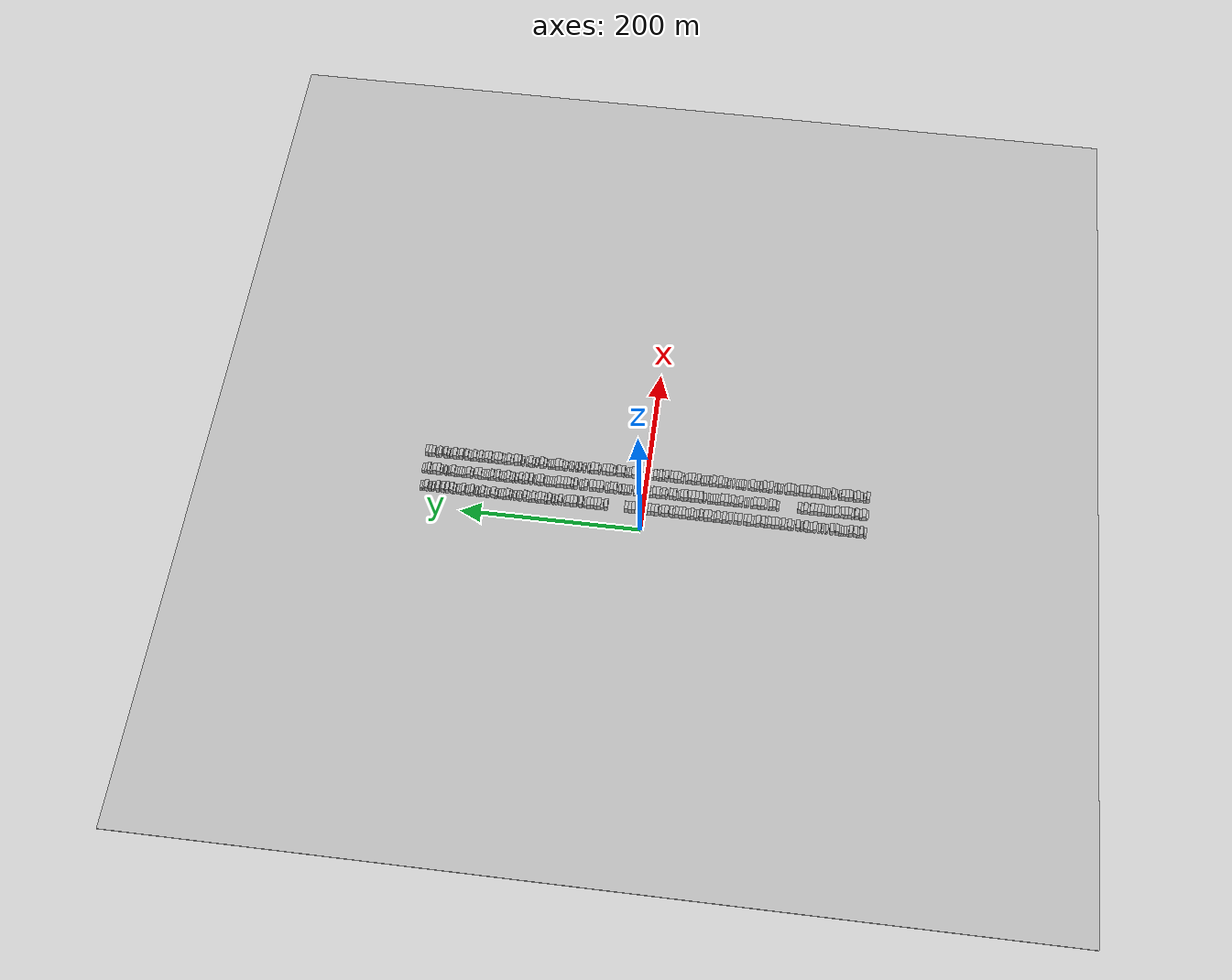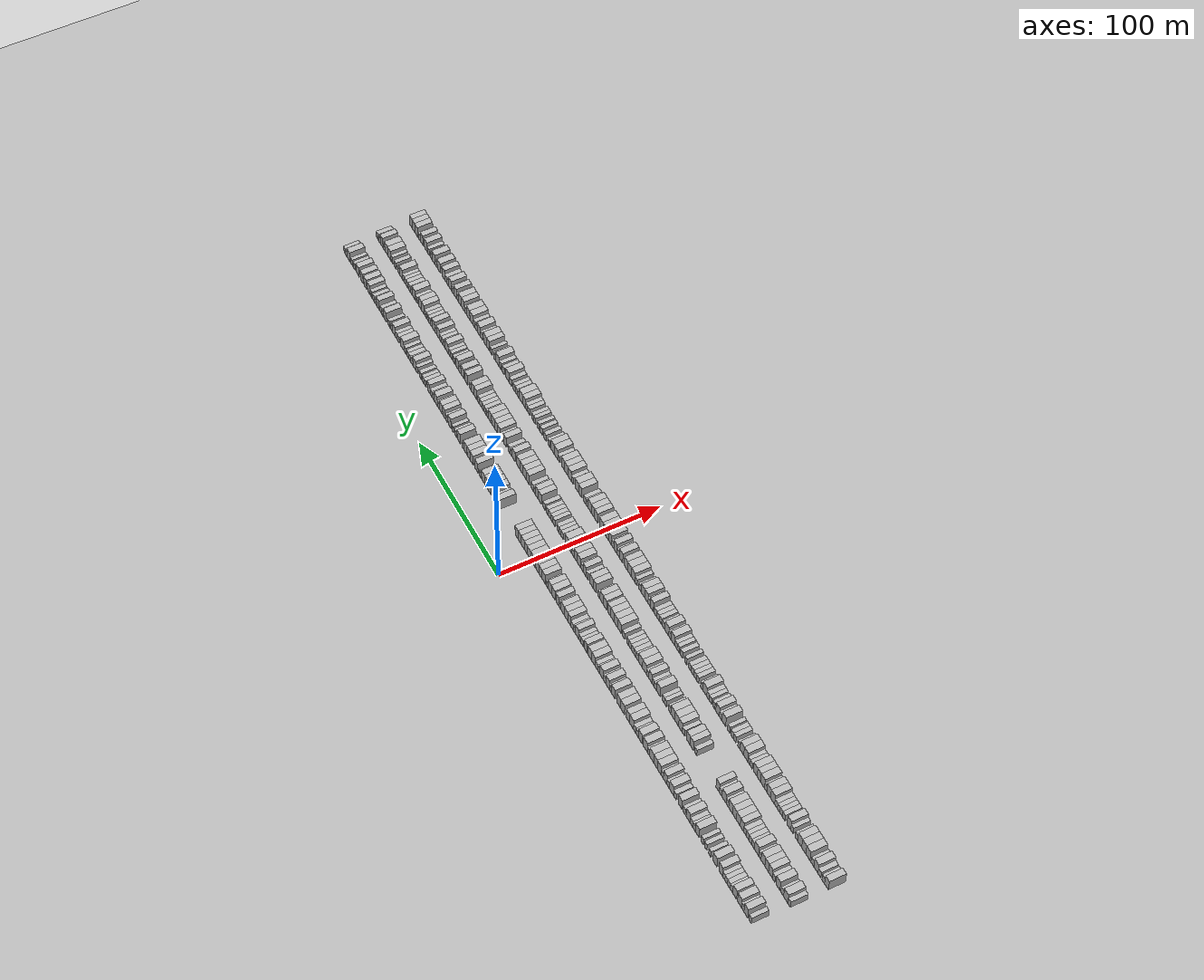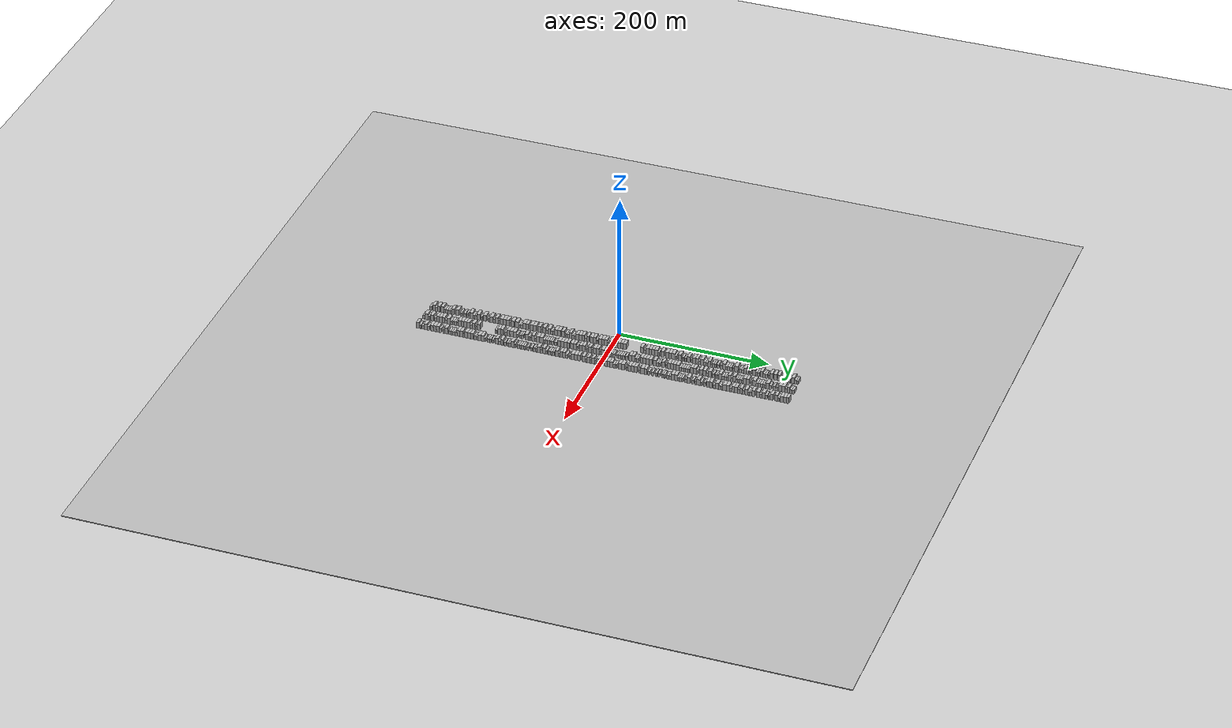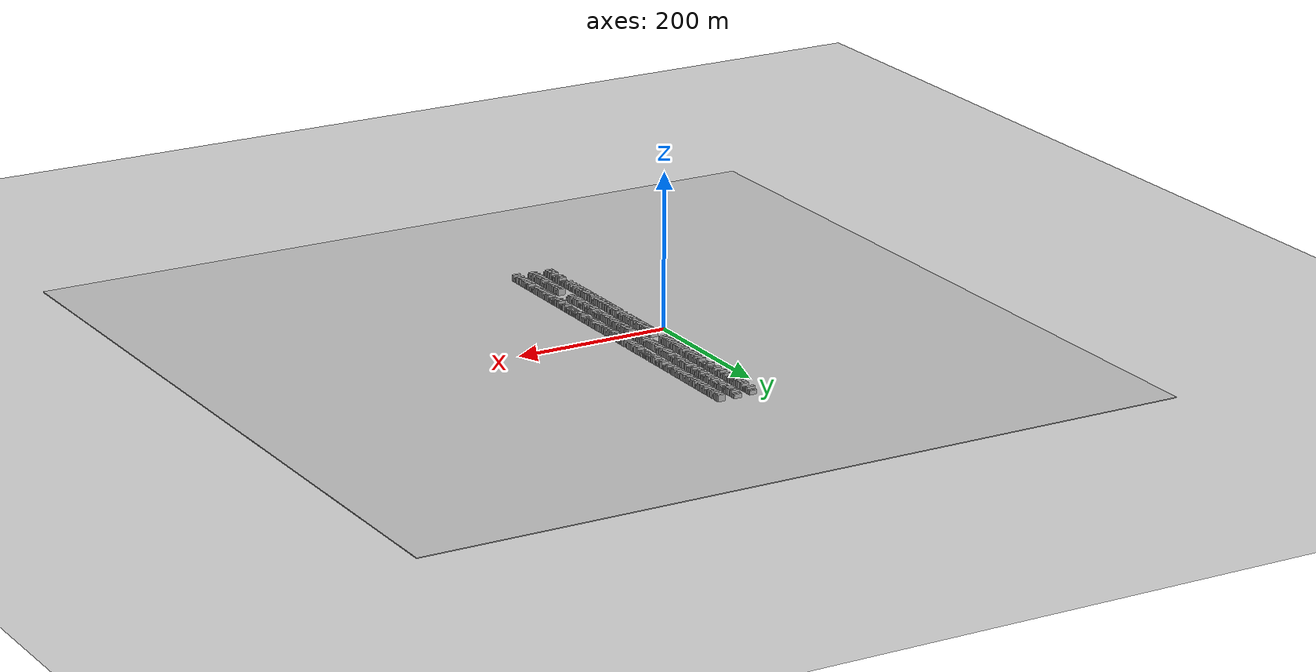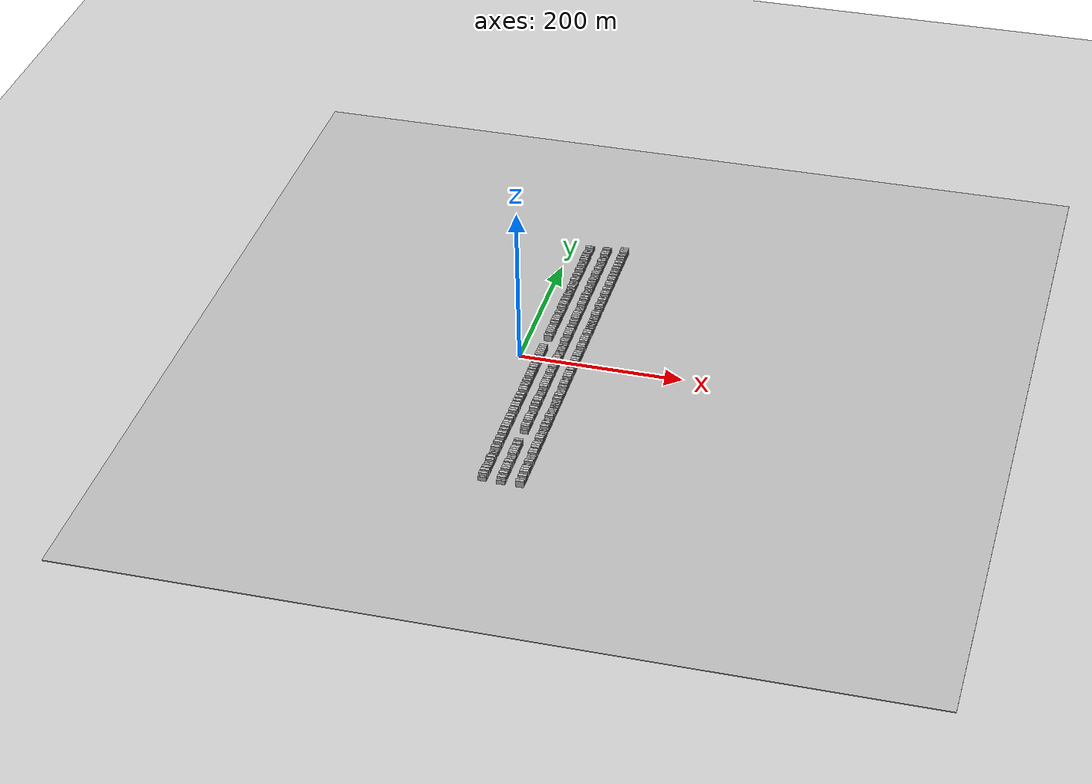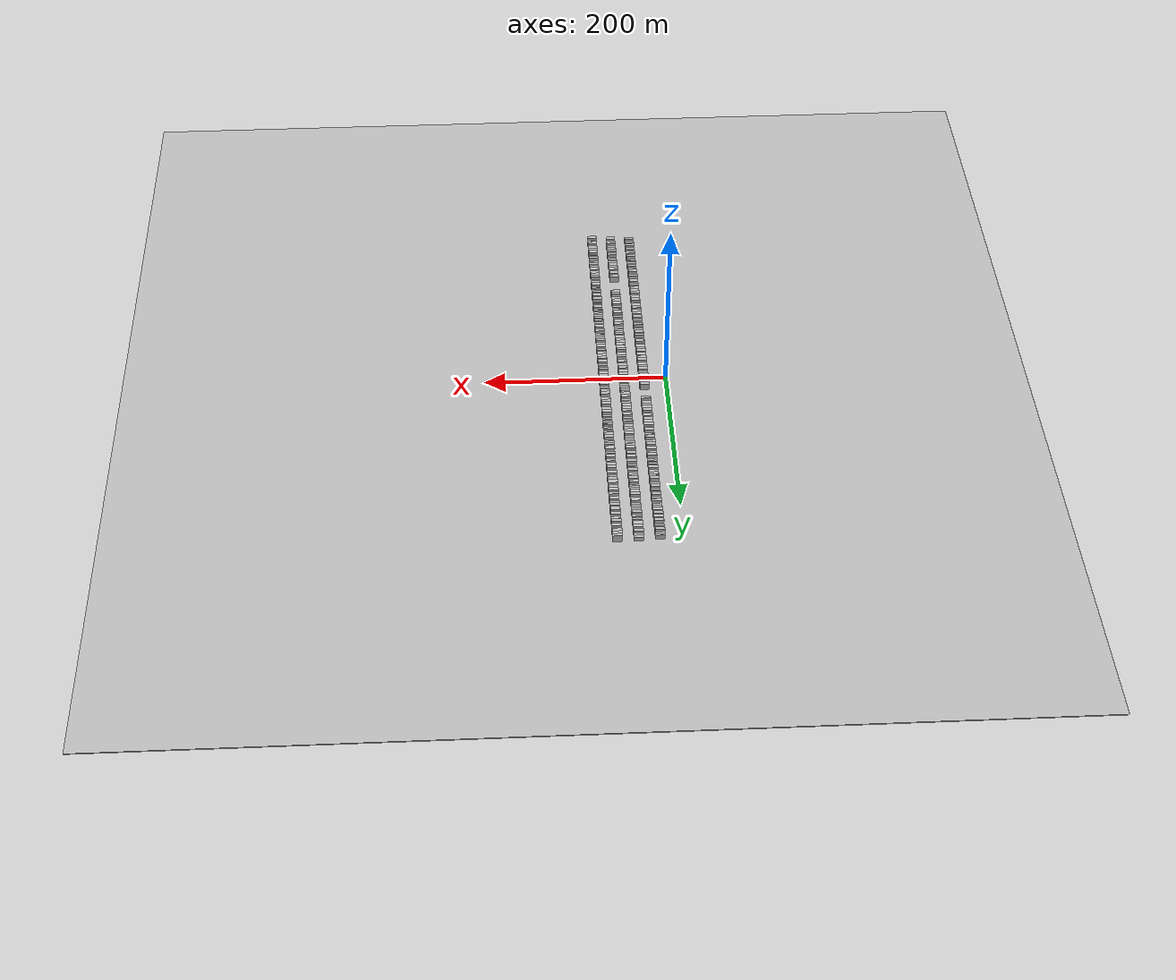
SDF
<?xml version="1.0" encoding="utf-8"?>

<sdf version="1.6">

   <world name="default">

      <gui fullscreen="0">

         <camera name="user_camera">

            <pose>-15 0 4.57585 0 0 0</pose>

            <view_controller>orbit</view_controller>

         </camera>

      </gui>

      <scene>

         <sky>

           <clouds>

             <speed>12</speed>

           </clouds>

         </sky>

         <ambient>0.4 0.4 0.4 1</ambient>

         <background>0.7 0.7 0.7 1</background>

         <shadows>1</shadows>

      </scene>

      <gravity>0 0 -9.8066</gravity>

      <magnetic_field>6e-06 2.3e-05 -4.2e-05</magnetic_field>

      <physics default="0" name="default_physics" type="ode">

         <ode>

            <solver>

               <type>quick</type>

               <iters>10</iters>

               <sor>1.0</sor>

               <use_dynamic_moi_rescaling>0</use_dynamic_moi_rescaling>

            </solver>

            <constraints>

               <cfm>0</cfm>

               <erp>0.2</erp>

               <contact_max_correcting_vel>100</contact_max_correcting_vel>

               <contact_surface_layer>0.001</contact_surface_layer>

            </constraints>

         </ode>

         <max_step_size>0.004</max_step_size>

         <real_time_factor>1</real_time_factor>

         <real_time_update_rate>250</real_time_update_rate>

      </physics>

      <light name="sun" type="directional">

         <cast_shadows>1</cast_shadows>

         <pose>0 0 10 0 0 0</pose>

         <diffuse>0.8 0.8 0.8 1</diffuse>

         <specular>0.2 0.2 0.2 1</specular>

         <attenuation>

            <range>1000</range>

            <constant>0.9</constant>

            <linear>0.01</linear>

            <quadratic>0.001</quadratic>

         </attenuation>

         <direction>-0.5 0.1 -0.9</direction>

      </light>

      <include>

         <name>ground_plane_1</name>

         <uri>model://HANNAS_ground_plane</uri>

         <pose>0 0 0  0 0 0</pose>

      </include>

      <include>

         <name>ground_plane_2</name>

         <uri>model://HANNAS_ground_plane</uri>

         <pose>100 0 0  0 0 0</pose>

      </include>

      <model name="building_1">

         <static>1</static>

         <pose frame="">25.0000 -245.7111 0 0.000000 0.000000 0.000000</pose>

         <link name="link">

            <pose frame="">0 0 3.00 0 0 0</pose>

            <collision name="collision">

               <geometry>

                  <box>

                     <size>10.0000 2.5778 6.0000</size>

                  </box>

               </geometry>

               <max_contacts>10</max_contacts>

               <surface>

                  <contact>

                     <ode/>

                  </contact>

                  <bounce/>

                  <friction>

                     <torsional>

                        <ode/>

                     </torsional>

                     <ode/>

                  </friction>

               </surface>

            </collision>

            <visual name="visual">

               <cast_shadows>0</cast_shadows>

               <geometry>

                  <box>

                     <size>10.0000 2.5778 6.0000</size>

                  </box>

               </geometry>

               <material>

                  <script>

                     <uri>model://HANNAS_wall/materials/scripts</uri>

                     <uri>model://HANNAS_wall/materials/textures</uri>

                     <name>vrc/HANNAS_wall</name>

                  </script>

               </material>

            </visual>

            <self_collide>0</self_collide>

            <enable_wind>0</enable_wind>

            <kinematic>0</kinematic>

         </link>

      </model>

      <model name="building_2">

         <static>1</static>

         <pose frame="">25.0000 -241.4931 0 0.000000 0.000000 0.000000</pose>

         <link name="link">

            <pose frame="">0 0 4.50 0 0 0</pose>

            <collision name="collision">

               <geometry>

                  <box>

                     <size>10.0000 3.8583 9.0000</size>

                  </box>

               </geometry>

               <max_contacts>10</max_contacts>

               <surface>

                  <contact>

                     <ode/>

                  </contact>

                  <bounce/>

                  <friction>

                     <torsional>

                        <ode/>

                     </torsional>

                     <ode/>

                  </friction>

               </surface>

            </collision>

            <visual name="visual">

               <cast_shadows>0</cast_shadows>

               <geometry>

                  <box>

                     <size>10.0000 3.8583 9.0000</size>

                  </box>

               </geometry>

               <material>

                  <script>

                     <uri>model://HANNAS_wall/materials/scripts</uri>

                     <uri>model://HANNAS_wall/materials/textures</uri>

                     <name>vrc/HANNAS_wall</name>

                  </script>

               </material>

            </visual>

            <self_collide>0</self_collide>

            <enable_wind>0</enable_wind>

            <kinematic>0</kinematic>

         </link>

      </model>

      <model name="building_3">

         <static>1</static>

         <pose frame="">25.0000 -238.2622 0 0.000000 0.000000 0.000000</pose>

         <link name="link">

            <pose frame="">0 0 3.00 0 0 0</pose>

            <collision name="collision">

               <geometry>

                  <box>

                     <size>10.0000 2.6036 6.0000</size>

                  </box>

               </geometry>

               <max_contacts>10</max_contacts>

               <surface>

                  <contact>

                     <ode/>

                  </contact>

                  <bounce/>

                  <friction>

                     <torsional>

                        <ode/>

                     </torsional>

                     <ode/>

                  </friction>

               </surface>

            </collision>

            <visual name="visual">

               <cast_shadows>0</cast_shadows>

               <geometry>

                  <box>

                     <size>10.0000 2.6036 6.0000</size>

                  </box>

               </geometry>

               <material>

                  <script>

                     <uri>model://HANNAS_wall/materials/scripts</uri>

                     <uri>model://HANNAS_wall/materials/textures</uri>

                     <name>vrc/HANNAS_wall</name>

                  </script>

               </material>

            </visual>

            <self_collide>0</self_collide>

            <enable_wind>0</enable_wind>

            <kinematic>0</kinematic>

         </link>

      </model>

      <model name="building_4">

         <static>1</static>

         <pose frame="">25.0000 -234.8649 0 0.000000 0.000000 0.000000</pose>

         <link name="link">

            <pose frame="">0 0 4.50 0 0 0</pose>

            <collision name="collision">

               <geometry>

                  <box>

                     <size>10.0000 4.1909 9.0000</size>

                  </box>

               </geometry>

               <max_contacts>10</max_contacts>

               <surface>

                  <contact>

                     <ode/>

                  </contact>

                  <bounce/>

                  <friction>

                     <torsional>

                        <ode/>

                     </torsional>

                     <ode/>

                  </friction>

               </surface>

            </collision>

            <visual name="visual">

               <cast_shadows>0</cast_shadows>

               <geometry>

                  <box>

                     <size>10.0000 4.1909 9.0000</size>

                  </box>

               </geometry>

               <material>

                  <script>

                     <uri>model://HANNAS_wall/materials/scripts</uri>

                     <uri>model://HANNAS_wall/materials/textures</uri>

                     <name>vrc/HANNAS_wall</name>

                  </script>

               </material>

            </visual>

            <self_collide>0</self_collide>

            <enable_wind>0</enable_wind>

            <kinematic>0</kinematic>

         </link>

      </model>

      <model name="building_5">

         <static>1</static>

         <pose frame="">25.0000 -229.7960 0 0.000000 0.000000 0.000000</pose>

         <link name="link">

            <pose frame="">0 0 4.50 0 0 0</pose>

            <collision name="collision">

               <geometry>

                  <box>

                     <size>10.0000 3.9468 9.0000</size>

                  </box>

               </geometry>

               <max_contacts>10</max_contacts>

               <surface>

                  <contact>

                     <ode/>

                  </contact>

                  <bounce/>

                  <friction>

                     <torsional>

                        <ode/>

                     </torsional>

                     <ode/>

                  </friction>

               </surface>

            </collision>

            <visual name="visual">

               <cast_shadows>0</cast_shadows>

               <geometry>

                  <box>

                     <size>10.0000 3.9468 9.0000</size>

                  </box>

               </geometry>

               <material>

                  <script>

                     <uri>model://HANNAS_wall/materials/scripts</uri>

                     <uri>model://HANNAS_wall/materials/textures</uri>

                     <name>vrc/HANNAS_wall</name>

                  </script>

               </material>

            </visual>

            <self_collide>0</self_collide>

            <enable_wind>0</enable_wind>

            <kinematic>0</kinematic>

         </link>

      </model>

      <model name="building_6">

         <static>1</static>

         <pose frame="">25.0000 -226.4992 0 0.000000 0.000000 0.000000</pose>

         <link name="link">

            <pose frame="">0 0 3.00 0 0 0</pose>

            <collision name="collision">

               <geometry>

                  <box>

                     <size>10.0000 2.6469 6.0000</size>

                  </box>

               </geometry>

               <max_contacts>10</max_contacts>

               <surface>

                  <contact>

                     <ode/>

                  </contact>

                  <bounce/>

                  <friction>

                     <torsional>

                        <ode/>

                     </torsional>

                     <ode/>

                  </friction>

               </surface>

            </collision>

            <visual name="visual">

               <cast_shadows>0</cast_shadows>

               <geometry>

                  <box>

                     <size>10.0000 2.6469 6.0000</size>

                  </box>

               </geometry>

               <material>

                  <script>

                     <uri>model://HANNAS_wall/materials/scripts</uri>

                     <uri>model://HANNAS_wall/materials/textures</uri>

                     <name>vrc/HANNAS_wall</name>

                  </script>

               </material>

            </visual>

            <self_collide>0</self_collide>

            <enable_wind>0</enable_wind>

            <kinematic>0</kinematic>

         </link>

      </model>

      <model name="building_7">

         <static>1</static>

         <pose frame="">25.0000 -223.7392 0 0.000000 0.000000 0.000000</pose>

         <link name="link">

            <pose frame="">0 0 3.00 0 0 0</pose>

            <collision name="collision">

               <geometry>

                  <box>

                     <size>10.0000 2.8731 6.0000</size>

                  </box>

               </geometry>

               <max_contacts>10</max_contacts>

               <surface>

                  <contact>

                     <ode/>

                  </contact>

                  <bounce/>

                  <friction>

                     <torsional>

                        <ode/>

                     </torsional>

                     <ode/>

                  </friction>

               </surface>

            </collision>

            <visual name="visual">

               <cast_shadows>0</cast_shadows>

               <geometry>

                  <box>

                     <size>10.0000 2.8731 6.0000</size>

                  </box>

               </geometry>

               <material>

                  <script>

                     <uri>model://HANNAS_wall/materials/scripts</uri>

                     <uri>model://HANNAS_wall/materials/textures</uri>

                     <name>vrc/HANNAS_wall</name>

                  </script>

               </material>

            </visual>

            <self_collide>0</self_collide>

            <enable_wind>0</enable_wind>

            <kinematic>0</kinematic>

         </link>

      </model>

      <model name="building_8">

         <static>1</static>

         <pose frame="">25.0000 -220.9604 0 0.000000 0.000000 0.000000</pose>

         <link name="link">

            <pose frame="">0 0 3.00 0 0 0</pose>

            <collision name="collision">

               <geometry>

                  <box>

                     <size>10.0000 2.6846 6.0000</size>

                  </box>

               </geometry>

               <max_contacts>10</max_contacts>

               <surface>

                  <contact>

                     <ode/>

                  </contact>

                  <bounce/>

                  <friction>

                     <torsional>

                        <ode/>

                     </torsional>

                     <ode/>

                  </friction>

               </surface>

            </collision>

            <visual name="visual">

               <cast_shadows>0</cast_shadows>

               <geometry>

                  <box>

                     <size>10.0000 2.6846 6.0000</size>

                  </box>

               </geometry>

               <material>

                  <script>

                     <uri>model://HANNAS_wall/materials/scripts</uri>

                     <uri>model://HANNAS_wall/materials/textures</uri>

                     <name>vrc/HANNAS_wall</name>

                  </script>

               </material>

            </visual>

            <self_collide>0</self_collide>

            <enable_wind>0</enable_wind>

            <kinematic>0</kinematic>

         </link>

      </model>

      <model name="building_9">

         <static>1</static>

         <pose frame="">25.0000 -218.4022 0 0.000000 0.000000 0.000000</pose>

         <link name="link">

            <pose frame="">0 0 3.00 0 0 0</pose>

            <collision name="collision">

               <geometry>

                  <box>

                     <size>10.0000 2.4316 6.0000</size>

                  </box>

               </geometry>

               <max_contacts>10</max_contacts>

               <surface>

                  <contact>

                     <ode/>

                  </contact>

                  <bounce/>

                  <friction>

                     <torsional>

                        <ode/>

                     </torsional>

                     <ode/>

                  </friction>

               </surface>

            </collision>

            <visual name="visual">

               <cast_shadows>0</cast_shadows>

               <geometry>

                  <box>

                     <size>10.0000 2.4316 6.0000</size>

                  </box>

               </geometry>

               <material>

                  <script>

                     <uri>model://HANNAS_wall/materials/scripts</uri>

                     <uri>model://HANNAS_wall/materials/textures</uri>

                     <name>vrc/HANNAS_wall</name>

                  </script>

               </material>

            </visual>

            <self_collide>0</self_collide>

            <enable_wind>0</enable_wind>

            <kinematic>0</kinematic>

         </link>

      </model>

      <model name="building_10">

         <static>1</static>

         <pose frame="">25.0000 -215.2051 0 0.000000 0.000000 0.000000</pose>

         <link name="link">

            <pose frame="">0 0 4.50 0 0 0</pose>

            <collision name="collision">

               <geometry>

                  <box>

                     <size>10.0000 3.9626 9.0000</size>

                  </box>

               </geometry>

               <max_contacts>10</max_contacts>

               <surface>

                  <contact>

                     <ode/>

                  </contact>

                  <bounce/>

                  <friction>

                     <torsional>

                        <ode/>

                     </torsional>

                     <ode/>

                  </friction>

               </surface>

            </collision>

            <visual name="visual">

               <cast_shadows>0</cast_shadows>

               <geometry>

                  <box>

                     <size>10.0000 3.9626 9.0000</size>

                  </box>

               </geometry>

               <material>

                  <script>

                     <uri>model://HANNAS_wall/materials/scripts</uri>

                     <uri>model://HANNAS_wall/materials/textures</uri>

                     <name>vrc/HANNAS_wall</name>

                  </script>

               </material>

            </visual>

            <self_collide>0</self_collide>

            <enable_wind>0</enable_wind>

            <kinematic>0</kinematic>

         </link>

      </model>

      <model name="building_11">

         <static>1</static>

         <pose frame="">25.0000 -209.0972 0 0.000000 0.000000 0.000000</pose>

         <link name="link">

            <pose frame="">0 0 4.50 0 0 0</pose>

            <collision name="collision">

               <geometry>

                  <box>

                     <size>10.0000 4.2532 9.0000</size>

                  </box>

               </geometry>

               <max_contacts>10</max_contacts>

               <surface>

                  <contact>

                     <ode/>

                  </contact>

                  <bounce/>

                  <friction>

                     <torsional>

                        <ode/>

                     </torsional>

                     <ode/>

                  </friction>

               </surface>

            </collision>

            <visual name="visual">

               <cast_shadows>0</cast_shadows>

               <geometry>

                  <box>

                     <size>10.0000 4.2532 9.0000</size>

                  </box>

               </geometry>

               <material>

                  <script>

                     <uri>model://HANNAS_wall/materials/scripts</uri>

                     <uri>model://HANNAS_wall/materials/textures</uri>

                     <name>vrc/HANNAS_wall</name>

                  </script>

               </material>

            </visual>

            <self_collide>0</self_collide>

            <enable_wind>0</enable_wind>

            <kinematic>0</kinematic>

         </link>

      </model>

      <model name="building_12">

         <static>1</static>

         <pose frame="">25.0000 -203.7434 0 0.000000 0.000000 0.000000</pose>

         <link name="link">

            <pose frame="">0 0 3.00 0 0 0</pose>

            <collision name="collision">

               <geometry>

                  <box>

                     <size>10.0000 2.4546 6.0000</size>

                  </box>

               </geometry>

               <max_contacts>10</max_contacts>

               <surface>

                  <contact>

                     <ode/>

                  </contact>

                  <bounce/>

                  <friction>

                     <torsional>

                        <ode/>

                     </torsional>

                     <ode/>

                  </friction>

               </surface>

            </collision>

            <visual name="visual">

               <cast_shadows>0</cast_shadows>

               <geometry>

                  <box>

                     <size>10.0000 2.4546 6.0000</size>

                  </box>

               </geometry>

               <material>

                  <script>

                     <uri>model://HANNAS_wall/materials/scripts</uri>

                     <uri>model://HANNAS_wall/materials/textures</uri>

                     <name>vrc/HANNAS_wall</name>

                  </script>

               </material>

            </visual>

            <self_collide>0</self_collide>

            <enable_wind>0</enable_wind>

            <kinematic>0</kinematic>

         </link>

      </model>

      <model name="building_13">

         <static>1</static>

         <pose frame="">25.0000 -199.2047 0 0.000000 0.000000 0.000000</pose>

         <link name="link">

            <pose frame="">0 0 3.00 0 0 0</pose>

            <collision name="collision">

               <geometry>

                  <box>

                     <size>10.0000 2.6228 6.0000</size>

                  </box>

               </geometry>

               <max_contacts>10</max_contacts>

               <surface>

                  <contact>

                     <ode/>

                  </contact>

                  <bounce/>

                  <friction>

                     <torsional>

                        <ode/>

                     </torsional>

                     <ode/>

                  </friction>

               </surface>

            </collision>

            <visual name="visual">

               <cast_shadows>0</cast_shadows>

               <geometry>

                  <box>

                     <size>10.0000 2.6228 6.0000</size>

                  </box>

               </geometry>

               <material>

                  <script>

                     <uri>model://HANNAS_wall/materials/scripts</uri>

                     <uri>model://HANNAS_wall/materials/textures</uri>

                     <name>vrc/HANNAS_wall</name>

                  </script>

               </material>

            </visual>

            <self_collide>0</self_collide>

            <enable_wind>0</enable_wind>

            <kinematic>0</kinematic>

         </link>

      </model>

      <model name="building_14">

         <static>1</static>

         <pose frame="">25.0000 -195.6604 0 0.000000 0.000000 0.000000</pose>

         <link name="link">

            <pose frame="">0 0 3.00 0 0 0</pose>

            <collision name="collision">

               <geometry>

                  <box>

                     <size>10.0000 2.4657 6.0000</size>

                  </box>

               </geometry>

               <max_contacts>10</max_contacts>

               <surface>

                  <contact>

                     <ode/>

                  </contact>

                  <bounce/>

                  <friction>

                     <torsional>

                        <ode/>

                     </torsional>

                     <ode/>

                  </friction>

               </surface>

            </collision>

            <visual name="visual">

               <cast_shadows>0</cast_shadows>

               <geometry>

                  <box>

                     <size>10.0000 2.4657 6.0000</size>

                  </box>

               </geometry>

               <material>

                  <script>

                     <uri>model://HANNAS_wall/materials/scripts</uri>

                     <uri>model://HANNAS_wall/materials/textures</uri>

                     <name>vrc/HANNAS_wall</name>

                  </script>

               </material>

            </visual>

            <self_collide>0</self_collide>

            <enable_wind>0</enable_wind>

            <kinematic>0</kinematic>

         </link>

      </model>

      <model name="building_15">

         <static>1</static>

         <pose frame="">25.0000 -190.3224 0 0.000000 0.000000 0.000000</pose>

         <link name="link">

            <pose frame="">0 0 4.50 0 0 0</pose>

            <collision name="collision">

               <geometry>

                  <box>

                     <size>10.0000 4.2102 9.0000</size>

                  </box>

               </geometry>

               <max_contacts>10</max_contacts>

               <surface>

                  <contact>

                     <ode/>

                  </contact>

                  <bounce/>

                  <friction>

                     <torsional>

                        <ode/>

                     </torsional>

                     <ode/>

                  </friction>

               </surface>

            </collision>

            <visual name="visual">

               <cast_shadows>0</cast_shadows>

               <geometry>

                  <box>

                     <size>10.0000 4.2102 9.0000</size>

                  </box>

               </geometry>

               <material>

                  <script>

                     <uri>model://HANNAS_wall/materials/scripts</uri>

                     <uri>model://HANNAS_wall/materials/textures</uri>

                     <name>vrc/HANNAS_wall</name>

                  </script>

               </material>

            </visual>

            <self_collide>0</self_collide>

            <enable_wind>0</enable_wind>

            <kinematic>0</kinematic>

         </link>

      </model>

      <model name="building_16">

         <static>1</static>

         <pose frame="">25.0000 -186.8128 0 0.000000 0.000000 0.000000</pose>

         <link name="link">

            <pose frame="">0 0 3.00 0 0 0</pose>

            <collision name="collision">

               <geometry>

                  <box>

                     <size>10.0000 2.8091 6.0000</size>

                  </box>

               </geometry>

               <max_contacts>10</max_contacts>

               <surface>

                  <contact>

                     <ode/>

                  </contact>

                  <bounce/>

                  <friction>

                     <torsional>

                        <ode/>

                     </torsional>

                     <ode/>

                  </friction>

               </surface>

            </collision>

            <visual name="visual">

               <cast_shadows>0</cast_shadows>

               <geometry>

                  <box>

                     <size>10.0000 2.8091 6.0000</size>

                  </box>

               </geometry>

               <material>

                  <script>

                     <uri>model://HANNAS_wall/materials/scripts</uri>

                     <uri>model://HANNAS_wall/materials/textures</uri>

                     <name>vrc/HANNAS_wall</name>

                  </script>

               </material>

            </visual>

            <self_collide>0</self_collide>

            <enable_wind>0</enable_wind>

            <kinematic>0</kinematic>

         </link>

      </model>

      <model name="building_17">

         <static>1</static>

         <pose frame="">25.0000 -184.0026 0 0.000000 0.000000 0.000000</pose>

         <link name="link">

            <pose frame="">0 0 3.00 0 0 0</pose>

            <collision name="collision">

               <geometry>

                  <box>

                     <size>10.0000 2.8112 6.0000</size>

                  </box>

               </geometry>

               <max_contacts>10</max_contacts>

               <surface>

                  <contact>

                     <ode/>

                  </contact>

                  <bounce/>

                  <friction>

                     <torsional>

                        <ode/>

                     </torsional>

                     <ode/>

                  </friction>

               </surface>

            </collision>

            <visual name="visual">

               <cast_shadows>0</cast_shadows>

               <geometry>

                  <box>

                     <size>10.0000 2.8112 6.0000</size>

                  </box>

               </geometry>

               <material>

                  <script>

                     <uri>model://HANNAS_wall/materials/scripts</uri>

                     <uri>model://HANNAS_wall/materials/textures</uri>

                     <name>vrc/HANNAS_wall</name>

                  </script>

               </material>

            </visual>

            <self_collide>0</self_collide>

            <enable_wind>0</enable_wind>

            <kinematic>0</kinematic>

         </link>

      </model>

      <model name="building_18">

         <static>1</static>

         <pose frame="">25.0000 -180.4694 0 0.000000 0.000000 0.000000</pose>

         <link name="link">

            <pose frame="">0 0 4.50 0 0 0</pose>

            <collision name="collision">

               <geometry>

                  <box>

                     <size>10.0000 4.2552 9.0000</size>

                  </box>

               </geometry>

               <max_contacts>10</max_contacts>

               <surface>

                  <contact>

                     <ode/>

                  </contact>

                  <bounce/>

                  <friction>

                     <torsional>

                        <ode/>

                     </torsional>

                     <ode/>

                  </friction>

               </surface>

            </collision>

            <visual name="visual">

               <cast_shadows>0</cast_shadows>

               <geometry>

                  <box>

                     <size>10.0000 4.2552 9.0000</size>

                  </box>

               </geometry>

               <material>

                  <script>

                     <uri>model://HANNAS_wall/materials/scripts</uri>

                     <uri>model://HANNAS_wall/materials/textures</uri>

                     <name>vrc/HANNAS_wall</name>

                  </script>

               </material>

            </visual>

            <self_collide>0</self_collide>

            <enable_wind>0</enable_wind>

            <kinematic>0</kinematic>

         </link>

      </model>

      <model name="building_19">

         <static>1</static>

         <pose frame="">25.0000 -176.1244 0 0.000000 0.000000 0.000000</pose>

         <link name="link">

            <pose frame="">0 0 3.00 0 0 0</pose>

            <collision name="collision">

               <geometry>

                  <box>

                     <size>10.0000 2.4348 6.0000</size>

                  </box>

               </geometry>

               <max_contacts>10</max_contacts>

               <surface>

                  <contact>

                     <ode/>

                  </contact>

                  <bounce/>

                  <friction>

                     <torsional>

                        <ode/>

                     </torsional>

                     <ode/>

                  </friction>

               </surface>

            </collision>

            <visual name="visual">

               <cast_shadows>0</cast_shadows>

               <geometry>

                  <box>

                     <size>10.0000 2.4348 6.0000</size>

                  </box>

               </geometry>

               <material>

                  <script>

                     <uri>model://HANNAS_wall/materials/scripts</uri>

                     <uri>model://HANNAS_wall/materials/textures</uri>

                     <name>vrc/HANNAS_wall</name>

                  </script>

               </material>

            </visual>

            <self_collide>0</self_collide>

            <enable_wind>0</enable_wind>

            <kinematic>0</kinematic>

         </link>

      </model>

      <model name="building_20">

         <static>1</static>

         <pose frame="">25.0000 -171.7670 0 0.000000 0.000000 0.000000</pose>

         <link name="link">

            <pose frame="">0 0 4.50 0 0 0</pose>

            <collision name="collision">

               <geometry>

                  <box>

                     <size>10.0000 4.2801 9.0000</size>

                  </box>

               </geometry>

               <max_contacts>10</max_contacts>

               <surface>

                  <contact>

                     <ode/>

                  </contact>

                  <bounce/>

                  <friction>

                     <torsional>

                        <ode/>

                     </torsional>

                     <ode/>

                  </friction>

               </surface>

            </collision>

            <visual name="visual">

               <cast_shadows>0</cast_shadows>

               <geometry>

                  <box>

                     <size>10.0000 4.2801 9.0000</size>

                  </box>

               </geometry>

               <material>

                  <script>

                     <uri>model://HANNAS_wall/materials/scripts</uri>

                     <uri>model://HANNAS_wall/materials/textures</uri>

                     <name>vrc/HANNAS_wall</name>

                  </script>

               </material>

            </visual>

            <self_collide>0</self_collide>

            <enable_wind>0</enable_wind>

            <kinematic>0</kinematic>

         </link>

      </model>

      <model name="building_21">

         <static>1</static>

         <pose frame="">25.0000 -166.1317 0 0.000000 0.000000 0.000000</pose>

         <link name="link">

            <pose frame="">0 0 3.00 0 0 0</pose>

            <collision name="collision">

               <geometry>

                  <box>

                     <size>10.0000 2.9904 6.0000</size>

                  </box>

               </geometry>

               <max_contacts>10</max_contacts>

               <surface>

                  <contact>

                     <ode/>

                  </contact>

                  <bounce/>

                  <friction>

                     <torsional>

                        <ode/>

                     </torsional>

                     <ode/>

                  </friction>

               </surface>

            </collision>

            <visual name="visual">

               <cast_shadows>0</cast_shadows>

               <geometry>

                  <box>

                     <size>10.0000 2.9904 6.0000</size>

                  </box>

               </geometry>

               <material>

                  <script>

                     <uri>model://HANNAS_wall/materials/scripts</uri>

                     <uri>model://HANNAS_wall/materials/textures</uri>

                     <name>vrc/HANNAS_wall</name>

                  </script>

               </material>

            </visual>

            <self_collide>0</self_collide>

            <enable_wind>0</enable_wind>

            <kinematic>0</kinematic>

         </link>

      </model>

      <model name="building_22">

         <static>1</static>

         <pose frame="">25.0000 -162.4682 0 0.000000 0.000000 0.000000</pose>

         <link name="link">

            <pose frame="">0 0 4.50 0 0 0</pose>

            <collision name="collision">

               <geometry>

                  <box>

                     <size>10.0000 4.3366 9.0000</size>

                  </box>

               </geometry>

               <max_contacts>10</max_contacts>

               <surface>

                  <contact>

                     <ode/>

                  </contact>

                  <bounce/>

                  <friction>

                     <torsional>

                        <ode/>

                     </torsional>

                     <ode/>

                  </friction>

               </surface>

            </collision>

            <visual name="visual">

               <cast_shadows>0</cast_shadows>

               <geometry>

                  <box>

                     <size>10.0000 4.3366 9.0000</size>

                  </box>

               </geometry>

               <material>

                  <script>

                     <uri>model://HANNAS_wall/materials/scripts</uri>

                     <uri>model://HANNAS_wall/materials/textures</uri>

                     <name>vrc/HANNAS_wall</name>

                  </script>

               </material>

            </visual>

            <self_collide>0</self_collide>

            <enable_wind>0</enable_wind>

            <kinematic>0</kinematic>

         </link>

      </model>

      <model name="building_23">

         <static>1</static>

         <pose frame="">25.0000 -158.8605 0 0.000000 0.000000 0.000000</pose>

         <link name="link">

            <pose frame="">0 0 3.00 0 0 0</pose>

            <collision name="collision">

               <geometry>

                  <box>

                     <size>10.0000 2.8788 6.0000</size>

                  </box>

               </geometry>

               <max_contacts>10</max_contacts>

               <surface>

                  <contact>

                     <ode/>

                  </contact>

                  <bounce/>

                  <friction>

                     <torsional>

                        <ode/>

                     </torsional>

                     <ode/>

                  </friction>

               </surface>

            </collision>

            <visual name="visual">

               <cast_shadows>0</cast_shadows>

               <geometry>

                  <box>

                     <size>10.0000 2.8788 6.0000</size>

                  </box>

               </geometry>

               <material>

                  <script>

                     <uri>model://HANNAS_wall/materials/scripts</uri>

                     <uri>model://HANNAS_wall/materials/textures</uri>

                     <name>vrc/HANNAS_wall</name>

                  </script>

               </material>

            </visual>

            <self_collide>0</self_collide>

            <enable_wind>0</enable_wind>

            <kinematic>0</kinematic>

         </link>

      </model>

      <model name="building_24">

         <static>1</static>

         <pose frame="">25.0000 -155.4909 0 0.000000 0.000000 0.000000</pose>

         <link name="link">

            <pose frame="">0 0 4.50 0 0 0</pose>

            <collision name="collision">

               <geometry>

                  <box>

                     <size>10.0000 3.8604 9.0000</size>

                  </box>

               </geometry>

               <max_contacts>10</max_contacts>

               <surface>

                  <contact>

                     <ode/>

                  </contact>

                  <bounce/>

                  <friction>

                     <torsional>

                        <ode/>

                     </torsional>

                     <ode/>

                  </friction>

               </surface>

            </collision>

            <visual name="visual">

               <cast_shadows>0</cast_shadows>

               <geometry>

                  <box>

                     <size>10.0000 3.8604 9.0000</size>

                  </box>

               </geometry>

               <material>

                  <script>

                     <uri>model://HANNAS_wall/materials/scripts</uri>

                     <uri>model://HANNAS_wall/materials/textures</uri>

                     <name>vrc/HANNAS_wall</name>

                  </script>

               </material>

            </visual>

            <self_collide>0</self_collide>

            <enable_wind>0</enable_wind>

            <kinematic>0</kinematic>

         </link>

      </model>

      <model name="building_25">

         <static>1</static>

         <pose frame="">25.0000 -152.3053 0 0.000000 0.000000 0.000000</pose>

         <link name="link">

            <pose frame="">0 0 3.00 0 0 0</pose>

            <collision name="collision">

               <geometry>

                  <box>

                     <size>10.0000 2.5108 6.0000</size>

                  </box>

               </geometry>

               <max_contacts>10</max_contacts>

               <surface>

                  <contact>

                     <ode/>

                  </contact>

                  <bounce/>

                  <friction>

                     <torsional>

                        <ode/>

                     </torsional>

                     <ode/>

                  </friction>

               </surface>

            </collision>

            <visual name="visual">

               <cast_shadows>0</cast_shadows>

               <geometry>

                  <box>

                     <size>10.0000 2.5108 6.0000</size>

                  </box>

               </geometry>

               <material>

                  <script>

                     <uri>model://HANNAS_wall/materials/scripts</uri>

                     <uri>model://HANNAS_wall/materials/textures</uri>

                     <name>vrc/HANNAS_wall</name>

                  </script>

               </material>

            </visual>

            <self_collide>0</self_collide>

            <enable_wind>0</enable_wind>

            <kinematic>0</kinematic>

         </link>

      </model>

      <model name="building_26">

         <static>1</static>

         <pose frame="">25.0000 -148.8860 0 0.000000 0.000000 0.000000</pose>

         <link name="link">

            <pose frame="">0 0 4.50 0 0 0</pose>

            <collision name="collision">

               <geometry>

                  <box>

                     <size>10.0000 4.3277 9.0000</size>

                  </box>

               </geometry>

               <max_contacts>10</max_contacts>

               <surface>

                  <contact>

                     <ode/>

                  </contact>

                  <bounce/>

                  <friction>

                     <torsional>

                        <ode/>

                     </torsional>

                     <ode/>

                  </friction>

               </surface>

            </collision>

            <visual name="visual">

               <cast_shadows>0</cast_shadows>

               <geometry>

                  <box>

                     <size>10.0000 4.3277 9.0000</size>

                  </box>

               </geometry>

               <material>

                  <script>

                     <uri>model://HANNAS_wall/materials/scripts</uri>

                     <uri>model://HANNAS_wall/materials/textures</uri>

                     <name>vrc/HANNAS_wall</name>

                  </script>

               </material>

            </visual>

            <self_collide>0</self_collide>

            <enable_wind>0</enable_wind>

            <kinematic>0</kinematic>

         </link>

      </model>

      <model name="building_27">

         <static>1</static>

         <pose frame="">25.0000 -144.7227 0 0.000000 0.000000 0.000000</pose>

         <link name="link">

            <pose frame="">0 0 4.50 0 0 0</pose>

            <collision name="collision">

               <geometry>

                  <box>

                     <size>10.0000 3.9991 9.0000</size>

                  </box>

               </geometry>

               <max_contacts>10</max_contacts>

               <surface>

                  <contact>

                     <ode/>

                  </contact>

                  <bounce/>

                  <friction>

                     <torsional>

                        <ode/>

                     </torsional>

                     <ode/>

                  </friction>

               </surface>

            </collision>

            <visual name="visual">

               <cast_shadows>0</cast_shadows>

               <geometry>

                  <box>

                     <size>10.0000 3.9991 9.0000</size>

                  </box>

               </geometry>

               <material>

                  <script>

                     <uri>model://HANNAS_wall/materials/scripts</uri>

                     <uri>model://HANNAS_wall/materials/textures</uri>

                     <name>vrc/HANNAS_wall</name>

                  </script>

               </material>

            </visual>

            <self_collide>0</self_collide>

            <enable_wind>0</enable_wind>

            <kinematic>0</kinematic>

         </link>

      </model>

      <model name="building_28">

         <static>1</static>

         <pose frame="">25.0000 -140.5339 0 0.000000 0.000000 0.000000</pose>

         <link name="link">

            <pose frame="">0 0 4.50 0 0 0</pose>

            <collision name="collision">

               <geometry>

                  <box>

                     <size>10.0000 4.3785 9.0000</size>

                  </box>

               </geometry>

               <max_contacts>10</max_contacts>

               <surface>

                  <contact>

                     <ode/>

                  </contact>

                  <bounce/>

                  <friction>

                     <torsional>

                        <ode/>

                     </torsional>

                     <ode/>

                  </friction>

               </surface>

            </collision>

            <visual name="visual">

               <cast_shadows>0</cast_shadows>

               <geometry>

                  <box>

                     <size>10.0000 4.3785 9.0000</size>

                  </box>

               </geometry>

               <material>

                  <script>

                     <uri>model://HANNAS_wall/materials/scripts</uri>

                     <uri>model://HANNAS_wall/materials/textures</uri>

                     <name>vrc/HANNAS_wall</name>

                  </script>

               </material>

            </visual>

            <self_collide>0</self_collide>

            <enable_wind>0</enable_wind>

            <kinematic>0</kinematic>

         </link>

      </model>

      <model name="building_29">

         <static>1</static>

         <pose frame="">25.0000 -137.0262 0 0.000000 0.000000 0.000000</pose>

         <link name="link">

            <pose frame="">0 0 3.00 0 0 0</pose>

            <collision name="collision">

               <geometry>

                  <box>

                     <size>10.0000 2.6369 6.0000</size>

                  </box>

               </geometry>

               <max_contacts>10</max_contacts>

               <surface>

                  <contact>

                     <ode/>

                  </contact>

                  <bounce/>

                  <friction>

                     <torsional>

                        <ode/>

                     </torsional>

                     <ode/>

                  </friction>

               </surface>

            </collision>

            <visual name="visual">

               <cast_shadows>0</cast_shadows>

               <geometry>

                  <box>

                     <size>10.0000 2.6369 6.0000</size>

                  </box>

               </geometry>

               <material>

                  <script>

                     <uri>model://HANNAS_wall/materials/scripts</uri>

                     <uri>model://HANNAS_wall/materials/textures</uri>

                     <name>vrc/HANNAS_wall</name>

                  </script>

               </material>

            </visual>

            <self_collide>0</self_collide>

            <enable_wind>0</enable_wind>

            <kinematic>0</kinematic>

         </link>

      </model>

      <model name="building_30">

         <static>1</static>

         <pose frame="">25.0000 -133.4724 0 0.000000 0.000000 0.000000</pose>

         <link name="link">

            <pose frame="">0 0 4.50 0 0 0</pose>

            <collision name="collision">

               <geometry>

                  <box>

                     <size>10.0000 4.4707 9.0000</size>

                  </box>

               </geometry>

               <max_contacts>10</max_contacts>

               <surface>

                  <contact>

                     <ode/>

                  </contact>

                  <bounce/>

                  <friction>

                     <torsional>

                        <ode/>

                     </torsional>

                     <ode/>

                  </friction>

               </surface>

            </collision>

            <visual name="visual">

               <cast_shadows>0</cast_shadows>

               <geometry>

                  <box>

                     <size>10.0000 4.4707 9.0000</size>

                  </box>

               </geometry>

               <material>

                  <script>

                     <uri>model://HANNAS_wall/materials/scripts</uri>

                     <uri>model://HANNAS_wall/materials/textures</uri>

                     <name>vrc/HANNAS_wall</name>

                  </script>

               </material>

            </visual>

            <self_collide>0</self_collide>

            <enable_wind>0</enable_wind>

            <kinematic>0</kinematic>

         </link>

      </model>

      <model name="building_31">

         <static>1</static>

         <pose frame="">25.0000 -128.0001 0 0.000000 0.000000 0.000000</pose>

         <link name="link">

            <pose frame="">0 0 4.50 0 0 0</pose>

            <collision name="collision">

               <geometry>

                  <box>

                     <size>10.0000 4.4739 9.0000</size>

                  </box>

               </geometry>

               <max_contacts>10</max_contacts>

               <surface>

                  <contact>

                     <ode/>

                  </contact>

                  <bounce/>

                  <friction>

                     <torsional>

                        <ode/>

                     </torsional>

                     <ode/>

                  </friction>

               </surface>

            </collision>

            <visual name="visual">

               <cast_shadows>0</cast_shadows>

               <geometry>

                  <box>

                     <size>10.0000 4.4739 9.0000</size>

                  </box>

               </geometry>

               <material>

                  <script>

                     <uri>model://HANNAS_wall/materials/scripts</uri>

                     <uri>model://HANNAS_wall/materials/textures</uri>

                     <name>vrc/HANNAS_wall</name>

                  </script>

               </material>

            </visual>

            <self_collide>0</self_collide>

            <enable_wind>0</enable_wind>

            <kinematic>0</kinematic>

         </link>

      </model>

      <model name="building_32">

         <static>1</static>

         <pose frame="">25.0000 -124.4471 0 0.000000 0.000000 0.000000</pose>

         <link name="link">

            <pose frame="">0 0 3.00 0 0 0</pose>

            <collision name="collision">

               <geometry>

                  <box>

                     <size>10.0000 2.6320 6.0000</size>

                  </box>

               </geometry>

               <max_contacts>10</max_contacts>

               <surface>

                  <contact>

                     <ode/>

                  </contact>

                  <bounce/>

                  <friction>

                     <torsional>

                        <ode/>

                     </torsional>

                     <ode/>

                  </friction>

               </surface>

            </collision>

            <visual name="visual">

               <cast_shadows>0</cast_shadows>

               <geometry>

                  <box>

                     <size>10.0000 2.6320 6.0000</size>

                  </box>

               </geometry>

               <material>

                  <script>

                     <uri>model://HANNAS_wall/materials/scripts</uri>

                     <uri>model://HANNAS_wall/materials/textures</uri>

                     <name>vrc/HANNAS_wall</name>

                  </script>

               </material>

            </visual>

            <self_collide>0</self_collide>

            <enable_wind>0</enable_wind>

            <kinematic>0</kinematic>

         </link>

      </model>

      <model name="building_33">

         <static>1</static>

         <pose frame="">25.0000 -121.7070 0 0.000000 0.000000 0.000000</pose>

         <link name="link">

            <pose frame="">0 0 3.00 0 0 0</pose>

            <collision name="collision">

               <geometry>

                  <box>

                     <size>10.0000 2.8481 6.0000</size>

                  </box>

               </geometry>

               <max_contacts>10</max_contacts>

               <surface>

                  <contact>

                     <ode/>

                  </contact>

                  <bounce/>

                  <friction>

                     <torsional>

                        <ode/>

                     </torsional>

                     <ode/>

                  </friction>

               </surface>

            </collision>

            <visual name="visual">

               <cast_shadows>0</cast_shadows>

               <geometry>

                  <box>

                     <size>10.0000 2.8481 6.0000</size>

                  </box>

               </geometry>

               <material>

                  <script>

                     <uri>model://HANNAS_wall/materials/scripts</uri>

                     <uri>model://HANNAS_wall/materials/textures</uri>

                     <name>vrc/HANNAS_wall</name>

                  </script>

               </material>

            </visual>

            <self_collide>0</self_collide>

            <enable_wind>0</enable_wind>

            <kinematic>0</kinematic>

         </link>

      </model>

      <model name="building_34">

         <static>1</static>

         <pose frame="">25.0000 -118.0810 0 0.000000 0.000000 0.000000</pose>

         <link name="link">

            <pose frame="">0 0 4.50 0 0 0</pose>

            <collision name="collision">

               <geometry>

                  <box>

                     <size>10.0000 4.4040 9.0000</size>

                  </box>

               </geometry>

               <max_contacts>10</max_contacts>

               <surface>

                  <contact>

                     <ode/>

                  </contact>

                  <bounce/>

                  <friction>

                     <torsional>

                        <ode/>

                     </torsional>

                     <ode/>

                  </friction>

               </surface>

            </collision>

            <visual name="visual">

               <cast_shadows>0</cast_shadows>

               <geometry>

                  <box>

                     <size>10.0000 4.4040 9.0000</size>

                  </box>

               </geometry>

               <material>

                  <script>

                     <uri>model://HANNAS_wall/materials/scripts</uri>

                     <uri>model://HANNAS_wall/materials/textures</uri>

                     <name>vrc/HANNAS_wall</name>

                  </script>

               </material>

            </visual>

            <self_collide>0</self_collide>

            <enable_wind>0</enable_wind>

            <kinematic>0</kinematic>

         </link>

      </model>

      <model name="building_35">

         <static>1</static>

         <pose frame="">25.0000 -113.9599 0 0.000000 0.000000 0.000000</pose>

         <link name="link">

            <pose frame="">0 0 4.50 0 0 0</pose>

            <collision name="collision">

               <geometry>

                  <box>

                     <size>10.0000 3.8381 9.0000</size>

                  </box>

               </geometry>

               <max_contacts>10</max_contacts>

               <surface>

                  <contact>

                     <ode/>

                  </contact>

                  <bounce/>

                  <friction>

                     <torsional>

                        <ode/>

                     </torsional>

                     <ode/>

                  </friction>

               </surface>

            </collision>

            <visual name="visual">

               <cast_shadows>0</cast_shadows>

               <geometry>

                  <box>

                     <size>10.0000 3.8381 9.0000</size>

                  </box>

               </geometry>

               <material>

                  <script>

                     <uri>model://HANNAS_wall/materials/scripts</uri>

                     <uri>model://HANNAS_wall/materials/textures</uri>

                     <name>vrc/HANNAS_wall</name>

                  </script>

               </material>

            </visual>

            <self_collide>0</self_collide>

            <enable_wind>0</enable_wind>

            <kinematic>0</kinematic>

         </link>

      </model>

      <model name="building_36">

         <static>1</static>

         <pose frame="">25.0000 -107.8094 0 0.000000 0.000000 0.000000</pose>

         <link name="link">

            <pose frame="">0 0 4.50 0 0 0</pose>

            <collision name="collision">

               <geometry>

                  <box>

                     <size>10.0000 4.4630 9.0000</size>

                  </box>

               </geometry>

               <max_contacts>10</max_contacts>

               <surface>

                  <contact>

                     <ode/>

                  </contact>

                  <bounce/>

                  <friction>

                     <torsional>

                        <ode/>

                     </torsional>

                     <ode/>

                  </friction>

               </surface>

            </collision>

            <visual name="visual">

               <cast_shadows>0</cast_shadows>

               <geometry>

                  <box>

                     <size>10.0000 4.4630 9.0000</size>

                  </box>

               </geometry>

               <material>

                  <script>

                     <uri>model://HANNAS_wall/materials/scripts</uri>

                     <uri>model://HANNAS_wall/materials/textures</uri>

                     <name>vrc/HANNAS_wall</name>

                  </script>

               </material>

            </visual>

            <self_collide>0</self_collide>

            <enable_wind>0</enable_wind>

            <kinematic>0</kinematic>

         </link>

      </model>

      <model name="building_37">

         <static>1</static>

         <pose frame="">25.0000 -103.4840 0 0.000000 0.000000 0.000000</pose>

         <link name="link">

            <pose frame="">0 0 4.50 0 0 0</pose>

            <collision name="collision">

               <geometry>

                  <box>

                     <size>10.0000 4.1876 9.0000</size>

                  </box>

               </geometry>

               <max_contacts>10</max_contacts>

               <surface>

                  <contact>

                     <ode/>

                  </contact>

                  <bounce/>

                  <friction>

                     <torsional>

                        <ode/>

                     </torsional>

                     <ode/>

                  </friction>

               </surface>

            </collision>

            <visual name="visual">

               <cast_shadows>0</cast_shadows>

               <geometry>

                  <box>

                     <size>10.0000 4.1876 9.0000</size>

                  </box>

               </geometry>

               <material>

                  <script>

                     <uri>model://HANNAS_wall/materials/scripts</uri>

                     <uri>model://HANNAS_wall/materials/textures</uri>

                     <name>vrc/HANNAS_wall</name>

                  </script>

               </material>

            </visual>

            <self_collide>0</self_collide>

            <enable_wind>0</enable_wind>

            <kinematic>0</kinematic>

         </link>

      </model>

      <model name="building_38">

         <static>1</static>

         <pose frame="">25.0000 -97.3042 0 0.000000 0.000000 0.000000</pose>

         <link name="link">

            <pose frame="">0 0 4.50 0 0 0</pose>

            <collision name="collision">

               <geometry>

                  <box>

                     <size>10.0000 4.1720 9.0000</size>

                  </box>

               </geometry>

               <max_contacts>10</max_contacts>

               <surface>

                  <contact>

                     <ode/>

                  </contact>

                  <bounce/>

                  <friction>

                     <torsional>

                        <ode/>

                     </torsional>

                     <ode/>

                  </friction>

               </surface>

            </collision>

            <visual name="visual">

               <cast_shadows>0</cast_shadows>

               <geometry>

                  <box>

                     <size>10.0000 4.1720 9.0000</size>

                  </box>

               </geometry>

               <material>

                  <script>

                     <uri>model://HANNAS_wall/materials/scripts</uri>

                     <uri>model://HANNAS_wall/materials/textures</uri>

                     <name>vrc/HANNAS_wall</name>

                  </script>

               </material>

            </visual>

            <self_collide>0</self_collide>

            <enable_wind>0</enable_wind>

            <kinematic>0</kinematic>

         </link>

      </model>

      <model name="building_39">

         <static>1</static>

         <pose frame="">25.0000 -93.9314 0 0.000000 0.000000 0.000000</pose>

         <link name="link">

            <pose frame="">0 0 3.00 0 0 0</pose>

            <collision name="collision">

               <geometry>

                  <box>

                     <size>10.0000 2.5736 6.0000</size>

                  </box>

               </geometry>

               <max_contacts>10</max_contacts>

               <surface>

                  <contact>

                     <ode/>

                  </contact>

                  <bounce/>

                  <friction>

                     <torsional>

                        <ode/>

                     </torsional>

                     <ode/>

                  </friction>

               </surface>

            </collision>

            <visual name="visual">

               <cast_shadows>0</cast_shadows>

               <geometry>

                  <box>

                     <size>10.0000 2.5736 6.0000</size>

                  </box>

               </geometry>

               <material>

                  <script>

                     <uri>model://HANNAS_wall/materials/scripts</uri>

                     <uri>model://HANNAS_wall/materials/textures</uri>

                     <name>vrc/HANNAS_wall</name>

                  </script>

               </material>

            </visual>

            <self_collide>0</self_collide>

            <enable_wind>0</enable_wind>

            <kinematic>0</kinematic>

         </link>

      </model>

      <model name="building_40">

         <static>1</static>

         <pose frame="">25.0000 -90.6236 0 0.000000 0.000000 0.000000</pose>

         <link name="link">

            <pose frame="">0 0 4.50 0 0 0</pose>

            <collision name="collision">

               <geometry>

                  <box>

                     <size>10.0000 4.0421 9.0000</size>

                  </box>

               </geometry>

               <max_contacts>10</max_contacts>

               <surface>

                  <contact>

                     <ode/>

                  </contact>

                  <bounce/>

                  <friction>

                     <torsional>

                        <ode/>

                     </torsional>

                     <ode/>

                  </friction>

               </surface>

            </collision>

            <visual name="visual">

               <cast_shadows>0</cast_shadows>

               <geometry>

                  <box>

                     <size>10.0000 4.0421 9.0000</size>

                  </box>

               </geometry>

               <material>

                  <script>

                     <uri>model://HANNAS_wall/materials/scripts</uri>

                     <uri>model://HANNAS_wall/materials/textures</uri>

                     <name>vrc/HANNAS_wall</name>

                  </script>

               </material>

            </visual>

            <self_collide>0</self_collide>

            <enable_wind>0</enable_wind>

            <kinematic>0</kinematic>

         </link>

      </model>

      <model name="building_41">

         <static>1</static>

         <pose frame="">25.0000 -87.3127 0 0.000000 0.000000 0.000000</pose>

         <link name="link">

            <pose frame="">0 0 3.00 0 0 0</pose>

            <collision name="collision">

               <geometry>

                  <box>

                     <size>10.0000 2.5796 6.0000</size>

                  </box>

               </geometry>

               <max_contacts>10</max_contacts>

               <surface>

                  <contact>

                     <ode/>

                  </contact>

                  <bounce/>

                  <friction>

                     <torsional>

                        <ode/>

                     </torsional>

                     <ode/>

                  </friction>

               </surface>

            </collision>

            <visual name="visual">

               <cast_shadows>0</cast_shadows>

               <geometry>

                  <box>

                     <size>10.0000 2.5796 6.0000</size>

                  </box>

               </geometry>

               <material>

                  <script>

                     <uri>model://HANNAS_wall/materials/scripts</uri>

                     <uri>model://HANNAS_wall/materials/textures</uri>

                     <name>vrc/HANNAS_wall</name>

                  </script>

               </material>

            </visual>

            <self_collide>0</self_collide>

            <enable_wind>0</enable_wind>

            <kinematic>0</kinematic>

         </link>

      </model>

      <model name="building_42">

         <static>1</static>

         <pose frame="">25.0000 -83.9763 0 0.000000 0.000000 0.000000</pose>

         <link name="link">

            <pose frame="">0 0 4.50 0 0 0</pose>

            <collision name="collision">

               <geometry>

                  <box>

                     <size>10.0000 4.0933 9.0000</size>

                  </box>

               </geometry>

               <max_contacts>10</max_contacts>

               <surface>

                  <contact>

                     <ode/>

                  </contact>

                  <bounce/>

                  <friction>

                     <torsional>

                        <ode/>

                     </torsional>

                     <ode/>

                  </friction>

               </surface>

            </collision>

            <visual name="visual">

               <cast_shadows>0</cast_shadows>

               <geometry>

                  <box>

                     <size>10.0000 4.0933 9.0000</size>

                  </box>

               </geometry>

               <material>

                  <script>

                     <uri>model://HANNAS_wall/materials/scripts</uri>

                     <uri>model://HANNAS_wall/materials/textures</uri>

                     <name>vrc/HANNAS_wall</name>

                  </script>

               </material>

            </visual>

            <self_collide>0</self_collide>

            <enable_wind>0</enable_wind>

            <kinematic>0</kinematic>

         </link>

      </model>

      <model name="building_43">

         <static>1</static>

         <pose frame="">25.0000 -80.6452 0 0.000000 0.000000 0.000000</pose>

         <link name="link">

            <pose frame="">0 0 3.00 0 0 0</pose>

            <collision name="collision">

               <geometry>

                  <box>

                     <size>10.0000 2.5689 6.0000</size>

                  </box>

               </geometry>

               <max_contacts>10</max_contacts>

               <surface>

                  <contact>

                     <ode/>

                  </contact>

                  <bounce/>

                  <friction>

                     <torsional>

                        <ode/>

                     </torsional>

                     <ode/>

                  </friction>

               </surface>

            </collision>

            <visual name="visual">

               <cast_shadows>0</cast_shadows>

               <geometry>

                  <box>

                     <size>10.0000 2.5689 6.0000</size>

                  </box>

               </geometry>

               <material>

                  <script>

                     <uri>model://HANNAS_wall/materials/scripts</uri>

                     <uri>model://HANNAS_wall/materials/textures</uri>

                     <name>vrc/HANNAS_wall</name>

                  </script>

               </material>

            </visual>

            <self_collide>0</self_collide>

            <enable_wind>0</enable_wind>

            <kinematic>0</kinematic>

         </link>

      </model>

      <model name="building_44">

         <static>1</static>

         <pose frame="">25.0000 -78.0380 0 0.000000 0.000000 0.000000</pose>

         <link name="link">

            <pose frame="">0 0 3.00 0 0 0</pose>

            <collision name="collision">

               <geometry>

                  <box>

                     <size>10.0000 2.6455 6.0000</size>

                  </box>

               </geometry>

               <max_contacts>10</max_contacts>

               <surface>

                  <contact>

                     <ode/>

                  </contact>

                  <bounce/>

                  <friction>

                     <torsional>

                        <ode/>

                     </torsional>

                     <ode/>

                  </friction>

               </surface>

            </collision>

            <visual name="visual">

               <cast_shadows>0</cast_shadows>

               <geometry>

                  <box>

                     <size>10.0000 2.6455 6.0000</size>

                  </box>

               </geometry>

               <material>

                  <script>

                     <uri>model://HANNAS_wall/materials/scripts</uri>

                     <uri>model://HANNAS_wall/materials/textures</uri>

                     <name>vrc/HANNAS_wall</name>

                  </script>

               </material>

            </visual>

            <self_collide>0</self_collide>

            <enable_wind>0</enable_wind>

            <kinematic>0</kinematic>

         </link>

      </model>

      <model name="building_45">

         <static>1</static>

         <pose frame="">25.0000 -74.6205 0 0.000000 0.000000 0.000000</pose>

         <link name="link">

            <pose frame="">0 0 4.50 0 0 0</pose>

            <collision name="collision">

               <geometry>

                  <box>

                     <size>10.0000 4.1895 9.0000</size>

                  </box>

               </geometry>

               <max_contacts>10</max_contacts>

               <surface>

                  <contact>

                     <ode/>

                  </contact>

                  <bounce/>

                  <friction>

                     <torsional>

                        <ode/>

                     </torsional>

                     <ode/>

                  </friction>

               </surface>

            </collision>

            <visual name="visual">

               <cast_shadows>0</cast_shadows>

               <geometry>

                  <box>

                     <size>10.0000 4.1895 9.0000</size>

                  </box>

               </geometry>

               <material>

                  <script>

                     <uri>model://HANNAS_wall/materials/scripts</uri>

                     <uri>model://HANNAS_wall/materials/textures</uri>

                     <name>vrc/HANNAS_wall</name>

                  </script>

               </material>

            </visual>

            <self_collide>0</self_collide>

            <enable_wind>0</enable_wind>

            <kinematic>0</kinematic>

         </link>

      </model>

      <model name="building_46">

         <static>1</static>

         <pose frame="">25.0000 -70.3883 0 0.000000 0.000000 0.000000</pose>

         <link name="link">

            <pose frame="">0 0 4.50 0 0 0</pose>

            <collision name="collision">

               <geometry>

                  <box>

                     <size>10.0000 4.2748 9.0000</size>

                  </box>

               </geometry>

               <max_contacts>10</max_contacts>

               <surface>

                  <contact>

                     <ode/>

                  </contact>

                  <bounce/>

                  <friction>

                     <torsional>

                        <ode/>

                     </torsional>

                     <ode/>

                  </friction>

               </surface>

            </collision>

            <visual name="visual">

               <cast_shadows>0</cast_shadows>

               <geometry>

                  <box>

                     <size>10.0000 4.2748 9.0000</size>

                  </box>

               </geometry>

               <material>

                  <script>

                     <uri>model://HANNAS_wall/materials/scripts</uri>

                     <uri>model://HANNAS_wall/materials/textures</uri>

                     <name>vrc/HANNAS_wall</name>

                  </script>

               </material>

            </visual>

            <self_collide>0</self_collide>

            <enable_wind>0</enable_wind>

            <kinematic>0</kinematic>

         </link>

      </model>

      <model name="building_47">

         <static>1</static>

         <pose frame="">25.0000 -65.4378 0 0.000000 0.000000 0.000000</pose>

         <link name="link">

            <pose frame="">0 0 4.50 0 0 0</pose>

            <collision name="collision">

               <geometry>

                  <box>

                     <size>10.0000 3.6263 9.0000</size>

                  </box>

               </geometry>

               <max_contacts>10</max_contacts>

               <surface>

                  <contact>

                     <ode/>

                  </contact>

                  <bounce/>

                  <friction>

                     <torsional>

                        <ode/>

                     </torsional>

                     <ode/>

                  </friction>

               </surface>

            </collision>

            <visual name="visual">

               <cast_shadows>0</cast_shadows>

               <geometry>

                  <box>

                     <size>10.0000 3.6263 9.0000</size>

                  </box>

               </geometry>

               <material>

                  <script>

                     <uri>model://HANNAS_wall/materials/scripts</uri>

                     <uri>model://HANNAS_wall/materials/textures</uri>

                     <name>vrc/HANNAS_wall</name>

                  </script>

               </material>

            </visual>

            <self_collide>0</self_collide>

            <enable_wind>0</enable_wind>

            <kinematic>0</kinematic>

         </link>

      </model>

      <model name="building_48">

         <static>1</static>

         <pose frame="">25.0000 -61.2277 0 0.000000 0.000000 0.000000</pose>

         <link name="link">

            <pose frame="">0 0 3.00 0 0 0</pose>

            <collision name="collision">

               <geometry>

                  <box>

                     <size>10.0000 2.7939 6.0000</size>

                  </box>

               </geometry>

               <max_contacts>10</max_contacts>

               <surface>

                  <contact>

                     <ode/>

                  </contact>

                  <bounce/>

                  <friction>

                     <torsional>

                        <ode/>

                     </torsional>

                     <ode/>

                  </friction>

               </surface>

            </collision>

            <visual name="visual">

               <cast_shadows>0</cast_shadows>

               <geometry>

                  <box>

                     <size>10.0000 2.7939 6.0000</size>

                  </box>

               </geometry>

               <material>

                  <script>

                     <uri>model://HANNAS_wall/materials/scripts</uri>

                     <uri>model://HANNAS_wall/materials/textures</uri>

                     <name>vrc/HANNAS_wall</name>

                  </script>

               </material>

            </visual>

            <self_collide>0</self_collide>

            <enable_wind>0</enable_wind>

            <kinematic>0</kinematic>

         </link>

      </model>

      <model name="building_49">

         <static>1</static>

         <pose frame="">25.0000 -58.4797 0 0.000000 0.000000 0.000000</pose>

         <link name="link">

            <pose frame="">0 0 3.00 0 0 0</pose>

            <collision name="collision">

               <geometry>

                  <box>

                     <size>10.0000 2.7022 6.0000</size>

                  </box>

               </geometry>

               <max_contacts>10</max_contacts>

               <surface>

                  <contact>

                     <ode/>

                  </contact>

                  <bounce/>

                  <friction>

                     <torsional>

                        <ode/>

                     </torsional>

                     <ode/>

                  </friction>

               </surface>

            </collision>

            <visual name="visual">

               <cast_shadows>0</cast_shadows>

               <geometry>

                  <box>

                     <size>10.0000 2.7022 6.0000</size>

                  </box>

               </geometry>

               <material>

                  <script>

                     <uri>model://HANNAS_wall/materials/scripts</uri>

                     <uri>model://HANNAS_wall/materials/textures</uri>

                     <name>vrc/HANNAS_wall</name>

                  </script>

               </material>

            </visual>

            <self_collide>0</self_collide>

            <enable_wind>0</enable_wind>

            <kinematic>0</kinematic>

         </link>

      </model>

      <model name="building_50">

         <static>1</static>

         <pose frame="">25.0000 -55.2761 0 0.000000 0.000000 0.000000</pose>

         <link name="link">

            <pose frame="">0 0 4.50 0 0 0</pose>

            <collision name="collision">

               <geometry>

                  <box>

                     <size>10.0000 3.7050 9.0000</size>

                  </box>

               </geometry>

               <max_contacts>10</max_contacts>

               <surface>

                  <contact>

                     <ode/>

                  </contact>

                  <bounce/>

                  <friction>

                     <torsional>

                        <ode/>

                     </torsional>

                     <ode/>

                  </friction>

               </surface>

            </collision>

            <visual name="visual">

               <cast_shadows>0</cast_shadows>

               <geometry>

                  <box>

                     <size>10.0000 3.7050 9.0000</size>

                  </box>

               </geometry>

               <material>

                  <script>

                     <uri>model://HANNAS_wall/materials/scripts</uri>

                     <uri>model://HANNAS_wall/materials/textures</uri>

                     <name>vrc/HANNAS_wall</name>

                  </script>

               </material>

            </visual>

            <self_collide>0</self_collide>

            <enable_wind>0</enable_wind>

            <kinematic>0</kinematic>

         </link>

      </model>

      <model name="building_51">

         <static>1</static>

         <pose frame="">25.0000 -52.0700 0 0.000000 0.000000 0.000000</pose>

         <link name="link">

            <pose frame="">0 0 3.00 0 0 0</pose>

            <collision name="collision">

               <geometry>

                  <box>

                     <size>10.0000 2.7071 6.0000</size>

                  </box>

               </geometry>

               <max_contacts>10</max_contacts>

               <surface>

                  <contact>

                     <ode/>

                  </contact>

                  <bounce/>

                  <friction>

                     <torsional>

                        <ode/>

                     </torsional>

                     <ode/>

                  </friction>

               </surface>

            </collision>

            <visual name="visual">

               <cast_shadows>0</cast_shadows>

               <geometry>

                  <box>

                     <size>10.0000 2.7071 6.0000</size>

                  </box>

               </geometry>

               <material>

                  <script>

                     <uri>model://HANNAS_wall/materials/scripts</uri>

                     <uri>model://HANNAS_wall/materials/textures</uri>

                     <name>vrc/HANNAS_wall</name>

                  </script>

               </material>

            </visual>

            <self_collide>0</self_collide>

            <enable_wind>0</enable_wind>

            <kinematic>0</kinematic>

         </link>

      </model>

      <model name="building_52">

         <static>1</static>

         <pose frame="">25.0000 -49.2519 0 0.000000 0.000000 0.000000</pose>

         <link name="link">

            <pose frame="">0 0 3.00 0 0 0</pose>

            <collision name="collision">

               <geometry>

                  <box>

                     <size>10.0000 2.9292 6.0000</size>

                  </box>

               </geometry>

               <max_contacts>10</max_contacts>

               <surface>

                  <contact>

                     <ode/>

                  </contact>

                  <bounce/>

                  <friction>

                     <torsional>

                        <ode/>

                     </torsional>

                     <ode/>

                  </friction>

               </surface>

            </collision>

            <visual name="visual">

               <cast_shadows>0</cast_shadows>

               <geometry>

                  <box>

                     <size>10.0000 2.9292 6.0000</size>

                  </box>

               </geometry>

               <material>

                  <script>

                     <uri>model://HANNAS_wall/materials/scripts</uri>

                     <uri>model://HANNAS_wall/materials/textures</uri>

                     <name>vrc/HANNAS_wall</name>

                  </script>

               </material>

            </visual>

            <self_collide>0</self_collide>

            <enable_wind>0</enable_wind>

            <kinematic>0</kinematic>

         </link>

      </model>

      <model name="building_53">

         <static>1</static>

         <pose frame="">25.0000 -45.8936 0 0.000000 0.000000 0.000000</pose>

         <link name="link">

            <pose frame="">0 0 4.50 0 0 0</pose>

            <collision name="collision">

               <geometry>

                  <box>

                     <size>10.0000 3.7873 9.0000</size>

                  </box>

               </geometry>

               <max_contacts>10</max_contacts>

               <surface>

                  <contact>

                     <ode/>

                  </contact>

                  <bounce/>

                  <friction>

                     <torsional>

                        <ode/>

                     </torsional>

                     <ode/>

                  </friction>

               </surface>

            </collision>

            <visual name="visual">

               <cast_shadows>0</cast_shadows>

               <geometry>

                  <box>

                     <size>10.0000 3.7873 9.0000</size>

                  </box>

               </geometry>

               <material>

                  <script>

                     <uri>model://HANNAS_wall/materials/scripts</uri>

                     <uri>model://HANNAS_wall/materials/textures</uri>

                     <name>vrc/HANNAS_wall</name>

                  </script>

               </material>

            </visual>

            <self_collide>0</self_collide>

            <enable_wind>0</enable_wind>

            <kinematic>0</kinematic>

         </link>

      </model>

      <model name="building_54">

         <static>1</static>

         <pose frame="">25.0000 -42.0615 0 0.000000 0.000000 0.000000</pose>

         <link name="link">

            <pose frame="">0 0 4.50 0 0 0</pose>

            <collision name="collision">

               <geometry>

                  <box>

                     <size>10.0000 3.8770 9.0000</size>

                  </box>

               </geometry>

               <max_contacts>10</max_contacts>

               <surface>

                  <contact>

                     <ode/>

                  </contact>

                  <bounce/>

                  <friction>

                     <torsional>

                        <ode/>

                     </torsional>

                     <ode/>

                  </friction>

               </surface>

            </collision>

            <visual name="visual">

               <cast_shadows>0</cast_shadows>

               <geometry>

                  <box>

                     <size>10.0000 3.8770 9.0000</size>

                  </box>

               </geometry>

               <material>

                  <script>

                     <uri>model://HANNAS_wall/materials/scripts</uri>

                     <uri>model://HANNAS_wall/materials/textures</uri>

                     <name>vrc/HANNAS_wall</name>

                  </script>

               </material>

            </visual>

            <self_collide>0</self_collide>

            <enable_wind>0</enable_wind>

            <kinematic>0</kinematic>

         </link>

      </model>

      <model name="building_55">

         <static>1</static>

         <pose frame="">25.0000 -38.1996 0 0.000000 0.000000 0.000000</pose>

         <link name="link">

            <pose frame="">0 0 4.50 0 0 0</pose>

            <collision name="collision">

               <geometry>

                  <box>

                     <size>10.0000 3.8468 9.0000</size>

                  </box>

               </geometry>

               <max_contacts>10</max_contacts>

               <surface>

                  <contact>

                     <ode/>

                  </contact>

                  <bounce/>

                  <friction>

                     <torsional>

                        <ode/>

                     </torsional>

                     <ode/>

                  </friction>

               </surface>

            </collision>

            <visual name="visual">

               <cast_shadows>0</cast_shadows>

               <geometry>

                  <box>

                     <size>10.0000 3.8468 9.0000</size>

                  </box>

               </geometry>

               <material>

                  <script>

                     <uri>model://HANNAS_wall/materials/scripts</uri>

                     <uri>model://HANNAS_wall/materials/textures</uri>

                     <name>vrc/HANNAS_wall</name>

                  </script>

               </material>

            </visual>

            <self_collide>0</self_collide>

            <enable_wind>0</enable_wind>

            <kinematic>0</kinematic>

         </link>

      </model>

      <model name="building_56">

         <static>1</static>

         <pose frame="">25.0000 -35.0085 0 0.000000 0.000000 0.000000</pose>

         <link name="link">

            <pose frame="">0 0 3.00 0 0 0</pose>

            <collision name="collision">

               <geometry>

                  <box>

                     <size>10.0000 2.5355 6.0000</size>

                  </box>

               </geometry>

               <max_contacts>10</max_contacts>

               <surface>

                  <contact>

                     <ode/>

                  </contact>

                  <bounce/>

                  <friction>

                     <torsional>

                        <ode/>

                     </torsional>

                     <ode/>

                  </friction>

               </surface>

            </collision>

            <visual name="visual">

               <cast_shadows>0</cast_shadows>

               <geometry>

                  <box>

                     <size>10.0000 2.5355 6.0000</size>

                  </box>

               </geometry>

               <material>

                  <script>

                     <uri>model://HANNAS_wall/materials/scripts</uri>

                     <uri>model://HANNAS_wall/materials/textures</uri>

                     <name>vrc/HANNAS_wall</name>

                  </script>

               </material>

            </visual>

            <self_collide>0</self_collide>

            <enable_wind>0</enable_wind>

            <kinematic>0</kinematic>

         </link>

      </model>

      <model name="building_57">

         <static>1</static>

         <pose frame="">25.0000 -31.8677 0 0.000000 0.000000 0.000000</pose>

         <link name="link">

            <pose frame="">0 0 4.50 0 0 0</pose>

            <collision name="collision">

               <geometry>

                  <box>

                     <size>10.0000 3.7459 9.0000</size>

                  </box>

               </geometry>

               <max_contacts>10</max_contacts>

               <surface>

                  <contact>

                     <ode/>

                  </contact>

                  <bounce/>

                  <friction>

                     <torsional>

                        <ode/>

                     </torsional>

                     <ode/>

                  </friction>

               </surface>

            </collision>

            <visual name="visual">

               <cast_shadows>0</cast_shadows>

               <geometry>

                  <box>

                     <size>10.0000 3.7459 9.0000</size>

                  </box>

               </geometry>

               <material>

                  <script>

                     <uri>model://HANNAS_wall/materials/scripts</uri>

                     <uri>model://HANNAS_wall/materials/textures</uri>

                     <name>vrc/HANNAS_wall</name>

                  </script>

               </material>

            </visual>

            <self_collide>0</self_collide>

            <enable_wind>0</enable_wind>

            <kinematic>0</kinematic>

         </link>

      </model>

      <model name="building_58">

         <static>1</static>

         <pose frame="">25.0000 -26.7744 0 0.000000 0.000000 0.000000</pose>

         <link name="link">

            <pose frame="">0 0 4.50 0 0 0</pose>

            <collision name="collision">

               <geometry>

                  <box>

                     <size>10.0000 4.4407 9.0000</size>

                  </box>

               </geometry>

               <max_contacts>10</max_contacts>

               <surface>

                  <contact>

                     <ode/>

                  </contact>

                  <bounce/>

                  <friction>

                     <torsional>

                        <ode/>

                     </torsional>

                     <ode/>

                  </friction>

               </surface>

            </collision>

            <visual name="visual">

               <cast_shadows>0</cast_shadows>

               <geometry>

                  <box>

                     <size>10.0000 4.4407 9.0000</size>

                  </box>

               </geometry>

               <material>

                  <script>

                     <uri>model://HANNAS_wall/materials/scripts</uri>

                     <uri>model://HANNAS_wall/materials/textures</uri>

                     <name>vrc/HANNAS_wall</name>

                  </script>

               </material>

            </visual>

            <self_collide>0</self_collide>

            <enable_wind>0</enable_wind>

            <kinematic>0</kinematic>

         </link>

      </model>

      <model name="building_59">

         <static>1</static>

         <pose frame="">25.0000 -22.7452 0 0.000000 0.000000 0.000000</pose>

         <link name="link">

            <pose frame="">0 0 4.50 0 0 0</pose>

            <collision name="collision">

               <geometry>

                  <box>

                     <size>10.0000 3.6177 9.0000</size>

                  </box>

               </geometry>

               <max_contacts>10</max_contacts>

               <surface>

                  <contact>

                     <ode/>

                  </contact>

                  <bounce/>

                  <friction>

                     <torsional>

                        <ode/>

                     </torsional>

                     <ode/>

                  </friction>

               </surface>

            </collision>

            <visual name="visual">

               <cast_shadows>0</cast_shadows>

               <geometry>

                  <box>

                     <size>10.0000 3.6177 9.0000</size>

                  </box>

               </geometry>

               <material>

                  <script>

                     <uri>model://HANNAS_wall/materials/scripts</uri>

                     <uri>model://HANNAS_wall/materials/textures</uri>

                     <name>vrc/HANNAS_wall</name>

                  </script>

               </material>

            </visual>

            <self_collide>0</self_collide>

            <enable_wind>0</enable_wind>

            <kinematic>0</kinematic>

         </link>

      </model>

      <model name="building_60">

         <static>1</static>

         <pose frame="">25.0000 -19.6715 0 0.000000 0.000000 0.000000</pose>

         <link name="link">

            <pose frame="">0 0 3.00 0 0 0</pose>

            <collision name="collision">

               <geometry>

                  <box>

                     <size>10.0000 2.5298 6.0000</size>

                  </box>

               </geometry>

               <max_contacts>10</max_contacts>

               <surface>

                  <contact>

                     <ode/>

                  </contact>

                  <bounce/>

                  <friction>

                     <torsional>

                        <ode/>

                     </torsional>

                     <ode/>

                  </friction>

               </surface>

            </collision>

            <visual name="visual">

               <cast_shadows>0</cast_shadows>

               <geometry>

                  <box>

                     <size>10.0000 2.5298 6.0000</size>

                  </box>

               </geometry>

               <material>

                  <script>

                     <uri>model://HANNAS_wall/materials/scripts</uri>

                     <uri>model://HANNAS_wall/materials/textures</uri>

                     <name>vrc/HANNAS_wall</name>

                  </script>

               </material>

            </visual>

            <self_collide>0</self_collide>

            <enable_wind>0</enable_wind>

            <kinematic>0</kinematic>

         </link>

      </model>

      <model name="building_61">

         <static>1</static>

         <pose frame="">25.0000 -15.4199 0 0.000000 0.000000 0.000000</pose>

         <link name="link">

            <pose frame="">0 0 4.50 0 0 0</pose>

            <collision name="collision">

               <geometry>

                  <box>

                     <size>10.0000 3.9735 9.0000</size>

                  </box>

               </geometry>

               <max_contacts>10</max_contacts>

               <surface>

                  <contact>

                     <ode/>

                  </contact>

                  <bounce/>

                  <friction>

                     <torsional>

                        <ode/>

                     </torsional>

                     <ode/>

                  </friction>

               </surface>

            </collision>

            <visual name="visual">

               <cast_shadows>0</cast_shadows>

               <geometry>

                  <box>

                     <size>10.0000 3.9735 9.0000</size>

                  </box>

               </geometry>

               <material>

                  <script>

                     <uri>model://HANNAS_wall/materials/scripts</uri>

                     <uri>model://HANNAS_wall/materials/textures</uri>

                     <name>vrc/HANNAS_wall</name>

                  </script>

               </material>

            </visual>

            <self_collide>0</self_collide>

            <enable_wind>0</enable_wind>

            <kinematic>0</kinematic>

         </link>

      </model>

      <model name="building_62">

         <static>1</static>

         <pose frame="">25.0000 -11.4006 0 0.000000 0.000000 0.000000</pose>

         <link name="link">

            <pose frame="">0 0 4.50 0 0 0</pose>

            <collision name="collision">

               <geometry>

                  <box>

                     <size>10.0000 4.0650 9.0000</size>

                  </box>

               </geometry>

               <max_contacts>10</max_contacts>

               <surface>

                  <contact>

                     <ode/>

                  </contact>

                  <bounce/>

                  <friction>

                     <torsional>

                        <ode/>

                     </torsional>

                     <ode/>

                  </friction>

               </surface>

            </collision>

            <visual name="visual">

               <cast_shadows>0</cast_shadows>

               <geometry>

                  <box>

                     <size>10.0000 4.0650 9.0000</size>

                  </box>

               </geometry>

               <material>

                  <script>

                     <uri>model://HANNAS_wall/materials/scripts</uri>

                     <uri>model://HANNAS_wall/materials/textures</uri>

                     <name>vrc/HANNAS_wall</name>

                  </script>

               </material>

            </visual>

            <self_collide>0</self_collide>

            <enable_wind>0</enable_wind>

            <kinematic>0</kinematic>

         </link>

      </model>

      <model name="building_63">

         <static>1</static>

         <pose frame="">25.0000 -7.5584 0 0.000000 0.000000 0.000000</pose>

         <link name="link">

            <pose frame="">0 0 4.50 0 0 0</pose>

            <collision name="collision">

               <geometry>

                  <box>

                     <size>10.0000 3.6194 9.0000</size>

                  </box>

               </geometry>

               <max_contacts>10</max_contacts>

               <surface>

                  <contact>

                     <ode/>

                  </contact>

                  <bounce/>

                  <friction>

                     <torsional>

                        <ode/>

                     </torsional>

                     <ode/>

                  </friction>

               </surface>

            </collision>

            <visual name="visual">

               <cast_shadows>0</cast_shadows>

               <geometry>

                  <box>

                     <size>10.0000 3.6194 9.0000</size>

                  </box>

               </geometry>

               <material>

                  <script>

                     <uri>model://HANNAS_wall/materials/scripts</uri>

                     <uri>model://HANNAS_wall/materials/textures</uri>

                     <name>vrc/HANNAS_wall</name>

                  </script>

               </material>

            </visual>

            <self_collide>0</self_collide>

            <enable_wind>0</enable_wind>

            <kinematic>0</kinematic>

         </link>

      </model>

      <model name="building_64">

         <static>1</static>

         <pose frame="">25.0000 -4.3580 0 0.000000 0.000000 0.000000</pose>

         <link name="link">

            <pose frame="">0 0 3.00 0 0 0</pose>

            <collision name="collision">

               <geometry>

                  <box>

                     <size>10.0000 2.7814 6.0000</size>

                  </box>

               </geometry>

               <max_contacts>10</max_contacts>

               <surface>

                  <contact>

                     <ode/>

                  </contact>

                  <bounce/>

                  <friction>

                     <torsional>

                        <ode/>

                     </torsional>

                     <ode/>

                  </friction>

               </surface>

            </collision>

            <visual name="visual">

               <cast_shadows>0</cast_shadows>

               <geometry>

                  <box>

                     <size>10.0000 2.7814 6.0000</size>

                  </box>

               </geometry>

               <material>

                  <script>

                     <uri>model://HANNAS_wall/materials/scripts</uri>

                     <uri>model://HANNAS_wall/materials/textures</uri>

                     <name>vrc/HANNAS_wall</name>

                  </script>

               </material>

            </visual>

            <self_collide>0</self_collide>

            <enable_wind>0</enable_wind>

            <kinematic>0</kinematic>

         </link>

      </model>

      <model name="building_65">

         <static>1</static>

         <pose frame="">25.0000 -1.1376 0 0.000000 0.000000 0.000000</pose>

         <link name="link">

            <pose frame="">0 0 4.50 0 0 0</pose>

            <collision name="collision">

               <geometry>

                  <box>

                     <size>10.0000 3.6593 9.0000</size>

                  </box>

               </geometry>

               <max_contacts>10</max_contacts>

               <surface>

                  <contact>

                     <ode/>

                  </contact>

                  <bounce/>

                  <friction>

                     <torsional>

                        <ode/>

                     </torsional>

                     <ode/>

                  </friction>

               </surface>

            </collision>

            <visual name="visual">

               <cast_shadows>0</cast_shadows>

               <geometry>

                  <box>

                     <size>10.0000 3.6593 9.0000</size>

                  </box>

               </geometry>

               <material>

                  <script>

                     <uri>model://HANNAS_wall/materials/scripts</uri>

                     <uri>model://HANNAS_wall/materials/textures</uri>

                     <name>vrc/HANNAS_wall</name>

                  </script>

               </material>

            </visual>

            <self_collide>0</self_collide>

            <enable_wind>0</enable_wind>

            <kinematic>0</kinematic>

         </link>

      </model>

      <model name="building_66">

         <static>1</static>

         <pose frame="">25.0000 2.6651 0 0.000000 0.000000 0.000000</pose>

         <link name="link">

            <pose frame="">0 0 4.50 0 0 0</pose>

            <collision name="collision">

               <geometry>

                  <box>

                     <size>10.0000 3.9461 9.0000</size>

                  </box>

               </geometry>

               <max_contacts>10</max_contacts>

               <surface>

                  <contact>

                     <ode/>

                  </contact>

                  <bounce/>

                  <friction>

                     <torsional>

                        <ode/>

                     </torsional>

                     <ode/>

                  </friction>

               </surface>

            </collision>

            <visual name="visual">

               <cast_shadows>0</cast_shadows>

               <geometry>

                  <box>

                     <size>10.0000 3.9461 9.0000</size>

                  </box>

               </geometry>

               <material>

                  <script>

                     <uri>model://HANNAS_wall/materials/scripts</uri>

                     <uri>model://HANNAS_wall/materials/textures</uri>

                     <name>vrc/HANNAS_wall</name>

                  </script>

               </material>

            </visual>

            <self_collide>0</self_collide>

            <enable_wind>0</enable_wind>

            <kinematic>0</kinematic>

         </link>

      </model>

      <model name="building_67">

         <static>1</static>

         <pose frame="">25.0000 6.4452 0 0.000000 0.000000 0.000000</pose>

         <link name="link">

            <pose frame="">0 0 4.50 0 0 0</pose>

            <collision name="collision">

               <geometry>

                  <box>

                     <size>10.0000 3.6140 9.0000</size>

                  </box>

               </geometry>

               <max_contacts>10</max_contacts>

               <surface>

                  <contact>

                     <ode/>

                  </contact>

                  <bounce/>

                  <friction>

                     <torsional>

                        <ode/>

                     </torsional>

                     <ode/>

                  </friction>

               </surface>

            </collision>

            <visual name="visual">

               <cast_shadows>0</cast_shadows>

               <geometry>

                  <box>

                     <size>10.0000 3.6140 9.0000</size>

                  </box>

               </geometry>

               <material>

                  <script>

                     <uri>model://HANNAS_wall/materials/scripts</uri>

                     <uri>model://HANNAS_wall/materials/textures</uri>

                     <name>vrc/HANNAS_wall</name>

                  </script>

               </material>

            </visual>

            <self_collide>0</self_collide>

            <enable_wind>0</enable_wind>

            <kinematic>0</kinematic>

         </link>

      </model>

      <model name="building_68">

         <static>1</static>

         <pose frame="">25.0000 10.2072 0 0.000000 0.000000 0.000000</pose>

         <link name="link">

            <pose frame="">0 0 4.50 0 0 0</pose>

            <collision name="collision">

               <geometry>

                  <box>

                     <size>10.0000 3.9101 9.0000</size>

                  </box>

               </geometry>

               <max_contacts>10</max_contacts>

               <surface>

                  <contact>

                     <ode/>

                  </contact>

                  <bounce/>

                  <friction>

                     <torsional>

                        <ode/>

                     </torsional>

                     <ode/>

                  </friction>

               </surface>

            </collision>

            <visual name="visual">

               <cast_shadows>0</cast_shadows>

               <geometry>

                  <box>

                     <size>10.0000 3.9101 9.0000</size>

                  </box>

               </geometry>

               <material>

                  <script>

                     <uri>model://HANNAS_wall/materials/scripts</uri>

                     <uri>model://HANNAS_wall/materials/textures</uri>

                     <name>vrc/HANNAS_wall</name>

                  </script>

               </material>

            </visual>

            <self_collide>0</self_collide>

            <enable_wind>0</enable_wind>

            <kinematic>0</kinematic>

         </link>

      </model>

      <model name="building_69">

         <static>1</static>

         <pose frame="">25.0000 13.9939 0 0.000000 0.000000 0.000000</pose>

         <link name="link">

            <pose frame="">0 0 4.50 0 0 0</pose>

            <collision name="collision">

               <geometry>

                  <box>

                     <size>10.0000 3.6633 9.0000</size>

                  </box>

               </geometry>

               <max_contacts>10</max_contacts>

               <surface>

                  <contact>

                     <ode/>

                  </contact>

                  <bounce/>

                  <friction>

                     <torsional>

                        <ode/>

                     </torsional>

                     <ode/>

                  </friction>

               </surface>

            </collision>

            <visual name="visual">

               <cast_shadows>0</cast_shadows>

               <geometry>

                  <box>

                     <size>10.0000 3.6633 9.0000</size>

                  </box>

               </geometry>

               <material>

                  <script>

                     <uri>model://HANNAS_wall/materials/scripts</uri>

                     <uri>model://HANNAS_wall/materials/textures</uri>

                     <name>vrc/HANNAS_wall</name>

                  </script>

               </material>

            </visual>

            <self_collide>0</self_collide>

            <enable_wind>0</enable_wind>

            <kinematic>0</kinematic>

         </link>

      </model>

      <model name="building_70">

         <static>1</static>

         <pose frame="">25.0000 17.7979 0 0.000000 0.000000 0.000000</pose>

         <link name="link">

            <pose frame="">0 0 4.50 0 0 0</pose>

            <collision name="collision">

               <geometry>

                  <box>

                     <size>10.0000 3.9448 9.0000</size>

                  </box>

               </geometry>

               <max_contacts>10</max_contacts>

               <surface>

                  <contact>

                     <ode/>

                  </contact>

                  <bounce/>

                  <friction>

                     <torsional>

                        <ode/>

                     </torsional>

                     <ode/>

                  </friction>

               </surface>

            </collision>

            <visual name="visual">

               <cast_shadows>0</cast_shadows>

               <geometry>

                  <box>

                     <size>10.0000 3.9448 9.0000</size>

                  </box>

               </geometry>

               <material>

                  <script>

                     <uri>model://HANNAS_wall/materials/scripts</uri>

                     <uri>model://HANNAS_wall/materials/textures</uri>

                     <name>vrc/HANNAS_wall</name>

                  </script>

               </material>

            </visual>

            <self_collide>0</self_collide>

            <enable_wind>0</enable_wind>

            <kinematic>0</kinematic>

         </link>

      </model>

      <model name="building_71">

         <static>1</static>

         <pose frame="">25.0000 40.7055 0 0.000000 0.000000 0.000000</pose>

         <link name="link">

            <pose frame="">0 0 4.50 0 0 0</pose>

            <collision name="collision">

               <geometry>

                  <box>

                     <size>10.0000 3.9568 9.0000</size>

                  </box>

               </geometry>

               <max_contacts>10</max_contacts>

               <surface>

                  <contact>

                     <ode/>

                  </contact>

                  <bounce/>

                  <friction>

                     <torsional>

                        <ode/>

                     </torsional>

                     <ode/>

                  </friction>

               </surface>

            </collision>

            <visual name="visual">

               <cast_shadows>0</cast_shadows>

               <geometry>

                  <box>

                     <size>10.0000 3.9568 9.0000</size>

                  </box>

               </geometry>

               <material>

                  <script>

                     <uri>model://HANNAS_wall/materials/scripts</uri>

                     <uri>model://HANNAS_wall/materials/textures</uri>

                     <name>vrc/HANNAS_wall</name>

                  </script>

               </material>

            </visual>

            <self_collide>0</self_collide>

            <enable_wind>0</enable_wind>

            <kinematic>0</kinematic>

         </link>

      </model>

      <model name="building_72">

         <static>1</static>

         <pose frame="">25.0000 44.9468 0 0.000000 0.000000 0.000000</pose>

         <link name="link">

            <pose frame="">0 0 3.00 0 0 0</pose>

            <collision name="collision">

               <geometry>

                  <box>

                     <size>10.0000 2.5258 6.0000</size>

                  </box>

               </geometry>

               <max_contacts>10</max_contacts>

               <surface>

                  <contact>

                     <ode/>

                  </contact>

                  <bounce/>

                  <friction>

                     <torsional>

                        <ode/>

                     </torsional>

                     <ode/>

                  </friction>

               </surface>

            </collision>

            <visual name="visual">

               <cast_shadows>0</cast_shadows>

               <geometry>

                  <box>

                     <size>10.0000 2.5258 6.0000</size>

                  </box>

               </geometry>

               <material>

                  <script>

                     <uri>model://HANNAS_wall/materials/scripts</uri>

                     <uri>model://HANNAS_wall/materials/textures</uri>

                     <name>vrc/HANNAS_wall</name>

                  </script>

               </material>

            </visual>

            <self_collide>0</self_collide>

            <enable_wind>0</enable_wind>

            <kinematic>0</kinematic>

         </link>

      </model>

      <model name="building_73">

         <static>1</static>

         <pose frame="">25.0000 48.2746 0 0.000000 0.000000 0.000000</pose>

         <link name="link">

            <pose frame="">0 0 4.50 0 0 0</pose>

            <collision name="collision">

               <geometry>

                  <box>

                     <size>10.0000 4.1299 9.0000</size>

                  </box>

               </geometry>

               <max_contacts>10</max_contacts>

               <surface>

                  <contact>

                     <ode/>

                  </contact>

                  <bounce/>

                  <friction>

                     <torsional>

                        <ode/>

                     </torsional>

                     <ode/>

                  </friction>

               </surface>

            </collision>

            <visual name="visual">

               <cast_shadows>0</cast_shadows>

               <geometry>

                  <box>

                     <size>10.0000 4.1299 9.0000</size>

                  </box>

               </geometry>

               <material>

                  <script>

                     <uri>model://HANNAS_wall/materials/scripts</uri>

                     <uri>model://HANNAS_wall/materials/textures</uri>

                     <name>vrc/HANNAS_wall</name>

                  </script>

               </material>

            </visual>

            <self_collide>0</self_collide>

            <enable_wind>0</enable_wind>

            <kinematic>0</kinematic>

         </link>

      </model>

      <model name="building_74">

         <static>1</static>

         <pose frame="">25.0000 52.2053 0 0.000000 0.000000 0.000000</pose>

         <link name="link">

            <pose frame="">0 0 4.50 0 0 0</pose>

            <collision name="collision">

               <geometry>

                  <box>

                     <size>10.0000 3.7315 9.0000</size>

                  </box>

               </geometry>

               <max_contacts>10</max_contacts>

               <surface>

                  <contact>

                     <ode/>

                  </contact>

                  <bounce/>

                  <friction>

                     <torsional>

                        <ode/>

                     </torsional>

                     <ode/>

                  </friction>

               </surface>

            </collision>

            <visual name="visual">

               <cast_shadows>0</cast_shadows>

               <geometry>

                  <box>

                     <size>10.0000 3.7315 9.0000</size>

                  </box>

               </geometry>

               <material>

                  <script>

                     <uri>model://HANNAS_wall/materials/scripts</uri>

                     <uri>model://HANNAS_wall/materials/textures</uri>

                     <name>vrc/HANNAS_wall</name>

                  </script>

               </material>

            </visual>

            <self_collide>0</self_collide>

            <enable_wind>0</enable_wind>

            <kinematic>0</kinematic>

         </link>

      </model>

      <model name="building_75">

         <static>1</static>

         <pose frame="">25.0000 56.0301 0 0.000000 0.000000 0.000000</pose>

         <link name="link">

            <pose frame="">0 0 4.50 0 0 0</pose>

            <collision name="collision">

               <geometry>

                  <box>

                     <size>10.0000 3.9181 9.0000</size>

                  </box>

               </geometry>

               <max_contacts>10</max_contacts>

               <surface>

                  <contact>

                     <ode/>

                  </contact>

                  <bounce/>

                  <friction>

                     <torsional>

                        <ode/>

                     </torsional>

                     <ode/>

                  </friction>

               </surface>

            </collision>

            <visual name="visual">

               <cast_shadows>0</cast_shadows>

               <geometry>

                  <box>

                     <size>10.0000 3.9181 9.0000</size>

                  </box>

               </geometry>

               <material>

                  <script>

                     <uri>model://HANNAS_wall/materials/scripts</uri>

                     <uri>model://HANNAS_wall/materials/textures</uri>

                     <name>vrc/HANNAS_wall</name>

                  </script>

               </material>

            </visual>

            <self_collide>0</self_collide>

            <enable_wind>0</enable_wind>

            <kinematic>0</kinematic>

         </link>

      </model>

      <model name="building_76">

         <static>1</static>

         <pose frame="">25.0000 60.0025 0 0.000000 0.000000 0.000000</pose>

         <link name="link">

            <pose frame="">0 0 4.50 0 0 0</pose>

            <collision name="collision">

               <geometry>

                  <box>

                     <size>10.0000 4.0267 9.0000</size>

                  </box>

               </geometry>

               <max_contacts>10</max_contacts>

               <surface>

                  <contact>

                     <ode/>

                  </contact>

                  <bounce/>

                  <friction>

                     <torsional>

                        <ode/>

                     </torsional>

                     <ode/>

                  </friction>

               </surface>

            </collision>

            <visual name="visual">

               <cast_shadows>0</cast_shadows>

               <geometry>

                  <box>

                     <size>10.0000 4.0267 9.0000</size>

                  </box>

               </geometry>

               <material>

                  <script>

                     <uri>model://HANNAS_wall/materials/scripts</uri>

                     <uri>model://HANNAS_wall/materials/textures</uri>

                     <name>vrc/HANNAS_wall</name>

                  </script>

               </material>

            </visual>

            <self_collide>0</self_collide>

            <enable_wind>0</enable_wind>

            <kinematic>0</kinematic>

         </link>

      </model>

      <model name="building_77">

         <static>1</static>

         <pose frame="">25.0000 63.2680 0 0.000000 0.000000 0.000000</pose>

         <link name="link">

            <pose frame="">0 0 3.00 0 0 0</pose>

            <collision name="collision">

               <geometry>

                  <box>

                     <size>10.0000 2.5042 6.0000</size>

                  </box>

               </geometry>

               <max_contacts>10</max_contacts>

               <surface>

                  <contact>

                     <ode/>

                  </contact>

                  <bounce/>

                  <friction>

                     <torsional>

                        <ode/>

                     </torsional>

                     <ode/>

                  </friction>

               </surface>

            </collision>

            <visual name="visual">

               <cast_shadows>0</cast_shadows>

               <geometry>

                  <box>

                     <size>10.0000 2.5042 6.0000</size>

                  </box>

               </geometry>

               <material>

                  <script>

                     <uri>model://HANNAS_wall/materials/scripts</uri>

                     <uri>model://HANNAS_wall/materials/textures</uri>

                     <name>vrc/HANNAS_wall</name>

                  </script>

               </material>

            </visual>

            <self_collide>0</self_collide>

            <enable_wind>0</enable_wind>

            <kinematic>0</kinematic>

         </link>

      </model>

      <model name="building_78">

         <static>1</static>

         <pose frame="">25.0000 68.4990 0 0.000000 0.000000 0.000000</pose>

         <link name="link">

            <pose frame="">0 0 4.50 0 0 0</pose>

            <collision name="collision">

               <geometry>

                  <box>

                     <size>10.0000 3.9580 9.0000</size>

                  </box>

               </geometry>

               <max_contacts>10</max_contacts>

               <surface>

                  <contact>

                     <ode/>

                  </contact>

                  <bounce/>

                  <friction>

                     <torsional>

                        <ode/>

                     </torsional>

                     <ode/>

                  </friction>

               </surface>

            </collision>

            <visual name="visual">

               <cast_shadows>0</cast_shadows>

               <geometry>

                  <box>

                     <size>10.0000 3.9580 9.0000</size>

                  </box>

               </geometry>

               <material>

                  <script>

                     <uri>model://HANNAS_wall/materials/scripts</uri>

                     <uri>model://HANNAS_wall/materials/textures</uri>

                     <name>vrc/HANNAS_wall</name>

                  </script>

               </material>

            </visual>

            <self_collide>0</self_collide>

            <enable_wind>0</enable_wind>

            <kinematic>0</kinematic>

         </link>

      </model>

      <model name="building_79">

         <static>1</static>

         <pose frame="">25.0000 74.6534 0 0.000000 0.000000 0.000000</pose>

         <link name="link">

            <pose frame="">0 0 4.50 0 0 0</pose>

            <collision name="collision">

               <geometry>

                  <box>

                     <size>10.0000 4.3507 9.0000</size>

                  </box>

               </geometry>

               <max_contacts>10</max_contacts>

               <surface>

                  <contact>

                     <ode/>

                  </contact>

                  <bounce/>

                  <friction>

                     <torsional>

                        <ode/>

                     </torsional>

                     <ode/>

                  </friction>

               </surface>

            </collision>

            <visual name="visual">

               <cast_shadows>0</cast_shadows>

               <geometry>

                  <box>

                     <size>10.0000 4.3507 9.0000</size>

                  </box>

               </geometry>

               <material>

                  <script>

                     <uri>model://HANNAS_wall/materials/scripts</uri>

                     <uri>model://HANNAS_wall/materials/textures</uri>

                     <name>vrc/HANNAS_wall</name>

                  </script>

               </material>

            </visual>

            <self_collide>0</self_collide>

            <enable_wind>0</enable_wind>

            <kinematic>0</kinematic>

         </link>

      </model>

      <model name="building_80">

         <static>1</static>

         <pose frame="">25.0000 78.7271 0 0.000000 0.000000 0.000000</pose>

         <link name="link">

            <pose frame="">0 0 4.50 0 0 0</pose>

            <collision name="collision">

               <geometry>

                  <box>

                     <size>10.0000 3.7967 9.0000</size>

                  </box>

               </geometry>

               <max_contacts>10</max_contacts>

               <surface>

                  <contact>

                     <ode/>

                  </contact>

                  <bounce/>

                  <friction>

                     <torsional>

                        <ode/>

                     </torsional>

                     <ode/>

                  </friction>

               </surface>

            </collision>

            <visual name="visual">

               <cast_shadows>0</cast_shadows>

               <geometry>

                  <box>

                     <size>10.0000 3.7967 9.0000</size>

                  </box>

               </geometry>

               <material>

                  <script>

                     <uri>model://HANNAS_wall/materials/scripts</uri>

                     <uri>model://HANNAS_wall/materials/textures</uri>

                     <name>vrc/HANNAS_wall</name>

                  </script>

               </material>

            </visual>

            <self_collide>0</self_collide>

            <enable_wind>0</enable_wind>

            <kinematic>0</kinematic>

         </link>

      </model>

      <model name="building_81">

         <static>1</static>

         <pose frame="">25.0000 82.7896 0 0.000000 0.000000 0.000000</pose>

         <link name="link">

            <pose frame="">0 0 4.50 0 0 0</pose>

            <collision name="collision">

               <geometry>

                  <box>

                     <size>10.0000 4.3283 9.0000</size>

                  </box>

               </geometry>

               <max_contacts>10</max_contacts>

               <surface>

                  <contact>

                     <ode/>

                  </contact>

                  <bounce/>

                  <friction>

                     <torsional>

                        <ode/>

                     </torsional>

                     <ode/>

                  </friction>

               </surface>

            </collision>

            <visual name="visual">

               <cast_shadows>0</cast_shadows>

               <geometry>

                  <box>

                     <size>10.0000 4.3283 9.0000</size>

                  </box>

               </geometry>

               <material>

                  <script>

                     <uri>model://HANNAS_wall/materials/scripts</uri>

                     <uri>model://HANNAS_wall/materials/textures</uri>

                     <name>vrc/HANNAS_wall</name>

                  </script>

               </material>

            </visual>

            <self_collide>0</self_collide>

            <enable_wind>0</enable_wind>

            <kinematic>0</kinematic>

         </link>

      </model>

      <model name="building_82">

         <static>1</static>

         <pose frame="">25.0000 86.2012 0 0.000000 0.000000 0.000000</pose>

         <link name="link">

            <pose frame="">0 0 3.00 0 0 0</pose>

            <collision name="collision">

               <geometry>

                  <box>

                     <size>10.0000 2.4949 6.0000</size>

                  </box>

               </geometry>

               <max_contacts>10</max_contacts>

               <surface>

                  <contact>

                     <ode/>

                  </contact>

                  <bounce/>

                  <friction>

                     <torsional>

                        <ode/>

                     </torsional>

                     <ode/>

                  </friction>

               </surface>

            </collision>

            <visual name="visual">

               <cast_shadows>0</cast_shadows>

               <geometry>

                  <box>

                     <size>10.0000 2.4949 6.0000</size>

                  </box>

               </geometry>

               <material>

                  <script>

                     <uri>model://HANNAS_wall/materials/scripts</uri>

                     <uri>model://HANNAS_wall/materials/textures</uri>

                     <name>vrc/HANNAS_wall</name>

                  </script>

               </material>

            </visual>

            <self_collide>0</self_collide>

            <enable_wind>0</enable_wind>

            <kinematic>0</kinematic>

         </link>

      </model>

      <model name="building_83">

         <static>1</static>

         <pose frame="">25.0000 91.4278 0 0.000000 0.000000 0.000000</pose>

         <link name="link">

            <pose frame="">0 0 4.50 0 0 0</pose>

            <collision name="collision">

               <geometry>

                  <box>

                     <size>10.0000 3.9583 9.0000</size>

                  </box>

               </geometry>

               <max_contacts>10</max_contacts>

               <surface>

                  <contact>

                     <ode/>

                  </contact>

                  <bounce/>

                  <friction>

                     <torsional>

                        <ode/>

                     </torsional>

                     <ode/>

                  </friction>

               </surface>

            </collision>

            <visual name="visual">

               <cast_shadows>0</cast_shadows>

               <geometry>

                  <box>

                     <size>10.0000 3.9583 9.0000</size>

                  </box>

               </geometry>

               <material>

                  <script>

                     <uri>model://HANNAS_wall/materials/scripts</uri>

                     <uri>model://HANNAS_wall/materials/textures</uri>

                     <name>vrc/HANNAS_wall</name>

                  </script>

               </material>

            </visual>

            <self_collide>0</self_collide>

            <enable_wind>0</enable_wind>

            <kinematic>0</kinematic>

         </link>

      </model>

      <model name="building_84">

         <static>1</static>

         <pose frame="">25.0000 95.7551 0 0.000000 0.000000 0.000000</pose>

         <link name="link">

            <pose frame="">0 0 3.00 0 0 0</pose>

            <collision name="collision">

               <geometry>

                  <box>

                     <size>10.0000 2.6965 6.0000</size>

                  </box>

               </geometry>

               <max_contacts>10</max_contacts>

               <surface>

                  <contact>

                     <ode/>

                  </contact>

                  <bounce/>

                  <friction>

                     <torsional>

                        <ode/>

                     </torsional>

                     <ode/>

                  </friction>

               </surface>

            </collision>

            <visual name="visual">

               <cast_shadows>0</cast_shadows>

               <geometry>

                  <box>

                     <size>10.0000 2.6965 6.0000</size>

                  </box>

               </geometry>

               <material>

                  <script>

                     <uri>model://HANNAS_wall/materials/scripts</uri>

                     <uri>model://HANNAS_wall/materials/textures</uri>

                     <name>vrc/HANNAS_wall</name>

                  </script>

               </material>

            </visual>

            <self_collide>0</self_collide>

            <enable_wind>0</enable_wind>

            <kinematic>0</kinematic>

         </link>

      </model>

      <model name="building_85">

         <static>1</static>

         <pose frame="">25.0000 99.3266 0 0.000000 0.000000 0.000000</pose>

         <link name="link">

            <pose frame="">0 0 3.00 0 0 0</pose>

            <collision name="collision">

               <geometry>

                  <box>

                     <size>10.0000 2.4466 6.0000</size>

                  </box>

               </geometry>

               <max_contacts>10</max_contacts>

               <surface>

                  <contact>

                     <ode/>

                  </contact>

                  <bounce/>

                  <friction>

                     <torsional>

                        <ode/>

                     </torsional>

                     <ode/>

                  </friction>

               </surface>

            </collision>

            <visual name="visual">

               <cast_shadows>0</cast_shadows>

               <geometry>

                  <box>

                     <size>10.0000 2.4466 6.0000</size>

                  </box>

               </geometry>

               <material>

                  <script>

                     <uri>model://HANNAS_wall/materials/scripts</uri>

                     <uri>model://HANNAS_wall/materials/textures</uri>

                     <name>vrc/HANNAS_wall</name>

                  </script>

               </material>

            </visual>

            <self_collide>0</self_collide>

            <enable_wind>0</enable_wind>

            <kinematic>0</kinematic>

         </link>

      </model>

      <model name="building_86">

         <static>1</static>

         <pose frame="">25.0000 103.4763 0 0.000000 0.000000 0.000000</pose>

         <link name="link">

            <pose frame="">0 0 4.50 0 0 0</pose>

            <collision name="collision">

               <geometry>

                  <box>

                     <size>10.0000 3.8527 9.0000</size>

                  </box>

               </geometry>

               <max_contacts>10</max_contacts>

               <surface>

                  <contact>

                     <ode/>

                  </contact>

                  <bounce/>

                  <friction>

                     <torsional>

                        <ode/>

                     </torsional>

                     <ode/>

                  </friction>

               </surface>

            </collision>

            <visual name="visual">

               <cast_shadows>0</cast_shadows>

               <geometry>

                  <box>

                     <size>10.0000 3.8527 9.0000</size>

                  </box>

               </geometry>

               <material>

                  <script>

                     <uri>model://HANNAS_wall/materials/scripts</uri>

                     <uri>model://HANNAS_wall/materials/textures</uri>

                     <name>vrc/HANNAS_wall</name>

                  </script>

               </material>

            </visual>

            <self_collide>0</self_collide>

            <enable_wind>0</enable_wind>

            <kinematic>0</kinematic>

         </link>

      </model>

      <model name="building_87">

         <static>1</static>

         <pose frame="">25.0000 107.6109 0 0.000000 0.000000 0.000000</pose>

         <link name="link">

            <pose frame="">0 0 3.00 0 0 0</pose>

            <collision name="collision">

               <geometry>

                  <box>

                     <size>10.0000 2.4166 6.0000</size>

                  </box>

               </geometry>

               <max_contacts>10</max_contacts>

               <surface>

                  <contact>

                     <ode/>

                  </contact>

                  <bounce/>

                  <friction>

                     <torsional>

                        <ode/>

                     </torsional>

                     <ode/>

                  </friction>

               </surface>

            </collision>

            <visual name="visual">

               <cast_shadows>0</cast_shadows>

               <geometry>

                  <box>

                     <size>10.0000 2.4166 6.0000</size>

                  </box>

               </geometry>

               <material>

                  <script>

                     <uri>model://HANNAS_wall/materials/scripts</uri>

                     <uri>model://HANNAS_wall/materials/textures</uri>

                     <name>vrc/HANNAS_wall</name>

                  </script>

               </material>

            </visual>

            <self_collide>0</self_collide>

            <enable_wind>0</enable_wind>

            <kinematic>0</kinematic>

         </link>

      </model>

      <model name="building_88">

         <static>1</static>

         <pose frame="">25.0000 110.6749 0 0.000000 0.000000 0.000000</pose>

         <link name="link">

            <pose frame="">0 0 4.50 0 0 0</pose>

            <collision name="collision">

               <geometry>

                  <box>

                     <size>10.0000 3.7113 9.0000</size>

                  </box>

               </geometry>

               <max_contacts>10</max_contacts>

               <surface>

                  <contact>

                     <ode/>

                  </contact>

                  <bounce/>

                  <friction>

                     <torsional>

                        <ode/>

                     </torsional>

                     <ode/>

                  </friction>

               </surface>

            </collision>

            <visual name="visual">

               <cast_shadows>0</cast_shadows>

               <geometry>

                  <box>

                     <size>10.0000 3.7113 9.0000</size>

                  </box>

               </geometry>

               <material>

                  <script>

                     <uri>model://HANNAS_wall/materials/scripts</uri>

                     <uri>model://HANNAS_wall/materials/textures</uri>

                     <name>vrc/HANNAS_wall</name>

                  </script>

               </material>

            </visual>

            <self_collide>0</self_collide>

            <enable_wind>0</enable_wind>

            <kinematic>0</kinematic>

         </link>

      </model>

      <model name="building_89">

         <static>1</static>

         <pose frame="">25.0000 114.4962 0 0.000000 0.000000 0.000000</pose>

         <link name="link">

            <pose frame="">0 0 4.50 0 0 0</pose>

            <collision name="collision">

               <geometry>

                  <box>

                     <size>10.0000 3.9313 9.0000</size>

                  </box>

               </geometry>

               <max_contacts>10</max_contacts>

               <surface>

                  <contact>

                     <ode/>

                  </contact>

                  <bounce/>

                  <friction>

                     <torsional>

                        <ode/>

                     </torsional>

                     <ode/>

                  </friction>

               </surface>

            </collision>

            <visual name="visual">

               <cast_shadows>0</cast_shadows>

               <geometry>

                  <box>

                     <size>10.0000 3.9313 9.0000</size>

                  </box>

               </geometry>

               <material>

                  <script>

                     <uri>model://HANNAS_wall/materials/scripts</uri>

                     <uri>model://HANNAS_wall/materials/textures</uri>

                     <name>vrc/HANNAS_wall</name>

                  </script>

               </material>

            </visual>

            <self_collide>0</self_collide>

            <enable_wind>0</enable_wind>

            <kinematic>0</kinematic>

         </link>

      </model>

      <model name="building_90">

         <static>1</static>

         <pose frame="">25.0000 117.9453 0 0.000000 0.000000 0.000000</pose>

         <link name="link">

            <pose frame="">0 0 3.00 0 0 0</pose>

            <collision name="collision">

               <geometry>

                  <box>

                     <size>10.0000 2.9670 6.0000</size>

                  </box>

               </geometry>

               <max_contacts>10</max_contacts>

               <surface>

                  <contact>

                     <ode/>

                  </contact>

                  <bounce/>

                  <friction>

                     <torsional>

                        <ode/>

                     </torsional>

                     <ode/>

                  </friction>

               </surface>

            </collision>

            <visual name="visual">

               <cast_shadows>0</cast_shadows>

               <geometry>

                  <box>

                     <size>10.0000 2.9670 6.0000</size>

                  </box>

               </geometry>

               <material>

                  <script>

                     <uri>model://HANNAS_wall/materials/scripts</uri>

                     <uri>model://HANNAS_wall/materials/textures</uri>

                     <name>vrc/HANNAS_wall</name>

                  </script>

               </material>

            </visual>

            <self_collide>0</self_collide>

            <enable_wind>0</enable_wind>

            <kinematic>0</kinematic>

         </link>

      </model>

      <model name="building_91">

         <static>1</static>

         <pose frame="">25.0000 121.4824 0 0.000000 0.000000 0.000000</pose>

         <link name="link">

            <pose frame="">0 0 4.50 0 0 0</pose>

            <collision name="collision">

               <geometry>

                  <box>

                     <size>10.0000 4.1071 9.0000</size>

                  </box>

               </geometry>

               <max_contacts>10</max_contacts>

               <surface>

                  <contact>

                     <ode/>

                  </contact>

                  <bounce/>

                  <friction>

                     <torsional>

                        <ode/>

                     </torsional>

                     <ode/>

                  </friction>

               </surface>

            </collision>

            <visual name="visual">

               <cast_shadows>0</cast_shadows>

               <geometry>

                  <box>

                     <size>10.0000 4.1071 9.0000</size>

                  </box>

               </geometry>

               <material>

                  <script>

                     <uri>model://HANNAS_wall/materials/scripts</uri>

                     <uri>model://HANNAS_wall/materials/textures</uri>

                     <name>vrc/HANNAS_wall</name>

                  </script>

               </material>

            </visual>

            <self_collide>0</self_collide>

            <enable_wind>0</enable_wind>

            <kinematic>0</kinematic>

         </link>

      </model>

      <model name="building_92">

         <static>1</static>

         <pose frame="">25.0000 124.9711 0 0.000000 0.000000 0.000000</pose>

         <link name="link">

            <pose frame="">0 0 3.00 0 0 0</pose>

            <collision name="collision">

               <geometry>

                  <box>

                     <size>10.0000 2.8704 6.0000</size>

                  </box>

               </geometry>

               <max_contacts>10</max_contacts>

               <surface>

                  <contact>

                     <ode/>

                  </contact>

                  <bounce/>

                  <friction>

                     <torsional>

                        <ode/>

                     </torsional>

                     <ode/>

                  </friction>

               </surface>

            </collision>

            <visual name="visual">

               <cast_shadows>0</cast_shadows>

               <geometry>

                  <box>

                     <size>10.0000 2.8704 6.0000</size>

                  </box>

               </geometry>

               <material>

                  <script>

                     <uri>model://HANNAS_wall/materials/scripts</uri>

                     <uri>model://HANNAS_wall/materials/textures</uri>

                     <name>vrc/HANNAS_wall</name>

                  </script>

               </material>

            </visual>

            <self_collide>0</self_collide>

            <enable_wind>0</enable_wind>

            <kinematic>0</kinematic>

         </link>

      </model>

      <model name="building_93">

         <static>1</static>

         <pose frame="">25.0000 127.7362 0 0.000000 0.000000 0.000000</pose>

         <link name="link">

            <pose frame="">0 0 3.00 0 0 0</pose>

            <collision name="collision">

               <geometry>

                  <box>

                     <size>10.0000 2.6599 6.0000</size>

                  </box>

               </geometry>

               <max_contacts>10</max_contacts>

               <surface>

                  <contact>

                     <ode/>

                  </contact>

                  <bounce/>

                  <friction>

                     <torsional>

                        <ode/>

                     </torsional>

                     <ode/>

                  </friction>

               </surface>

            </collision>

            <visual name="visual">

               <cast_shadows>0</cast_shadows>

               <geometry>

                  <box>

                     <size>10.0000 2.6599 6.0000</size>

                  </box>

               </geometry>

               <material>

                  <script>

                     <uri>model://HANNAS_wall/materials/scripts</uri>

                     <uri>model://HANNAS_wall/materials/textures</uri>

                     <name>vrc/HANNAS_wall</name>

                  </script>

               </material>

            </visual>

            <self_collide>0</self_collide>

            <enable_wind>0</enable_wind>

            <kinematic>0</kinematic>

         </link>

      </model>

      <model name="building_94">

         <static>1</static>

         <pose frame="">25.0000 130.9410 0 0.000000 0.000000 0.000000</pose>

         <link name="link">

            <pose frame="">0 0 4.50 0 0 0</pose>

            <collision name="collision">

               <geometry>

                  <box>

                     <size>10.0000 3.7497 9.0000</size>

                  </box>

               </geometry>

               <max_contacts>10</max_contacts>

               <surface>

                  <contact>

                     <ode/>

                  </contact>

                  <bounce/>

                  <friction>

                     <torsional>

                        <ode/>

                     </torsional>

                     <ode/>

                  </friction>

               </surface>

            </collision>

            <visual name="visual">

               <cast_shadows>0</cast_shadows>

               <geometry>

                  <box>

                     <size>10.0000 3.7497 9.0000</size>

                  </box>

               </geometry>

               <material>

                  <script>

                     <uri>model://HANNAS_wall/materials/scripts</uri>

                     <uri>model://HANNAS_wall/materials/textures</uri>

                     <name>vrc/HANNAS_wall</name>

                  </script>

               </material>

            </visual>

            <self_collide>0</self_collide>

            <enable_wind>0</enable_wind>

            <kinematic>0</kinematic>

         </link>

      </model>

      <model name="building_95">

         <static>1</static>

         <pose frame="">25.0000 136.1761 0 0.000000 0.000000 0.000000</pose>

         <link name="link">

            <pose frame="">0 0 3.00 0 0 0</pose>

            <collision name="collision">

               <geometry>

                  <box>

                     <size>10.0000 2.7204 6.0000</size>

                  </box>

               </geometry>

               <max_contacts>10</max_contacts>

               <surface>

                  <contact>

                     <ode/>

                  </contact>

                  <bounce/>

                  <friction>

                     <torsional>

                        <ode/>

                     </torsional>

                     <ode/>

                  </friction>

               </surface>

            </collision>

            <visual name="visual">

               <cast_shadows>0</cast_shadows>

               <geometry>

                  <box>

                     <size>10.0000 2.7204 6.0000</size>

                  </box>

               </geometry>

               <material>

                  <script>

                     <uri>model://HANNAS_wall/materials/scripts</uri>

                     <uri>model://HANNAS_wall/materials/textures</uri>

                     <name>vrc/HANNAS_wall</name>

                  </script>

               </material>

            </visual>

            <self_collide>0</self_collide>

            <enable_wind>0</enable_wind>

            <kinematic>0</kinematic>

         </link>

      </model>

      <model name="building_96">

         <static>1</static>

         <pose frame="">25.0000 138.7613 0 0.000000 0.000000 0.000000</pose>

         <link name="link">

            <pose frame="">0 0 3.00 0 0 0</pose>

            <collision name="collision">

               <geometry>

                  <box>

                     <size>10.0000 2.4500 6.0000</size>

                  </box>

               </geometry>

               <max_contacts>10</max_contacts>

               <surface>

                  <contact>

                     <ode/>

                  </contact>

                  <bounce/>

                  <friction>

                     <torsional>

                        <ode/>

                     </torsional>

                     <ode/>

                  </friction>

               </surface>

            </collision>

            <visual name="visual">

               <cast_shadows>0</cast_shadows>

               <geometry>

                  <box>

                     <size>10.0000 2.4500 6.0000</size>

                  </box>

               </geometry>

               <material>

                  <script>

                     <uri>model://HANNAS_wall/materials/scripts</uri>

                     <uri>model://HANNAS_wall/materials/textures</uri>

                     <name>vrc/HANNAS_wall</name>

                  </script>

               </material>

            </visual>

            <self_collide>0</self_collide>

            <enable_wind>0</enable_wind>

            <kinematic>0</kinematic>

         </link>

      </model>

      <model name="building_97">

         <static>1</static>

         <pose frame="">25.0000 142.3964 0 0.000000 0.000000 0.000000</pose>

         <link name="link">

            <pose frame="">0 0 3.00 0 0 0</pose>

            <collision name="collision">

               <geometry>

                  <box>

                     <size>10.0000 2.8202 6.0000</size>

                  </box>

               </geometry>

               <max_contacts>10</max_contacts>

               <surface>

                  <contact>

                     <ode/>

                  </contact>

                  <bounce/>

                  <friction>

                     <torsional>

                        <ode/>

                     </torsional>

                     <ode/>

                  </friction>

               </surface>

            </collision>

            <visual name="visual">

               <cast_shadows>0</cast_shadows>

               <geometry>

                  <box>

                     <size>10.0000 2.8202 6.0000</size>

                  </box>

               </geometry>

               <material>

                  <script>

                     <uri>model://HANNAS_wall/materials/scripts</uri>

                     <uri>model://HANNAS_wall/materials/textures</uri>

                     <name>vrc/HANNAS_wall</name>

                  </script>

               </material>

            </visual>

            <self_collide>0</self_collide>

            <enable_wind>0</enable_wind>

            <kinematic>0</kinematic>

         </link>

      </model>

      <model name="building_98">

         <static>1</static>

         <pose frame="">25.0000 147.0149 0 0.000000 0.000000 0.000000</pose>

         <link name="link">

            <pose frame="">0 0 3.00 0 0 0</pose>

            <collision name="collision">

               <geometry>

                  <box>

                     <size>10.0000 2.4168 6.0000</size>

                  </box>

               </geometry>

               <max_contacts>10</max_contacts>

               <surface>

                  <contact>

                     <ode/>

                  </contact>

                  <bounce/>

                  <friction>

                     <torsional>

                        <ode/>

                     </torsional>

                     <ode/>

                  </friction>

               </surface>

            </collision>

            <visual name="visual">

               <cast_shadows>0</cast_shadows>

               <geometry>

                  <box>

                     <size>10.0000 2.4168 6.0000</size>

                  </box>

               </geometry>

               <material>

                  <script>

                     <uri>model://HANNAS_wall/materials/scripts</uri>

                     <uri>model://HANNAS_wall/materials/textures</uri>

                     <name>vrc/HANNAS_wall</name>

                  </script>

               </material>

            </visual>

            <self_collide>0</self_collide>

            <enable_wind>0</enable_wind>

            <kinematic>0</kinematic>

         </link>

      </model>

      <model name="building_99">

         <static>1</static>

         <pose frame="">25.0000 150.2508 0 0.000000 0.000000 0.000000</pose>

         <link name="link">

            <pose frame="">0 0 4.50 0 0 0</pose>

            <collision name="collision">

               <geometry>

                  <box>

                     <size>10.0000 4.0549 9.0000</size>

                  </box>

               </geometry>

               <max_contacts>10</max_contacts>

               <surface>

                  <contact>

                     <ode/>

                  </contact>

                  <bounce/>

                  <friction>

                     <torsional>

                        <ode/>

                     </torsional>

                     <ode/>

                  </friction>

               </surface>

            </collision>

            <visual name="visual">

               <cast_shadows>0</cast_shadows>

               <geometry>

                  <box>

                     <size>10.0000 4.0549 9.0000</size>

                  </box>

               </geometry>

               <material>

                  <script>

                     <uri>model://HANNAS_wall/materials/scripts</uri>

                     <uri>model://HANNAS_wall/materials/textures</uri>

                     <name>vrc/HANNAS_wall</name>

                  </script>

               </material>

            </visual>

            <self_collide>0</self_collide>

            <enable_wind>0</enable_wind>

            <kinematic>0</kinematic>

         </link>

      </model>

      <model name="building_100">

         <static>1</static>

         <pose frame="">25.0000 153.7672 0 0.000000 0.000000 0.000000</pose>

         <link name="link">

            <pose frame="">0 0 3.00 0 0 0</pose>

            <collision name="collision">

               <geometry>

                  <box>

                     <size>10.0000 2.9780 6.0000</size>

                  </box>

               </geometry>

               <max_contacts>10</max_contacts>

               <surface>

                  <contact>

                     <ode/>

                  </contact>

                  <bounce/>

                  <friction>

                     <torsional>

                        <ode/>

                     </torsional>

                     <ode/>

                  </friction>

               </surface>

            </collision>

            <visual name="visual">

               <cast_shadows>0</cast_shadows>

               <geometry>

                  <box>

                     <size>10.0000 2.9780 6.0000</size>

                  </box>

               </geometry>

               <material>

                  <script>

                     <uri>model://HANNAS_wall/materials/scripts</uri>

                     <uri>model://HANNAS_wall/materials/textures</uri>

                     <name>vrc/HANNAS_wall</name>

                  </script>

               </material>

            </visual>

            <self_collide>0</self_collide>

            <enable_wind>0</enable_wind>

            <kinematic>0</kinematic>

         </link>

      </model>

      <model name="building_101">

         <static>1</static>

         <pose frame="">25.0000 156.7328 0 0.000000 0.000000 0.000000</pose>

         <link name="link">

            <pose frame="">0 0 3.00 0 0 0</pose>

            <collision name="collision">

               <geometry>

                  <box>

                     <size>10.0000 2.9532 6.0000</size>

                  </box>

               </geometry>

               <max_contacts>10</max_contacts>

               <surface>

                  <contact>

                     <ode/>

                  </contact>

                  <bounce/>

                  <friction>

                     <torsional>

                        <ode/>

                     </torsional>

                     <ode/>

                  </friction>

               </surface>

            </collision>

            <visual name="visual">

               <cast_shadows>0</cast_shadows>

               <geometry>

                  <box>

                     <size>10.0000 2.9532 6.0000</size>

                  </box>

               </geometry>

               <material>

                  <script>

                     <uri>model://HANNAS_wall/materials/scripts</uri>

                     <uri>model://HANNAS_wall/materials/textures</uri>

                     <name>vrc/HANNAS_wall</name>

                  </script>

               </material>

            </visual>

            <self_collide>0</self_collide>

            <enable_wind>0</enable_wind>

            <kinematic>0</kinematic>

         </link>

      </model>

      <model name="building_102">

         <static>1</static>

         <pose frame="">25.0000 159.4718 0 0.000000 0.000000 0.000000</pose>

         <link name="link">

            <pose frame="">0 0 3.00 0 0 0</pose>

            <collision name="collision">

               <geometry>

                  <box>

                     <size>10.0000 2.5248 6.0000</size>

                  </box>

               </geometry>

               <max_contacts>10</max_contacts>

               <surface>

                  <contact>

                     <ode/>

                  </contact>

                  <bounce/>

                  <friction>

                     <torsional>

                        <ode/>

                     </torsional>

                     <ode/>

                  </friction>

               </surface>

            </collision>

            <visual name="visual">

               <cast_shadows>0</cast_shadows>

               <geometry>

                  <box>

                     <size>10.0000 2.5248 6.0000</size>

                  </box>

               </geometry>

               <material>

                  <script>

                     <uri>model://HANNAS_wall/materials/scripts</uri>

                     <uri>model://HANNAS_wall/materials/textures</uri>

                     <name>vrc/HANNAS_wall</name>

                  </script>

               </material>

            </visual>

            <self_collide>0</self_collide>

            <enable_wind>0</enable_wind>

            <kinematic>0</kinematic>

         </link>

      </model>

      <model name="building_103">

         <static>1</static>

         <pose frame="">25.0000 163.0739 0 0.000000 0.000000 0.000000</pose>

         <link name="link">

            <pose frame="">0 0 3.00 0 0 0</pose>

            <collision name="collision">

               <geometry>

                  <box>

                     <size>10.0000 2.6792 6.0000</size>

                  </box>

               </geometry>

               <max_contacts>10</max_contacts>

               <surface>

                  <contact>

                     <ode/>

                  </contact>

                  <bounce/>

                  <friction>

                     <torsional>

                        <ode/>

                     </torsional>

                     <ode/>

                  </friction>

               </surface>

            </collision>

            <visual name="visual">

               <cast_shadows>0</cast_shadows>

               <geometry>

                  <box>

                     <size>10.0000 2.6792 6.0000</size>

                  </box>

               </geometry>

               <material>

                  <script>

                     <uri>model://HANNAS_wall/materials/scripts</uri>

                     <uri>model://HANNAS_wall/materials/textures</uri>

                     <name>vrc/HANNAS_wall</name>

                  </script>

               </material>

            </visual>

            <self_collide>0</self_collide>

            <enable_wind>0</enable_wind>

            <kinematic>0</kinematic>

         </link>

      </model>

      <model name="building_104">

         <static>1</static>

         <pose frame="">25.0000 166.6587 0 0.000000 0.000000 0.000000</pose>

         <link name="link">

            <pose frame="">0 0 4.50 0 0 0</pose>

            <collision name="collision">

               <geometry>

                  <box>

                     <size>10.0000 4.4905 9.0000</size>

                  </box>

               </geometry>

               <max_contacts>10</max_contacts>

               <surface>

                  <contact>

                     <ode/>

                  </contact>

                  <bounce/>

                  <friction>

                     <torsional>

                        <ode/>

                     </torsional>

                     <ode/>

                  </friction>

               </surface>

            </collision>

            <visual name="visual">

               <cast_shadows>0</cast_shadows>

               <geometry>

                  <box>

                     <size>10.0000 4.4905 9.0000</size>

                  </box>

               </geometry>

               <material>

                  <script>

                     <uri>model://HANNAS_wall/materials/scripts</uri>

                     <uri>model://HANNAS_wall/materials/textures</uri>

                     <name>vrc/HANNAS_wall</name>

                  </script>

               </material>

            </visual>

            <self_collide>0</self_collide>

            <enable_wind>0</enable_wind>

            <kinematic>0</kinematic>

         </link>

      </model>

      <model name="building_105">

         <static>1</static>

         <pose frame="">25.0000 172.3407 0 0.000000 0.000000 0.000000</pose>

         <link name="link">

            <pose frame="">0 0 3.00 0 0 0</pose>

            <collision name="collision">

               <geometry>

                  <box>

                     <size>10.0000 2.8734 6.0000</size>

                  </box>

               </geometry>

               <max_contacts>10</max_contacts>

               <surface>

                  <contact>

                     <ode/>

                  </contact>

                  <bounce/>

                  <friction>

                     <torsional>

                        <ode/>

                     </torsional>

                     <ode/>

                  </friction>

               </surface>

            </collision>

            <visual name="visual">

               <cast_shadows>0</cast_shadows>

               <geometry>

                  <box>

                     <size>10.0000 2.8734 6.0000</size>

                  </box>

               </geometry>

               <material>

                  <script>

                     <uri>model://HANNAS_wall/materials/scripts</uri>

                     <uri>model://HANNAS_wall/materials/textures</uri>

                     <name>vrc/HANNAS_wall</name>

                  </script>

               </material>

            </visual>

            <self_collide>0</self_collide>

            <enable_wind>0</enable_wind>

            <kinematic>0</kinematic>

         </link>

      </model>

      <model name="building_106">

         <static>1</static>

         <pose frame="">25.0000 175.0475 0 0.000000 0.000000 0.000000</pose>

         <link name="link">

            <pose frame="">0 0 3.00 0 0 0</pose>

            <collision name="collision">

               <geometry>

                  <box>

                     <size>10.0000 2.5402 6.0000</size>

                  </box>

               </geometry>

               <max_contacts>10</max_contacts>

               <surface>

                  <contact>

                     <ode/>

                  </contact>

                  <bounce/>

                  <friction>

                     <torsional>

                        <ode/>

                     </torsional>

                     <ode/>

                  </friction>

               </surface>

            </collision>

            <visual name="visual">

               <cast_shadows>0</cast_shadows>

               <geometry>

                  <box>

                     <size>10.0000 2.5402 6.0000</size>

                  </box>

               </geometry>

               <material>

                  <script>

                     <uri>model://HANNAS_wall/materials/scripts</uri>

                     <uri>model://HANNAS_wall/materials/textures</uri>

                     <name>vrc/HANNAS_wall</name>

                  </script>

               </material>

            </visual>

            <self_collide>0</self_collide>

            <enable_wind>0</enable_wind>

            <kinematic>0</kinematic>

         </link>

      </model>

      <model name="building_107">

         <static>1</static>

         <pose frame="">25.0000 178.3508 0 0.000000 0.000000 0.000000</pose>

         <link name="link">

            <pose frame="">0 0 4.50 0 0 0</pose>

            <collision name="collision">

               <geometry>

                  <box>

                     <size>10.0000 4.0666 9.0000</size>

                  </box>

               </geometry>

               <max_contacts>10</max_contacts>

               <surface>

                  <contact>

                     <ode/>

                  </contact>

                  <bounce/>

                  <friction>

                     <torsional>

                        <ode/>

                     </torsional>

                     <ode/>

                  </friction>

               </surface>

            </collision>

            <visual name="visual">

               <cast_shadows>0</cast_shadows>

               <geometry>

                  <box>

                     <size>10.0000 4.0666 9.0000</size>

                  </box>

               </geometry>

               <material>

                  <script>

                     <uri>model://HANNAS_wall/materials/scripts</uri>

                     <uri>model://HANNAS_wall/materials/textures</uri>

                     <name>vrc/HANNAS_wall</name>

                  </script>

               </material>

            </visual>

            <self_collide>0</self_collide>

            <enable_wind>0</enable_wind>

            <kinematic>0</kinematic>

         </link>

      </model>

      <model name="building_108">

         <static>1</static>

         <pose frame="">25.0000 181.6114 0 0.000000 0.000000 0.000000</pose>

         <link name="link">

            <pose frame="">0 0 3.00 0 0 0</pose>

            <collision name="collision">

               <geometry>

                  <box>

                     <size>10.0000 2.4546 6.0000</size>

                  </box>

               </geometry>

               <max_contacts>10</max_contacts>

               <surface>

                  <contact>

                     <ode/>

                  </contact>

                  <bounce/>

                  <friction>

                     <torsional>

                        <ode/>

                     </torsional>

                     <ode/>

                  </friction>

               </surface>

            </collision>

            <visual name="visual">

               <cast_shadows>0</cast_shadows>

               <geometry>

                  <box>

                     <size>10.0000 2.4546 6.0000</size>

                  </box>

               </geometry>

               <material>

                  <script>

                     <uri>model://HANNAS_wall/materials/scripts</uri>

                     <uri>model://HANNAS_wall/materials/textures</uri>

                     <name>vrc/HANNAS_wall</name>

                  </script>

               </material>

            </visual>

            <self_collide>0</self_collide>

            <enable_wind>0</enable_wind>

            <kinematic>0</kinematic>

         </link>

      </model>

      <model name="building_109">

         <static>1</static>

         <pose frame="">25.0000 185.0974 0 0.000000 0.000000 0.000000</pose>

         <link name="link">

            <pose frame="">0 0 3.00 0 0 0</pose>

            <collision name="collision">

               <geometry>

                  <box>

                     <size>10.0000 2.5174 6.0000</size>

                  </box>

               </geometry>

               <max_contacts>10</max_contacts>

               <surface>

                  <contact>

                     <ode/>

                  </contact>

                  <bounce/>

                  <friction>

                     <torsional>

                        <ode/>

                     </torsional>

                     <ode/>

                  </friction>

               </surface>

            </collision>

            <visual name="visual">

               <cast_shadows>0</cast_shadows>

               <geometry>

                  <box>

                     <size>10.0000 2.5174 6.0000</size>

                  </box>

               </geometry>

               <material>

                  <script>

                     <uri>model://HANNAS_wall/materials/scripts</uri>

                     <uri>model://HANNAS_wall/materials/textures</uri>

                     <name>vrc/HANNAS_wall</name>

                  </script>

               </material>

            </visual>

            <self_collide>0</self_collide>

            <enable_wind>0</enable_wind>

            <kinematic>0</kinematic>

         </link>

      </model>

      <model name="building_110">

         <static>1</static>

         <pose frame="">25.0000 190.3152 0 0.000000 0.000000 0.000000</pose>

         <link name="link">

            <pose frame="">0 0 4.50 0 0 0</pose>

            <collision name="collision">

               <geometry>

                  <box>

                     <size>10.0000 3.9181 9.0000</size>

                  </box>

               </geometry>

               <max_contacts>10</max_contacts>

               <surface>

                  <contact>

                     <ode/>

                  </contact>

                  <bounce/>

                  <friction>

                     <torsional>

                        <ode/>

                     </torsional>

                     <ode/>

                  </friction>

               </surface>

            </collision>

            <visual name="visual">

               <cast_shadows>0</cast_shadows>

               <geometry>

                  <box>

                     <size>10.0000 3.9181 9.0000</size>

                  </box>

               </geometry>

               <material>

                  <script>

                     <uri>model://HANNAS_wall/materials/scripts</uri>

                     <uri>model://HANNAS_wall/materials/textures</uri>

                     <name>vrc/HANNAS_wall</name>

                  </script>

               </material>

            </visual>

            <self_collide>0</self_collide>

            <enable_wind>0</enable_wind>

            <kinematic>0</kinematic>

         </link>

      </model>

      <model name="building_111">

         <static>1</static>

         <pose frame="">25.0000 193.6157 0 0.000000 0.000000 0.000000</pose>

         <link name="link">

            <pose frame="">0 0 3.00 0 0 0</pose>

            <collision name="collision">

               <geometry>

                  <box>

                     <size>10.0000 2.6829 6.0000</size>

                  </box>

               </geometry>

               <max_contacts>10</max_contacts>

               <surface>

                  <contact>

                     <ode/>

                  </contact>

                  <bounce/>

                  <friction>

                     <torsional>

                        <ode/>

                     </torsional>

                     <ode/>

                  </friction>

               </surface>

            </collision>

            <visual name="visual">

               <cast_shadows>0</cast_shadows>

               <geometry>

                  <box>

                     <size>10.0000 2.6829 6.0000</size>

                  </box>

               </geometry>

               <material>

                  <script>

                     <uri>model://HANNAS_wall/materials/scripts</uri>

                     <uri>model://HANNAS_wall/materials/textures</uri>

                     <name>vrc/HANNAS_wall</name>

                  </script>

               </material>

            </visual>

            <self_collide>0</self_collide>

            <enable_wind>0</enable_wind>

            <kinematic>0</kinematic>

         </link>

      </model>

      <model name="building_112">

         <static>1</static>

         <pose frame="">25.0000 196.2339 0 0.000000 0.000000 0.000000</pose>

         <link name="link">

            <pose frame="">0 0 3.00 0 0 0</pose>

            <collision name="collision">

               <geometry>

                  <box>

                     <size>10.0000 2.5535 6.0000</size>

                  </box>

               </geometry>

               <max_contacts>10</max_contacts>

               <surface>

                  <contact>

                     <ode/>

                  </contact>

                  <bounce/>

                  <friction>

                     <torsional>

                        <ode/>

                     </torsional>

                     <ode/>

                  </friction>

               </surface>

            </collision>

            <visual name="visual">

               <cast_shadows>0</cast_shadows>

               <geometry>

                  <box>

                     <size>10.0000 2.5535 6.0000</size>

                  </box>

               </geometry>

               <material>

                  <script>

                     <uri>model://HANNAS_wall/materials/scripts</uri>

                     <uri>model://HANNAS_wall/materials/textures</uri>

                     <name>vrc/HANNAS_wall</name>

                  </script>

               </material>

            </visual>

            <self_collide>0</self_collide>

            <enable_wind>0</enable_wind>

            <kinematic>0</kinematic>

         </link>

      </model>

      <model name="building_113">

         <static>1</static>

         <pose frame="">25.0000 200.3856 0 0.000000 0.000000 0.000000</pose>

         <link name="link">

            <pose frame="">0 0 4.50 0 0 0</pose>

            <collision name="collision">

               <geometry>

                  <box>

                     <size>10.0000 3.7498 9.0000</size>

                  </box>

               </geometry>

               <max_contacts>10</max_contacts>

               <surface>

                  <contact>

                     <ode/>

                  </contact>

                  <bounce/>

                  <friction>

                     <torsional>

                        <ode/>

                     </torsional>

                     <ode/>

                  </friction>

               </surface>

            </collision>

            <visual name="visual">

               <cast_shadows>0</cast_shadows>

               <geometry>

                  <box>

                     <size>10.0000 3.7498 9.0000</size>

                  </box>

               </geometry>

               <material>

                  <script>

                     <uri>model://HANNAS_wall/materials/scripts</uri>

                     <uri>model://HANNAS_wall/materials/textures</uri>

                     <name>vrc/HANNAS_wall</name>

                  </script>

               </material>

            </visual>

            <self_collide>0</self_collide>

            <enable_wind>0</enable_wind>

            <kinematic>0</kinematic>

         </link>

      </model>

      <model name="building_114">

         <static>1</static>

         <pose frame="">25.0000 203.6752 0 0.000000 0.000000 0.000000</pose>

         <link name="link">

            <pose frame="">0 0 3.00 0 0 0</pose>

            <collision name="collision">

               <geometry>

                  <box>

                     <size>10.0000 2.8295 6.0000</size>

                  </box>

               </geometry>

               <max_contacts>10</max_contacts>

               <surface>

                  <contact>

                     <ode/>

                  </contact>

                  <bounce/>

                  <friction>

                     <torsional>

                        <ode/>

                     </torsional>

                     <ode/>

                  </friction>

               </surface>

            </collision>

            <visual name="visual">

               <cast_shadows>0</cast_shadows>

               <geometry>

                  <box>

                     <size>10.0000 2.8295 6.0000</size>

                  </box>

               </geometry>

               <material>

                  <script>

                     <uri>model://HANNAS_wall/materials/scripts</uri>

                     <uri>model://HANNAS_wall/materials/textures</uri>

                     <name>vrc/HANNAS_wall</name>

                  </script>

               </material>

            </visual>

            <self_collide>0</self_collide>

            <enable_wind>0</enable_wind>

            <kinematic>0</kinematic>

         </link>

      </model>

      <model name="building_115">

         <static>1</static>

         <pose frame="">25.0000 206.3929 0 0.000000 0.000000 0.000000</pose>

         <link name="link">

            <pose frame="">0 0 3.00 0 0 0</pose>

            <collision name="collision">

               <geometry>

                  <box>

                     <size>10.0000 2.6058 6.0000</size>

                  </box>

               </geometry>

               <max_contacts>10</max_contacts>

               <surface>

                  <contact>

                     <ode/>

                  </contact>

                  <bounce/>

                  <friction>

                     <torsional>

                        <ode/>

                     </torsional>

                     <ode/>

                  </friction>

               </surface>

            </collision>

            <visual name="visual">

               <cast_shadows>0</cast_shadows>

               <geometry>

                  <box>

                     <size>10.0000 2.6058 6.0000</size>

                  </box>

               </geometry>

               <material>

                  <script>

                     <uri>model://HANNAS_wall/materials/scripts</uri>

                     <uri>model://HANNAS_wall/materials/textures</uri>

                     <name>vrc/HANNAS_wall</name>

                  </script>

               </material>

            </visual>

            <self_collide>0</self_collide>

            <enable_wind>0</enable_wind>

            <kinematic>0</kinematic>

         </link>

      </model>

      <model name="building_116">

         <static>1</static>

         <pose frame="">25.0000 210.0129 0 0.000000 0.000000 0.000000</pose>

         <link name="link">

            <pose frame="">0 0 3.00 0 0 0</pose>

            <collision name="collision">

               <geometry>

                  <box>

                     <size>10.0000 2.6343 6.0000</size>

                  </box>

               </geometry>

               <max_contacts>10</max_contacts>

               <surface>

                  <contact>

                     <ode/>

                  </contact>

                  <bounce/>

                  <friction>

                     <torsional>

                        <ode/>

                     </torsional>

                     <ode/>

                  </friction>

               </surface>

            </collision>

            <visual name="visual">

               <cast_shadows>0</cast_shadows>

               <geometry>

                  <box>

                     <size>10.0000 2.6343 6.0000</size>

                  </box>

               </geometry>

               <material>

                  <script>

                     <uri>model://HANNAS_wall/materials/scripts</uri>

                     <uri>model://HANNAS_wall/materials/textures</uri>

                     <name>vrc/HANNAS_wall</name>

                  </script>

               </material>

            </visual>

            <self_collide>0</self_collide>

            <enable_wind>0</enable_wind>

            <kinematic>0</kinematic>

         </link>

      </model>

      <model name="building_117">

         <static>1</static>

         <pose frame="">25.0000 213.2417 0 0.000000 0.000000 0.000000</pose>

         <link name="link">

            <pose frame="">0 0 4.50 0 0 0</pose>

            <collision name="collision">

               <geometry>

                  <box>

                     <size>10.0000 3.8233 9.0000</size>

                  </box>

               </geometry>

               <max_contacts>10</max_contacts>

               <surface>

                  <contact>

                     <ode/>

                  </contact>

                  <bounce/>

                  <friction>

                     <torsional>

                        <ode/>

                     </torsional>

                     <ode/>

                  </friction>

               </surface>

            </collision>

            <visual name="visual">

               <cast_shadows>0</cast_shadows>

               <geometry>

                  <box>

                     <size>10.0000 3.8233 9.0000</size>

                  </box>

               </geometry>

               <material>

                  <script>

                     <uri>model://HANNAS_wall/materials/scripts</uri>

                     <uri>model://HANNAS_wall/materials/textures</uri>

                     <name>vrc/HANNAS_wall</name>

                  </script>

               </material>

            </visual>

            <self_collide>0</self_collide>

            <enable_wind>0</enable_wind>

            <kinematic>0</kinematic>

         </link>

      </model>

      <model name="building_118">

         <static>1</static>

         <pose frame="">25.0000 218.1422 0 0.000000 0.000000 0.000000</pose>

         <link name="link">

            <pose frame="">0 0 4.50 0 0 0</pose>

            <collision name="collision">

               <geometry>

                  <box>

                     <size>10.0000 3.9777 9.0000</size>

                  </box>

               </geometry>

               <max_contacts>10</max_contacts>

               <surface>

                  <contact>

                     <ode/>

                  </contact>

                  <bounce/>

                  <friction>

                     <torsional>

                        <ode/>

                     </torsional>

                     <ode/>

                  </friction>

               </surface>

            </collision>

            <visual name="visual">

               <cast_shadows>0</cast_shadows>

               <geometry>

                  <box>

                     <size>10.0000 3.9777 9.0000</size>

                  </box>

               </geometry>

               <material>

                  <script>

                     <uri>model://HANNAS_wall/materials/scripts</uri>

                     <uri>model://HANNAS_wall/materials/textures</uri>

                     <name>vrc/HANNAS_wall</name>

                  </script>

               </material>

            </visual>

            <self_collide>0</self_collide>

            <enable_wind>0</enable_wind>

            <kinematic>0</kinematic>

         </link>

      </model>

      <model name="building_119">

         <static>1</static>

         <pose frame="">25.0000 223.0648 0 0.000000 0.000000 0.000000</pose>

         <link name="link">

            <pose frame="">0 0 4.50 0 0 0</pose>

            <collision name="collision">

               <geometry>

                  <box>

                     <size>10.0000 3.8676 9.0000</size>

                  </box>

               </geometry>

               <max_contacts>10</max_contacts>

               <surface>

                  <contact>

                     <ode/>

                  </contact>

                  <bounce/>

                  <friction>

                     <torsional>

                        <ode/>

                     </torsional>

                     <ode/>

                  </friction>

               </surface>

            </collision>

            <visual name="visual">

               <cast_shadows>0</cast_shadows>

               <geometry>

                  <box>

                     <size>10.0000 3.8676 9.0000</size>

                  </box>

               </geometry>

               <material>

                  <script>

                     <uri>model://HANNAS_wall/materials/scripts</uri>

                     <uri>model://HANNAS_wall/materials/textures</uri>

                     <name>vrc/HANNAS_wall</name>

                  </script>

               </material>

            </visual>

            <self_collide>0</self_collide>

            <enable_wind>0</enable_wind>

            <kinematic>0</kinematic>

         </link>

      </model>

      <model name="building_120">

         <static>1</static>

         <pose frame="">25.0000 228.8694 0 0.000000 0.000000 0.000000</pose>

         <link name="link">

            <pose frame="">0 0 4.50 0 0 0</pose>

            <collision name="collision">

               <geometry>

                  <box>

                     <size>10.0000 3.7416 9.0000</size>

                  </box>

               </geometry>

               <max_contacts>10</max_contacts>

               <surface>

                  <contact>

                     <ode/>

                  </contact>

                  <bounce/>

                  <friction>

                     <torsional>

                        <ode/>

                     </torsional>

                     <ode/>

                  </friction>

               </surface>

            </collision>

            <visual name="visual">

               <cast_shadows>0</cast_shadows>

               <geometry>

                  <box>

                     <size>10.0000 3.7416 9.0000</size>

                  </box>

               </geometry>

               <material>

                  <script>

                     <uri>model://HANNAS_wall/materials/scripts</uri>

                     <uri>model://HANNAS_wall/materials/textures</uri>

                     <name>vrc/HANNAS_wall</name>

                  </script>

               </material>

            </visual>

            <self_collide>0</self_collide>

            <enable_wind>0</enable_wind>

            <kinematic>0</kinematic>

         </link>

      </model>

      <model name="building_121">

         <static>1</static>

         <pose frame="">25.0000 234.0469 0 0.000000 0.000000 0.000000</pose>

         <link name="link">

            <pose frame="">0 0 3.00 0 0 0</pose>

            <collision name="collision">

               <geometry>

                  <box>

                     <size>10.0000 2.6135 6.0000</size>

                  </box>

               </geometry>

               <max_contacts>10</max_contacts>

               <surface>

                  <contact>

                     <ode/>

                  </contact>

                  <bounce/>

                  <friction>

                     <torsional>

                        <ode/>

                     </torsional>

                     <ode/>

                  </friction>

               </surface>

            </collision>

            <visual name="visual">

               <cast_shadows>0</cast_shadows>

               <geometry>

                  <box>

                     <size>10.0000 2.6135 6.0000</size>

                  </box>

               </geometry>

               <material>

                  <script>

                     <uri>model://HANNAS_wall/materials/scripts</uri>

                     <uri>model://HANNAS_wall/materials/textures</uri>

                     <name>vrc/HANNAS_wall</name>

                  </script>

               </material>

            </visual>

            <self_collide>0</self_collide>

            <enable_wind>0</enable_wind>

            <kinematic>0</kinematic>

         </link>

      </model>

      <model name="building_122">

         <static>1</static>

         <pose frame="">25.0000 237.5542 0 0.000000 0.000000 0.000000</pose>

         <link name="link">

            <pose frame="">0 0 3.00 0 0 0</pose>

            <collision name="collision">

               <geometry>

                  <box>

                     <size>10.0000 2.4011 6.0000</size>

                  </box>

               </geometry>

               <max_contacts>10</max_contacts>

               <surface>

                  <contact>

                     <ode/>

                  </contact>

                  <bounce/>

                  <friction>

                     <torsional>

                        <ode/>

                     </torsional>

                     <ode/>

                  </friction>

               </surface>

            </collision>

            <visual name="visual">

               <cast_shadows>0</cast_shadows>

               <geometry>

                  <box>

                     <size>10.0000 2.4011 6.0000</size>

                  </box>

               </geometry>

               <material>

                  <script>

                     <uri>model://HANNAS_wall/materials/scripts</uri>

                     <uri>model://HANNAS_wall/materials/textures</uri>

                     <name>vrc/HANNAS_wall</name>

                  </script>

               </material>

            </visual>

            <self_collide>0</self_collide>

            <enable_wind>0</enable_wind>

            <kinematic>0</kinematic>

         </link>

      </model>

      <model name="building_123">

         <static>1</static>

         <pose frame="">25.0000 241.7866 0 0.000000 0.000000 0.000000</pose>

         <link name="link">

            <pose frame="">0 0 4.50 0 0 0</pose>

            <collision name="collision">

               <geometry>

                  <box>

                     <size>10.0000 4.0637 9.0000</size>

                  </box>

               </geometry>

               <max_contacts>10</max_contacts>

               <surface>

                  <contact>

                     <ode/>

                  </contact>

                  <bounce/>

                  <friction>

                     <torsional>

                        <ode/>

                     </torsional>

                     <ode/>

                  </friction>

               </surface>

            </collision>

            <visual name="visual">

               <cast_shadows>0</cast_shadows>

               <geometry>

                  <box>

                     <size>10.0000 4.0637 9.0000</size>

                  </box>

               </geometry>

               <material>

                  <script>

                     <uri>model://HANNAS_wall/materials/scripts</uri>

                     <uri>model://HANNAS_wall/materials/textures</uri>

                     <name>vrc/HANNAS_wall</name>

                  </script>

               </material>

            </visual>

            <self_collide>0</self_collide>

            <enable_wind>0</enable_wind>

            <kinematic>0</kinematic>

         </link>

      </model>

      <model name="building_124">

         <static>1</static>

         <pose frame="">25.0000 245.1089 0 0.000000 0.000000 0.000000</pose>

         <link name="link">

            <pose frame="">0 0 3.00 0 0 0</pose>

            <collision name="collision">

               <geometry>

                  <box>

                     <size>10.0000 2.5809 6.0000</size>

                  </box>

               </geometry>

               <max_contacts>10</max_contacts>

               <surface>

                  <contact>

                     <ode/>

                  </contact>

                  <bounce/>

                  <friction>

                     <torsional>

                        <ode/>

                     </torsional>

                     <ode/>

                  </friction>

               </surface>

            </collision>

            <visual name="visual">

               <cast_shadows>0</cast_shadows>

               <geometry>

                  <box>

                     <size>10.0000 2.5809 6.0000</size>

                  </box>

               </geometry>

               <material>

                  <script>

                     <uri>model://HANNAS_wall/materials/scripts</uri>

                     <uri>model://HANNAS_wall/materials/textures</uri>

                     <name>vrc/HANNAS_wall</name>

                  </script>

               </material>

            </visual>

            <self_collide>0</self_collide>

            <enable_wind>0</enable_wind>

            <kinematic>0</kinematic>

         </link>

      </model>

      <model name="building_125">

         <static>1</static>

         <pose frame="">25.0000 247.6204 0 0.000000 0.000000 0.000000</pose>

         <link name="link">

            <pose frame="">0 0 3.00 0 0 0</pose>

            <collision name="collision">

               <geometry>

                  <box>

                     <size>10.0000 2.4420 6.0000</size>

                  </box>

               </geometry>

               <max_contacts>10</max_contacts>

               <surface>

                  <contact>

                     <ode/>

                  </contact>

                  <bounce/>

                  <friction>

                     <torsional>

                        <ode/>

                     </torsional>

                     <ode/>

                  </friction>

               </surface>

            </collision>

            <visual name="visual">

               <cast_shadows>0</cast_shadows>

               <geometry>

                  <box>

                     <size>10.0000 2.4420 6.0000</size>

                  </box>

               </geometry>

               <material>

                  <script>

                     <uri>model://HANNAS_wall/materials/scripts</uri>

                     <uri>model://HANNAS_wall/materials/textures</uri>

                     <name>vrc/HANNAS_wall</name>

                  </script>

               </material>

            </visual>

            <self_collide>0</self_collide>

            <enable_wind>0</enable_wind>

            <kinematic>0</kinematic>

         </link>

      </model>

      <model name="building_126">

         <static>1</static>

         <pose frame="">47.0000 -246.6656 0 0.000000 0.000000 0.000000</pose>

         <link name="link">

            <pose frame="">0 0 3.00 0 0 0</pose>

            <collision name="collision">

               <geometry>

                  <box>

                     <size>10.0000 2.6688 6.0000</size>

                  </box>

               </geometry>

               <max_contacts>10</max_contacts>

               <surface>

                  <contact>

                     <ode/>

                  </contact>

                  <bounce/>

                  <friction>

                     <torsional>

                        <ode/>

                     </torsional>

                     <ode/>

                  </friction>

               </surface>

            </collision>

            <visual name="visual">

               <cast_shadows>0</cast_shadows>

               <geometry>

                  <box>

                     <size>10.0000 2.6688 6.0000</size>

                  </box>

               </geometry>

               <material>

                  <script>

                     <uri>model://HANNAS_wall/materials/scripts</uri>

                     <uri>model://HANNAS_wall/materials/textures</uri>

                     <name>vrc/HANNAS_wall</name>

                  </script>

               </material>

            </visual>

            <self_collide>0</self_collide>

            <enable_wind>0</enable_wind>

            <kinematic>0</kinematic>

         </link>

      </model>

      <model name="building_127">

         <static>1</static>

         <pose frame="">47.0000 -243.1542 0 0.000000 0.000000 0.000000</pose>

         <link name="link">

            <pose frame="">0 0 4.50 0 0 0</pose>

            <collision name="collision">

               <geometry>

                  <box>

                     <size>10.0000 4.3539 9.0000</size>

                  </box>

               </geometry>

               <max_contacts>10</max_contacts>

               <surface>

                  <contact>

                     <ode/>

                  </contact>

                  <bounce/>

                  <friction>

                     <torsional>

                        <ode/>

                     </torsional>

                     <ode/>

                  </friction>

               </surface>

            </collision>

            <visual name="visual">

               <cast_shadows>0</cast_shadows>

               <geometry>

                  <box>

                     <size>10.0000 4.3539 9.0000</size>

                  </box>

               </geometry>

               <material>

                  <script>

                     <uri>model://HANNAS_wall/materials/scripts</uri>

                     <uri>model://HANNAS_wall/materials/textures</uri>

                     <name>vrc/HANNAS_wall</name>

                  </script>

               </material>

            </visual>

            <self_collide>0</self_collide>

            <enable_wind>0</enable_wind>

            <kinematic>0</kinematic>

         </link>

      </model>

      <model name="building_128">

         <static>1</static>

         <pose frame="">47.0000 -239.6071 0 0.000000 0.000000 0.000000</pose>

         <link name="link">

            <pose frame="">0 0 3.00 0 0 0</pose>

            <collision name="collision">

               <geometry>

                  <box>

                     <size>10.0000 2.7403 6.0000</size>

                  </box>

               </geometry>

               <max_contacts>10</max_contacts>

               <surface>

                  <contact>

                     <ode/>

                  </contact>

                  <bounce/>

                  <friction>

                     <torsional>

                        <ode/>

                     </torsional>

                     <ode/>

                  </friction>

               </surface>

            </collision>

            <visual name="visual">

               <cast_shadows>0</cast_shadows>

               <geometry>

                  <box>

                     <size>10.0000 2.7403 6.0000</size>

                  </box>

               </geometry>

               <material>

                  <script>

                     <uri>model://HANNAS_wall/materials/scripts</uri>

                     <uri>model://HANNAS_wall/materials/textures</uri>

                     <name>vrc/HANNAS_wall</name>

                  </script>

               </material>

            </visual>

            <self_collide>0</self_collide>

            <enable_wind>0</enable_wind>

            <kinematic>0</kinematic>

         </link>

      </model>

      <model name="building_129">

         <static>1</static>

         <pose frame="">47.0000 -235.1611 0 0.000000 0.000000 0.000000</pose>

         <link name="link">

            <pose frame="">0 0 4.50 0 0 0</pose>

            <collision name="collision">

               <geometry>

                  <box>

                     <size>10.0000 4.1518 9.0000</size>

                  </box>

               </geometry>

               <max_contacts>10</max_contacts>

               <surface>

                  <contact>

                     <ode/>

                  </contact>

                  <bounce/>

                  <friction>

                     <torsional>

                        <ode/>

                     </torsional>

                     <ode/>

                  </friction>

               </surface>

            </collision>

            <visual name="visual">

               <cast_shadows>0</cast_shadows>

               <geometry>

                  <box>

                     <size>10.0000 4.1518 9.0000</size>

                  </box>

               </geometry>

               <material>

                  <script>

                     <uri>model://HANNAS_wall/materials/scripts</uri>

                     <uri>model://HANNAS_wall/materials/textures</uri>

                     <name>vrc/HANNAS_wall</name>

                  </script>

               </material>

            </visual>

            <self_collide>0</self_collide>

            <enable_wind>0</enable_wind>

            <kinematic>0</kinematic>

         </link>

      </model>

      <model name="building_130">

         <static>1</static>

         <pose frame="">47.0000 -230.6828 0 0.000000 0.000000 0.000000</pose>

         <link name="link">

            <pose frame="">0 0 3.00 0 0 0</pose>

            <collision name="collision">

               <geometry>

                  <box>

                     <size>10.0000 2.8047 6.0000</size>

                  </box>

               </geometry>

               <max_contacts>10</max_contacts>

               <surface>

                  <contact>

                     <ode/>

                  </contact>

                  <bounce/>

                  <friction>

                     <torsional>

                        <ode/>

                     </torsional>

                     <ode/>

                  </friction>

               </surface>

            </collision>

            <visual name="visual">

               <cast_shadows>0</cast_shadows>

               <geometry>

                  <box>

                     <size>10.0000 2.8047 6.0000</size>

                  </box>

               </geometry>

               <material>

                  <script>

                     <uri>model://HANNAS_wall/materials/scripts</uri>

                     <uri>model://HANNAS_wall/materials/textures</uri>

                     <name>vrc/HANNAS_wall</name>

                  </script>

               </material>

            </visual>

            <self_collide>0</self_collide>

            <enable_wind>0</enable_wind>

            <kinematic>0</kinematic>

         </link>

      </model>

      <model name="building_131">

         <static>1</static>

         <pose frame="">47.0000 -227.3977 0 0.000000 0.000000 0.000000</pose>

         <link name="link">

            <pose frame="">0 0 4.50 0 0 0</pose>

            <collision name="collision">

               <geometry>

                  <box>

                     <size>10.0000 3.7655 9.0000</size>

                  </box>

               </geometry>

               <max_contacts>10</max_contacts>

               <surface>

                  <contact>

                     <ode/>

                  </contact>

                  <bounce/>

                  <friction>

                     <torsional>

                        <ode/>

                     </torsional>

                     <ode/>

                  </friction>

               </surface>

            </collision>

            <visual name="visual">

               <cast_shadows>0</cast_shadows>

               <geometry>

                  <box>

                     <size>10.0000 3.7655 9.0000</size>

                  </box>

               </geometry>

               <material>

                  <script>

                     <uri>model://HANNAS_wall/materials/scripts</uri>

                     <uri>model://HANNAS_wall/materials/textures</uri>

                     <name>vrc/HANNAS_wall</name>

                  </script>

               </material>

            </visual>

            <self_collide>0</self_collide>

            <enable_wind>0</enable_wind>

            <kinematic>0</kinematic>

         </link>

      </model>

      <model name="building_132">

         <static>1</static>

         <pose frame="">47.0000 -223.6513 0 0.000000 0.000000 0.000000</pose>

         <link name="link">

            <pose frame="">0 0 4.50 0 0 0</pose>

            <collision name="collision">

               <geometry>

                  <box>

                     <size>10.0000 3.7271 9.0000</size>

                  </box>

               </geometry>

               <max_contacts>10</max_contacts>

               <surface>

                  <contact>

                     <ode/>

                  </contact>

                  <bounce/>

                  <friction>

                     <torsional>

                        <ode/>

                     </torsional>

                     <ode/>

                  </friction>

               </surface>

            </collision>

            <visual name="visual">

               <cast_shadows>0</cast_shadows>

               <geometry>

                  <box>

                     <size>10.0000 3.7271 9.0000</size>

                  </box>

               </geometry>

               <material>

                  <script>

                     <uri>model://HANNAS_wall/materials/scripts</uri>

                     <uri>model://HANNAS_wall/materials/textures</uri>

                     <name>vrc/HANNAS_wall</name>

                  </script>

               </material>

            </visual>

            <self_collide>0</self_collide>

            <enable_wind>0</enable_wind>

            <kinematic>0</kinematic>

         </link>

      </model>

      <model name="building_133">

         <static>1</static>

         <pose frame="">47.0000 -219.7843 0 0.000000 0.000000 0.000000</pose>

         <link name="link">

            <pose frame="">0 0 4.50 0 0 0</pose>

            <collision name="collision">

               <geometry>

                  <box>

                     <size>10.0000 4.0071 9.0000</size>

                  </box>

               </geometry>

               <max_contacts>10</max_contacts>

               <surface>

                  <contact>

                     <ode/>

                  </contact>

                  <bounce/>

                  <friction>

                     <torsional>

                        <ode/>

                     </torsional>

                     <ode/>

                  </friction>

               </surface>

            </collision>

            <visual name="visual">

               <cast_shadows>0</cast_shadows>

               <geometry>

                  <box>

                     <size>10.0000 4.0071 9.0000</size>

                  </box>

               </geometry>

               <material>

                  <script>

                     <uri>model://HANNAS_wall/materials/scripts</uri>

                     <uri>model://HANNAS_wall/materials/textures</uri>

                     <name>vrc/HANNAS_wall</name>

                  </script>

               </material>

            </visual>

            <self_collide>0</self_collide>

            <enable_wind>0</enable_wind>

            <kinematic>0</kinematic>

         </link>

      </model>

      <model name="building_134">

         <static>1</static>

         <pose frame="">47.0000 -216.5329 0 0.000000 0.000000 0.000000</pose>

         <link name="link">

            <pose frame="">0 0 3.00 0 0 0</pose>

            <collision name="collision">

               <geometry>

                  <box>

                     <size>10.0000 2.4957 6.0000</size>

                  </box>

               </geometry>

               <max_contacts>10</max_contacts>

               <surface>

                  <contact>

                     <ode/>

                  </contact>

                  <bounce/>

                  <friction>

                     <torsional>

                        <ode/>

                     </torsional>

                     <ode/>

                  </friction>

               </surface>

            </collision>

            <visual name="visual">

               <cast_shadows>0</cast_shadows>

               <geometry>

                  <box>

                     <size>10.0000 2.4957 6.0000</size>

                  </box>

               </geometry>

               <material>

                  <script>

                     <uri>model://HANNAS_wall/materials/scripts</uri>

                     <uri>model://HANNAS_wall/materials/textures</uri>

                     <name>vrc/HANNAS_wall</name>

                  </script>

               </material>

            </visual>

            <self_collide>0</self_collide>

            <enable_wind>0</enable_wind>

            <kinematic>0</kinematic>

         </link>

      </model>

      <model name="building_135">

         <static>1</static>

         <pose frame="">47.0000 -213.0663 0 0.000000 0.000000 0.000000</pose>

         <link name="link">

            <pose frame="">0 0 4.50 0 0 0</pose>

            <collision name="collision">

               <geometry>

                  <box>

                     <size>10.0000 4.4374 9.0000</size>

                  </box>

               </geometry>

               <max_contacts>10</max_contacts>

               <surface>

                  <contact>

                     <ode/>

                  </contact>

                  <bounce/>

                  <friction>

                     <torsional>

                        <ode/>

                     </torsional>

                     <ode/>

                  </friction>

               </surface>

            </collision>

            <visual name="visual">

               <cast_shadows>0</cast_shadows>

               <geometry>

                  <box>

                     <size>10.0000 4.4374 9.0000</size>

                  </box>

               </geometry>

               <material>

                  <script>

                     <uri>model://HANNAS_wall/materials/scripts</uri>

                     <uri>model://HANNAS_wall/materials/textures</uri>

                     <name>vrc/HANNAS_wall</name>

                  </script>

               </material>

            </visual>

            <self_collide>0</self_collide>

            <enable_wind>0</enable_wind>

            <kinematic>0</kinematic>

         </link>

      </model>

      <model name="building_136">

         <static>1</static>

         <pose frame="">47.0000 -209.3518 0 0.000000 0.000000 0.000000</pose>

         <link name="link">

            <pose frame="">0 0 3.00 0 0 0</pose>

            <collision name="collision">

               <geometry>

                  <box>

                     <size>10.0000 2.9915 6.0000</size>

                  </box>

               </geometry>

               <max_contacts>10</max_contacts>

               <surface>

                  <contact>

                     <ode/>

                  </contact>

                  <bounce/>

                  <friction>

                     <torsional>

                        <ode/>

                     </torsional>

                     <ode/>

                  </friction>

               </surface>

            </collision>

            <visual name="visual">

               <cast_shadows>0</cast_shadows>

               <geometry>

                  <box>

                     <size>10.0000 2.9915 6.0000</size>

                  </box>

               </geometry>

               <material>

                  <script>

                     <uri>model://HANNAS_wall/materials/scripts</uri>

                     <uri>model://HANNAS_wall/materials/textures</uri>

                     <name>vrc/HANNAS_wall</name>

                  </script>

               </material>

            </visual>

            <self_collide>0</self_collide>

            <enable_wind>0</enable_wind>

            <kinematic>0</kinematic>

         </link>

      </model>

      <model name="building_137">

         <static>1</static>

         <pose frame="">47.0000 -206.3673 0 0.000000 0.000000 0.000000</pose>

         <link name="link">

            <pose frame="">0 0 3.00 0 0 0</pose>

            <collision name="collision">

               <geometry>

                  <box>

                     <size>10.0000 2.9774 6.0000</size>

                  </box>

               </geometry>

               <max_contacts>10</max_contacts>

               <surface>

                  <contact>

                     <ode/>

                  </contact>

                  <bounce/>

                  <friction>

                     <torsional>

                        <ode/>

                     </torsional>

                     <ode/>

                  </friction>

               </surface>

            </collision>

            <visual name="visual">

               <cast_shadows>0</cast_shadows>

               <geometry>

                  <box>

                     <size>10.0000 2.9774 6.0000</size>

                  </box>

               </geometry>

               <material>

                  <script>

                     <uri>model://HANNAS_wall/materials/scripts</uri>

                     <uri>model://HANNAS_wall/materials/textures</uri>

                     <name>vrc/HANNAS_wall</name>

                  </script>

               </material>

            </visual>

            <self_collide>0</self_collide>

            <enable_wind>0</enable_wind>

            <kinematic>0</kinematic>

         </link>

      </model>

      <model name="building_138">

         <static>1</static>

         <pose frame="">47.0000 -203.6385 0 0.000000 0.000000 0.000000</pose>

         <link name="link">

            <pose frame="">0 0 3.00 0 0 0</pose>

            <collision name="collision">

               <geometry>

                  <box>

                     <size>10.0000 2.4801 6.0000</size>

                  </box>

               </geometry>

               <max_contacts>10</max_contacts>

               <surface>

                  <contact>

                     <ode/>

                  </contact>

                  <bounce/>

                  <friction>

                     <torsional>

                        <ode/>

                     </torsional>

                     <ode/>

                  </friction>

               </surface>

            </collision>

            <visual name="visual">

               <cast_shadows>0</cast_shadows>

               <geometry>

                  <box>

                     <size>10.0000 2.4801 6.0000</size>

                  </box>

               </geometry>

               <material>

                  <script>

                     <uri>model://HANNAS_wall/materials/scripts</uri>

                     <uri>model://HANNAS_wall/materials/textures</uri>

                     <name>vrc/HANNAS_wall</name>

                  </script>

               </material>

            </visual>

            <self_collide>0</self_collide>

            <enable_wind>0</enable_wind>

            <kinematic>0</kinematic>

         </link>

      </model>

      <model name="building_139">

         <static>1</static>

         <pose frame="">47.0000 -200.9522 0 0.000000 0.000000 0.000000</pose>

         <link name="link">

            <pose frame="">0 0 3.00 0 0 0</pose>

            <collision name="collision">

               <geometry>

                  <box>

                     <size>10.0000 2.8925 6.0000</size>

                  </box>

               </geometry>

               <max_contacts>10</max_contacts>

               <surface>

                  <contact>

                     <ode/>

                  </contact>

                  <bounce/>

                  <friction>

                     <torsional>

                        <ode/>

                     </torsional>

                     <ode/>

                  </friction>

               </surface>

            </collision>

            <visual name="visual">

               <cast_shadows>0</cast_shadows>

               <geometry>

                  <box>

                     <size>10.0000 2.8925 6.0000</size>

                  </box>

               </geometry>

               <material>

                  <script>

                     <uri>model://HANNAS_wall/materials/scripts</uri>

                     <uri>model://HANNAS_wall/materials/textures</uri>

                     <name>vrc/HANNAS_wall</name>

                  </script>

               </material>

            </visual>

            <self_collide>0</self_collide>

            <enable_wind>0</enable_wind>

            <kinematic>0</kinematic>

         </link>

      </model>

      <model name="building_140">

         <static>1</static>

         <pose frame="">47.0000 -197.7024 0 0.000000 0.000000 0.000000</pose>

         <link name="link">

            <pose frame="">0 0 4.50 0 0 0</pose>

            <collision name="collision">

               <geometry>

                  <box>

                     <size>10.0000 3.6072 9.0000</size>

                  </box>

               </geometry>

               <max_contacts>10</max_contacts>

               <surface>

                  <contact>

                     <ode/>

                  </contact>

                  <bounce/>

                  <friction>

                     <torsional>

                        <ode/>

                     </torsional>

                     <ode/>

                  </friction>

               </surface>

            </collision>

            <visual name="visual">

               <cast_shadows>0</cast_shadows>

               <geometry>

                  <box>

                     <size>10.0000 3.6072 9.0000</size>

                  </box>

               </geometry>

               <material>

                  <script>

                     <uri>model://HANNAS_wall/materials/scripts</uri>

                     <uri>model://HANNAS_wall/materials/textures</uri>

                     <name>vrc/HANNAS_wall</name>

                  </script>

               </material>

            </visual>

            <self_collide>0</self_collide>

            <enable_wind>0</enable_wind>

            <kinematic>0</kinematic>

         </link>

      </model>

      <model name="building_141">

         <static>1</static>

         <pose frame="">47.0000 -193.8233 0 0.000000 0.000000 0.000000</pose>

         <link name="link">

            <pose frame="">0 0 4.50 0 0 0</pose>

            <collision name="collision">

               <geometry>

                  <box>

                     <size>10.0000 4.1510 9.0000</size>

                  </box>

               </geometry>

               <max_contacts>10</max_contacts>

               <surface>

                  <contact>

                     <ode/>

                  </contact>

                  <bounce/>

                  <friction>

                     <torsional>

                        <ode/>

                     </torsional>

                     <ode/>

                  </friction>

               </surface>

            </collision>

            <visual name="visual">

               <cast_shadows>0</cast_shadows>

               <geometry>

                  <box>

                     <size>10.0000 4.1510 9.0000</size>

                  </box>

               </geometry>

               <material>

                  <script>

                     <uri>model://HANNAS_wall/materials/scripts</uri>

                     <uri>model://HANNAS_wall/materials/textures</uri>

                     <name>vrc/HANNAS_wall</name>

                  </script>

               </material>

            </visual>

            <self_collide>0</self_collide>

            <enable_wind>0</enable_wind>

            <kinematic>0</kinematic>

         </link>

      </model>

      <model name="building_142">

         <static>1</static>

         <pose frame="">47.0000 -189.8310 0 0.000000 0.000000 0.000000</pose>

         <link name="link">

            <pose frame="">0 0 4.50 0 0 0</pose>

            <collision name="collision">

               <geometry>

                  <box>

                     <size>10.0000 3.8335 9.0000</size>

                  </box>

               </geometry>

               <max_contacts>10</max_contacts>

               <surface>

                  <contact>

                     <ode/>

                  </contact>

                  <bounce/>

                  <friction>

                     <torsional>

                        <ode/>

                     </torsional>

                     <ode/>

                  </friction>

               </surface>

            </collision>

            <visual name="visual">

               <cast_shadows>0</cast_shadows>

               <geometry>

                  <box>

                     <size>10.0000 3.8335 9.0000</size>

                  </box>

               </geometry>

               <material>

                  <script>

                     <uri>model://HANNAS_wall/materials/scripts</uri>

                     <uri>model://HANNAS_wall/materials/textures</uri>

                     <name>vrc/HANNAS_wall</name>

                  </script>

               </material>

            </visual>

            <self_collide>0</self_collide>

            <enable_wind>0</enable_wind>

            <kinematic>0</kinematic>

         </link>

      </model>

      <model name="building_143">

         <static>1</static>

         <pose frame="">47.0000 -185.7776 0 0.000000 0.000000 0.000000</pose>

         <link name="link">

            <pose frame="">0 0 4.50 0 0 0</pose>

            <collision name="collision">

               <geometry>

                  <box>

                     <size>10.0000 4.2732 9.0000</size>

                  </box>

               </geometry>

               <max_contacts>10</max_contacts>

               <surface>

                  <contact>

                     <ode/>

                  </contact>

                  <bounce/>

                  <friction>

                     <torsional>

                        <ode/>

                     </torsional>

                     <ode/>

                  </friction>

               </surface>

            </collision>

            <visual name="visual">

               <cast_shadows>0</cast_shadows>

               <geometry>

                  <box>

                     <size>10.0000 4.2732 9.0000</size>

                  </box>

               </geometry>

               <material>

                  <script>

                     <uri>model://HANNAS_wall/materials/scripts</uri>

                     <uri>model://HANNAS_wall/materials/textures</uri>

                     <name>vrc/HANNAS_wall</name>

                  </script>

               </material>

            </visual>

            <self_collide>0</self_collide>

            <enable_wind>0</enable_wind>

            <kinematic>0</kinematic>

         </link>

      </model>

      <model name="building_144">

         <static>1</static>

         <pose frame="">47.0000 -182.2263 0 0.000000 0.000000 0.000000</pose>

         <link name="link">

            <pose frame="">0 0 3.00 0 0 0</pose>

            <collision name="collision">

               <geometry>

                  <box>

                     <size>10.0000 2.8296 6.0000</size>

                  </box>

               </geometry>

               <max_contacts>10</max_contacts>

               <surface>

                  <contact>

                     <ode/>

                  </contact>

                  <bounce/>

                  <friction>

                     <torsional>

                        <ode/>

                     </torsional>

                     <ode/>

                  </friction>

               </surface>

            </collision>

            <visual name="visual">

               <cast_shadows>0</cast_shadows>

               <geometry>

                  <box>

                     <size>10.0000 2.8296 6.0000</size>

                  </box>

               </geometry>

               <material>

                  <script>

                     <uri>model://HANNAS_wall/materials/scripts</uri>

                     <uri>model://HANNAS_wall/materials/textures</uri>

                     <name>vrc/HANNAS_wall</name>

                  </script>

               </material>

            </visual>

            <self_collide>0</self_collide>

            <enable_wind>0</enable_wind>

            <kinematic>0</kinematic>

         </link>

      </model>

      <model name="building_145">

         <static>1</static>

         <pose frame="">47.0000 -178.6992 0 0.000000 0.000000 0.000000</pose>

         <link name="link">

            <pose frame="">0 0 4.50 0 0 0</pose>

            <collision name="collision">

               <geometry>

                  <box>

                     <size>10.0000 4.2246 9.0000</size>

                  </box>

               </geometry>

               <max_contacts>10</max_contacts>

               <surface>

                  <contact>

                     <ode/>

                  </contact>

                  <bounce/>

                  <friction>

                     <torsional>

                        <ode/>

                     </torsional>

                     <ode/>

                  </friction>

               </surface>

            </collision>

            <visual name="visual">

               <cast_shadows>0</cast_shadows>

               <geometry>

                  <box>

                     <size>10.0000 4.2246 9.0000</size>

                  </box>

               </geometry>

               <material>

                  <script>

                     <uri>model://HANNAS_wall/materials/scripts</uri>

                     <uri>model://HANNAS_wall/materials/textures</uri>

                     <name>vrc/HANNAS_wall</name>

                  </script>

               </material>

            </visual>

            <self_collide>0</self_collide>

            <enable_wind>0</enable_wind>

            <kinematic>0</kinematic>

         </link>

      </model>

      <model name="building_146">

         <static>1</static>

         <pose frame="">47.0000 -175.1286 0 0.000000 0.000000 0.000000</pose>

         <link name="link">

            <pose frame="">0 0 3.00 0 0 0</pose>

            <collision name="collision">

               <geometry>

                  <box>

                     <size>10.0000 2.9165 6.0000</size>

                  </box>

               </geometry>

               <max_contacts>10</max_contacts>

               <surface>

                  <contact>

                     <ode/>

                  </contact>

                  <bounce/>

                  <friction>

                     <torsional>

                        <ode/>

                     </torsional>

                     <ode/>

                  </friction>

               </surface>

            </collision>

            <visual name="visual">

               <cast_shadows>0</cast_shadows>

               <geometry>

                  <box>

                     <size>10.0000 2.9165 6.0000</size>

                  </box>

               </geometry>

               <material>

                  <script>

                     <uri>model://HANNAS_wall/materials/scripts</uri>

                     <uri>model://HANNAS_wall/materials/textures</uri>

                     <name>vrc/HANNAS_wall</name>

                  </script>

               </material>

            </visual>

            <self_collide>0</self_collide>

            <enable_wind>0</enable_wind>

            <kinematic>0</kinematic>

         </link>

      </model>

      <model name="building_147">

         <static>1</static>

         <pose frame="">47.0000 -171.8610 0 0.000000 0.000000 0.000000</pose>

         <link name="link">

            <pose frame="">0 0 4.50 0 0 0</pose>

            <collision name="collision">

               <geometry>

                  <box>

                     <size>10.0000 3.6189 9.0000</size>

                  </box>

               </geometry>

               <max_contacts>10</max_contacts>

               <surface>

                  <contact>

                     <ode/>

                  </contact>

                  <bounce/>

                  <friction>

                     <torsional>

                        <ode/>

                     </torsional>

                     <ode/>

                  </friction>

               </surface>

            </collision>

            <visual name="visual">

               <cast_shadows>0</cast_shadows>

               <geometry>

                  <box>

                     <size>10.0000 3.6189 9.0000</size>

                  </box>

               </geometry>

               <material>

                  <script>

                     <uri>model://HANNAS_wall/materials/scripts</uri>

                     <uri>model://HANNAS_wall/materials/textures</uri>

                     <name>vrc/HANNAS_wall</name>

                  </script>

               </material>

            </visual>

            <self_collide>0</self_collide>

            <enable_wind>0</enable_wind>

            <kinematic>0</kinematic>

         </link>

      </model>

      <model name="building_148">

         <static>1</static>

         <pose frame="">47.0000 -147.9700 0 0.000000 0.000000 0.000000</pose>

         <link name="link">

            <pose frame="">0 0 3.00 0 0 0</pose>

            <collision name="collision">

               <geometry>

                  <box>

                     <size>10.0000 2.7210 6.0000</size>

                  </box>

               </geometry>

               <max_contacts>10</max_contacts>

               <surface>

                  <contact>

                     <ode/>

                  </contact>

                  <bounce/>

                  <friction>

                     <torsional>

                        <ode/>

                     </torsional>

                     <ode/>

                  </friction>

               </surface>

            </collision>

            <visual name="visual">

               <cast_shadows>0</cast_shadows>

               <geometry>

                  <box>

                     <size>10.0000 2.7210 6.0000</size>

                  </box>

               </geometry>

               <material>

                  <script>

                     <uri>model://HANNAS_wall/materials/scripts</uri>

                     <uri>model://HANNAS_wall/materials/textures</uri>

                     <name>vrc/HANNAS_wall</name>

                  </script>

               </material>

            </visual>

            <self_collide>0</self_collide>

            <enable_wind>0</enable_wind>

            <kinematic>0</kinematic>

         </link>

      </model>

      <model name="building_149">

         <static>1</static>

         <pose frame="">47.0000 -143.8022 0 0.000000 0.000000 0.000000</pose>

         <link name="link">

            <pose frame="">0 0 4.50 0 0 0</pose>

            <collision name="collision">

               <geometry>

                  <box>

                     <size>10.0000 3.6146 9.0000</size>

                  </box>

               </geometry>

               <max_contacts>10</max_contacts>

               <surface>

                  <contact>

                     <ode/>

                  </contact>

                  <bounce/>

                  <friction>

                     <torsional>

                        <ode/>

                     </torsional>

                     <ode/>

                  </friction>

               </surface>

            </collision>

            <visual name="visual">

               <cast_shadows>0</cast_shadows>

               <geometry>

                  <box>

                     <size>10.0000 3.6146 9.0000</size>

                  </box>

               </geometry>

               <material>

                  <script>

                     <uri>model://HANNAS_wall/materials/scripts</uri>

                     <uri>model://HANNAS_wall/materials/textures</uri>

                     <name>vrc/HANNAS_wall</name>

                  </script>

               </material>

            </visual>

            <self_collide>0</self_collide>

            <enable_wind>0</enable_wind>

            <kinematic>0</kinematic>

         </link>

      </model>

      <model name="building_150">

         <static>1</static>

         <pose frame="">47.0000 -140.0205 0 0.000000 0.000000 0.000000</pose>

         <link name="link">

            <pose frame="">0 0 4.50 0 0 0</pose>

            <collision name="collision">

               <geometry>

                  <box>

                     <size>10.0000 3.9489 9.0000</size>

                  </box>

               </geometry>

               <max_contacts>10</max_contacts>

               <surface>

                  <contact>

                     <ode/>

                  </contact>

                  <bounce/>

                  <friction>

                     <torsional>

                        <ode/>

                     </torsional>

                     <ode/>

                  </friction>

               </surface>

            </collision>

            <visual name="visual">

               <cast_shadows>0</cast_shadows>

               <geometry>

                  <box>

                     <size>10.0000 3.9489 9.0000</size>

                  </box>

               </geometry>

               <material>

                  <script>

                     <uri>model://HANNAS_wall/materials/scripts</uri>

                     <uri>model://HANNAS_wall/materials/textures</uri>

                     <name>vrc/HANNAS_wall</name>

                  </script>

               </material>

            </visual>

            <self_collide>0</self_collide>

            <enable_wind>0</enable_wind>

            <kinematic>0</kinematic>

         </link>

      </model>

      <model name="building_151">

         <static>1</static>

         <pose frame="">47.0000 -134.7035 0 0.000000 0.000000 0.000000</pose>

         <link name="link">

            <pose frame="">0 0 3.00 0 0 0</pose>

            <collision name="collision">

               <geometry>

                  <box>

                     <size>10.0000 2.6850 6.0000</size>

                  </box>

               </geometry>

               <max_contacts>10</max_contacts>

               <surface>

                  <contact>

                     <ode/>

                  </contact>

                  <bounce/>

                  <friction>

                     <torsional>

                        <ode/>

                     </torsional>

                     <ode/>

                  </friction>

               </surface>

            </collision>

            <visual name="visual">

               <cast_shadows>0</cast_shadows>

               <geometry>

                  <box>

                     <size>10.0000 2.6850 6.0000</size>

                  </box>

               </geometry>

               <material>

                  <script>

                     <uri>model://HANNAS_wall/materials/scripts</uri>

                     <uri>model://HANNAS_wall/materials/textures</uri>

                     <name>vrc/HANNAS_wall</name>

                  </script>

               </material>

            </visual>

            <self_collide>0</self_collide>

            <enable_wind>0</enable_wind>

            <kinematic>0</kinematic>

         </link>

      </model>

      <model name="building_152">

         <static>1</static>

         <pose frame="">47.0000 -131.3383 0 0.000000 0.000000 0.000000</pose>

         <link name="link">

            <pose frame="">0 0 4.50 0 0 0</pose>

            <collision name="collision">

               <geometry>

                  <box>

                     <size>10.0000 4.0455 9.0000</size>

                  </box>

               </geometry>

               <max_contacts>10</max_contacts>

               <surface>

                  <contact>

                     <ode/>

                  </contact>

                  <bounce/>

                  <friction>

                     <torsional>

                        <ode/>

                     </torsional>

                     <ode/>

                  </friction>

               </surface>

            </collision>

            <visual name="visual">

               <cast_shadows>0</cast_shadows>

               <geometry>

                  <box>

                     <size>10.0000 4.0455 9.0000</size>

                  </box>

               </geometry>

               <material>

                  <script>

                     <uri>model://HANNAS_wall/materials/scripts</uri>

                     <uri>model://HANNAS_wall/materials/textures</uri>

                     <name>vrc/HANNAS_wall</name>

                  </script>

               </material>

            </visual>

            <self_collide>0</self_collide>

            <enable_wind>0</enable_wind>

            <kinematic>0</kinematic>

         </link>

      </model>

      <model name="building_153">

         <static>1</static>

         <pose frame="">47.0000 -127.0820 0 0.000000 0.000000 0.000000</pose>

         <link name="link">

            <pose frame="">0 0 4.50 0 0 0</pose>

            <collision name="collision">

               <geometry>

                  <box>

                     <size>10.0000 4.4672 9.0000</size>

                  </box>

               </geometry>

               <max_contacts>10</max_contacts>

               <surface>

                  <contact>

                     <ode/>

                  </contact>

                  <bounce/>

                  <friction>

                     <torsional>

                        <ode/>

                     </torsional>

                     <ode/>

                  </friction>

               </surface>

            </collision>

            <visual name="visual">

               <cast_shadows>0</cast_shadows>

               <geometry>

                  <box>

                     <size>10.0000 4.4672 9.0000</size>

                  </box>

               </geometry>

               <material>

                  <script>

                     <uri>model://HANNAS_wall/materials/scripts</uri>

                     <uri>model://HANNAS_wall/materials/textures</uri>

                     <name>vrc/HANNAS_wall</name>

                  </script>

               </material>

            </visual>

            <self_collide>0</self_collide>

            <enable_wind>0</enable_wind>

            <kinematic>0</kinematic>

         </link>

      </model>

      <model name="building_154">

         <static>1</static>

         <pose frame="">47.0000 -122.7193 0 0.000000 0.000000 0.000000</pose>

         <link name="link">

            <pose frame="">0 0 4.50 0 0 0</pose>

            <collision name="collision">

               <geometry>

                  <box>

                     <size>10.0000 4.2583 9.0000</size>

                  </box>

               </geometry>

               <max_contacts>10</max_contacts>

               <surface>

                  <contact>

                     <ode/>

                  </contact>

                  <bounce/>

                  <friction>

                     <torsional>

                        <ode/>

                     </torsional>

                     <ode/>

                  </friction>

               </surface>

            </collision>

            <visual name="visual">

               <cast_shadows>0</cast_shadows>

               <geometry>

                  <box>

                     <size>10.0000 4.2583 9.0000</size>

                  </box>

               </geometry>

               <material>

                  <script>

                     <uri>model://HANNAS_wall/materials/scripts</uri>

                     <uri>model://HANNAS_wall/materials/textures</uri>

                     <name>vrc/HANNAS_wall</name>

                  </script>

               </material>

            </visual>

            <self_collide>0</self_collide>

            <enable_wind>0</enable_wind>

            <kinematic>0</kinematic>

         </link>

      </model>

      <model name="building_155">

         <static>1</static>

         <pose frame="">47.0000 -119.2188 0 0.000000 0.000000 0.000000</pose>

         <link name="link">

            <pose frame="">0 0 3.00 0 0 0</pose>

            <collision name="collision">

               <geometry>

                  <box>

                     <size>10.0000 2.7426 6.0000</size>

                  </box>

               </geometry>

               <max_contacts>10</max_contacts>

               <surface>

                  <contact>

                     <ode/>

                  </contact>

                  <bounce/>

                  <friction>

                     <torsional>

                        <ode/>

                     </torsional>

                     <ode/>

                  </friction>

               </surface>

            </collision>

            <visual name="visual">

               <cast_shadows>0</cast_shadows>

               <geometry>

                  <box>

                     <size>10.0000 2.7426 6.0000</size>

                  </box>

               </geometry>

               <material>

                  <script>

                     <uri>model://HANNAS_wall/materials/scripts</uri>

                     <uri>model://HANNAS_wall/materials/textures</uri>

                     <name>vrc/HANNAS_wall</name>

                  </script>

               </material>

            </visual>

            <self_collide>0</self_collide>

            <enable_wind>0</enable_wind>

            <kinematic>0</kinematic>

         </link>

      </model>

      <model name="building_156">

         <static>1</static>

         <pose frame="">47.0000 -114.6343 0 0.000000 0.000000 0.000000</pose>

         <link name="link">

            <pose frame="">0 0 3.00 0 0 0</pose>

            <collision name="collision">

               <geometry>

                  <box>

                     <size>10.0000 2.4265 6.0000</size>

                  </box>

               </geometry>

               <max_contacts>10</max_contacts>

               <surface>

                  <contact>

                     <ode/>

                  </contact>

                  <bounce/>

                  <friction>

                     <torsional>

                        <ode/>

                     </torsional>

                     <ode/>

                  </friction>

               </surface>

            </collision>

            <visual name="visual">

               <cast_shadows>0</cast_shadows>

               <geometry>

                  <box>

                     <size>10.0000 2.4265 6.0000</size>

                  </box>

               </geometry>

               <material>

                  <script>

                     <uri>model://HANNAS_wall/materials/scripts</uri>

                     <uri>model://HANNAS_wall/materials/textures</uri>

                     <name>vrc/HANNAS_wall</name>

                  </script>

               </material>

            </visual>

            <self_collide>0</self_collide>

            <enable_wind>0</enable_wind>

            <kinematic>0</kinematic>

         </link>

      </model>

      <model name="building_157">

         <static>1</static>

         <pose frame="">47.0000 -112.1736 0 0.000000 0.000000 0.000000</pose>

         <link name="link">

            <pose frame="">0 0 3.00 0 0 0</pose>

            <collision name="collision">

               <geometry>

                  <box>

                     <size>10.0000 2.4949 6.0000</size>

                  </box>

               </geometry>

               <max_contacts>10</max_contacts>

               <surface>

                  <contact>

                     <ode/>

                  </contact>

                  <bounce/>

                  <friction>

                     <torsional>

                        <ode/>

                     </torsional>

                     <ode/>

                  </friction>

               </surface>

            </collision>

            <visual name="visual">

               <cast_shadows>0</cast_shadows>

               <geometry>

                  <box>

                     <size>10.0000 2.4949 6.0000</size>

                  </box>

               </geometry>

               <material>

                  <script>

                     <uri>model://HANNAS_wall/materials/scripts</uri>

                     <uri>model://HANNAS_wall/materials/textures</uri>

                     <name>vrc/HANNAS_wall</name>

                  </script>

               </material>

            </visual>

            <self_collide>0</self_collide>

            <enable_wind>0</enable_wind>

            <kinematic>0</kinematic>

         </link>

      </model>

      <model name="building_158">

         <static>1</static>

         <pose frame="">47.0000 -106.7688 0 0.000000 0.000000 0.000000</pose>

         <link name="link">

            <pose frame="">0 0 4.50 0 0 0</pose>

            <collision name="collision">

               <geometry>

                  <box>

                     <size>10.0000 4.3146 9.0000</size>

                  </box>

               </geometry>

               <max_contacts>10</max_contacts>

               <surface>

                  <contact>

                     <ode/>

                  </contact>

                  <bounce/>

                  <friction>

                     <torsional>

                        <ode/>

                     </torsional>

                     <ode/>

                  </friction>

               </surface>

            </collision>

            <visual name="visual">

               <cast_shadows>0</cast_shadows>

               <geometry>

                  <box>

                     <size>10.0000 4.3146 9.0000</size>

                  </box>

               </geometry>

               <material>

                  <script>

                     <uri>model://HANNAS_wall/materials/scripts</uri>

                     <uri>model://HANNAS_wall/materials/textures</uri>

                     <name>vrc/HANNAS_wall</name>

                  </script>

               </material>

            </visual>

            <self_collide>0</self_collide>

            <enable_wind>0</enable_wind>

            <kinematic>0</kinematic>

         </link>

      </model>

      <model name="building_159">

         <static>1</static>

         <pose frame="">47.0000 -103.3279 0 0.000000 0.000000 0.000000</pose>

         <link name="link">

            <pose frame="">0 0 3.00 0 0 0</pose>

            <collision name="collision">

               <geometry>

                  <box>

                     <size>10.0000 2.5673 6.0000</size>

                  </box>

               </geometry>

               <max_contacts>10</max_contacts>

               <surface>

                  <contact>

                     <ode/>

                  </contact>

                  <bounce/>

                  <friction>

                     <torsional>

                        <ode/>

                     </torsional>

                     <ode/>

                  </friction>

               </surface>

            </collision>

            <visual name="visual">

               <cast_shadows>0</cast_shadows>

               <geometry>

                  <box>

                     <size>10.0000 2.5673 6.0000</size>

                  </box>

               </geometry>

               <material>

                  <script>

                     <uri>model://HANNAS_wall/materials/scripts</uri>

                     <uri>model://HANNAS_wall/materials/textures</uri>

                     <name>vrc/HANNAS_wall</name>

                  </script>

               </material>

            </visual>

            <self_collide>0</self_collide>

            <enable_wind>0</enable_wind>

            <kinematic>0</kinematic>

         </link>

      </model>

      <model name="building_160">

         <static>1</static>

         <pose frame="">47.0000 -100.8296 0 0.000000 0.000000 0.000000</pose>

         <link name="link">

            <pose frame="">0 0 3.00 0 0 0</pose>

            <collision name="collision">

               <geometry>

                  <box>

                     <size>10.0000 2.4292 6.0000</size>

                  </box>

               </geometry>

               <max_contacts>10</max_contacts>

               <surface>

                  <contact>

                     <ode/>

                  </contact>

                  <bounce/>

                  <friction>

                     <torsional>

                        <ode/>

                     </torsional>

                     <ode/>

                  </friction>

               </surface>

            </collision>

            <visual name="visual">

               <cast_shadows>0</cast_shadows>

               <geometry>

                  <box>

                     <size>10.0000 2.4292 6.0000</size>

                  </box>

               </geometry>

               <material>

                  <script>

                     <uri>model://HANNAS_wall/materials/scripts</uri>

                     <uri>model://HANNAS_wall/materials/textures</uri>

                     <name>vrc/HANNAS_wall</name>

                  </script>

               </material>

            </visual>

            <self_collide>0</self_collide>

            <enable_wind>0</enable_wind>

            <kinematic>0</kinematic>

         </link>

      </model>

      <model name="building_161">

         <static>1</static>

         <pose frame="">47.0000 -97.7732 0 0.000000 0.000000 0.000000</pose>

         <link name="link">

            <pose frame="">0 0 4.50 0 0 0</pose>

            <collision name="collision">

               <geometry>

                  <box>

                     <size>10.0000 3.6837 9.0000</size>

                  </box>

               </geometry>

               <max_contacts>10</max_contacts>

               <surface>

                  <contact>

                     <ode/>

                  </contact>

                  <bounce/>

                  <friction>

                     <torsional>

                        <ode/>

                     </torsional>

                     <ode/>

                  </friction>

               </surface>

            </collision>

            <visual name="visual">

               <cast_shadows>0</cast_shadows>

               <geometry>

                  <box>

                     <size>10.0000 3.6837 9.0000</size>

                  </box>

               </geometry>

               <material>

                  <script>

                     <uri>model://HANNAS_wall/materials/scripts</uri>

                     <uri>model://HANNAS_wall/materials/textures</uri>

                     <name>vrc/HANNAS_wall</name>

                  </script>

               </material>

            </visual>

            <self_collide>0</self_collide>

            <enable_wind>0</enable_wind>

            <kinematic>0</kinematic>

         </link>

      </model>

      <model name="building_162">

         <static>1</static>

         <pose frame="">47.0000 -94.4879 0 0.000000 0.000000 0.000000</pose>

         <link name="link">

            <pose frame="">0 0 3.00 0 0 0</pose>

            <collision name="collision">

               <geometry>

                  <box>

                     <size>10.0000 2.8868 6.0000</size>

                  </box>

               </geometry>

               <max_contacts>10</max_contacts>

               <surface>

                  <contact>

                     <ode/>

                  </contact>

                  <bounce/>

                  <friction>

                     <torsional>

                        <ode/>

                     </torsional>

                     <ode/>

                  </friction>

               </surface>

            </collision>

            <visual name="visual">

               <cast_shadows>0</cast_shadows>

               <geometry>

                  <box>

                     <size>10.0000 2.8868 6.0000</size>

                  </box>

               </geometry>

               <material>

                  <script>

                     <uri>model://HANNAS_wall/materials/scripts</uri>

                     <uri>model://HANNAS_wall/materials/textures</uri>

                     <name>vrc/HANNAS_wall</name>

                  </script>

               </material>

            </visual>

            <self_collide>0</self_collide>

            <enable_wind>0</enable_wind>

            <kinematic>0</kinematic>

         </link>

      </model>

      <model name="building_163">

         <static>1</static>

         <pose frame="">47.0000 -90.8793 0 0.000000 0.000000 0.000000</pose>

         <link name="link">

            <pose frame="">0 0 4.50 0 0 0</pose>

            <collision name="collision">

               <geometry>

                  <box>

                     <size>10.0000 4.3305 9.0000</size>

                  </box>

               </geometry>

               <max_contacts>10</max_contacts>

               <surface>

                  <contact>

                     <ode/>

                  </contact>

                  <bounce/>

                  <friction>

                     <torsional>

                        <ode/>

                     </torsional>

                     <ode/>

                  </friction>

               </surface>

            </collision>

            <visual name="visual">

               <cast_shadows>0</cast_shadows>

               <geometry>

                  <box>

                     <size>10.0000 4.3305 9.0000</size>

                  </box>

               </geometry>

               <material>

                  <script>

                     <uri>model://HANNAS_wall/materials/scripts</uri>

                     <uri>model://HANNAS_wall/materials/textures</uri>

                     <name>vrc/HANNAS_wall</name>

                  </script>

               </material>

            </visual>

            <self_collide>0</self_collide>

            <enable_wind>0</enable_wind>

            <kinematic>0</kinematic>

         </link>

      </model>

      <model name="building_164">

         <static>1</static>

         <pose frame="">47.0000 -86.4993 0 0.000000 0.000000 0.000000</pose>

         <link name="link">

            <pose frame="">0 0 4.50 0 0 0</pose>

            <collision name="collision">

               <geometry>

                  <box>

                     <size>10.0000 4.4293 9.0000</size>

                  </box>

               </geometry>

               <max_contacts>10</max_contacts>

               <surface>

                  <contact>

                     <ode/>

                  </contact>

                  <bounce/>

                  <friction>

                     <torsional>

                        <ode/>

                     </torsional>

                     <ode/>

                  </friction>

               </surface>

            </collision>

            <visual name="visual">

               <cast_shadows>0</cast_shadows>

               <geometry>

                  <box>

                     <size>10.0000 4.4293 9.0000</size>

                  </box>

               </geometry>

               <material>

                  <script>

                     <uri>model://HANNAS_wall/materials/scripts</uri>

                     <uri>model://HANNAS_wall/materials/textures</uri>

                     <name>vrc/HANNAS_wall</name>

                  </script>

               </material>

            </visual>

            <self_collide>0</self_collide>

            <enable_wind>0</enable_wind>

            <kinematic>0</kinematic>

         </link>

      </model>

      <model name="building_165">

         <static>1</static>

         <pose frame="">47.0000 -82.8559 0 0.000000 0.000000 0.000000</pose>

         <link name="link">

            <pose frame="">0 0 3.00 0 0 0</pose>

            <collision name="collision">

               <geometry>

                  <box>

                     <size>10.0000 2.8576 6.0000</size>

                  </box>

               </geometry>

               <max_contacts>10</max_contacts>

               <surface>

                  <contact>

                     <ode/>

                  </contact>

                  <bounce/>

                  <friction>

                     <torsional>

                        <ode/>

                     </torsional>

                     <ode/>

                  </friction>

               </surface>

            </collision>

            <visual name="visual">

               <cast_shadows>0</cast_shadows>

               <geometry>

                  <box>

                     <size>10.0000 2.8576 6.0000</size>

                  </box>

               </geometry>

               <material>

                  <script>

                     <uri>model://HANNAS_wall/materials/scripts</uri>

                     <uri>model://HANNAS_wall/materials/textures</uri>

                     <name>vrc/HANNAS_wall</name>

                  </script>

               </material>

            </visual>

            <self_collide>0</self_collide>

            <enable_wind>0</enable_wind>

            <kinematic>0</kinematic>

         </link>

      </model>

      <model name="building_166">

         <static>1</static>

         <pose frame="">47.0000 -79.9928 0 0.000000 0.000000 0.000000</pose>

         <link name="link">

            <pose frame="">0 0 3.00 0 0 0</pose>

            <collision name="collision">

               <geometry>

                  <box>

                     <size>10.0000 2.8685 6.0000</size>

                  </box>

               </geometry>

               <max_contacts>10</max_contacts>

               <surface>

                  <contact>

                     <ode/>

                  </contact>

                  <bounce/>

                  <friction>

                     <torsional>

                        <ode/>

                     </torsional>

                     <ode/>

                  </friction>

               </surface>

            </collision>

            <visual name="visual">

               <cast_shadows>0</cast_shadows>

               <geometry>

                  <box>

                     <size>10.0000 2.8685 6.0000</size>

                  </box>

               </geometry>

               <material>

                  <script>

                     <uri>model://HANNAS_wall/materials/scripts</uri>

                     <uri>model://HANNAS_wall/materials/textures</uri>

                     <name>vrc/HANNAS_wall</name>

                  </script>

               </material>

            </visual>

            <self_collide>0</self_collide>

            <enable_wind>0</enable_wind>

            <kinematic>0</kinematic>

         </link>

      </model>

      <model name="building_167">

         <static>1</static>

         <pose frame="">47.0000 -77.1798 0 0.000000 0.000000 0.000000</pose>

         <link name="link">

            <pose frame="">0 0 3.00 0 0 0</pose>

            <collision name="collision">

               <geometry>

                  <box>

                     <size>10.0000 2.7575 6.0000</size>

                  </box>

               </geometry>

               <max_contacts>10</max_contacts>

               <surface>

                  <contact>

                     <ode/>

                  </contact>

                  <bounce/>

                  <friction>

                     <torsional>

                        <ode/>

                     </torsional>

                     <ode/>

                  </friction>

               </surface>

            </collision>

            <visual name="visual">

               <cast_shadows>0</cast_shadows>

               <geometry>

                  <box>

                     <size>10.0000 2.7575 6.0000</size>

                  </box>

               </geometry>

               <material>

                  <script>

                     <uri>model://HANNAS_wall/materials/scripts</uri>

                     <uri>model://HANNAS_wall/materials/textures</uri>

                     <name>vrc/HANNAS_wall</name>

                  </script>

               </material>

            </visual>

            <self_collide>0</self_collide>

            <enable_wind>0</enable_wind>

            <kinematic>0</kinematic>

         </link>

      </model>

      <model name="building_168">

         <static>1</static>

         <pose frame="">47.0000 -74.3606 0 0.000000 0.000000 0.000000</pose>

         <link name="link">

            <pose frame="">0 0 3.00 0 0 0</pose>

            <collision name="collision">

               <geometry>

                  <box>

                     <size>10.0000 2.8809 6.0000</size>

                  </box>

               </geometry>

               <max_contacts>10</max_contacts>

               <surface>

                  <contact>

                     <ode/>

                  </contact>

                  <bounce/>

                  <friction>

                     <torsional>

                        <ode/>

                     </torsional>

                     <ode/>

                  </friction>

               </surface>

            </collision>

            <visual name="visual">

               <cast_shadows>0</cast_shadows>

               <geometry>

                  <box>

                     <size>10.0000 2.8809 6.0000</size>

                  </box>

               </geometry>

               <material>

                  <script>

                     <uri>model://HANNAS_wall/materials/scripts</uri>

                     <uri>model://HANNAS_wall/materials/textures</uri>

                     <name>vrc/HANNAS_wall</name>

                  </script>

               </material>

            </visual>

            <self_collide>0</self_collide>

            <enable_wind>0</enable_wind>

            <kinematic>0</kinematic>

         </link>

      </model>

      <model name="building_169">

         <static>1</static>

         <pose frame="">47.0000 -71.6887 0 0.000000 0.000000 0.000000</pose>

         <link name="link">

            <pose frame="">0 0 3.00 0 0 0</pose>

            <collision name="collision">

               <geometry>

                  <box>

                     <size>10.0000 2.4629 6.0000</size>

                  </box>

               </geometry>

               <max_contacts>10</max_contacts>

               <surface>

                  <contact>

                     <ode/>

                  </contact>

                  <bounce/>

                  <friction>

                     <torsional>

                        <ode/>

                     </torsional>

                     <ode/>

                  </friction>

               </surface>

            </collision>

            <visual name="visual">

               <cast_shadows>0</cast_shadows>

               <geometry>

                  <box>

                     <size>10.0000 2.4629 6.0000</size>

                  </box>

               </geometry>

               <material>

                  <script>

                     <uri>model://HANNAS_wall/materials/scripts</uri>

                     <uri>model://HANNAS_wall/materials/textures</uri>

                     <name>vrc/HANNAS_wall</name>

                  </script>

               </material>

            </visual>

            <self_collide>0</self_collide>

            <enable_wind>0</enable_wind>

            <kinematic>0</kinematic>

         </link>

      </model>

      <model name="building_170">

         <static>1</static>

         <pose frame="">47.0000 -67.0108 0 0.000000 0.000000 0.000000</pose>

         <link name="link">

            <pose frame="">0 0 3.00 0 0 0</pose>

            <collision name="collision">

               <geometry>

                  <box>

                     <size>10.0000 2.8929 6.0000</size>

                  </box>

               </geometry>

               <max_contacts>10</max_contacts>

               <surface>

                  <contact>

                     <ode/>

                  </contact>

                  <bounce/>

                  <friction>

                     <torsional>

                        <ode/>

                     </torsional>

                     <ode/>

                  </friction>

               </surface>

            </collision>

            <visual name="visual">

               <cast_shadows>0</cast_shadows>

               <geometry>

                  <box>

                     <size>10.0000 2.8929 6.0000</size>

                  </box>

               </geometry>

               <material>

                  <script>

                     <uri>model://HANNAS_wall/materials/scripts</uri>

                     <uri>model://HANNAS_wall/materials/textures</uri>

                     <name>vrc/HANNAS_wall</name>

                  </script>

               </material>

            </visual>

            <self_collide>0</self_collide>

            <enable_wind>0</enable_wind>

            <kinematic>0</kinematic>

         </link>

      </model>

      <model name="building_171">

         <static>1</static>

         <pose frame="">47.0000 -62.4154 0 0.000000 0.000000 0.000000</pose>

         <link name="link">

            <pose frame="">0 0 4.50 0 0 0</pose>

            <collision name="collision">

               <geometry>

                  <box>

                     <size>10.0000 4.2979 9.0000</size>

                  </box>

               </geometry>

               <max_contacts>10</max_contacts>

               <surface>

                  <contact>

                     <ode/>

                  </contact>

                  <bounce/>

                  <friction>

                     <torsional>

                        <ode/>

                     </torsional>

                     <ode/>

                  </friction>

               </surface>

            </collision>

            <visual name="visual">

               <cast_shadows>0</cast_shadows>

               <geometry>

                  <box>

                     <size>10.0000 4.2979 9.0000</size>

                  </box>

               </geometry>

               <material>

                  <script>

                     <uri>model://HANNAS_wall/materials/scripts</uri>

                     <uri>model://HANNAS_wall/materials/textures</uri>

                     <name>vrc/HANNAS_wall</name>

                  </script>

               </material>

            </visual>

            <self_collide>0</self_collide>

            <enable_wind>0</enable_wind>

            <kinematic>0</kinematic>

         </link>

      </model>

      <model name="building_172">

         <static>1</static>

         <pose frame="">47.0000 -58.2314 0 0.000000 0.000000 0.000000</pose>

         <link name="link">

            <pose frame="">0 0 4.50 0 0 0</pose>

            <collision name="collision">

               <geometry>

                  <box>

                     <size>10.0000 4.0700 9.0000</size>

                  </box>

               </geometry>

               <max_contacts>10</max_contacts>

               <surface>

                  <contact>

                     <ode/>

                  </contact>

                  <bounce/>

                  <friction>

                     <torsional>

                        <ode/>

                     </torsional>

                     <ode/>

                  </friction>

               </surface>

            </collision>

            <visual name="visual">

               <cast_shadows>0</cast_shadows>

               <geometry>

                  <box>

                     <size>10.0000 4.0700 9.0000</size>

                  </box>

               </geometry>

               <material>

                  <script>

                     <uri>model://HANNAS_wall/materials/scripts</uri>

                     <uri>model://HANNAS_wall/materials/textures</uri>

                     <name>vrc/HANNAS_wall</name>

                  </script>

               </material>

            </visual>

            <self_collide>0</self_collide>

            <enable_wind>0</enable_wind>

            <kinematic>0</kinematic>

         </link>

      </model>

      <model name="building_173">

         <static>1</static>

         <pose frame="">47.0000 -54.0956 0 0.000000 0.000000 0.000000</pose>

         <link name="link">

            <pose frame="">0 0 4.50 0 0 0</pose>

            <collision name="collision">

               <geometry>

                  <box>

                     <size>10.0000 4.2016 9.0000</size>

                  </box>

               </geometry>

               <max_contacts>10</max_contacts>

               <surface>

                  <contact>

                     <ode/>

                  </contact>

                  <bounce/>

                  <friction>

                     <torsional>

                        <ode/>

                     </torsional>

                     <ode/>

                  </friction>

               </surface>

            </collision>

            <visual name="visual">

               <cast_shadows>0</cast_shadows>

               <geometry>

                  <box>

                     <size>10.0000 4.2016 9.0000</size>

                  </box>

               </geometry>

               <material>

                  <script>

                     <uri>model://HANNAS_wall/materials/scripts</uri>

                     <uri>model://HANNAS_wall/materials/textures</uri>

                     <name>vrc/HANNAS_wall</name>

                  </script>

               </material>

            </visual>

            <self_collide>0</self_collide>

            <enable_wind>0</enable_wind>

            <kinematic>0</kinematic>

         </link>

      </model>

      <model name="building_174">

         <static>1</static>

         <pose frame="">47.0000 -50.1554 0 0.000000 0.000000 0.000000</pose>

         <link name="link">

            <pose frame="">0 0 4.50 0 0 0</pose>

            <collision name="collision">

               <geometry>

                  <box>

                     <size>10.0000 3.6788 9.0000</size>

                  </box>

               </geometry>

               <max_contacts>10</max_contacts>

               <surface>

                  <contact>

                     <ode/>

                  </contact>

                  <bounce/>

                  <friction>

                     <torsional>

                        <ode/>

                     </torsional>

                     <ode/>

                  </friction>

               </surface>

            </collision>

            <visual name="visual">

               <cast_shadows>0</cast_shadows>

               <geometry>

                  <box>

                     <size>10.0000 3.6788 9.0000</size>

                  </box>

               </geometry>

               <material>

                  <script>

                     <uri>model://HANNAS_wall/materials/scripts</uri>

                     <uri>model://HANNAS_wall/materials/textures</uri>

                     <name>vrc/HANNAS_wall</name>

                  </script>

               </material>

            </visual>

            <self_collide>0</self_collide>

            <enable_wind>0</enable_wind>

            <kinematic>0</kinematic>

         </link>

      </model>

      <model name="building_175">

         <static>1</static>

         <pose frame="">47.0000 -45.2948 0 0.000000 0.000000 0.000000</pose>

         <link name="link">

            <pose frame="">0 0 4.50 0 0 0</pose>

            <collision name="collision">

               <geometry>

                  <box>

                     <size>10.0000 4.0425 9.0000</size>

                  </box>

               </geometry>

               <max_contacts>10</max_contacts>

               <surface>

                  <contact>

                     <ode/>

                  </contact>

                  <bounce/>

                  <friction>

                     <torsional>

                        <ode/>

                     </torsional>

                     <ode/>

                  </friction>

               </surface>

            </collision>

            <visual name="visual">

               <cast_shadows>0</cast_shadows>

               <geometry>

                  <box>

                     <size>10.0000 4.0425 9.0000</size>

                  </box>

               </geometry>

               <material>

                  <script>

                     <uri>model://HANNAS_wall/materials/scripts</uri>

                     <uri>model://HANNAS_wall/materials/textures</uri>

                     <name>vrc/HANNAS_wall</name>

                  </script>

               </material>

            </visual>

            <self_collide>0</self_collide>

            <enable_wind>0</enable_wind>

            <kinematic>0</kinematic>

         </link>

      </model>

      <model name="building_176">

         <static>1</static>

         <pose frame="">47.0000 -41.3805 0 0.000000 0.000000 0.000000</pose>

         <link name="link">

            <pose frame="">0 0 4.50 0 0 0</pose>

            <collision name="collision">

               <geometry>

                  <box>

                     <size>10.0000 3.7861 9.0000</size>

                  </box>

               </geometry>

               <max_contacts>10</max_contacts>

               <surface>

                  <contact>

                     <ode/>

                  </contact>

                  <bounce/>

                  <friction>

                     <torsional>

                        <ode/>

                     </torsional>

                     <ode/>

                  </friction>

               </surface>

            </collision>

            <visual name="visual">

               <cast_shadows>0</cast_shadows>

               <geometry>

                  <box>

                     <size>10.0000 3.7861 9.0000</size>

                  </box>

               </geometry>

               <material>

                  <script>

                     <uri>model://HANNAS_wall/materials/scripts</uri>

                     <uri>model://HANNAS_wall/materials/textures</uri>

                     <name>vrc/HANNAS_wall</name>

                  </script>

               </material>

            </visual>

            <self_collide>0</self_collide>

            <enable_wind>0</enable_wind>

            <kinematic>0</kinematic>

         </link>

      </model>

      <model name="building_177">

         <static>1</static>

         <pose frame="">47.0000 -38.2781 0 0.000000 0.000000 0.000000</pose>

         <link name="link">

            <pose frame="">0 0 3.00 0 0 0</pose>

            <collision name="collision">

               <geometry>

                  <box>

                     <size>10.0000 2.4187 6.0000</size>

                  </box>

               </geometry>

               <max_contacts>10</max_contacts>

               <surface>

                  <contact>

                     <ode/>

                  </contact>

                  <bounce/>

                  <friction>

                     <torsional>

                        <ode/>

                     </torsional>

                     <ode/>

                  </friction>

               </surface>

            </collision>

            <visual name="visual">

               <cast_shadows>0</cast_shadows>

               <geometry>

                  <box>

                     <size>10.0000 2.4187 6.0000</size>

                  </box>

               </geometry>

               <material>

                  <script>

                     <uri>model://HANNAS_wall/materials/scripts</uri>

                     <uri>model://HANNAS_wall/materials/textures</uri>

                     <name>vrc/HANNAS_wall</name>

                  </script>

               </material>

            </visual>

            <self_collide>0</self_collide>

            <enable_wind>0</enable_wind>

            <kinematic>0</kinematic>

         </link>

      </model>

      <model name="building_178">

         <static>1</static>

         <pose frame="">47.0000 -33.1904 0 0.000000 0.000000 0.000000</pose>

         <link name="link">

            <pose frame="">0 0 4.50 0 0 0</pose>

            <collision name="collision">

               <geometry>

                  <box>

                     <size>10.0000 3.7567 9.0000</size>

                  </box>

               </geometry>

               <max_contacts>10</max_contacts>

               <surface>

                  <contact>

                     <ode/>

                  </contact>

                  <bounce/>

                  <friction>

                     <torsional>

                        <ode/>

                     </torsional>

                     <ode/>

                  </friction>

               </surface>

            </collision>

            <visual name="visual">

               <cast_shadows>0</cast_shadows>

               <geometry>

                  <box>

                     <size>10.0000 3.7567 9.0000</size>

                  </box>

               </geometry>

               <material>

                  <script>

                     <uri>model://HANNAS_wall/materials/scripts</uri>

                     <uri>model://HANNAS_wall/materials/textures</uri>

                     <name>vrc/HANNAS_wall</name>

                  </script>

               </material>

            </visual>

            <self_collide>0</self_collide>

            <enable_wind>0</enable_wind>

            <kinematic>0</kinematic>

         </link>

      </model>

      <model name="building_179">

         <static>1</static>

         <pose frame="">47.0000 -29.3742 0 0.000000 0.000000 0.000000</pose>

         <link name="link">

            <pose frame="">0 0 4.50 0 0 0</pose>

            <collision name="collision">

               <geometry>

                  <box>

                     <size>10.0000 3.8758 9.0000</size>

                  </box>

               </geometry>

               <max_contacts>10</max_contacts>

               <surface>

                  <contact>

                     <ode/>

                  </contact>

                  <bounce/>

                  <friction>

                     <torsional>

                        <ode/>

                     </torsional>

                     <ode/>

                  </friction>

               </surface>

            </collision>

            <visual name="visual">

               <cast_shadows>0</cast_shadows>

               <geometry>

                  <box>

                     <size>10.0000 3.8758 9.0000</size>

                  </box>

               </geometry>

               <material>

                  <script>

                     <uri>model://HANNAS_wall/materials/scripts</uri>

                     <uri>model://HANNAS_wall/materials/textures</uri>

                     <name>vrc/HANNAS_wall</name>

                  </script>

               </material>

            </visual>

            <self_collide>0</self_collide>

            <enable_wind>0</enable_wind>

            <kinematic>0</kinematic>

         </link>

      </model>

      <model name="building_180">

         <static>1</static>

         <pose frame="">47.0000 -24.1978 0 0.000000 0.000000 0.000000</pose>

         <link name="link">

            <pose frame="">0 0 3.00 0 0 0</pose>

            <collision name="collision">

               <geometry>

                  <box>

                     <size>10.0000 2.4769 6.0000</size>

                  </box>

               </geometry>

               <max_contacts>10</max_contacts>

               <surface>

                  <contact>

                     <ode/>

                  </contact>

                  <bounce/>

                  <friction>

                     <torsional>

                        <ode/>

                     </torsional>

                     <ode/>

                  </friction>

               </surface>

            </collision>

            <visual name="visual">

               <cast_shadows>0</cast_shadows>

               <geometry>

                  <box>

                     <size>10.0000 2.4769 6.0000</size>

                  </box>

               </geometry>

               <material>

                  <script>

                     <uri>model://HANNAS_wall/materials/scripts</uri>

                     <uri>model://HANNAS_wall/materials/textures</uri>

                     <name>vrc/HANNAS_wall</name>

                  </script>

               </material>

            </visual>

            <self_collide>0</self_collide>

            <enable_wind>0</enable_wind>

            <kinematic>0</kinematic>

         </link>

      </model>

      <model name="building_181">

         <static>1</static>

         <pose frame="">47.0000 -21.1114 0 0.000000 0.000000 0.000000</pose>

         <link name="link">

            <pose frame="">0 0 4.50 0 0 0</pose>

            <collision name="collision">

               <geometry>

                  <box>

                     <size>10.0000 3.6960 9.0000</size>

                  </box>

               </geometry>

               <max_contacts>10</max_contacts>

               <surface>

                  <contact>

                     <ode/>

                  </contact>

                  <bounce/>

                  <friction>

                     <torsional>

                        <ode/>

                     </torsional>

                     <ode/>

                  </friction>

               </surface>

            </collision>

            <visual name="visual">

               <cast_shadows>0</cast_shadows>

               <geometry>

                  <box>

                     <size>10.0000 3.6960 9.0000</size>

                  </box>

               </geometry>

               <material>

                  <script>

                     <uri>model://HANNAS_wall/materials/scripts</uri>

                     <uri>model://HANNAS_wall/materials/textures</uri>

                     <name>vrc/HANNAS_wall</name>

                  </script>

               </material>

            </visual>

            <self_collide>0</self_collide>

            <enable_wind>0</enable_wind>

            <kinematic>0</kinematic>

         </link>

      </model>

      <model name="building_182">

         <static>1</static>

         <pose frame="">47.0000 -18.0186 0 0.000000 0.000000 0.000000</pose>

         <link name="link">

            <pose frame="">0 0 3.00 0 0 0</pose>

            <collision name="collision">

               <geometry>

                  <box>

                     <size>10.0000 2.4895 6.0000</size>

                  </box>

               </geometry>

               <max_contacts>10</max_contacts>

               <surface>

                  <contact>

                     <ode/>

                  </contact>

                  <bounce/>

                  <friction>

                     <torsional>

                        <ode/>

                     </torsional>

                     <ode/>

                  </friction>

               </surface>

            </collision>

            <visual name="visual">

               <cast_shadows>0</cast_shadows>

               <geometry>

                  <box>

                     <size>10.0000 2.4895 6.0000</size>

                  </box>

               </geometry>

               <material>

                  <script>

                     <uri>model://HANNAS_wall/materials/scripts</uri>

                     <uri>model://HANNAS_wall/materials/textures</uri>

                     <name>vrc/HANNAS_wall</name>

                  </script>

               </material>

            </visual>

            <self_collide>0</self_collide>

            <enable_wind>0</enable_wind>

            <kinematic>0</kinematic>

         </link>

      </model>

      <model name="building_183">

         <static>1</static>

         <pose frame="">47.0000 -14.5988 0 0.000000 0.000000 0.000000</pose>

         <link name="link">

            <pose frame="">0 0 4.50 0 0 0</pose>

            <collision name="collision">

               <geometry>

                  <box>

                     <size>10.0000 4.3502 9.0000</size>

                  </box>

               </geometry>

               <max_contacts>10</max_contacts>

               <surface>

                  <contact>

                     <ode/>

                  </contact>

                  <bounce/>

                  <friction>

                     <torsional>

                        <ode/>

                     </torsional>

                     <ode/>

                  </friction>

               </surface>

            </collision>

            <visual name="visual">

               <cast_shadows>0</cast_shadows>

               <geometry>

                  <box>

                     <size>10.0000 4.3502 9.0000</size>

                  </box>

               </geometry>

               <material>

                  <script>

                     <uri>model://HANNAS_wall/materials/scripts</uri>

                     <uri>model://HANNAS_wall/materials/textures</uri>

                     <name>vrc/HANNAS_wall</name>

                  </script>

               </material>

            </visual>

            <self_collide>0</self_collide>

            <enable_wind>0</enable_wind>

            <kinematic>0</kinematic>

         </link>

      </model>

      <model name="building_184">

         <static>1</static>

         <pose frame="">47.0000 -10.5033 0 0.000000 0.000000 0.000000</pose>

         <link name="link">

            <pose frame="">0 0 4.50 0 0 0</pose>

            <collision name="collision">

               <geometry>

                  <box>

                     <size>10.0000 3.8408 9.0000</size>

                  </box>

               </geometry>

               <max_contacts>10</max_contacts>

               <surface>

                  <contact>

                     <ode/>

                  </contact>

                  <bounce/>

                  <friction>

                     <torsional>

                        <ode/>

                     </torsional>

                     <ode/>

                  </friction>

               </surface>

            </collision>

            <visual name="visual">

               <cast_shadows>0</cast_shadows>

               <geometry>

                  <box>

                     <size>10.0000 3.8408 9.0000</size>

                  </box>

               </geometry>

               <material>

                  <script>

                     <uri>model://HANNAS_wall/materials/scripts</uri>

                     <uri>model://HANNAS_wall/materials/textures</uri>

                     <name>vrc/HANNAS_wall</name>

                  </script>

               </material>

            </visual>

            <self_collide>0</self_collide>

            <enable_wind>0</enable_wind>

            <kinematic>0</kinematic>

         </link>

      </model>

      <model name="building_185">

         <static>1</static>

         <pose frame="">47.0000 -7.2869 0 0.000000 0.000000 0.000000</pose>

         <link name="link">

            <pose frame="">0 0 3.00 0 0 0</pose>

            <collision name="collision">

               <geometry>

                  <box>

                     <size>10.0000 2.5918 6.0000</size>

                  </box>

               </geometry>

               <max_contacts>10</max_contacts>

               <surface>

                  <contact>

                     <ode/>

                  </contact>

                  <bounce/>

                  <friction>

                     <torsional>

                        <ode/>

                     </torsional>

                     <ode/>

                  </friction>

               </surface>

            </collision>

            <visual name="visual">

               <cast_shadows>0</cast_shadows>

               <geometry>

                  <box>

                     <size>10.0000 2.5918 6.0000</size>

                  </box>

               </geometry>

               <material>

                  <script>

                     <uri>model://HANNAS_wall/materials/scripts</uri>

                     <uri>model://HANNAS_wall/materials/textures</uri>

                     <name>vrc/HANNAS_wall</name>

                  </script>

               </material>

            </visual>

            <self_collide>0</self_collide>

            <enable_wind>0</enable_wind>

            <kinematic>0</kinematic>

         </link>

      </model>

      <model name="building_186">

         <static>1</static>

         <pose frame="">47.0000 -3.9071 0 0.000000 0.000000 0.000000</pose>

         <link name="link">

            <pose frame="">0 0 4.50 0 0 0</pose>

            <collision name="collision">

               <geometry>

                  <box>

                     <size>10.0000 4.1678 9.0000</size>

                  </box>

               </geometry>

               <max_contacts>10</max_contacts>

               <surface>

                  <contact>

                     <ode/>

                  </contact>

                  <bounce/>

                  <friction>

                     <torsional>

                        <ode/>

                     </torsional>

                     <ode/>

                  </friction>

               </surface>

            </collision>

            <visual name="visual">

               <cast_shadows>0</cast_shadows>

               <geometry>

                  <box>

                     <size>10.0000 4.1678 9.0000</size>

                  </box>

               </geometry>

               <material>

                  <script>

                     <uri>model://HANNAS_wall/materials/scripts</uri>

                     <uri>model://HANNAS_wall/materials/textures</uri>

                     <name>vrc/HANNAS_wall</name>

                  </script>

               </material>

            </visual>

            <self_collide>0</self_collide>

            <enable_wind>0</enable_wind>

            <kinematic>0</kinematic>

         </link>

      </model>

      <model name="building_187">

         <static>1</static>

         <pose frame="">47.0000 0.3637 0 0.000000 0.000000 0.000000</pose>

         <link name="link">

            <pose frame="">0 0 4.50 0 0 0</pose>

            <collision name="collision">

               <geometry>

                  <box>

                     <size>10.0000 4.3739 9.0000</size>

                  </box>

               </geometry>

               <max_contacts>10</max_contacts>

               <surface>

                  <contact>

                     <ode/>

                  </contact>

                  <bounce/>

                  <friction>

                     <torsional>

                        <ode/>

                     </torsional>

                     <ode/>

                  </friction>

               </surface>

            </collision>

            <visual name="visual">

               <cast_shadows>0</cast_shadows>

               <geometry>

                  <box>

                     <size>10.0000 4.3739 9.0000</size>

                  </box>

               </geometry>

               <material>

                  <script>

                     <uri>model://HANNAS_wall/materials/scripts</uri>

                     <uri>model://HANNAS_wall/materials/textures</uri>

                     <name>vrc/HANNAS_wall</name>

                  </script>

               </material>

            </visual>

            <self_collide>0</self_collide>

            <enable_wind>0</enable_wind>

            <kinematic>0</kinematic>

         </link>

      </model>

      <model name="building_188">

         <static>1</static>

         <pose frame="">47.0000 5.8695 0 0.000000 0.000000 0.000000</pose>

         <link name="link">

            <pose frame="">0 0 3.00 0 0 0</pose>

            <collision name="collision">

               <geometry>

                  <box>

                     <size>10.0000 2.6377 6.0000</size>

                  </box>

               </geometry>

               <max_contacts>10</max_contacts>

               <surface>

                  <contact>

                     <ode/>

                  </contact>

                  <bounce/>

                  <friction>

                     <torsional>

                        <ode/>

                     </torsional>

                     <ode/>

                  </friction>

               </surface>

            </collision>

            <visual name="visual">

               <cast_shadows>0</cast_shadows>

               <geometry>

                  <box>

                     <size>10.0000 2.6377 6.0000</size>

                  </box>

               </geometry>

               <material>

                  <script>

                     <uri>model://HANNAS_wall/materials/scripts</uri>

                     <uri>model://HANNAS_wall/materials/textures</uri>

                     <name>vrc/HANNAS_wall</name>

                  </script>

               </material>

            </visual>

            <self_collide>0</self_collide>

            <enable_wind>0</enable_wind>

            <kinematic>0</kinematic>

         </link>

      </model>

      <model name="building_189">

         <static>1</static>

         <pose frame="">47.0000 8.4897 0 0.000000 0.000000 0.000000</pose>

         <link name="link">

            <pose frame="">0 0 3.00 0 0 0</pose>

            <collision name="collision">

               <geometry>

                  <box>

                     <size>10.0000 2.6026 6.0000</size>

                  </box>

               </geometry>

               <max_contacts>10</max_contacts>

               <surface>

                  <contact>

                     <ode/>

                  </contact>

                  <bounce/>

                  <friction>

                     <torsional>

                        <ode/>

                     </torsional>

                     <ode/>

                  </friction>

               </surface>

            </collision>

            <visual name="visual">

               <cast_shadows>0</cast_shadows>

               <geometry>

                  <box>

                     <size>10.0000 2.6026 6.0000</size>

                  </box>

               </geometry>

               <material>

                  <script>

                     <uri>model://HANNAS_wall/materials/scripts</uri>

                     <uri>model://HANNAS_wall/materials/textures</uri>

                     <name>vrc/HANNAS_wall</name>

                  </script>

               </material>

            </visual>

            <self_collide>0</self_collide>

            <enable_wind>0</enable_wind>

            <kinematic>0</kinematic>

         </link>

      </model>

      <model name="building_190">

         <static>1</static>

         <pose frame="">47.0000 11.1795 0 0.000000 0.000000 0.000000</pose>

         <link name="link">

            <pose frame="">0 0 3.00 0 0 0</pose>

            <collision name="collision">

               <geometry>

                  <box>

                     <size>10.0000 2.7771 6.0000</size>

                  </box>

               </geometry>

               <max_contacts>10</max_contacts>

               <surface>

                  <contact>

                     <ode/>

                  </contact>

                  <bounce/>

                  <friction>

                     <torsional>

                        <ode/>

                     </torsional>

                     <ode/>

                  </friction>

               </surface>

            </collision>

            <visual name="visual">

               <cast_shadows>0</cast_shadows>

               <geometry>

                  <box>

                     <size>10.0000 2.7771 6.0000</size>

                  </box>

               </geometry>

               <material>

                  <script>

                     <uri>model://HANNAS_wall/materials/scripts</uri>

                     <uri>model://HANNAS_wall/materials/textures</uri>

                     <name>vrc/HANNAS_wall</name>

                  </script>

               </material>

            </visual>

            <self_collide>0</self_collide>

            <enable_wind>0</enable_wind>

            <kinematic>0</kinematic>

         </link>

      </model>

      <model name="building_191">

         <static>1</static>

         <pose frame="">47.0000 15.8798 0 0.000000 0.000000 0.000000</pose>

         <link name="link">

            <pose frame="">0 0 3.00 0 0 0</pose>

            <collision name="collision">

               <geometry>

                  <box>

                     <size>10.0000 2.6235 6.0000</size>

                  </box>

               </geometry>

               <max_contacts>10</max_contacts>

               <surface>

                  <contact>

                     <ode/>

                  </contact>

                  <bounce/>

                  <friction>

                     <torsional>

                        <ode/>

                     </torsional>

                     <ode/>

                  </friction>

               </surface>

            </collision>

            <visual name="visual">

               <cast_shadows>0</cast_shadows>

               <geometry>

                  <box>

                     <size>10.0000 2.6235 6.0000</size>

                  </box>

               </geometry>

               <material>

                  <script>

                     <uri>model://HANNAS_wall/materials/scripts</uri>

                     <uri>model://HANNAS_wall/materials/textures</uri>

                     <name>vrc/HANNAS_wall</name>

                  </script>

               </material>

            </visual>

            <self_collide>0</self_collide>

            <enable_wind>0</enable_wind>

            <kinematic>0</kinematic>

         </link>

      </model>

      <model name="building_192">

         <static>1</static>

         <pose frame="">47.0000 18.5719 0 0.000000 0.000000 0.000000</pose>

         <link name="link">

            <pose frame="">0 0 3.00 0 0 0</pose>

            <collision name="collision">

               <geometry>

                  <box>

                     <size>10.0000 2.7608 6.0000</size>

                  </box>

               </geometry>

               <max_contacts>10</max_contacts>

               <surface>

                  <contact>

                     <ode/>

                  </contact>

                  <bounce/>

                  <friction>

                     <torsional>

                        <ode/>

                     </torsional>

                     <ode/>

                  </friction>

               </surface>

            </collision>

            <visual name="visual">

               <cast_shadows>0</cast_shadows>

               <geometry>

                  <box>

                     <size>10.0000 2.7608 6.0000</size>

                  </box>

               </geometry>

               <material>

                  <script>

                     <uri>model://HANNAS_wall/materials/scripts</uri>

                     <uri>model://HANNAS_wall/materials/textures</uri>

                     <name>vrc/HANNAS_wall</name>

                  </script>

               </material>

            </visual>

            <self_collide>0</self_collide>

            <enable_wind>0</enable_wind>

            <kinematic>0</kinematic>

         </link>

      </model>

      <model name="building_193">

         <static>1</static>

         <pose frame="">47.0000 21.3458 0 0.000000 0.000000 0.000000</pose>

         <link name="link">

            <pose frame="">0 0 3.00 0 0 0</pose>

            <collision name="collision">

               <geometry>

                  <box>

                     <size>10.0000 2.7870 6.0000</size>

                  </box>

               </geometry>

               <max_contacts>10</max_contacts>

               <surface>

                  <contact>

                     <ode/>

                  </contact>

                  <bounce/>

                  <friction>

                     <torsional>

                        <ode/>

                     </torsional>

                     <ode/>

                  </friction>

               </surface>

            </collision>

            <visual name="visual">

               <cast_shadows>0</cast_shadows>

               <geometry>

                  <box>

                     <size>10.0000 2.7870 6.0000</size>

                  </box>

               </geometry>

               <material>

                  <script>

                     <uri>model://HANNAS_wall/materials/scripts</uri>

                     <uri>model://HANNAS_wall/materials/textures</uri>

                     <name>vrc/HANNAS_wall</name>

                  </script>

               </material>

            </visual>

            <self_collide>0</self_collide>

            <enable_wind>0</enable_wind>

            <kinematic>0</kinematic>

         </link>

      </model>

      <model name="building_194">

         <static>1</static>

         <pose frame="">47.0000 24.1234 0 0.000000 0.000000 0.000000</pose>

         <link name="link">

            <pose frame="">0 0 3.00 0 0 0</pose>

            <collision name="collision">

               <geometry>

                  <box>

                     <size>10.0000 2.7681 6.0000</size>

                  </box>

               </geometry>

               <max_contacts>10</max_contacts>

               <surface>

                  <contact>

                     <ode/>

                  </contact>

                  <bounce/>

                  <friction>

                     <torsional>

                        <ode/>

                     </torsional>

                     <ode/>

                  </friction>

               </surface>

            </collision>

            <visual name="visual">

               <cast_shadows>0</cast_shadows>

               <geometry>

                  <box>

                     <size>10.0000 2.7681 6.0000</size>

                  </box>

               </geometry>

               <material>

                  <script>

                     <uri>model://HANNAS_wall/materials/scripts</uri>

                     <uri>model://HANNAS_wall/materials/textures</uri>

                     <name>vrc/HANNAS_wall</name>

                  </script>

               </material>

            </visual>

            <self_collide>0</self_collide>

            <enable_wind>0</enable_wind>

            <kinematic>0</kinematic>

         </link>

      </model>

      <model name="building_195">

         <static>1</static>

         <pose frame="">47.0000 27.9568 0 0.000000 0.000000 0.000000</pose>

         <link name="link">

            <pose frame="">0 0 3.00 0 0 0</pose>

            <collision name="collision">

               <geometry>

                  <box>

                     <size>10.0000 2.8988 6.0000</size>

                  </box>

               </geometry>

               <max_contacts>10</max_contacts>

               <surface>

                  <contact>

                     <ode/>

                  </contact>

                  <bounce/>

                  <friction>

                     <torsional>

                        <ode/>

                     </torsional>

                     <ode/>

                  </friction>

               </surface>

            </collision>

            <visual name="visual">

               <cast_shadows>0</cast_shadows>

               <geometry>

                  <box>

                     <size>10.0000 2.8988 6.0000</size>

                  </box>

               </geometry>

               <material>

                  <script>

                     <uri>model://HANNAS_wall/materials/scripts</uri>

                     <uri>model://HANNAS_wall/materials/textures</uri>

                     <name>vrc/HANNAS_wall</name>

                  </script>

               </material>

            </visual>

            <self_collide>0</self_collide>

            <enable_wind>0</enable_wind>

            <kinematic>0</kinematic>

         </link>

      </model>

      <model name="building_196">

         <static>1</static>

         <pose frame="">47.0000 33.3353 0 0.000000 0.000000 0.000000</pose>

         <link name="link">

            <pose frame="">0 0 4.50 0 0 0</pose>

            <collision name="collision">

               <geometry>

                  <box>

                     <size>10.0000 3.8581 9.0000</size>

                  </box>

               </geometry>

               <max_contacts>10</max_contacts>

               <surface>

                  <contact>

                     <ode/>

                  </contact>

                  <bounce/>

                  <friction>

                     <torsional>

                        <ode/>

                     </torsional>

                     <ode/>

                  </friction>

               </surface>

            </collision>

            <visual name="visual">

               <cast_shadows>0</cast_shadows>

               <geometry>

                  <box>

                     <size>10.0000 3.8581 9.0000</size>

                  </box>

               </geometry>

               <material>

                  <script>

                     <uri>model://HANNAS_wall/materials/scripts</uri>

                     <uri>model://HANNAS_wall/materials/textures</uri>

                     <name>vrc/HANNAS_wall</name>

                  </script>

               </material>

            </visual>

            <self_collide>0</self_collide>

            <enable_wind>0</enable_wind>

            <kinematic>0</kinematic>

         </link>

      </model>

      <model name="building_197">

         <static>1</static>

         <pose frame="">47.0000 37.0944 0 0.000000 0.000000 0.000000</pose>

         <link name="link">

            <pose frame="">0 0 4.50 0 0 0</pose>

            <collision name="collision">

               <geometry>

                  <box>

                     <size>10.0000 3.6600 9.0000</size>

                  </box>

               </geometry>

               <max_contacts>10</max_contacts>

               <surface>

                  <contact>

                     <ode/>

                  </contact>

                  <bounce/>

                  <friction>

                     <torsional>

                        <ode/>

                     </torsional>

                     <ode/>

                  </friction>

               </surface>

            </collision>

            <visual name="visual">

               <cast_shadows>0</cast_shadows>

               <geometry>

                  <box>

                     <size>10.0000 3.6600 9.0000</size>

                  </box>

               </geometry>

               <material>

                  <script>

                     <uri>model://HANNAS_wall/materials/scripts</uri>

                     <uri>model://HANNAS_wall/materials/textures</uri>

                     <name>vrc/HANNAS_wall</name>

                  </script>

               </material>

            </visual>

            <self_collide>0</self_collide>

            <enable_wind>0</enable_wind>

            <kinematic>0</kinematic>

         </link>

      </model>

      <model name="building_198">

         <static>1</static>

         <pose frame="">47.0000 40.2418 0 0.000000 0.000000 0.000000</pose>

         <link name="link">

            <pose frame="">0 0 3.00 0 0 0</pose>

            <collision name="collision">

               <geometry>

                  <box>

                     <size>10.0000 2.6350 6.0000</size>

                  </box>

               </geometry>

               <max_contacts>10</max_contacts>

               <surface>

                  <contact>

                     <ode/>

                  </contact>

                  <bounce/>

                  <friction>

                     <torsional>

                        <ode/>

                     </torsional>

                     <ode/>

                  </friction>

               </surface>

            </collision>

            <visual name="visual">

               <cast_shadows>0</cast_shadows>

               <geometry>

                  <box>

                     <size>10.0000 2.6350 6.0000</size>

                  </box>

               </geometry>

               <material>

                  <script>

                     <uri>model://HANNAS_wall/materials/scripts</uri>

                     <uri>model://HANNAS_wall/materials/textures</uri>

                     <name>vrc/HANNAS_wall</name>

                  </script>

               </material>

            </visual>

            <self_collide>0</self_collide>

            <enable_wind>0</enable_wind>

            <kinematic>0</kinematic>

         </link>

      </model>

      <model name="building_199">

         <static>1</static>

         <pose frame="">47.0000 42.9352 0 0.000000 0.000000 0.000000</pose>

         <link name="link">

            <pose frame="">0 0 3.00 0 0 0</pose>

            <collision name="collision">

               <geometry>

                  <box>

                     <size>10.0000 2.7517 6.0000</size>

                  </box>

               </geometry>

               <max_contacts>10</max_contacts>

               <surface>

                  <contact>

                     <ode/>

                  </contact>

                  <bounce/>

                  <friction>

                     <torsional>

                        <ode/>

                     </torsional>

                     <ode/>

                  </friction>

               </surface>

            </collision>

            <visual name="visual">

               <cast_shadows>0</cast_shadows>

               <geometry>

                  <box>

                     <size>10.0000 2.7517 6.0000</size>

                  </box>

               </geometry>

               <material>

                  <script>

                     <uri>model://HANNAS_wall/materials/scripts</uri>

                     <uri>model://HANNAS_wall/materials/textures</uri>

                     <name>vrc/HANNAS_wall</name>

                  </script>

               </material>

            </visual>

            <self_collide>0</self_collide>

            <enable_wind>0</enable_wind>

            <kinematic>0</kinematic>

         </link>

      </model>

      <model name="building_200">

         <static>1</static>

         <pose frame="">47.0000 48.2831 0 0.000000 0.000000 0.000000</pose>

         <link name="link">

            <pose frame="">0 0 4.50 0 0 0</pose>

            <collision name="collision">

               <geometry>

                  <box>

                     <size>10.0000 3.9443 9.0000</size>

                  </box>

               </geometry>

               <max_contacts>10</max_contacts>

               <surface>

                  <contact>

                     <ode/>

                  </contact>

                  <bounce/>

                  <friction>

                     <torsional>

                        <ode/>

                     </torsional>

                     <ode/>

                  </friction>

               </surface>

            </collision>

            <visual name="visual">

               <cast_shadows>0</cast_shadows>

               <geometry>

                  <box>

                     <size>10.0000 3.9443 9.0000</size>

                  </box>

               </geometry>

               <material>

                  <script>

                     <uri>model://HANNAS_wall/materials/scripts</uri>

                     <uri>model://HANNAS_wall/materials/textures</uri>

                     <name>vrc/HANNAS_wall</name>

                  </script>

               </material>

            </visual>

            <self_collide>0</self_collide>

            <enable_wind>0</enable_wind>

            <kinematic>0</kinematic>

         </link>

      </model>

      <model name="building_201">

         <static>1</static>

         <pose frame="">47.0000 52.2329 0 0.000000 0.000000 0.000000</pose>

         <link name="link">

            <pose frame="">0 0 4.50 0 0 0</pose>

            <collision name="collision">

               <geometry>

                  <box>

                     <size>10.0000 3.9553 9.0000</size>

                  </box>

               </geometry>

               <max_contacts>10</max_contacts>

               <surface>

                  <contact>

                     <ode/>

                  </contact>

                  <bounce/>

                  <friction>

                     <torsional>

                        <ode/>

                     </torsional>

                     <ode/>

                  </friction>

               </surface>

            </collision>

            <visual name="visual">

               <cast_shadows>0</cast_shadows>

               <geometry>

                  <box>

                     <size>10.0000 3.9553 9.0000</size>

                  </box>

               </geometry>

               <material>

                  <script>

                     <uri>model://HANNAS_wall/materials/scripts</uri>

                     <uri>model://HANNAS_wall/materials/textures</uri>

                     <name>vrc/HANNAS_wall</name>

                  </script>

               </material>

            </visual>

            <self_collide>0</self_collide>

            <enable_wind>0</enable_wind>

            <kinematic>0</kinematic>

         </link>

      </model>

      <model name="building_202">

         <static>1</static>

         <pose frame="">47.0000 56.1794 0 0.000000 0.000000 0.000000</pose>

         <link name="link">

            <pose frame="">0 0 4.50 0 0 0</pose>

            <collision name="collision">

               <geometry>

                  <box>

                     <size>10.0000 3.9378 9.0000</size>

                  </box>

               </geometry>

               <max_contacts>10</max_contacts>

               <surface>

                  <contact>

                     <ode/>

                  </contact>

                  <bounce/>

                  <friction>

                     <torsional>

                        <ode/>

                     </torsional>

                     <ode/>

                  </friction>

               </surface>

            </collision>

            <visual name="visual">

               <cast_shadows>0</cast_shadows>

               <geometry>

                  <box>

                     <size>10.0000 3.9378 9.0000</size>

                  </box>

               </geometry>

               <material>

                  <script>

                     <uri>model://HANNAS_wall/materials/scripts</uri>

                     <uri>model://HANNAS_wall/materials/textures</uri>

                     <name>vrc/HANNAS_wall</name>

                  </script>

               </material>

            </visual>

            <self_collide>0</self_collide>

            <enable_wind>0</enable_wind>

            <kinematic>0</kinematic>

         </link>

      </model>

      <model name="building_203">

         <static>1</static>

         <pose frame="">47.0000 60.1191 0 0.000000 0.000000 0.000000</pose>

         <link name="link">

            <pose frame="">0 0 4.50 0 0 0</pose>

            <collision name="collision">

               <geometry>

                  <box>

                     <size>10.0000 3.9416 9.0000</size>

                  </box>

               </geometry>

               <max_contacts>10</max_contacts>

               <surface>

                  <contact>

                     <ode/>

                  </contact>

                  <bounce/>

                  <friction>

                     <torsional>

                        <ode/>

                     </torsional>

                     <ode/>

                  </friction>

               </surface>

            </collision>

            <visual name="visual">

               <cast_shadows>0</cast_shadows>

               <geometry>

                  <box>

                     <size>10.0000 3.9416 9.0000</size>

                  </box>

               </geometry>

               <material>

                  <script>

                     <uri>model://HANNAS_wall/materials/scripts</uri>

                     <uri>model://HANNAS_wall/materials/textures</uri>

                     <name>vrc/HANNAS_wall</name>

                  </script>

               </material>

            </visual>

            <self_collide>0</self_collide>

            <enable_wind>0</enable_wind>

            <kinematic>0</kinematic>

         </link>

      </model>

      <model name="building_204">

         <static>1</static>

         <pose frame="">47.0000 66.0347 0 0.000000 0.000000 0.000000</pose>

         <link name="link">

            <pose frame="">0 0 4.50 0 0 0</pose>

            <collision name="collision">

               <geometry>

                  <box>

                     <size>10.0000 3.8896 9.0000</size>

                  </box>

               </geometry>

               <max_contacts>10</max_contacts>

               <surface>

                  <contact>

                     <ode/>

                  </contact>

                  <bounce/>

                  <friction>

                     <torsional>

                        <ode/>

                     </torsional>

                     <ode/>

                  </friction>

               </surface>

            </collision>

            <visual name="visual">

               <cast_shadows>0</cast_shadows>

               <geometry>

                  <box>

                     <size>10.0000 3.8896 9.0000</size>

                  </box>

               </geometry>

               <material>

                  <script>

                     <uri>model://HANNAS_wall/materials/scripts</uri>

                     <uri>model://HANNAS_wall/materials/textures</uri>

                     <name>vrc/HANNAS_wall</name>

                  </script>

               </material>

            </visual>

            <self_collide>0</self_collide>

            <enable_wind>0</enable_wind>

            <kinematic>0</kinematic>

         </link>

      </model>

      <model name="building_205">

         <static>1</static>

         <pose frame="">47.0000 69.3382 0 0.000000 0.000000 0.000000</pose>

         <link name="link">

            <pose frame="">0 0 3.00 0 0 0</pose>

            <collision name="collision">

               <geometry>

                  <box>

                     <size>10.0000 2.7172 6.0000</size>

                  </box>

               </geometry>

               <max_contacts>10</max_contacts>

               <surface>

                  <contact>

                     <ode/>

                  </contact>

                  <bounce/>

                  <friction>

                     <torsional>

                        <ode/>

                     </torsional>

                     <ode/>

                  </friction>

               </surface>

            </collision>

            <visual name="visual">

               <cast_shadows>0</cast_shadows>

               <geometry>

                  <box>

                     <size>10.0000 2.7172 6.0000</size>

                  </box>

               </geometry>

               <material>

                  <script>

                     <uri>model://HANNAS_wall/materials/scripts</uri>

                     <uri>model://HANNAS_wall/materials/textures</uri>

                     <name>vrc/HANNAS_wall</name>

                  </script>

               </material>

            </visual>

            <self_collide>0</self_collide>

            <enable_wind>0</enable_wind>

            <kinematic>0</kinematic>

         </link>

      </model>

      <model name="building_206">

         <static>1</static>

         <pose frame="">47.0000 72.0773 0 0.000000 0.000000 0.000000</pose>

         <link name="link">

            <pose frame="">0 0 3.00 0 0 0</pose>

            <collision name="collision">

               <geometry>

                  <box>

                     <size>10.0000 2.7610 6.0000</size>

                  </box>

               </geometry>

               <max_contacts>10</max_contacts>

               <surface>

                  <contact>

                     <ode/>

                  </contact>

                  <bounce/>

                  <friction>

                     <torsional>

                        <ode/>

                     </torsional>

                     <ode/>

                  </friction>

               </surface>

            </collision>

            <visual name="visual">

               <cast_shadows>0</cast_shadows>

               <geometry>

                  <box>

                     <size>10.0000 2.7610 6.0000</size>

                  </box>

               </geometry>

               <material>

                  <script>

                     <uri>model://HANNAS_wall/materials/scripts</uri>

                     <uri>model://HANNAS_wall/materials/textures</uri>

                     <name>vrc/HANNAS_wall</name>

                  </script>

               </material>

            </visual>

            <self_collide>0</self_collide>

            <enable_wind>0</enable_wind>

            <kinematic>0</kinematic>

         </link>

      </model>

      <model name="building_207">

         <static>1</static>

         <pose frame="">47.0000 77.3125 0 0.000000 0.000000 0.000000</pose>

         <link name="link">

            <pose frame="">0 0 4.50 0 0 0</pose>

            <collision name="collision">

               <geometry>

                  <box>

                     <size>10.0000 3.7095 9.0000</size>

                  </box>

               </geometry>

               <max_contacts>10</max_contacts>

               <surface>

                  <contact>

                     <ode/>

                  </contact>

                  <bounce/>

                  <friction>

                     <torsional>

                        <ode/>

                     </torsional>

                     <ode/>

                  </friction>

               </surface>

            </collision>

            <visual name="visual">

               <cast_shadows>0</cast_shadows>

               <geometry>

                  <box>

                     <size>10.0000 3.7095 9.0000</size>

                  </box>

               </geometry>

               <material>

                  <script>

                     <uri>model://HANNAS_wall/materials/scripts</uri>

                     <uri>model://HANNAS_wall/materials/textures</uri>

                     <name>vrc/HANNAS_wall</name>

                  </script>

               </material>

            </visual>

            <self_collide>0</self_collide>

            <enable_wind>0</enable_wind>

            <kinematic>0</kinematic>

         </link>

      </model>

      <model name="building_208">

         <static>1</static>

         <pose frame="">47.0000 81.4863 0 0.000000 0.000000 0.000000</pose>

         <link name="link">

            <pose frame="">0 0 3.00 0 0 0</pose>

            <collision name="collision">

               <geometry>

                  <box>

                     <size>10.0000 2.6381 6.0000</size>

                  </box>

               </geometry>

               <max_contacts>10</max_contacts>

               <surface>

                  <contact>

                     <ode/>

                  </contact>

                  <bounce/>

                  <friction>

                     <torsional>

                        <ode/>

                     </torsional>

                     <ode/>

                  </friction>

               </surface>

            </collision>

            <visual name="visual">

               <cast_shadows>0</cast_shadows>

               <geometry>

                  <box>

                     <size>10.0000 2.6381 6.0000</size>

                  </box>

               </geometry>

               <material>

                  <script>

                     <uri>model://HANNAS_wall/materials/scripts</uri>

                     <uri>model://HANNAS_wall/materials/textures</uri>

                     <name>vrc/HANNAS_wall</name>

                  </script>

               </material>

            </visual>

            <self_collide>0</self_collide>

            <enable_wind>0</enable_wind>

            <kinematic>0</kinematic>

         </link>

      </model>

      <model name="building_209">

         <static>1</static>

         <pose frame="">47.0000 84.9018 0 0.000000 0.000000 0.000000</pose>

         <link name="link">

            <pose frame="">0 0 4.50 0 0 0</pose>

            <collision name="collision">

               <geometry>

                  <box>

                     <size>10.0000 4.1928 9.0000</size>

                  </box>

               </geometry>

               <max_contacts>10</max_contacts>

               <surface>

                  <contact>

                     <ode/>

                  </contact>

                  <bounce/>

                  <friction>

                     <torsional>

                        <ode/>

                     </torsional>

                     <ode/>

                  </friction>

               </surface>

            </collision>

            <visual name="visual">

               <cast_shadows>0</cast_shadows>

               <geometry>

                  <box>

                     <size>10.0000 4.1928 9.0000</size>

                  </box>

               </geometry>

               <material>

                  <script>

                     <uri>model://HANNAS_wall/materials/scripts</uri>

                     <uri>model://HANNAS_wall/materials/textures</uri>

                     <name>vrc/HANNAS_wall</name>

                  </script>

               </material>

            </visual>

            <self_collide>0</self_collide>

            <enable_wind>0</enable_wind>

            <kinematic>0</kinematic>

         </link>

      </model>

      <model name="building_210">

         <static>1</static>

         <pose frame="">47.0000 88.8229 0 0.000000 0.000000 0.000000</pose>

         <link name="link">

            <pose frame="">0 0 4.50 0 0 0</pose>

            <collision name="collision">

               <geometry>

                  <box>

                     <size>10.0000 3.6493 9.0000</size>

                  </box>

               </geometry>

               <max_contacts>10</max_contacts>

               <surface>

                  <contact>

                     <ode/>

                  </contact>

                  <bounce/>

                  <friction>

                     <torsional>

                        <ode/>

                     </torsional>

                     <ode/>

                  </friction>

               </surface>

            </collision>

            <visual name="visual">

               <cast_shadows>0</cast_shadows>

               <geometry>

                  <box>

                     <size>10.0000 3.6493 9.0000</size>

                  </box>

               </geometry>

               <material>

                  <script>

                     <uri>model://HANNAS_wall/materials/scripts</uri>

                     <uri>model://HANNAS_wall/materials/textures</uri>

                     <name>vrc/HANNAS_wall</name>

                  </script>

               </material>

            </visual>

            <self_collide>0</self_collide>

            <enable_wind>0</enable_wind>

            <kinematic>0</kinematic>

         </link>

      </model>

      <model name="building_211">

         <static>1</static>

         <pose frame="">47.0000 92.5057 0 0.000000 0.000000 0.000000</pose>

         <link name="link">

            <pose frame="">0 0 4.50 0 0 0</pose>

            <collision name="collision">

               <geometry>

                  <box>

                     <size>10.0000 3.7162 9.0000</size>

                  </box>

               </geometry>

               <max_contacts>10</max_contacts>

               <surface>

                  <contact>

                     <ode/>

                  </contact>

                  <bounce/>

                  <friction>

                     <torsional>

                        <ode/>

                     </torsional>

                     <ode/>

                  </friction>

               </surface>

            </collision>

            <visual name="visual">

               <cast_shadows>0</cast_shadows>

               <geometry>

                  <box>

                     <size>10.0000 3.7162 9.0000</size>

                  </box>

               </geometry>

               <material>

                  <script>

                     <uri>model://HANNAS_wall/materials/scripts</uri>

                     <uri>model://HANNAS_wall/materials/textures</uri>

                     <name>vrc/HANNAS_wall</name>

                  </script>

               </material>

            </visual>

            <self_collide>0</self_collide>

            <enable_wind>0</enable_wind>

            <kinematic>0</kinematic>

         </link>

      </model>

      <model name="building_212">

         <static>1</static>

         <pose frame="">47.0000 96.4812 0 0.000000 0.000000 0.000000</pose>

         <link name="link">

            <pose frame="">0 0 4.50 0 0 0</pose>

            <collision name="collision">

               <geometry>

                  <box>

                     <size>10.0000 4.2349 9.0000</size>

                  </box>

               </geometry>

               <max_contacts>10</max_contacts>

               <surface>

                  <contact>

                     <ode/>

                  </contact>

                  <bounce/>

                  <friction>

                     <torsional>

                        <ode/>

                     </torsional>

                     <ode/>

                  </friction>

               </surface>

            </collision>

            <visual name="visual">

               <cast_shadows>0</cast_shadows>

               <geometry>

                  <box>

                     <size>10.0000 4.2349 9.0000</size>

                  </box>

               </geometry>

               <material>

                  <script>

                     <uri>model://HANNAS_wall/materials/scripts</uri>

                     <uri>model://HANNAS_wall/materials/textures</uri>

                     <name>vrc/HANNAS_wall</name>

                  </script>

               </material>

            </visual>

            <self_collide>0</self_collide>

            <enable_wind>0</enable_wind>

            <kinematic>0</kinematic>

         </link>

      </model>

      <model name="building_213">

         <static>1</static>

         <pose frame="">47.0000 99.9981 0 0.000000 0.000000 0.000000</pose>

         <link name="link">

            <pose frame="">0 0 3.00 0 0 0</pose>

            <collision name="collision">

               <geometry>

                  <box>

                     <size>10.0000 2.7988 6.0000</size>

                  </box>

               </geometry>

               <max_contacts>10</max_contacts>

               <surface>

                  <contact>

                     <ode/>

                  </contact>

                  <bounce/>

                  <friction>

                     <torsional>

                        <ode/>

                     </torsional>

                     <ode/>

                  </friction>

               </surface>

            </collision>

            <visual name="visual">

               <cast_shadows>0</cast_shadows>

               <geometry>

                  <box>

                     <size>10.0000 2.7988 6.0000</size>

                  </box>

               </geometry>

               <material>

                  <script>

                     <uri>model://HANNAS_wall/materials/scripts</uri>

                     <uri>model://HANNAS_wall/materials/textures</uri>

                     <name>vrc/HANNAS_wall</name>

                  </script>

               </material>

            </visual>

            <self_collide>0</self_collide>

            <enable_wind>0</enable_wind>

            <kinematic>0</kinematic>

         </link>

      </model>

      <model name="building_214">

         <static>1</static>

         <pose frame="">47.0000 102.7991 0 0.000000 0.000000 0.000000</pose>

         <link name="link">

            <pose frame="">0 0 3.00 0 0 0</pose>

            <collision name="collision">

               <geometry>

                  <box>

                     <size>10.0000 2.8032 6.0000</size>

                  </box>

               </geometry>

               <max_contacts>10</max_contacts>

               <surface>

                  <contact>

                     <ode/>

                  </contact>

                  <bounce/>

                  <friction>

                     <torsional>

                        <ode/>

                     </torsional>

                     <ode/>

                  </friction>

               </surface>

            </collision>

            <visual name="visual">

               <cast_shadows>0</cast_shadows>

               <geometry>

                  <box>

                     <size>10.0000 2.8032 6.0000</size>

                  </box>

               </geometry>

               <material>

                  <script>

                     <uri>model://HANNAS_wall/materials/scripts</uri>

                     <uri>model://HANNAS_wall/materials/textures</uri>

                     <name>vrc/HANNAS_wall</name>

                  </script>

               </material>

            </visual>

            <self_collide>0</self_collide>

            <enable_wind>0</enable_wind>

            <kinematic>0</kinematic>

         </link>

      </model>

      <model name="building_215">

         <static>1</static>

         <pose frame="">47.0000 105.5547 0 0.000000 0.000000 0.000000</pose>

         <link name="link">

            <pose frame="">0 0 3.00 0 0 0</pose>

            <collision name="collision">

               <geometry>

                  <box>

                     <size>10.0000 2.7080 6.0000</size>

                  </box>

               </geometry>

               <max_contacts>10</max_contacts>

               <surface>

                  <contact>

                     <ode/>

                  </contact>

                  <bounce/>

                  <friction>

                     <torsional>

                        <ode/>

                     </torsional>

                     <ode/>

                  </friction>

               </surface>

            </collision>

            <visual name="visual">

               <cast_shadows>0</cast_shadows>

               <geometry>

                  <box>

                     <size>10.0000 2.7080 6.0000</size>

                  </box>

               </geometry>

               <material>

                  <script>

                     <uri>model://HANNAS_wall/materials/scripts</uri>

                     <uri>model://HANNAS_wall/materials/textures</uri>

                     <name>vrc/HANNAS_wall</name>

                  </script>

               </material>

            </visual>

            <self_collide>0</self_collide>

            <enable_wind>0</enable_wind>

            <kinematic>0</kinematic>

         </link>

      </model>

      <model name="building_216">

         <static>1</static>

         <pose frame="">47.0000 108.4024 0 0.000000 0.000000 0.000000</pose>

         <link name="link">

            <pose frame="">0 0 3.00 0 0 0</pose>

            <collision name="collision">

               <geometry>

                  <box>

                     <size>10.0000 2.9875 6.0000</size>

                  </box>

               </geometry>

               <max_contacts>10</max_contacts>

               <surface>

                  <contact>

                     <ode/>

                  </contact>

                  <bounce/>

                  <friction>

                     <torsional>

                        <ode/>

                     </torsional>

                     <ode/>

                  </friction>

               </surface>

            </collision>

            <visual name="visual">

               <cast_shadows>0</cast_shadows>

               <geometry>

                  <box>

                     <size>10.0000 2.9875 6.0000</size>

                  </box>

               </geometry>

               <material>

                  <script>

                     <uri>model://HANNAS_wall/materials/scripts</uri>

                     <uri>model://HANNAS_wall/materials/textures</uri>

                     <name>vrc/HANNAS_wall</name>

                  </script>

               </material>

            </visual>

            <self_collide>0</self_collide>

            <enable_wind>0</enable_wind>

            <kinematic>0</kinematic>

         </link>

      </model>

      <model name="building_217">

         <static>1</static>

         <pose frame="">47.0000 111.1169 0 0.000000 0.000000 0.000000</pose>

         <link name="link">

            <pose frame="">0 0 3.00 0 0 0</pose>

            <collision name="collision">

               <geometry>

                  <box>

                     <size>10.0000 2.4415 6.0000</size>

                  </box>

               </geometry>

               <max_contacts>10</max_contacts>

               <surface>

                  <contact>

                     <ode/>

                  </contact>

                  <bounce/>

                  <friction>

                     <torsional>

                        <ode/>

                     </torsional>

                     <ode/>

                  </friction>

               </surface>

            </collision>

            <visual name="visual">

               <cast_shadows>0</cast_shadows>

               <geometry>

                  <box>

                     <size>10.0000 2.4415 6.0000</size>

                  </box>

               </geometry>

               <material>

                  <script>

                     <uri>model://HANNAS_wall/materials/scripts</uri>

                     <uri>model://HANNAS_wall/materials/textures</uri>

                     <name>vrc/HANNAS_wall</name>

                  </script>

               </material>

            </visual>

            <self_collide>0</self_collide>

            <enable_wind>0</enable_wind>

            <kinematic>0</kinematic>

         </link>

      </model>

      <model name="building_218">

         <static>1</static>

         <pose frame="">47.0000 115.1561 0 0.000000 0.000000 0.000000</pose>

         <link name="link">

            <pose frame="">0 0 4.50 0 0 0</pose>

            <collision name="collision">

               <geometry>

                  <box>

                     <size>10.0000 3.6369 9.0000</size>

                  </box>

               </geometry>

               <max_contacts>10</max_contacts>

               <surface>

                  <contact>

                     <ode/>

                  </contact>

                  <bounce/>

                  <friction>

                     <torsional>

                        <ode/>

                     </torsional>

                     <ode/>

                  </friction>

               </surface>

            </collision>

            <visual name="visual">

               <cast_shadows>0</cast_shadows>

               <geometry>

                  <box>

                     <size>10.0000 3.6369 9.0000</size>

                  </box>

               </geometry>

               <material>

                  <script>

                     <uri>model://HANNAS_wall/materials/scripts</uri>

                     <uri>model://HANNAS_wall/materials/textures</uri>

                     <name>vrc/HANNAS_wall</name>

                  </script>

               </material>

            </visual>

            <self_collide>0</self_collide>

            <enable_wind>0</enable_wind>

            <kinematic>0</kinematic>

         </link>

      </model>

      <model name="building_219">

         <static>1</static>

         <pose frame="">47.0000 119.0085 0 0.000000 0.000000 0.000000</pose>

         <link name="link">

            <pose frame="">0 0 4.50 0 0 0</pose>

            <collision name="collision">

               <geometry>

                  <box>

                     <size>10.0000 4.0679 9.0000</size>

                  </box>

               </geometry>

               <max_contacts>10</max_contacts>

               <surface>

                  <contact>

                     <ode/>

                  </contact>

                  <bounce/>

                  <friction>

                     <torsional>

                        <ode/>

                     </torsional>

                     <ode/>

                  </friction>

               </surface>

            </collision>

            <visual name="visual">

               <cast_shadows>0</cast_shadows>

               <geometry>

                  <box>

                     <size>10.0000 4.0679 9.0000</size>

                  </box>

               </geometry>

               <material>

                  <script>

                     <uri>model://HANNAS_wall/materials/scripts</uri>

                     <uri>model://HANNAS_wall/materials/textures</uri>

                     <name>vrc/HANNAS_wall</name>

                  </script>

               </material>

            </visual>

            <self_collide>0</self_collide>

            <enable_wind>0</enable_wind>

            <kinematic>0</kinematic>

         </link>

      </model>

      <model name="building_220">

         <static>1</static>

         <pose frame="">47.0000 122.2550 0 0.000000 0.000000 0.000000</pose>

         <link name="link">

            <pose frame="">0 0 3.00 0 0 0</pose>

            <collision name="collision">

               <geometry>

                  <box>

                     <size>10.0000 2.4251 6.0000</size>

                  </box>

               </geometry>

               <max_contacts>10</max_contacts>

               <surface>

                  <contact>

                     <ode/>

                  </contact>

                  <bounce/>

                  <friction>

                     <torsional>

                        <ode/>

                     </torsional>

                     <ode/>

                  </friction>

               </surface>

            </collision>

            <visual name="visual">

               <cast_shadows>0</cast_shadows>

               <geometry>

                  <box>

                     <size>10.0000 2.4251 6.0000</size>

                  </box>

               </geometry>

               <material>

                  <script>

                     <uri>model://HANNAS_wall/materials/scripts</uri>

                     <uri>model://HANNAS_wall/materials/textures</uri>

                     <name>vrc/HANNAS_wall</name>

                  </script>

               </material>

            </visual>

            <self_collide>0</self_collide>

            <enable_wind>0</enable_wind>

            <kinematic>0</kinematic>

         </link>

      </model>

      <model name="building_221">

         <static>1</static>

         <pose frame="">47.0000 127.3715 0 0.000000 0.000000 0.000000</pose>

         <link name="link">

            <pose frame="">0 0 4.50 0 0 0</pose>

            <collision name="collision">

               <geometry>

                  <box>

                     <size>10.0000 3.8080 9.0000</size>

                  </box>

               </geometry>

               <max_contacts>10</max_contacts>

               <surface>

                  <contact>

                     <ode/>

                  </contact>

                  <bounce/>

                  <friction>

                     <torsional>

                        <ode/>

                     </torsional>

                     <ode/>

                  </friction>

               </surface>

            </collision>

            <visual name="visual">

               <cast_shadows>0</cast_shadows>

               <geometry>

                  <box>

                     <size>10.0000 3.8080 9.0000</size>

                  </box>

               </geometry>

               <material>

                  <script>

                     <uri>model://HANNAS_wall/materials/scripts</uri>

                     <uri>model://HANNAS_wall/materials/textures</uri>

                     <name>vrc/HANNAS_wall</name>

                  </script>

               </material>

            </visual>

            <self_collide>0</self_collide>

            <enable_wind>0</enable_wind>

            <kinematic>0</kinematic>

         </link>

      </model>

      <model name="building_222">

         <static>1</static>

         <pose frame="">47.0000 132.3498 0 0.000000 0.000000 0.000000</pose>

         <link name="link">

            <pose frame="">0 0 4.50 0 0 0</pose>

            <collision name="collision">

               <geometry>

                  <box>

                     <size>10.0000 4.1486 9.0000</size>

                  </box>

               </geometry>

               <max_contacts>10</max_contacts>

               <surface>

                  <contact>

                     <ode/>

                  </contact>

                  <bounce/>

                  <friction>

                     <torsional>

                        <ode/>

                     </torsional>

                     <ode/>

                  </friction>

               </surface>

            </collision>

            <visual name="visual">

               <cast_shadows>0</cast_shadows>

               <geometry>

                  <box>

                     <size>10.0000 4.1486 9.0000</size>

                  </box>

               </geometry>

               <material>

                  <script>

                     <uri>model://HANNAS_wall/materials/scripts</uri>

                     <uri>model://HANNAS_wall/materials/textures</uri>

                     <name>vrc/HANNAS_wall</name>

                  </script>

               </material>

            </visual>

            <self_collide>0</self_collide>

            <enable_wind>0</enable_wind>

            <kinematic>0</kinematic>

         </link>

      </model>

      <model name="building_223">

         <static>1</static>

         <pose frame="">47.0000 135.7993 0 0.000000 0.000000 0.000000</pose>

         <link name="link">

            <pose frame="">0 0 3.00 0 0 0</pose>

            <collision name="collision">

               <geometry>

                  <box>

                     <size>10.0000 2.7504 6.0000</size>

                  </box>

               </geometry>

               <max_contacts>10</max_contacts>

               <surface>

                  <contact>

                     <ode/>

                  </contact>

                  <bounce/>

                  <friction>

                     <torsional>

                        <ode/>

                     </torsional>

                     <ode/>

                  </friction>

               </surface>

            </collision>

            <visual name="visual">

               <cast_shadows>0</cast_shadows>

               <geometry>

                  <box>

                     <size>10.0000 2.7504 6.0000</size>

                  </box>

               </geometry>

               <material>

                  <script>

                     <uri>model://HANNAS_wall/materials/scripts</uri>

                     <uri>model://HANNAS_wall/materials/textures</uri>

                     <name>vrc/HANNAS_wall</name>

                  </script>

               </material>

            </visual>

            <self_collide>0</self_collide>

            <enable_wind>0</enable_wind>

            <kinematic>0</kinematic>

         </link>

      </model>

      <model name="building_224">

         <static>1</static>

         <pose frame="">47.0000 139.2061 0 0.000000 0.000000 0.000000</pose>

         <link name="link">

            <pose frame="">0 0 4.50 0 0 0</pose>

            <collision name="collision">

               <geometry>

                  <box>

                     <size>10.0000 4.0631 9.0000</size>

                  </box>

               </geometry>

               <max_contacts>10</max_contacts>

               <surface>

                  <contact>

                     <ode/>

                  </contact>

                  <bounce/>

                  <friction>

                     <torsional>

                        <ode/>

                     </torsional>

                     <ode/>

                  </friction>

               </surface>

            </collision>

            <visual name="visual">

               <cast_shadows>0</cast_shadows>

               <geometry>

                  <box>

                     <size>10.0000 4.0631 9.0000</size>

                  </box>

               </geometry>

               <material>

                  <script>

                     <uri>model://HANNAS_wall/materials/scripts</uri>

                     <uri>model://HANNAS_wall/materials/textures</uri>

                     <name>vrc/HANNAS_wall</name>

                  </script>

               </material>

            </visual>

            <self_collide>0</self_collide>

            <enable_wind>0</enable_wind>

            <kinematic>0</kinematic>

         </link>

      </model>

      <model name="building_225">

         <static>1</static>

         <pose frame="">47.0000 143.7013 0 0.000000 0.000000 0.000000</pose>

         <link name="link">

            <pose frame="">0 0 3.00 0 0 0</pose>

            <collision name="collision">

               <geometry>

                  <box>

                     <size>10.0000 2.9274 6.0000</size>

                  </box>

               </geometry>

               <max_contacts>10</max_contacts>

               <surface>

                  <contact>

                     <ode/>

                  </contact>

                  <bounce/>

                  <friction>

                     <torsional>

                        <ode/>

                     </torsional>

                     <ode/>

                  </friction>

               </surface>

            </collision>

            <visual name="visual">

               <cast_shadows>0</cast_shadows>

               <geometry>

                  <box>

                     <size>10.0000 2.9274 6.0000</size>

                  </box>

               </geometry>

               <material>

                  <script>

                     <uri>model://HANNAS_wall/materials/scripts</uri>

                     <uri>model://HANNAS_wall/materials/textures</uri>

                     <name>vrc/HANNAS_wall</name>

                  </script>

               </material>

            </visual>

            <self_collide>0</self_collide>

            <enable_wind>0</enable_wind>

            <kinematic>0</kinematic>

         </link>

      </model>

      <model name="building_226">

         <static>1</static>

         <pose frame="">47.0000 147.4741 0 0.000000 0.000000 0.000000</pose>

         <link name="link">

            <pose frame="">0 0 3.00 0 0 0</pose>

            <collision name="collision">

               <geometry>

                  <box>

                     <size>10.0000 2.6183 6.0000</size>

                  </box>

               </geometry>

               <max_contacts>10</max_contacts>

               <surface>

                  <contact>

                     <ode/>

                  </contact>

                  <bounce/>

                  <friction>

                     <torsional>

                        <ode/>

                     </torsional>

                     <ode/>

                  </friction>

               </surface>

            </collision>

            <visual name="visual">

               <cast_shadows>0</cast_shadows>

               <geometry>

                  <box>

                     <size>10.0000 2.6183 6.0000</size>

                  </box>

               </geometry>

               <material>

                  <script>

                     <uri>model://HANNAS_wall/materials/scripts</uri>

                     <uri>model://HANNAS_wall/materials/textures</uri>

                     <name>vrc/HANNAS_wall</name>

                  </script>

               </material>

            </visual>

            <self_collide>0</self_collide>

            <enable_wind>0</enable_wind>

            <kinematic>0</kinematic>

         </link>

      </model>

      <model name="building_227">

         <static>1</static>

         <pose frame="">47.0000 149.9846 0 0.000000 0.000000 0.000000</pose>

         <link name="link">

            <pose frame="">0 0 3.00 0 0 0</pose>

            <collision name="collision">

               <geometry>

                  <box>

                     <size>10.0000 2.4026 6.0000</size>

                  </box>

               </geometry>

               <max_contacts>10</max_contacts>

               <surface>

                  <contact>

                     <ode/>

                  </contact>

                  <bounce/>

                  <friction>

                     <torsional>

                        <ode/>

                     </torsional>

                     <ode/>

                  </friction>

               </surface>

            </collision>

            <visual name="visual">

               <cast_shadows>0</cast_shadows>

               <geometry>

                  <box>

                     <size>10.0000 2.4026 6.0000</size>

                  </box>

               </geometry>

               <material>

                  <script>

                     <uri>model://HANNAS_wall/materials/scripts</uri>

                     <uri>model://HANNAS_wall/materials/textures</uri>

                     <name>vrc/HANNAS_wall</name>

                  </script>

               </material>

            </visual>

            <self_collide>0</self_collide>

            <enable_wind>0</enable_wind>

            <kinematic>0</kinematic>

         </link>

      </model>

      <model name="building_228">

         <static>1</static>

         <pose frame="">47.0000 153.2193 0 0.000000 0.000000 0.000000</pose>

         <link name="link">

            <pose frame="">0 0 4.50 0 0 0</pose>

            <collision name="collision">

               <geometry>

                  <box>

                     <size>10.0000 4.0669 9.0000</size>

                  </box>

               </geometry>

               <max_contacts>10</max_contacts>

               <surface>

                  <contact>

                     <ode/>

                  </contact>

                  <bounce/>

                  <friction>

                     <torsional>

                        <ode/>

                     </torsional>

                     <ode/>

                  </friction>

               </surface>

            </collision>

            <visual name="visual">

               <cast_shadows>0</cast_shadows>

               <geometry>

                  <box>

                     <size>10.0000 4.0669 9.0000</size>

                  </box>

               </geometry>

               <material>

                  <script>

                     <uri>model://HANNAS_wall/materials/scripts</uri>

                     <uri>model://HANNAS_wall/materials/textures</uri>

                     <name>vrc/HANNAS_wall</name>

                  </script>

               </material>

            </visual>

            <self_collide>0</self_collide>

            <enable_wind>0</enable_wind>

            <kinematic>0</kinematic>

         </link>

      </model>

      <model name="building_229">

         <static>1</static>

         <pose frame="">47.0000 156.7164 0 0.000000 0.000000 0.000000</pose>

         <link name="link">

            <pose frame="">0 0 3.00 0 0 0</pose>

            <collision name="collision">

               <geometry>

                  <box>

                     <size>10.0000 2.9271 6.0000</size>

                  </box>

               </geometry>

               <max_contacts>10</max_contacts>

               <surface>

                  <contact>

                     <ode/>

                  </contact>

                  <bounce/>

                  <friction>

                     <torsional>

                        <ode/>

                     </torsional>

                     <ode/>

                  </friction>

               </surface>

            </collision>

            <visual name="visual">

               <cast_shadows>0</cast_shadows>

               <geometry>

                  <box>

                     <size>10.0000 2.9271 6.0000</size>

                  </box>

               </geometry>

               <material>

                  <script>

                     <uri>model://HANNAS_wall/materials/scripts</uri>

                     <uri>model://HANNAS_wall/materials/textures</uri>

                     <name>vrc/HANNAS_wall</name>

                  </script>

               </material>

            </visual>

            <self_collide>0</self_collide>

            <enable_wind>0</enable_wind>

            <kinematic>0</kinematic>

         </link>

      </model>

      <model name="building_230">

         <static>1</static>

         <pose frame="">47.0000 159.4494 0 0.000000 0.000000 0.000000</pose>

         <link name="link">

            <pose frame="">0 0 3.00 0 0 0</pose>

            <collision name="collision">

               <geometry>

                  <box>

                     <size>10.0000 2.5389 6.0000</size>

                  </box>

               </geometry>

               <max_contacts>10</max_contacts>

               <surface>

                  <contact>

                     <ode/>

                  </contact>

                  <bounce/>

                  <friction>

                     <torsional>

                        <ode/>

                     </torsional>

                     <ode/>

                  </friction>

               </surface>

            </collision>

            <visual name="visual">

               <cast_shadows>0</cast_shadows>

               <geometry>

                  <box>

                     <size>10.0000 2.5389 6.0000</size>

                  </box>

               </geometry>

               <material>

                  <script>

                     <uri>model://HANNAS_wall/materials/scripts</uri>

                     <uri>model://HANNAS_wall/materials/textures</uri>

                     <name>vrc/HANNAS_wall</name>

                  </script>

               </material>

            </visual>

            <self_collide>0</self_collide>

            <enable_wind>0</enable_wind>

            <kinematic>0</kinematic>

         </link>

      </model>

      <model name="building_231">

         <static>1</static>

         <pose frame="">47.0000 161.9481 0 0.000000 0.000000 0.000000</pose>

         <link name="link">

            <pose frame="">0 0 3.00 0 0 0</pose>

            <collision name="collision">

               <geometry>

                  <box>

                     <size>10.0000 2.4585 6.0000</size>

                  </box>

               </geometry>

               <max_contacts>10</max_contacts>

               <surface>

                  <contact>

                     <ode/>

                  </contact>

                  <bounce/>

                  <friction>

                     <torsional>

                        <ode/>

                     </torsional>

                     <ode/>

                  </friction>

               </surface>

            </collision>

            <visual name="visual">

               <cast_shadows>0</cast_shadows>

               <geometry>

                  <box>

                     <size>10.0000 2.4585 6.0000</size>

                  </box>

               </geometry>

               <material>

                  <script>

                     <uri>model://HANNAS_wall/materials/scripts</uri>

                     <uri>model://HANNAS_wall/materials/textures</uri>

                     <name>vrc/HANNAS_wall</name>

                  </script>

               </material>

            </visual>

            <self_collide>0</self_collide>

            <enable_wind>0</enable_wind>

            <kinematic>0</kinematic>

         </link>

      </model>

      <model name="building_232">

         <static>1</static>

         <pose frame="">47.0000 165.0486 0 0.000000 0.000000 0.000000</pose>

         <link name="link">

            <pose frame="">0 0 4.50 0 0 0</pose>

            <collision name="collision">

               <geometry>

                  <box>

                     <size>10.0000 3.7426 9.0000</size>

                  </box>

               </geometry>

               <max_contacts>10</max_contacts>

               <surface>

                  <contact>

                     <ode/>

                  </contact>

                  <bounce/>

                  <friction>

                     <torsional>

                        <ode/>

                     </torsional>

                     <ode/>

                  </friction>

               </surface>

            </collision>

            <visual name="visual">

               <cast_shadows>0</cast_shadows>

               <geometry>

                  <box>

                     <size>10.0000 3.7426 9.0000</size>

                  </box>

               </geometry>

               <material>

                  <script>

                     <uri>model://HANNAS_wall/materials/scripts</uri>

                     <uri>model://HANNAS_wall/materials/textures</uri>

                     <name>vrc/HANNAS_wall</name>

                  </script>

               </material>

            </visual>

            <self_collide>0</self_collide>

            <enable_wind>0</enable_wind>

            <kinematic>0</kinematic>

         </link>

      </model>

      <model name="building_233">

         <static>1</static>

         <pose frame="">47.0000 168.1761 0 0.000000 0.000000 0.000000</pose>

         <link name="link">

            <pose frame="">0 0 3.00 0 0 0</pose>

            <collision name="collision">

               <geometry>

                  <box>

                     <size>10.0000 2.5123 6.0000</size>

                  </box>

               </geometry>

               <max_contacts>10</max_contacts>

               <surface>

                  <contact>

                     <ode/>

                  </contact>

                  <bounce/>

                  <friction>

                     <torsional>

                        <ode/>

                     </torsional>

                     <ode/>

                  </friction>

               </surface>

            </collision>

            <visual name="visual">

               <cast_shadows>0</cast_shadows>

               <geometry>

                  <box>

                     <size>10.0000 2.5123 6.0000</size>

                  </box>

               </geometry>

               <material>

                  <script>

                     <uri>model://HANNAS_wall/materials/scripts</uri>

                     <uri>model://HANNAS_wall/materials/textures</uri>

                     <name>vrc/HANNAS_wall</name>

                  </script>

               </material>

            </visual>

            <self_collide>0</self_collide>

            <enable_wind>0</enable_wind>

            <kinematic>0</kinematic>

         </link>

      </model>

      <model name="building_234">

         <static>1</static>

         <pose frame="">47.0000 171.3132 0 0.000000 0.000000 0.000000</pose>

         <link name="link">

            <pose frame="">0 0 4.50 0 0 0</pose>

            <collision name="collision">

               <geometry>

                  <box>

                     <size>10.0000 3.7620 9.0000</size>

                  </box>

               </geometry>

               <max_contacts>10</max_contacts>

               <surface>

                  <contact>

                     <ode/>

                  </contact>

                  <bounce/>

                  <friction>

                     <torsional>

                        <ode/>

                     </torsional>

                     <ode/>

                  </friction>

               </surface>

            </collision>

            <visual name="visual">

               <cast_shadows>0</cast_shadows>

               <geometry>

                  <box>

                     <size>10.0000 3.7620 9.0000</size>

                  </box>

               </geometry>

               <material>

                  <script>

                     <uri>model://HANNAS_wall/materials/scripts</uri>

                     <uri>model://HANNAS_wall/materials/textures</uri>

                     <name>vrc/HANNAS_wall</name>

                  </script>

               </material>

            </visual>

            <self_collide>0</self_collide>

            <enable_wind>0</enable_wind>

            <kinematic>0</kinematic>

         </link>

      </model>

      <model name="building_235">

         <static>1</static>

         <pose frame="">47.0000 174.4356 0 0.000000 0.000000 0.000000</pose>

         <link name="link">

            <pose frame="">0 0 3.00 0 0 0</pose>

            <collision name="collision">

               <geometry>

                  <box>

                     <size>10.0000 2.4829 6.0000</size>

                  </box>

               </geometry>

               <max_contacts>10</max_contacts>

               <surface>

                  <contact>

                     <ode/>

                  </contact>

                  <bounce/>

                  <friction>

                     <torsional>

                        <ode/>

                     </torsional>

                     <ode/>

                  </friction>

               </surface>

            </collision>

            <visual name="visual">

               <cast_shadows>0</cast_shadows>

               <geometry>

                  <box>

                     <size>10.0000 2.4829 6.0000</size>

                  </box>

               </geometry>

               <material>

                  <script>

                     <uri>model://HANNAS_wall/materials/scripts</uri>

                     <uri>model://HANNAS_wall/materials/textures</uri>

                     <name>vrc/HANNAS_wall</name>

                  </script>

               </material>

            </visual>

            <self_collide>0</self_collide>

            <enable_wind>0</enable_wind>

            <kinematic>0</kinematic>

         </link>

      </model>

      <model name="building_236">

         <static>1</static>

         <pose frame="">47.0000 176.9797 0 0.000000 0.000000 0.000000</pose>

         <link name="link">

            <pose frame="">0 0 3.00 0 0 0</pose>

            <collision name="collision">

               <geometry>

                  <box>

                     <size>10.0000 2.6053 6.0000</size>

                  </box>

               </geometry>

               <max_contacts>10</max_contacts>

               <surface>

                  <contact>

                     <ode/>

                  </contact>

                  <bounce/>

                  <friction>

                     <torsional>

                        <ode/>

                     </torsional>

                     <ode/>

                  </friction>

               </surface>

            </collision>

            <visual name="visual">

               <cast_shadows>0</cast_shadows>

               <geometry>

                  <box>

                     <size>10.0000 2.6053 6.0000</size>

                  </box>

               </geometry>

               <material>

                  <script>

                     <uri>model://HANNAS_wall/materials/scripts</uri>

                     <uri>model://HANNAS_wall/materials/textures</uri>

                     <name>vrc/HANNAS_wall</name>

                  </script>

               </material>

            </visual>

            <self_collide>0</self_collide>

            <enable_wind>0</enable_wind>

            <kinematic>0</kinematic>

         </link>

      </model>

      <model name="building_237">

         <static>1</static>

         <pose frame="">47.0000 179.5363 0 0.000000 0.000000 0.000000</pose>

         <link name="link">

            <pose frame="">0 0 3.00 0 0 0</pose>

            <collision name="collision">

               <geometry>

                  <box>

                     <size>10.0000 2.5080 6.0000</size>

                  </box>

               </geometry>

               <max_contacts>10</max_contacts>

               <surface>

                  <contact>

                     <ode/>

                  </contact>

                  <bounce/>

                  <friction>

                     <torsional>

                        <ode/>

                     </torsional>

                     <ode/>

                  </friction>

               </surface>

            </collision>

            <visual name="visual">

               <cast_shadows>0</cast_shadows>

               <geometry>

                  <box>

                     <size>10.0000 2.5080 6.0000</size>

                  </box>

               </geometry>

               <material>

                  <script>

                     <uri>model://HANNAS_wall/materials/scripts</uri>

                     <uri>model://HANNAS_wall/materials/textures</uri>

                     <name>vrc/HANNAS_wall</name>

                  </script>

               </material>

            </visual>

            <self_collide>0</self_collide>

            <enable_wind>0</enable_wind>

            <kinematic>0</kinematic>

         </link>

      </model>

      <model name="building_238">

         <static>1</static>

         <pose frame="">47.0000 182.1052 0 0.000000 0.000000 0.000000</pose>

         <link name="link">

            <pose frame="">0 0 3.00 0 0 0</pose>

            <collision name="collision">

               <geometry>

                  <box>

                     <size>10.0000 2.6297 6.0000</size>

                  </box>

               </geometry>

               <max_contacts>10</max_contacts>

               <surface>

                  <contact>

                     <ode/>

                  </contact>

                  <bounce/>

                  <friction>

                     <torsional>

                        <ode/>

                     </torsional>

                     <ode/>

                  </friction>

               </surface>

            </collision>

            <visual name="visual">

               <cast_shadows>0</cast_shadows>

               <geometry>

                  <box>

                     <size>10.0000 2.6297 6.0000</size>

                  </box>

               </geometry>

               <material>

                  <script>

                     <uri>model://HANNAS_wall/materials/scripts</uri>

                     <uri>model://HANNAS_wall/materials/textures</uri>

                     <name>vrc/HANNAS_wall</name>

                  </script>

               </material>

            </visual>

            <self_collide>0</self_collide>

            <enable_wind>0</enable_wind>

            <kinematic>0</kinematic>

         </link>

      </model>

      <model name="building_239">

         <static>1</static>

         <pose frame="">47.0000 185.3836 0 0.000000 0.000000 0.000000</pose>

         <link name="link">

            <pose frame="">0 0 4.50 0 0 0</pose>

            <collision name="collision">

               <geometry>

                  <box>

                     <size>10.0000 3.9271 9.0000</size>

                  </box>

               </geometry>

               <max_contacts>10</max_contacts>

               <surface>

                  <contact>

                     <ode/>

                  </contact>

                  <bounce/>

                  <friction>

                     <torsional>

                        <ode/>

                     </torsional>

                     <ode/>

                  </friction>

               </surface>

            </collision>

            <visual name="visual">

               <cast_shadows>0</cast_shadows>

               <geometry>

                  <box>

                     <size>10.0000 3.9271 9.0000</size>

                  </box>

               </geometry>

               <material>

                  <script>

                     <uri>model://HANNAS_wall/materials/scripts</uri>

                     <uri>model://HANNAS_wall/materials/textures</uri>

                     <name>vrc/HANNAS_wall</name>

                  </script>

               </material>

            </visual>

            <self_collide>0</self_collide>

            <enable_wind>0</enable_wind>

            <kinematic>0</kinematic>

         </link>

      </model>

      <model name="building_240">

         <static>1</static>

         <pose frame="">47.0000 189.2624 0 0.000000 0.000000 0.000000</pose>

         <link name="link">

            <pose frame="">0 0 4.50 0 0 0</pose>

            <collision name="collision">

               <geometry>

                  <box>

                     <size>10.0000 3.8306 9.0000</size>

                  </box>

               </geometry>

               <max_contacts>10</max_contacts>

               <surface>

                  <contact>

                     <ode/>

                  </contact>

                  <bounce/>

                  <friction>

                     <torsional>

                        <ode/>

                     </torsional>

                     <ode/>

                  </friction>

               </surface>

            </collision>

            <visual name="visual">

               <cast_shadows>0</cast_shadows>

               <geometry>

                  <box>

                     <size>10.0000 3.8306 9.0000</size>

                  </box>

               </geometry>

               <material>

                  <script>

                     <uri>model://HANNAS_wall/materials/scripts</uri>

                     <uri>model://HANNAS_wall/materials/textures</uri>

                     <name>vrc/HANNAS_wall</name>

                  </script>

               </material>

            </visual>

            <self_collide>0</self_collide>

            <enable_wind>0</enable_wind>

            <kinematic>0</kinematic>

         </link>

      </model>

      <model name="building_241">

         <static>1</static>

         <pose frame="">47.0000 194.4672 0 0.000000 0.000000 0.000000</pose>

         <link name="link">

            <pose frame="">0 0 3.00 0 0 0</pose>

            <collision name="collision">

               <geometry>

                  <box>

                     <size>10.0000 2.5790 6.0000</size>

                  </box>

               </geometry>

               <max_contacts>10</max_contacts>

               <surface>

                  <contact>

                     <ode/>

                  </contact>

                  <bounce/>

                  <friction>

                     <torsional>

                        <ode/>

                     </torsional>

                     <ode/>

                  </friction>

               </surface>

            </collision>

            <visual name="visual">

               <cast_shadows>0</cast_shadows>

               <geometry>

                  <box>

                     <size>10.0000 2.5790 6.0000</size>

                  </box>

               </geometry>

               <material>

                  <script>

                     <uri>model://HANNAS_wall/materials/scripts</uri>

                     <uri>model://HANNAS_wall/materials/textures</uri>

                     <name>vrc/HANNAS_wall</name>

                  </script>

               </material>

            </visual>

            <self_collide>0</self_collide>

            <enable_wind>0</enable_wind>

            <kinematic>0</kinematic>

         </link>

      </model>

      <model name="building_242">

         <static>1</static>

         <pose frame="">47.0000 198.0039 0 0.000000 0.000000 0.000000</pose>

         <link name="link">

            <pose frame="">0 0 4.50 0 0 0</pose>

            <collision name="collision">

               <geometry>

                  <box>

                     <size>10.0000 4.4943 9.0000</size>

                  </box>

               </geometry>

               <max_contacts>10</max_contacts>

               <surface>

                  <contact>

                     <ode/>

                  </contact>

                  <bounce/>

                  <friction>

                     <torsional>

                        <ode/>

                     </torsional>

                     <ode/>

                  </friction>

               </surface>

            </collision>

            <visual name="visual">

               <cast_shadows>0</cast_shadows>

               <geometry>

                  <box>

                     <size>10.0000 4.4943 9.0000</size>

                  </box>

               </geometry>

               <material>

                  <script>

                     <uri>model://HANNAS_wall/materials/scripts</uri>

                     <uri>model://HANNAS_wall/materials/textures</uri>

                     <name>vrc/HANNAS_wall</name>

                  </script>

               </material>

            </visual>

            <self_collide>0</self_collide>

            <enable_wind>0</enable_wind>

            <kinematic>0</kinematic>

         </link>

      </model>

      <model name="building_243">

         <static>1</static>

         <pose frame="">47.0000 201.5876 0 0.000000 0.000000 0.000000</pose>

         <link name="link">

            <pose frame="">0 0 3.00 0 0 0</pose>

            <collision name="collision">

               <geometry>

                  <box>

                     <size>10.0000 2.6731 6.0000</size>

                  </box>

               </geometry>

               <max_contacts>10</max_contacts>

               <surface>

                  <contact>

                     <ode/>

                  </contact>

                  <bounce/>

                  <friction>

                     <torsional>

                        <ode/>

                     </torsional>

                     <ode/>

                  </friction>

               </surface>

            </collision>

            <visual name="visual">

               <cast_shadows>0</cast_shadows>

               <geometry>

                  <box>

                     <size>10.0000 2.6731 6.0000</size>

                  </box>

               </geometry>

               <material>

                  <script>

                     <uri>model://HANNAS_wall/materials/scripts</uri>

                     <uri>model://HANNAS_wall/materials/textures</uri>

                     <name>vrc/HANNAS_wall</name>

                  </script>

               </material>

            </visual>

            <self_collide>0</self_collide>

            <enable_wind>0</enable_wind>

            <kinematic>0</kinematic>

         </link>

      </model>

      <model name="building_244">

         <static>1</static>

         <pose frame="">47.0000 204.3610 0 0.000000 0.000000 0.000000</pose>

         <link name="link">

            <pose frame="">0 0 3.00 0 0 0</pose>

            <collision name="collision">

               <geometry>

                  <box>

                     <size>10.0000 2.8737 6.0000</size>

                  </box>

               </geometry>

               <max_contacts>10</max_contacts>

               <surface>

                  <contact>

                     <ode/>

                  </contact>

                  <bounce/>

                  <friction>

                     <torsional>

                        <ode/>

                     </torsional>

                     <ode/>

                  </friction>

               </surface>

            </collision>

            <visual name="visual">

               <cast_shadows>0</cast_shadows>

               <geometry>

                  <box>

                     <size>10.0000 2.8737 6.0000</size>

                  </box>

               </geometry>

               <material>

                  <script>

                     <uri>model://HANNAS_wall/materials/scripts</uri>

                     <uri>model://HANNAS_wall/materials/textures</uri>

                     <name>vrc/HANNAS_wall</name>

                  </script>

               </material>

            </visual>

            <self_collide>0</self_collide>

            <enable_wind>0</enable_wind>

            <kinematic>0</kinematic>

         </link>

      </model>

      <model name="building_245">

         <static>1</static>

         <pose frame="">47.0000 207.2297 0 0.000000 0.000000 0.000000</pose>

         <link name="link">

            <pose frame="">0 0 3.00 0 0 0</pose>

            <collision name="collision">

               <geometry>

                  <box>

                     <size>10.0000 2.8636 6.0000</size>

                  </box>

               </geometry>

               <max_contacts>10</max_contacts>

               <surface>

                  <contact>

                     <ode/>

                  </contact>

                  <bounce/>

                  <friction>

                     <torsional>

                        <ode/>

                     </torsional>

                     <ode/>

                  </friction>

               </surface>

            </collision>

            <visual name="visual">

               <cast_shadows>0</cast_shadows>

               <geometry>

                  <box>

                     <size>10.0000 2.8636 6.0000</size>

                  </box>

               </geometry>

               <material>

                  <script>

                     <uri>model://HANNAS_wall/materials/scripts</uri>

                     <uri>model://HANNAS_wall/materials/textures</uri>

                     <name>vrc/HANNAS_wall</name>

                  </script>

               </material>

            </visual>

            <self_collide>0</self_collide>

            <enable_wind>0</enable_wind>

            <kinematic>0</kinematic>

         </link>

      </model>

      <model name="building_246">

         <static>1</static>

         <pose frame="">47.0000 209.8744 0 0.000000 0.000000 0.000000</pose>

         <link name="link">

            <pose frame="">0 0 3.00 0 0 0</pose>

            <collision name="collision">

               <geometry>

                  <box>

                     <size>10.0000 2.4258 6.0000</size>

                  </box>

               </geometry>

               <max_contacts>10</max_contacts>

               <surface>

                  <contact>

                     <ode/>

                  </contact>

                  <bounce/>

                  <friction>

                     <torsional>

                        <ode/>

                     </torsional>

                     <ode/>

                  </friction>

               </surface>

            </collision>

            <visual name="visual">

               <cast_shadows>0</cast_shadows>

               <geometry>

                  <box>

                     <size>10.0000 2.4258 6.0000</size>

                  </box>

               </geometry>

               <material>

                  <script>

                     <uri>model://HANNAS_wall/materials/scripts</uri>

                     <uri>model://HANNAS_wall/materials/textures</uri>

                     <name>vrc/HANNAS_wall</name>

                  </script>

               </material>

            </visual>

            <self_collide>0</self_collide>

            <enable_wind>0</enable_wind>

            <kinematic>0</kinematic>

         </link>

      </model>

      <model name="building_247">

         <static>1</static>

         <pose frame="">47.0000 212.2955 0 0.000000 0.000000 0.000000</pose>

         <link name="link">

            <pose frame="">0 0 3.00 0 0 0</pose>

            <collision name="collision">

               <geometry>

                  <box>

                     <size>10.0000 2.4165 6.0000</size>

                  </box>

               </geometry>

               <max_contacts>10</max_contacts>

               <surface>

                  <contact>

                     <ode/>

                  </contact>

                  <bounce/>

                  <friction>

                     <torsional>

                        <ode/>

                     </torsional>

                     <ode/>

                  </friction>

               </surface>

            </collision>

            <visual name="visual">

               <cast_shadows>0</cast_shadows>

               <geometry>

                  <box>

                     <size>10.0000 2.4165 6.0000</size>

                  </box>

               </geometry>

               <material>

                  <script>

                     <uri>model://HANNAS_wall/materials/scripts</uri>

                     <uri>model://HANNAS_wall/materials/textures</uri>

                     <name>vrc/HANNAS_wall</name>

                  </script>

               </material>

            </visual>

            <self_collide>0</self_collide>

            <enable_wind>0</enable_wind>

            <kinematic>0</kinematic>

         </link>

      </model>

      <model name="building_248">

         <static>1</static>

         <pose frame="">47.0000 215.6705 0 0.000000 0.000000 0.000000</pose>

         <link name="link">

            <pose frame="">0 0 4.50 0 0 0</pose>

            <collision name="collision">

               <geometry>

                  <box>

                     <size>10.0000 4.3336 9.0000</size>

                  </box>

               </geometry>

               <max_contacts>10</max_contacts>

               <surface>

                  <contact>

                     <ode/>

                  </contact>

                  <bounce/>

                  <friction>

                     <torsional>

                        <ode/>

                     </torsional>

                     <ode/>

                  </friction>

               </surface>

            </collision>

            <visual name="visual">

               <cast_shadows>0</cast_shadows>

               <geometry>

                  <box>

                     <size>10.0000 4.3336 9.0000</size>

                  </box>

               </geometry>

               <material>

                  <script>

                     <uri>model://HANNAS_wall/materials/scripts</uri>

                     <uri>model://HANNAS_wall/materials/textures</uri>

                     <name>vrc/HANNAS_wall</name>

                  </script>

               </material>

            </visual>

            <self_collide>0</self_collide>

            <enable_wind>0</enable_wind>

            <kinematic>0</kinematic>

         </link>

      </model>

      <model name="building_249">

         <static>1</static>

         <pose frame="">47.0000 219.2306 0 0.000000 0.000000 0.000000</pose>

         <link name="link">

            <pose frame="">0 0 3.00 0 0 0</pose>

            <collision name="collision">

               <geometry>

                  <box>

                     <size>10.0000 2.7866 6.0000</size>

                  </box>

               </geometry>

               <max_contacts>10</max_contacts>

               <surface>

                  <contact>

                     <ode/>

                  </contact>

                  <bounce/>

                  <friction>

                     <torsional>

                        <ode/>

                     </torsional>

                     <ode/>

                  </friction>

               </surface>

            </collision>

            <visual name="visual">

               <cast_shadows>0</cast_shadows>

               <geometry>

                  <box>

                     <size>10.0000 2.7866 6.0000</size>

                  </box>

               </geometry>

               <material>

                  <script>

                     <uri>model://HANNAS_wall/materials/scripts</uri>

                     <uri>model://HANNAS_wall/materials/textures</uri>

                     <name>vrc/HANNAS_wall</name>

                  </script>

               </material>

            </visual>

            <self_collide>0</self_collide>

            <enable_wind>0</enable_wind>

            <kinematic>0</kinematic>

         </link>

      </model>

      <model name="building_250">

         <static>1</static>

         <pose frame="">47.0000 224.0211 0 0.000000 0.000000 0.000000</pose>

         <link name="link">

            <pose frame="">0 0 3.00 0 0 0</pose>

            <collision name="collision">

               <geometry>

                  <box>

                     <size>10.0000 2.7943 6.0000</size>

                  </box>

               </geometry>

               <max_contacts>10</max_contacts>

               <surface>

                  <contact>

                     <ode/>

                  </contact>

                  <bounce/>

                  <friction>

                     <torsional>

                        <ode/>

                     </torsional>

                     <ode/>

                  </friction>

               </surface>

            </collision>

            <visual name="visual">

               <cast_shadows>0</cast_shadows>

               <geometry>

                  <box>

                     <size>10.0000 2.7943 6.0000</size>

                  </box>

               </geometry>

               <material>

                  <script>

                     <uri>model://HANNAS_wall/materials/scripts</uri>

                     <uri>model://HANNAS_wall/materials/textures</uri>

                     <name>vrc/HANNAS_wall</name>

                  </script>

               </material>

            </visual>

            <self_collide>0</self_collide>

            <enable_wind>0</enable_wind>

            <kinematic>0</kinematic>

         </link>

      </model>

      <model name="building_251">

         <static>1</static>

         <pose frame="">47.0000 228.6425 0 0.000000 0.000000 0.000000</pose>

         <link name="link">

            <pose frame="">0 0 3.00 0 0 0</pose>

            <collision name="collision">

               <geometry>

                  <box>

                     <size>10.0000 2.4486 6.0000</size>

                  </box>

               </geometry>

               <max_contacts>10</max_contacts>

               <surface>

                  <contact>

                     <ode/>

                  </contact>

                  <bounce/>

                  <friction>

                     <torsional>

                        <ode/>

                     </torsional>

                     <ode/>

                  </friction>

               </surface>

            </collision>

            <visual name="visual">

               <cast_shadows>0</cast_shadows>

               <geometry>

                  <box>

                     <size>10.0000 2.4486 6.0000</size>

                  </box>

               </geometry>

               <material>

                  <script>

                     <uri>model://HANNAS_wall/materials/scripts</uri>

                     <uri>model://HANNAS_wall/materials/textures</uri>

                     <name>vrc/HANNAS_wall</name>

                  </script>

               </material>

            </visual>

            <self_collide>0</self_collide>

            <enable_wind>0</enable_wind>

            <kinematic>0</kinematic>

         </link>

      </model>

      <model name="building_252">

         <static>1</static>

         <pose frame="">47.0000 232.0695 0 0.000000 0.000000 0.000000</pose>

         <link name="link">

            <pose frame="">0 0 4.50 0 0 0</pose>

            <collision name="collision">

               <geometry>

                  <box>

                     <size>10.0000 4.4053 9.0000</size>

                  </box>

               </geometry>

               <max_contacts>10</max_contacts>

               <surface>

                  <contact>

                     <ode/>

                  </contact>

                  <bounce/>

                  <friction>

                     <torsional>

                        <ode/>

                     </torsional>

                     <ode/>

                  </friction>

               </surface>

            </collision>

            <visual name="visual">

               <cast_shadows>0</cast_shadows>

               <geometry>

                  <box>

                     <size>10.0000 4.4053 9.0000</size>

                  </box>

               </geometry>

               <material>

                  <script>

                     <uri>model://HANNAS_wall/materials/scripts</uri>

                     <uri>model://HANNAS_wall/materials/textures</uri>

                     <name>vrc/HANNAS_wall</name>

                  </script>

               </material>

            </visual>

            <self_collide>0</self_collide>

            <enable_wind>0</enable_wind>

            <kinematic>0</kinematic>

         </link>

      </model>

      <model name="building_253">

         <static>1</static>

         <pose frame="">47.0000 236.4231 0 0.000000 0.000000 0.000000</pose>

         <link name="link">

            <pose frame="">0 0 4.50 0 0 0</pose>

            <collision name="collision">

               <geometry>

                  <box>

                     <size>10.0000 4.3019 9.0000</size>

                  </box>

               </geometry>

               <max_contacts>10</max_contacts>

               <surface>

                  <contact>

                     <ode/>

                  </contact>

                  <bounce/>

                  <friction>

                     <torsional>

                        <ode/>

                     </torsional>

                     <ode/>

                  </friction>

               </surface>

            </collision>

            <visual name="visual">

               <cast_shadows>0</cast_shadows>

               <geometry>

                  <box>

                     <size>10.0000 4.3019 9.0000</size>

                  </box>

               </geometry>

               <material>

                  <script>

                     <uri>model://HANNAS_wall/materials/scripts</uri>

                     <uri>model://HANNAS_wall/materials/textures</uri>

                     <name>vrc/HANNAS_wall</name>

                  </script>

               </material>

            </visual>

            <self_collide>0</self_collide>

            <enable_wind>0</enable_wind>

            <kinematic>0</kinematic>

         </link>

      </model>

      <model name="building_254">

         <static>1</static>

         <pose frame="">47.0000 239.8808 0 0.000000 0.000000 0.000000</pose>

         <link name="link">

            <pose frame="">0 0 3.00 0 0 0</pose>

            <collision name="collision">

               <geometry>

                  <box>

                     <size>10.0000 2.6136 6.0000</size>

                  </box>

               </geometry>

               <max_contacts>10</max_contacts>

               <surface>

                  <contact>

                     <ode/>

                  </contact>

                  <bounce/>

                  <friction>

                     <torsional>

                        <ode/>

                     </torsional>

                     <ode/>

                  </friction>

               </surface>

            </collision>

            <visual name="visual">

               <cast_shadows>0</cast_shadows>

               <geometry>

                  <box>

                     <size>10.0000 2.6136 6.0000</size>

                  </box>

               </geometry>

               <material>

                  <script>

                     <uri>model://HANNAS_wall/materials/scripts</uri>

                     <uri>model://HANNAS_wall/materials/textures</uri>

                     <name>vrc/HANNAS_wall</name>

                  </script>

               </material>

            </visual>

            <self_collide>0</self_collide>

            <enable_wind>0</enable_wind>

            <kinematic>0</kinematic>

         </link>

      </model>

      <model name="building_255">

         <static>1</static>

         <pose frame="">47.0000 242.9915 0 0.000000 0.000000 0.000000</pose>

         <link name="link">

            <pose frame="">0 0 4.50 0 0 0</pose>

            <collision name="collision">

               <geometry>

                  <box>

                     <size>10.0000 3.6078 9.0000</size>

                  </box>

               </geometry>

               <max_contacts>10</max_contacts>

               <surface>

                  <contact>

                     <ode/>

                  </contact>

                  <bounce/>

                  <friction>

                     <torsional>

                        <ode/>

                     </torsional>

                     <ode/>

                  </friction>

               </surface>

            </collision>

            <visual name="visual">

               <cast_shadows>0</cast_shadows>

               <geometry>

                  <box>

                     <size>10.0000 3.6078 9.0000</size>

                  </box>

               </geometry>

               <material>

                  <script>

                     <uri>model://HANNAS_wall/materials/scripts</uri>

                     <uri>model://HANNAS_wall/materials/textures</uri>

                     <name>vrc/HANNAS_wall</name>

                  </script>

               </material>

            </visual>

            <self_collide>0</self_collide>

            <enable_wind>0</enable_wind>

            <kinematic>0</kinematic>

         </link>

      </model>

      <model name="building_256">

         <static>1</static>

         <pose frame="">47.0000 246.2270 0 0.000000 0.000000 0.000000</pose>

         <link name="link">

            <pose frame="">0 0 3.00 0 0 0</pose>

            <collision name="collision">

               <geometry>

                  <box>

                     <size>10.0000 2.8630 6.0000</size>

                  </box>

               </geometry>

               <max_contacts>10</max_contacts>

               <surface>

                  <contact>

                     <ode/>

                  </contact>

                  <bounce/>

                  <friction>

                     <torsional>

                        <ode/>

                     </torsional>

                     <ode/>

                  </friction>

               </surface>

            </collision>

            <visual name="visual">

               <cast_shadows>0</cast_shadows>

               <geometry>

                  <box>

                     <size>10.0000 2.8630 6.0000</size>

                  </box>

               </geometry>

               <material>

                  <script>

                     <uri>model://HANNAS_wall/materials/scripts</uri>

                     <uri>model://HANNAS_wall/materials/textures</uri>

                     <name>vrc/HANNAS_wall</name>

                  </script>

               </material>

            </visual>

            <self_collide>0</self_collide>

            <enable_wind>0</enable_wind>

            <kinematic>0</kinematic>

         </link>

      </model>

      <model name="building_257">

         <static>1</static>

         <pose frame="">47.0000 249.1131 0 0.000000 0.000000 0.000000</pose>

         <link name="link">

            <pose frame="">0 0 3.00 0 0 0</pose>

            <collision name="collision">

               <geometry>

                  <box>

                     <size>10.0000 2.9093 6.0000</size>

                  </box>

               </geometry>

               <max_contacts>10</max_contacts>

               <surface>

                  <contact>

                     <ode/>

                  </contact>

                  <bounce/>

                  <friction>

                     <torsional>

                        <ode/>

                     </torsional>

                     <ode/>

                  </friction>

               </surface>

            </collision>

            <visual name="visual">

               <cast_shadows>0</cast_shadows>

               <geometry>

                  <box>

                     <size>10.0000 2.9093 6.0000</size>

                  </box>

               </geometry>

               <material>

                  <script>

                     <uri>model://HANNAS_wall/materials/scripts</uri>

                     <uri>model://HANNAS_wall/materials/textures</uri>

                     <name>vrc/HANNAS_wall</name>

                  </script>

               </material>

            </visual>

            <self_collide>0</self_collide>

            <enable_wind>0</enable_wind>

            <kinematic>0</kinematic>

         </link>

      </model>

      <model name="building_258">

         <static>1</static>

         <pose frame="">69.0000 -246.0923 0 0.000000 0.000000 0.000000</pose>

         <link name="link">

            <pose frame="">0 0 4.50 0 0 0</pose>

            <collision name="collision">

               <geometry>

                  <box>

                     <size>10.0000 3.8154 9.0000</size>

                  </box>

               </geometry>

               <max_contacts>10</max_contacts>

               <surface>

                  <contact>

                     <ode/>

                  </contact>

                  <bounce/>

                  <friction>

                     <torsional>

                        <ode/>

                     </torsional>

                     <ode/>

                  </friction>

               </surface>

            </collision>

            <visual name="visual">

               <cast_shadows>0</cast_shadows>

               <geometry>

                  <box>

                     <size>10.0000 3.8154 9.0000</size>

                  </box>

               </geometry>

               <material>

                  <script>

                     <uri>model://HANNAS_wall/materials/scripts</uri>

                     <uri>model://HANNAS_wall/materials/textures</uri>

                     <name>vrc/HANNAS_wall</name>

                  </script>

               </material>

            </visual>

            <self_collide>0</self_collide>

            <enable_wind>0</enable_wind>

            <kinematic>0</kinematic>

         </link>

      </model>

      <model name="building_259">

         <static>1</static>

         <pose frame="">69.0000 -242.8091 0 0.000000 0.000000 0.000000</pose>

         <link name="link">

            <pose frame="">0 0 3.00 0 0 0</pose>

            <collision name="collision">

               <geometry>

                  <box>

                     <size>10.0000 2.7512 6.0000</size>

                  </box>

               </geometry>

               <max_contacts>10</max_contacts>

               <surface>

                  <contact>

                     <ode/>

                  </contact>

                  <bounce/>

                  <friction>

                     <torsional>

                        <ode/>

                     </torsional>

                     <ode/>

                  </friction>

               </surface>

            </collision>

            <visual name="visual">

               <cast_shadows>0</cast_shadows>

               <geometry>

                  <box>

                     <size>10.0000 2.7512 6.0000</size>

                  </box>

               </geometry>

               <material>

                  <script>

                     <uri>model://HANNAS_wall/materials/scripts</uri>

                     <uri>model://HANNAS_wall/materials/textures</uri>

                     <name>vrc/HANNAS_wall</name>

                  </script>

               </material>

            </visual>

            <self_collide>0</self_collide>

            <enable_wind>0</enable_wind>

            <kinematic>0</kinematic>

         </link>

      </model>

      <model name="building_260">

         <static>1</static>

         <pose frame="">69.0000 -238.9662 0 0.000000 0.000000 0.000000</pose>

         <link name="link">

            <pose frame="">0 0 3.00 0 0 0</pose>

            <collision name="collision">

               <geometry>

                  <box>

                     <size>10.0000 2.9346 6.0000</size>

                  </box>

               </geometry>

               <max_contacts>10</max_contacts>

               <surface>

                  <contact>

                     <ode/>

                  </contact>

                  <bounce/>

                  <friction>

                     <torsional>

                        <ode/>

                     </torsional>

                     <ode/>

                  </friction>

               </surface>

            </collision>

            <visual name="visual">

               <cast_shadows>0</cast_shadows>

               <geometry>

                  <box>

                     <size>10.0000 2.9346 6.0000</size>

                  </box>

               </geometry>

               <material>

                  <script>

                     <uri>model://HANNAS_wall/materials/scripts</uri>

                     <uri>model://HANNAS_wall/materials/textures</uri>

                     <name>vrc/HANNAS_wall</name>

                  </script>

               </material>

            </visual>

            <self_collide>0</self_collide>

            <enable_wind>0</enable_wind>

            <kinematic>0</kinematic>

         </link>

      </model>

      <model name="building_261">

         <static>1</static>

         <pose frame="">69.0000 -235.4103 0 0.000000 0.000000 0.000000</pose>

         <link name="link">

            <pose frame="">0 0 4.50 0 0 0</pose>

            <collision name="collision">

               <geometry>

                  <box>

                     <size>10.0000 4.1773 9.0000</size>

                  </box>

               </geometry>

               <max_contacts>10</max_contacts>

               <surface>

                  <contact>

                     <ode/>

                  </contact>

                  <bounce/>

                  <friction>

                     <torsional>

                        <ode/>

                     </torsional>

                     <ode/>

                  </friction>

               </surface>

            </collision>

            <visual name="visual">

               <cast_shadows>0</cast_shadows>

               <geometry>

                  <box>

                     <size>10.0000 4.1773 9.0000</size>

                  </box>

               </geometry>

               <material>

                  <script>

                     <uri>model://HANNAS_wall/materials/scripts</uri>

                     <uri>model://HANNAS_wall/materials/textures</uri>

                     <name>vrc/HANNAS_wall</name>

                  </script>

               </material>

            </visual>

            <self_collide>0</self_collide>

            <enable_wind>0</enable_wind>

            <kinematic>0</kinematic>

         </link>

      </model>

      <model name="building_262">

         <static>1</static>

         <pose frame="">69.0000 -231.8343 0 0.000000 0.000000 0.000000</pose>

         <link name="link">

            <pose frame="">0 0 3.00 0 0 0</pose>

            <collision name="collision">

               <geometry>

                  <box>

                     <size>10.0000 2.9747 6.0000</size>

                  </box>

               </geometry>

               <max_contacts>10</max_contacts>

               <surface>

                  <contact>

                     <ode/>

                  </contact>

                  <bounce/>

                  <friction>

                     <torsional>

                        <ode/>

                     </torsional>

                     <ode/>

                  </friction>

               </surface>

            </collision>

            <visual name="visual">

               <cast_shadows>0</cast_shadows>

               <geometry>

                  <box>

                     <size>10.0000 2.9747 6.0000</size>

                  </box>

               </geometry>

               <material>

                  <script>

                     <uri>model://HANNAS_wall/materials/scripts</uri>

                     <uri>model://HANNAS_wall/materials/textures</uri>

                     <name>vrc/HANNAS_wall</name>

                  </script>

               </material>

            </visual>

            <self_collide>0</self_collide>

            <enable_wind>0</enable_wind>

            <kinematic>0</kinematic>

         </link>

      </model>

      <model name="building_263">

         <static>1</static>

         <pose frame="">69.0000 -227.2125 0 0.000000 0.000000 0.000000</pose>

         <link name="link">

            <pose frame="">0 0 4.50 0 0 0</pose>

            <collision name="collision">

               <geometry>

                  <box>

                     <size>10.0000 4.2689 9.0000</size>

                  </box>

               </geometry>

               <max_contacts>10</max_contacts>

               <surface>

                  <contact>

                     <ode/>

                  </contact>

                  <bounce/>

                  <friction>

                     <torsional>

                        <ode/>

                     </torsional>

                     <ode/>

                  </friction>

               </surface>

            </collision>

            <visual name="visual">

               <cast_shadows>0</cast_shadows>

               <geometry>

                  <box>

                     <size>10.0000 4.2689 9.0000</size>

                  </box>

               </geometry>

               <material>

                  <script>

                     <uri>model://HANNAS_wall/materials/scripts</uri>

                     <uri>model://HANNAS_wall/materials/textures</uri>

                     <name>vrc/HANNAS_wall</name>

                  </script>

               </material>

            </visual>

            <self_collide>0</self_collide>

            <enable_wind>0</enable_wind>

            <kinematic>0</kinematic>

         </link>

      </model>

      <model name="building_264">

         <static>1</static>

         <pose frame="">69.0000 -222.9492 0 0.000000 0.000000 0.000000</pose>

         <link name="link">

            <pose frame="">0 0 4.50 0 0 0</pose>

            <collision name="collision">

               <geometry>

                  <box>

                     <size>10.0000 4.2577 9.0000</size>

                  </box>

               </geometry>

               <max_contacts>10</max_contacts>

               <surface>

                  <contact>

                     <ode/>

                  </contact>

                  <bounce/>

                  <friction>

                     <torsional>

                        <ode/>

                     </torsional>

                     <ode/>

                  </friction>

               </surface>

            </collision>

            <visual name="visual">

               <cast_shadows>0</cast_shadows>

               <geometry>

                  <box>

                     <size>10.0000 4.2577 9.0000</size>

                  </box>

               </geometry>

               <material>

                  <script>

                     <uri>model://HANNAS_wall/materials/scripts</uri>

                     <uri>model://HANNAS_wall/materials/textures</uri>

                     <name>vrc/HANNAS_wall</name>

                  </script>

               </material>

            </visual>

            <self_collide>0</self_collide>

            <enable_wind>0</enable_wind>

            <kinematic>0</kinematic>

         </link>

      </model>

      <model name="building_265">

         <static>1</static>

         <pose frame="">69.0000 -218.7668 0 0.000000 0.000000 0.000000</pose>

         <link name="link">

            <pose frame="">0 0 4.50 0 0 0</pose>

            <collision name="collision">

               <geometry>

                  <box>

                     <size>10.0000 4.1072 9.0000</size>

                  </box>

               </geometry>

               <max_contacts>10</max_contacts>

               <surface>

                  <contact>

                     <ode/>

                  </contact>

                  <bounce/>

                  <friction>

                     <torsional>

                        <ode/>

                     </torsional>

                     <ode/>

                  </friction>

               </surface>

            </collision>

            <visual name="visual">

               <cast_shadows>0</cast_shadows>

               <geometry>

                  <box>

                     <size>10.0000 4.1072 9.0000</size>

                  </box>

               </geometry>

               <material>

                  <script>

                     <uri>model://HANNAS_wall/materials/scripts</uri>

                     <uri>model://HANNAS_wall/materials/textures</uri>

                     <name>vrc/HANNAS_wall</name>

                  </script>

               </material>

            </visual>

            <self_collide>0</self_collide>

            <enable_wind>0</enable_wind>

            <kinematic>0</kinematic>

         </link>

      </model>

      <model name="building_266">

         <static>1</static>

         <pose frame="">69.0000 -215.3929 0 0.000000 0.000000 0.000000</pose>

         <link name="link">

            <pose frame="">0 0 3.00 0 0 0</pose>

            <collision name="collision">

               <geometry>

                  <box>

                     <size>10.0000 2.6405 6.0000</size>

                  </box>

               </geometry>

               <max_contacts>10</max_contacts>

               <surface>

                  <contact>

                     <ode/>

                  </contact>

                  <bounce/>

                  <friction>

                     <torsional>

                        <ode/>

                     </torsional>

                     <ode/>

                  </friction>

               </surface>

            </collision>

            <visual name="visual">

               <cast_shadows>0</cast_shadows>

               <geometry>

                  <box>

                     <size>10.0000 2.6405 6.0000</size>

                  </box>

               </geometry>

               <material>

                  <script>

                     <uri>model://HANNAS_wall/materials/scripts</uri>

                     <uri>model://HANNAS_wall/materials/textures</uri>

                     <name>vrc/HANNAS_wall</name>

                  </script>

               </material>

            </visual>

            <self_collide>0</self_collide>

            <enable_wind>0</enable_wind>

            <kinematic>0</kinematic>

         </link>

      </model>

      <model name="building_267">

         <static>1</static>

         <pose frame="">69.0000 -210.8477 0 0.000000 0.000000 0.000000</pose>

         <link name="link">

            <pose frame="">0 0 3.00 0 0 0</pose>

            <collision name="collision">

               <geometry>

                  <box>

                     <size>10.0000 2.4501 6.0000</size>

                  </box>

               </geometry>

               <max_contacts>10</max_contacts>

               <surface>

                  <contact>

                     <ode/>

                  </contact>

                  <bounce/>

                  <friction>

                     <torsional>

                        <ode/>

                     </torsional>

                     <ode/>

                  </friction>

               </surface>

            </collision>

            <visual name="visual">

               <cast_shadows>0</cast_shadows>

               <geometry>

                  <box>

                     <size>10.0000 2.4501 6.0000</size>

                  </box>

               </geometry>

               <material>

                  <script>

                     <uri>model://HANNAS_wall/materials/scripts</uri>

                     <uri>model://HANNAS_wall/materials/textures</uri>

                     <name>vrc/HANNAS_wall</name>

                  </script>

               </material>

            </visual>

            <self_collide>0</self_collide>

            <enable_wind>0</enable_wind>

            <kinematic>0</kinematic>

         </link>

      </model>

      <model name="building_268">

         <static>1</static>

         <pose frame="">69.0000 -207.6304 0 0.000000 0.000000 0.000000</pose>

         <link name="link">

            <pose frame="">0 0 4.50 0 0 0</pose>

            <collision name="collision">

               <geometry>

                  <box>

                     <size>10.0000 3.9844 9.0000</size>

                  </box>

               </geometry>

               <max_contacts>10</max_contacts>

               <surface>

                  <contact>

                     <ode/>

                  </contact>

                  <bounce/>

                  <friction>

                     <torsional>

                        <ode/>

                     </torsional>

                     <ode/>

                  </friction>

               </surface>

            </collision>

            <visual name="visual">

               <cast_shadows>0</cast_shadows>

               <geometry>

                  <box>

                     <size>10.0000 3.9844 9.0000</size>

                  </box>

               </geometry>

               <material>

                  <script>

                     <uri>model://HANNAS_wall/materials/scripts</uri>

                     <uri>model://HANNAS_wall/materials/textures</uri>

                     <name>vrc/HANNAS_wall</name>

                  </script>

               </material>

            </visual>

            <self_collide>0</self_collide>

            <enable_wind>0</enable_wind>

            <kinematic>0</kinematic>

         </link>

      </model>

      <model name="building_269">

         <static>1</static>

         <pose frame="">69.0000 -202.2728 0 0.000000 0.000000 0.000000</pose>

         <link name="link">

            <pose frame="">0 0 3.00 0 0 0</pose>

            <collision name="collision">

               <geometry>

                  <box>

                     <size>10.0000 2.7308 6.0000</size>

                  </box>

               </geometry>

               <max_contacts>10</max_contacts>

               <surface>

                  <contact>

                     <ode/>

                  </contact>

                  <bounce/>

                  <friction>

                     <torsional>

                        <ode/>

                     </torsional>

                     <ode/>

                  </friction>

               </surface>

            </collision>

            <visual name="visual">

               <cast_shadows>0</cast_shadows>

               <geometry>

                  <box>

                     <size>10.0000 2.7308 6.0000</size>

                  </box>

               </geometry>

               <material>

                  <script>

                     <uri>model://HANNAS_wall/materials/scripts</uri>

                     <uri>model://HANNAS_wall/materials/textures</uri>

                     <name>vrc/HANNAS_wall</name>

                  </script>

               </material>

            </visual>

            <self_collide>0</self_collide>

            <enable_wind>0</enable_wind>

            <kinematic>0</kinematic>

         </link>

      </model>

      <model name="building_270">

         <static>1</static>

         <pose frame="">69.0000 -199.5960 0 0.000000 0.000000 0.000000</pose>

         <link name="link">

            <pose frame="">0 0 3.00 0 0 0</pose>

            <collision name="collision">

               <geometry>

                  <box>

                     <size>10.0000 2.6227 6.0000</size>

                  </box>

               </geometry>

               <max_contacts>10</max_contacts>

               <surface>

                  <contact>

                     <ode/>

                  </contact>

                  <bounce/>

                  <friction>

                     <torsional>

                        <ode/>

                     </torsional>

                     <ode/>

                  </friction>

               </surface>

            </collision>

            <visual name="visual">

               <cast_shadows>0</cast_shadows>

               <geometry>

                  <box>

                     <size>10.0000 2.6227 6.0000</size>

                  </box>

               </geometry>

               <material>

                  <script>

                     <uri>model://HANNAS_wall/materials/scripts</uri>

                     <uri>model://HANNAS_wall/materials/textures</uri>

                     <name>vrc/HANNAS_wall</name>

                  </script>

               </material>

            </visual>

            <self_collide>0</self_collide>

            <enable_wind>0</enable_wind>

            <kinematic>0</kinematic>

         </link>

      </model>

      <model name="building_271">

         <static>1</static>

         <pose frame="">69.0000 -196.9821 0 0.000000 0.000000 0.000000</pose>

         <link name="link">

            <pose frame="">0 0 3.00 0 0 0</pose>

            <collision name="collision">

               <geometry>

                  <box>

                     <size>10.0000 2.6052 6.0000</size>

                  </box>

               </geometry>

               <max_contacts>10</max_contacts>

               <surface>

                  <contact>

                     <ode/>

                  </contact>

                  <bounce/>

                  <friction>

                     <torsional>

                        <ode/>

                     </torsional>

                     <ode/>

                  </friction>

               </surface>

            </collision>

            <visual name="visual">

               <cast_shadows>0</cast_shadows>

               <geometry>

                  <box>

                     <size>10.0000 2.6052 6.0000</size>

                  </box>

               </geometry>

               <material>

                  <script>

                     <uri>model://HANNAS_wall/materials/scripts</uri>

                     <uri>model://HANNAS_wall/materials/textures</uri>

                     <name>vrc/HANNAS_wall</name>

                  </script>

               </material>

            </visual>

            <self_collide>0</self_collide>

            <enable_wind>0</enable_wind>

            <kinematic>0</kinematic>

         </link>

      </model>

      <model name="building_272">

         <static>1</static>

         <pose frame="">69.0000 -194.2269 0 0.000000 0.000000 0.000000</pose>

         <link name="link">

            <pose frame="">0 0 3.00 0 0 0</pose>

            <collision name="collision">

               <geometry>

                  <box>

                     <size>10.0000 2.9052 6.0000</size>

                  </box>

               </geometry>

               <max_contacts>10</max_contacts>

               <surface>

                  <contact>

                     <ode/>

                  </contact>

                  <bounce/>

                  <friction>

                     <torsional>

                        <ode/>

                     </torsional>

                     <ode/>

                  </friction>

               </surface>

            </collision>

            <visual name="visual">

               <cast_shadows>0</cast_shadows>

               <geometry>

                  <box>

                     <size>10.0000 2.9052 6.0000</size>

                  </box>

               </geometry>

               <material>

                  <script>

                     <uri>model://HANNAS_wall/materials/scripts</uri>

                     <uri>model://HANNAS_wall/materials/textures</uri>

                     <name>vrc/HANNAS_wall</name>

                  </script>

               </material>

            </visual>

            <self_collide>0</self_collide>

            <enable_wind>0</enable_wind>

            <kinematic>0</kinematic>

         </link>

      </model>

      <model name="building_273">

         <static>1</static>

         <pose frame="">69.0000 -190.6945 0 0.000000 0.000000 0.000000</pose>

         <link name="link">

            <pose frame="">0 0 4.50 0 0 0</pose>

            <collision name="collision">

               <geometry>

                  <box>

                     <size>10.0000 4.1596 9.0000</size>

                  </box>

               </geometry>

               <max_contacts>10</max_contacts>

               <surface>

                  <contact>

                     <ode/>

                  </contact>

                  <bounce/>

                  <friction>

                     <torsional>

                        <ode/>

                     </torsional>

                     <ode/>

                  </friction>

               </surface>

            </collision>

            <visual name="visual">

               <cast_shadows>0</cast_shadows>

               <geometry>

                  <box>

                     <size>10.0000 4.1596 9.0000</size>

                  </box>

               </geometry>

               <material>

                  <script>

                     <uri>model://HANNAS_wall/materials/scripts</uri>

                     <uri>model://HANNAS_wall/materials/textures</uri>

                     <name>vrc/HANNAS_wall</name>

                  </script>

               </material>

            </visual>

            <self_collide>0</self_collide>

            <enable_wind>0</enable_wind>

            <kinematic>0</kinematic>

         </link>

      </model>

      <model name="building_274">

         <static>1</static>

         <pose frame="">69.0000 -186.5897 0 0.000000 0.000000 0.000000</pose>

         <link name="link">

            <pose frame="">0 0 4.50 0 0 0</pose>

            <collision name="collision">

               <geometry>

                  <box>

                     <size>10.0000 4.0500 9.0000</size>

                  </box>

               </geometry>

               <max_contacts>10</max_contacts>

               <surface>

                  <contact>

                     <ode/>

                  </contact>

                  <bounce/>

                  <friction>

                     <torsional>

                        <ode/>

                     </torsional>

                     <ode/>

                  </friction>

               </surface>

            </collision>

            <visual name="visual">

               <cast_shadows>0</cast_shadows>

               <geometry>

                  <box>

                     <size>10.0000 4.0500 9.0000</size>

                  </box>

               </geometry>

               <material>

                  <script>

                     <uri>model://HANNAS_wall/materials/scripts</uri>

                     <uri>model://HANNAS_wall/materials/textures</uri>

                     <name>vrc/HANNAS_wall</name>

                  </script>

               </material>

            </visual>

            <self_collide>0</self_collide>

            <enable_wind>0</enable_wind>

            <kinematic>0</kinematic>

         </link>

      </model>

      <model name="building_275">

         <static>1</static>

         <pose frame="">69.0000 -183.3305 0 0.000000 0.000000 0.000000</pose>

         <link name="link">

            <pose frame="">0 0 3.00 0 0 0</pose>

            <collision name="collision">

               <geometry>

                  <box>

                     <size>10.0000 2.4684 6.0000</size>

                  </box>

               </geometry>

               <max_contacts>10</max_contacts>

               <surface>

                  <contact>

                     <ode/>

                  </contact>

                  <bounce/>

                  <friction>

                     <torsional>

                        <ode/>

                     </torsional>

                     <ode/>

                  </friction>

               </surface>

            </collision>

            <visual name="visual">

               <cast_shadows>0</cast_shadows>

               <geometry>

                  <box>

                     <size>10.0000 2.4684 6.0000</size>

                  </box>

               </geometry>

               <material>

                  <script>

                     <uri>model://HANNAS_wall/materials/scripts</uri>

                     <uri>model://HANNAS_wall/materials/textures</uri>

                     <name>vrc/HANNAS_wall</name>

                  </script>

               </material>

            </visual>

            <self_collide>0</self_collide>

            <enable_wind>0</enable_wind>

            <kinematic>0</kinematic>

         </link>

      </model>

      <model name="building_276">

         <static>1</static>

         <pose frame="">69.0000 -180.0323 0 0.000000 0.000000 0.000000</pose>

         <link name="link">

            <pose frame="">0 0 4.50 0 0 0</pose>

            <collision name="collision">

               <geometry>

                  <box>

                     <size>10.0000 4.1280 9.0000</size>

                  </box>

               </geometry>

               <max_contacts>10</max_contacts>

               <surface>

                  <contact>

                     <ode/>

                  </contact>

                  <bounce/>

                  <friction>

                     <torsional>

                        <ode/>

                     </torsional>

                     <ode/>

                  </friction>

               </surface>

            </collision>

            <visual name="visual">

               <cast_shadows>0</cast_shadows>

               <geometry>

                  <box>

                     <size>10.0000 4.1280 9.0000</size>

                  </box>

               </geometry>

               <material>

                  <script>

                     <uri>model://HANNAS_wall/materials/scripts</uri>

                     <uri>model://HANNAS_wall/materials/textures</uri>

                     <name>vrc/HANNAS_wall</name>

                  </script>

               </material>

            </visual>

            <self_collide>0</self_collide>

            <enable_wind>0</enable_wind>

            <kinematic>0</kinematic>

         </link>

      </model>

      <model name="building_277">

         <static>1</static>

         <pose frame="">69.0000 -176.1465 0 0.000000 0.000000 0.000000</pose>

         <link name="link">

            <pose frame="">0 0 4.50 0 0 0</pose>

            <collision name="collision">

               <geometry>

                  <box>

                     <size>10.0000 3.6436 9.0000</size>

                  </box>

               </geometry>

               <max_contacts>10</max_contacts>

               <surface>

                  <contact>

                     <ode/>

                  </contact>

                  <bounce/>

                  <friction>

                     <torsional>

                        <ode/>

                     </torsional>

                     <ode/>

                  </friction>

               </surface>

            </collision>

            <visual name="visual">

               <cast_shadows>0</cast_shadows>

               <geometry>

                  <box>

                     <size>10.0000 3.6436 9.0000</size>

                  </box>

               </geometry>

               <material>

                  <script>

                     <uri>model://HANNAS_wall/materials/scripts</uri>

                     <uri>model://HANNAS_wall/materials/textures</uri>

                     <name>vrc/HANNAS_wall</name>

                  </script>

               </material>

            </visual>

            <self_collide>0</self_collide>

            <enable_wind>0</enable_wind>

            <kinematic>0</kinematic>

         </link>

      </model>

      <model name="building_278">

         <static>1</static>

         <pose frame="">69.0000 -172.3324 0 0.000000 0.000000 0.000000</pose>

         <link name="link">

            <pose frame="">0 0 4.50 0 0 0</pose>

            <collision name="collision">

               <geometry>

                  <box>

                     <size>10.0000 3.9846 9.0000</size>

                  </box>

               </geometry>

               <max_contacts>10</max_contacts>

               <surface>

                  <contact>

                     <ode/>

                  </contact>

                  <bounce/>

                  <friction>

                     <torsional>

                        <ode/>

                     </torsional>

                     <ode/>

                  </friction>

               </surface>

            </collision>

            <visual name="visual">

               <cast_shadows>0</cast_shadows>

               <geometry>

                  <box>

                     <size>10.0000 3.9846 9.0000</size>

                  </box>

               </geometry>

               <material>

                  <script>

                     <uri>model://HANNAS_wall/materials/scripts</uri>

                     <uri>model://HANNAS_wall/materials/textures</uri>

                     <name>vrc/HANNAS_wall</name>

                  </script>

               </material>

            </visual>

            <self_collide>0</self_collide>

            <enable_wind>0</enable_wind>

            <kinematic>0</kinematic>

         </link>

      </model>

      <model name="building_279">

         <static>1</static>

         <pose frame="">69.0000 -168.0765 0 0.000000 0.000000 0.000000</pose>

         <link name="link">

            <pose frame="">0 0 3.00 0 0 0</pose>

            <collision name="collision">

               <geometry>

                  <box>

                     <size>10.0000 2.5272 6.0000</size>

                  </box>

               </geometry>

               <max_contacts>10</max_contacts>

               <surface>

                  <contact>

                     <ode/>

                  </contact>

                  <bounce/>

                  <friction>

                     <torsional>

                        <ode/>

                     </torsional>

                     <ode/>

                  </friction>

               </surface>

            </collision>

            <visual name="visual">

               <cast_shadows>0</cast_shadows>

               <geometry>

                  <box>

                     <size>10.0000 2.5272 6.0000</size>

                  </box>

               </geometry>

               <material>

                  <script>

                     <uri>model://HANNAS_wall/materials/scripts</uri>

                     <uri>model://HANNAS_wall/materials/textures</uri>

                     <name>vrc/HANNAS_wall</name>

                  </script>

               </material>

            </visual>

            <self_collide>0</self_collide>

            <enable_wind>0</enable_wind>

            <kinematic>0</kinematic>

         </link>

      </model>

      <model name="building_280">

         <static>1</static>

         <pose frame="">69.0000 -165.6111 0 0.000000 0.000000 0.000000</pose>

         <link name="link">

            <pose frame="">0 0 3.00 0 0 0</pose>

            <collision name="collision">

               <geometry>

                  <box>

                     <size>10.0000 2.4034 6.0000</size>

                  </box>

               </geometry>

               <max_contacts>10</max_contacts>

               <surface>

                  <contact>

                     <ode/>

                  </contact>

                  <bounce/>

                  <friction>

                     <torsional>

                        <ode/>

                     </torsional>

                     <ode/>

                  </friction>

               </surface>

            </collision>

            <visual name="visual">

               <cast_shadows>0</cast_shadows>

               <geometry>

                  <box>

                     <size>10.0000 2.4034 6.0000</size>

                  </box>

               </geometry>

               <material>

                  <script>

                     <uri>model://HANNAS_wall/materials/scripts</uri>

                     <uri>model://HANNAS_wall/materials/textures</uri>

                     <name>vrc/HANNAS_wall</name>

                  </script>

               </material>

            </visual>

            <self_collide>0</self_collide>

            <enable_wind>0</enable_wind>

            <kinematic>0</kinematic>

         </link>

      </model>

      <model name="building_281">

         <static>1</static>

         <pose frame="">69.0000 -162.2264 0 0.000000 0.000000 0.000000</pose>

         <link name="link">

            <pose frame="">0 0 4.50 0 0 0</pose>

            <collision name="collision">

               <geometry>

                  <box>

                     <size>10.0000 4.3661 9.0000</size>

                  </box>

               </geometry>

               <max_contacts>10</max_contacts>

               <surface>

                  <contact>

                     <ode/>

                  </contact>

                  <bounce/>

                  <friction>

                     <torsional>

                        <ode/>

                     </torsional>

                     <ode/>

                  </friction>

               </surface>

            </collision>

            <visual name="visual">

               <cast_shadows>0</cast_shadows>

               <geometry>

                  <box>

                     <size>10.0000 4.3661 9.0000</size>

                  </box>

               </geometry>

               <material>

                  <script>

                     <uri>model://HANNAS_wall/materials/scripts</uri>

                     <uri>model://HANNAS_wall/materials/textures</uri>

                     <name>vrc/HANNAS_wall</name>

                  </script>

               </material>

            </visual>

            <self_collide>0</self_collide>

            <enable_wind>0</enable_wind>

            <kinematic>0</kinematic>

         </link>

      </model>

      <model name="building_282">

         <static>1</static>

         <pose frame="">69.0000 -158.0879 0 0.000000 0.000000 0.000000</pose>

         <link name="link">

            <pose frame="">0 0 4.50 0 0 0</pose>

            <collision name="collision">

               <geometry>

                  <box>

                     <size>10.0000 3.9110 9.0000</size>

                  </box>

               </geometry>

               <max_contacts>10</max_contacts>

               <surface>

                  <contact>

                     <ode/>

                  </contact>

                  <bounce/>

                  <friction>

                     <torsional>

                        <ode/>

                     </torsional>

                     <ode/>

                  </friction>

               </surface>

            </collision>

            <visual name="visual">

               <cast_shadows>0</cast_shadows>

               <geometry>

                  <box>

                     <size>10.0000 3.9110 9.0000</size>

                  </box>

               </geometry>

               <material>

                  <script>

                     <uri>model://HANNAS_wall/materials/scripts</uri>

                     <uri>model://HANNAS_wall/materials/textures</uri>

                     <name>vrc/HANNAS_wall</name>

                  </script>

               </material>

            </visual>

            <self_collide>0</self_collide>

            <enable_wind>0</enable_wind>

            <kinematic>0</kinematic>

         </link>

      </model>

      <model name="building_283">

         <static>1</static>

         <pose frame="">69.0000 -154.8560 0 0.000000 0.000000 0.000000</pose>

         <link name="link">

            <pose frame="">0 0 3.00 0 0 0</pose>

            <collision name="collision">

               <geometry>

                  <box>

                     <size>10.0000 2.5527 6.0000</size>

                  </box>

               </geometry>

               <max_contacts>10</max_contacts>

               <surface>

                  <contact>

                     <ode/>

                  </contact>

                  <bounce/>

                  <friction>

                     <torsional>

                        <ode/>

                     </torsional>

                     <ode/>

                  </friction>

               </surface>

            </collision>

            <visual name="visual">

               <cast_shadows>0</cast_shadows>

               <geometry>

                  <box>

                     <size>10.0000 2.5527 6.0000</size>

                  </box>

               </geometry>

               <material>

                  <script>

                     <uri>model://HANNAS_wall/materials/scripts</uri>

                     <uri>model://HANNAS_wall/materials/textures</uri>

                     <name>vrc/HANNAS_wall</name>

                  </script>

               </material>

            </visual>

            <self_collide>0</self_collide>

            <enable_wind>0</enable_wind>

            <kinematic>0</kinematic>

         </link>

      </model>

      <model name="building_284">

         <static>1</static>

         <pose frame="">69.0000 -150.1756 0 0.000000 0.000000 0.000000</pose>

         <link name="link">

            <pose frame="">0 0 3.00 0 0 0</pose>

            <collision name="collision">

               <geometry>

                  <box>

                     <size>10.0000 2.8080 6.0000</size>

                  </box>

               </geometry>

               <max_contacts>10</max_contacts>

               <surface>

                  <contact>

                     <ode/>

                  </contact>

                  <bounce/>

                  <friction>

                     <torsional>

                        <ode/>

                     </torsional>

                     <ode/>

                  </friction>

               </surface>

            </collision>

            <visual name="visual">

               <cast_shadows>0</cast_shadows>

               <geometry>

                  <box>

                     <size>10.0000 2.8080 6.0000</size>

                  </box>

               </geometry>

               <material>

                  <script>

                     <uri>model://HANNAS_wall/materials/scripts</uri>

                     <uri>model://HANNAS_wall/materials/textures</uri>

                     <name>vrc/HANNAS_wall</name>

                  </script>

               </material>

            </visual>

            <self_collide>0</self_collide>

            <enable_wind>0</enable_wind>

            <kinematic>0</kinematic>

         </link>

      </model>

      <model name="building_285">

         <static>1</static>

         <pose frame="">69.0000 -147.3783 0 0.000000 0.000000 0.000000</pose>

         <link name="link">

            <pose frame="">0 0 3.00 0 0 0</pose>

            <collision name="collision">

               <geometry>

                  <box>

                     <size>10.0000 2.7868 6.0000</size>

                  </box>

               </geometry>

               <max_contacts>10</max_contacts>

               <surface>

                  <contact>

                     <ode/>

                  </contact>

                  <bounce/>

                  <friction>

                     <torsional>

                        <ode/>

                     </torsional>

                     <ode/>

                  </friction>

               </surface>

            </collision>

            <visual name="visual">

               <cast_shadows>0</cast_shadows>

               <geometry>

                  <box>

                     <size>10.0000 2.7868 6.0000</size>

                  </box>

               </geometry>

               <material>

                  <script>

                     <uri>model://HANNAS_wall/materials/scripts</uri>

                     <uri>model://HANNAS_wall/materials/textures</uri>

                     <name>vrc/HANNAS_wall</name>

                  </script>

               </material>

            </visual>

            <self_collide>0</self_collide>

            <enable_wind>0</enable_wind>

            <kinematic>0</kinematic>

         </link>

      </model>

      <model name="building_286">

         <static>1</static>

         <pose frame="">69.0000 -143.7508 0 0.000000 0.000000 0.000000</pose>

         <link name="link">

            <pose frame="">0 0 3.00 0 0 0</pose>

            <collision name="collision">

               <geometry>

                  <box>

                     <size>10.0000 2.4681 6.0000</size>

                  </box>

               </geometry>

               <max_contacts>10</max_contacts>

               <surface>

                  <contact>

                     <ode/>

                  </contact>

                  <bounce/>

                  <friction>

                     <torsional>

                        <ode/>

                     </torsional>

                     <ode/>

                  </friction>

               </surface>

            </collision>

            <visual name="visual">

               <cast_shadows>0</cast_shadows>

               <geometry>

                  <box>

                     <size>10.0000 2.4681 6.0000</size>

                  </box>

               </geometry>

               <material>

                  <script>

                     <uri>model://HANNAS_wall/materials/scripts</uri>

                     <uri>model://HANNAS_wall/materials/textures</uri>

                     <name>vrc/HANNAS_wall</name>

                  </script>

               </material>

            </visual>

            <self_collide>0</self_collide>

            <enable_wind>0</enable_wind>

            <kinematic>0</kinematic>

         </link>

      </model>

      <model name="building_287">

         <static>1</static>

         <pose frame="">69.0000 -138.4864 0 0.000000 0.000000 0.000000</pose>

         <link name="link">

            <pose frame="">0 0 4.50 0 0 0</pose>

            <collision name="collision">

               <geometry>

                  <box>

                     <size>10.0000 4.0609 9.0000</size>

                  </box>

               </geometry>

               <max_contacts>10</max_contacts>

               <surface>

                  <contact>

                     <ode/>

                  </contact>

                  <bounce/>

                  <friction>

                     <torsional>

                        <ode/>

                     </torsional>

                     <ode/>

                  </friction>

               </surface>

            </collision>

            <visual name="visual">

               <cast_shadows>0</cast_shadows>

               <geometry>

                  <box>

                     <size>10.0000 4.0609 9.0000</size>

                  </box>

               </geometry>

               <material>

                  <script>

                     <uri>model://HANNAS_wall/materials/scripts</uri>

                     <uri>model://HANNAS_wall/materials/textures</uri>

                     <name>vrc/HANNAS_wall</name>

                  </script>

               </material>

            </visual>

            <self_collide>0</self_collide>

            <enable_wind>0</enable_wind>

            <kinematic>0</kinematic>

         </link>

      </model>

      <model name="building_288">

         <static>1</static>

         <pose frame="">69.0000 -135.0517 0 0.000000 0.000000 0.000000</pose>

         <link name="link">

            <pose frame="">0 0 3.00 0 0 0</pose>

            <collision name="collision">

               <geometry>

                  <box>

                     <size>10.0000 2.8083 6.0000</size>

                  </box>

               </geometry>

               <max_contacts>10</max_contacts>

               <surface>

                  <contact>

                     <ode/>

                  </contact>

                  <bounce/>

                  <friction>

                     <torsional>

                        <ode/>

                     </torsional>

                     <ode/>

                  </friction>

               </surface>

            </collision>

            <visual name="visual">

               <cast_shadows>0</cast_shadows>

               <geometry>

                  <box>

                     <size>10.0000 2.8083 6.0000</size>

                  </box>

               </geometry>

               <material>

                  <script>

                     <uri>model://HANNAS_wall/materials/scripts</uri>

                     <uri>model://HANNAS_wall/materials/textures</uri>

                     <name>vrc/HANNAS_wall</name>

                  </script>

               </material>

            </visual>

            <self_collide>0</self_collide>

            <enable_wind>0</enable_wind>

            <kinematic>0</kinematic>

         </link>

      </model>

      <model name="building_289">

         <static>1</static>

         <pose frame="">69.0000 -131.6898 0 0.000000 0.000000 0.000000</pose>

         <link name="link">

            <pose frame="">0 0 4.50 0 0 0</pose>

            <collision name="collision">

               <geometry>

                  <box>

                     <size>10.0000 3.9156 9.0000</size>

                  </box>

               </geometry>

               <max_contacts>10</max_contacts>

               <surface>

                  <contact>

                     <ode/>

                  </contact>

                  <bounce/>

                  <friction>

                     <torsional>

                        <ode/>

                     </torsional>

                     <ode/>

                  </friction>

               </surface>

            </collision>

            <visual name="visual">

               <cast_shadows>0</cast_shadows>

               <geometry>

                  <box>

                     <size>10.0000 3.9156 9.0000</size>

                  </box>

               </geometry>

               <material>

                  <script>

                     <uri>model://HANNAS_wall/materials/scripts</uri>

                     <uri>model://HANNAS_wall/materials/textures</uri>

                     <name>vrc/HANNAS_wall</name>

                  </script>

               </material>

            </visual>

            <self_collide>0</self_collide>

            <enable_wind>0</enable_wind>

            <kinematic>0</kinematic>

         </link>

      </model>

      <model name="building_290">

         <static>1</static>

         <pose frame="">69.0000 -127.4775 0 0.000000 0.000000 0.000000</pose>

         <link name="link">

            <pose frame="">0 0 3.00 0 0 0</pose>

            <collision name="collision">

               <geometry>

                  <box>

                     <size>10.0000 2.5090 6.0000</size>

                  </box>

               </geometry>

               <max_contacts>10</max_contacts>

               <surface>

                  <contact>

                     <ode/>

                  </contact>

                  <bounce/>

                  <friction>

                     <torsional>

                        <ode/>

                     </torsional>

                     <ode/>

                  </friction>

               </surface>

            </collision>

            <visual name="visual">

               <cast_shadows>0</cast_shadows>

               <geometry>

                  <box>

                     <size>10.0000 2.5090 6.0000</size>

                  </box>

               </geometry>

               <material>

                  <script>

                     <uri>model://HANNAS_wall/materials/scripts</uri>

                     <uri>model://HANNAS_wall/materials/textures</uri>

                     <name>vrc/HANNAS_wall</name>

                  </script>

               </material>

            </visual>

            <self_collide>0</self_collide>

            <enable_wind>0</enable_wind>

            <kinematic>0</kinematic>

         </link>

      </model>

      <model name="building_291">

         <static>1</static>

         <pose frame="">69.0000 -123.9579 0 0.000000 0.000000 0.000000</pose>

         <link name="link">

            <pose frame="">0 0 3.00 0 0 0</pose>

            <collision name="collision">

               <geometry>

                  <box>

                     <size>10.0000 2.5302 6.0000</size>

                  </box>

               </geometry>

               <max_contacts>10</max_contacts>

               <surface>

                  <contact>

                     <ode/>

                  </contact>

                  <bounce/>

                  <friction>

                     <torsional>

                        <ode/>

                     </torsional>

                     <ode/>

                  </friction>

               </surface>

            </collision>

            <visual name="visual">

               <cast_shadows>0</cast_shadows>

               <geometry>

                  <box>

                     <size>10.0000 2.5302 6.0000</size>

                  </box>

               </geometry>

               <material>

                  <script>

                     <uri>model://HANNAS_wall/materials/scripts</uri>

                     <uri>model://HANNAS_wall/materials/textures</uri>

                     <name>vrc/HANNAS_wall</name>

                  </script>

               </material>

            </visual>

            <self_collide>0</self_collide>

            <enable_wind>0</enable_wind>

            <kinematic>0</kinematic>

         </link>

      </model>

      <model name="building_292">

         <static>1</static>

         <pose frame="">69.0000 -121.2508 0 0.000000 0.000000 0.000000</pose>

         <link name="link">

            <pose frame="">0 0 3.00 0 0 0</pose>

            <collision name="collision">

               <geometry>

                  <box>

                     <size>10.0000 2.8839 6.0000</size>

                  </box>

               </geometry>

               <max_contacts>10</max_contacts>

               <surface>

                  <contact>

                     <ode/>

                  </contact>

                  <bounce/>

                  <friction>

                     <torsional>

                        <ode/>

                     </torsional>

                     <ode/>

                  </friction>

               </surface>

            </collision>

            <visual name="visual">

               <cast_shadows>0</cast_shadows>

               <geometry>

                  <box>

                     <size>10.0000 2.8839 6.0000</size>

                  </box>

               </geometry>

               <material>

                  <script>

                     <uri>model://HANNAS_wall/materials/scripts</uri>

                     <uri>model://HANNAS_wall/materials/textures</uri>

                     <name>vrc/HANNAS_wall</name>

                  </script>

               </material>

            </visual>

            <self_collide>0</self_collide>

            <enable_wind>0</enable_wind>

            <kinematic>0</kinematic>

         </link>

      </model>

      <model name="building_293">

         <static>1</static>

         <pose frame="">69.0000 -117.6128 0 0.000000 0.000000 0.000000</pose>

         <link name="link">

            <pose frame="">0 0 4.50 0 0 0</pose>

            <collision name="collision">

               <geometry>

                  <box>

                     <size>10.0000 4.3922 9.0000</size>

                  </box>

               </geometry>

               <max_contacts>10</max_contacts>

               <surface>

                  <contact>

                     <ode/>

                  </contact>

                  <bounce/>

                  <friction>

                     <torsional>

                        <ode/>

                     </torsional>

                     <ode/>

                  </friction>

               </surface>

            </collision>

            <visual name="visual">

               <cast_shadows>0</cast_shadows>

               <geometry>

                  <box>

                     <size>10.0000 4.3922 9.0000</size>

                  </box>

               </geometry>

               <material>

                  <script>

                     <uri>model://HANNAS_wall/materials/scripts</uri>

                     <uri>model://HANNAS_wall/materials/textures</uri>

                     <name>vrc/HANNAS_wall</name>

                  </script>

               </material>

            </visual>

            <self_collide>0</self_collide>

            <enable_wind>0</enable_wind>

            <kinematic>0</kinematic>

         </link>

      </model>

      <model name="building_294">

         <static>1</static>

         <pose frame="">69.0000 -114.1679 0 0.000000 0.000000 0.000000</pose>

         <link name="link">

            <pose frame="">0 0 3.00 0 0 0</pose>

            <collision name="collision">

               <geometry>

                  <box>

                     <size>10.0000 2.4977 6.0000</size>

                  </box>

               </geometry>

               <max_contacts>10</max_contacts>

               <surface>

                  <contact>

                     <ode/>

                  </contact>

                  <bounce/>

                  <friction>

                     <torsional>

                        <ode/>

                     </torsional>

                     <ode/>

                  </friction>

               </surface>

            </collision>

            <visual name="visual">

               <cast_shadows>0</cast_shadows>

               <geometry>

                  <box>

                     <size>10.0000 2.4977 6.0000</size>

                  </box>

               </geometry>

               <material>

                  <script>

                     <uri>model://HANNAS_wall/materials/scripts</uri>

                     <uri>model://HANNAS_wall/materials/textures</uri>

                     <name>vrc/HANNAS_wall</name>

                  </script>

               </material>

            </visual>

            <self_collide>0</self_collide>

            <enable_wind>0</enable_wind>

            <kinematic>0</kinematic>

         </link>

      </model>

      <model name="building_295">

         <static>1</static>

         <pose frame="">69.0000 -109.5089 0 0.000000 0.000000 0.000000</pose>

         <link name="link">

            <pose frame="">0 0 3.00 0 0 0</pose>

            <collision name="collision">

               <geometry>

                  <box>

                     <size>10.0000 2.8202 6.0000</size>

                  </box>

               </geometry>

               <max_contacts>10</max_contacts>

               <surface>

                  <contact>

                     <ode/>

                  </contact>

                  <bounce/>

                  <friction>

                     <torsional>

                        <ode/>

                     </torsional>

                     <ode/>

                  </friction>

               </surface>

            </collision>

            <visual name="visual">

               <cast_shadows>0</cast_shadows>

               <geometry>

                  <box>

                     <size>10.0000 2.8202 6.0000</size>

                  </box>

               </geometry>

               <material>

                  <script>

                     <uri>model://HANNAS_wall/materials/scripts</uri>

                     <uri>model://HANNAS_wall/materials/textures</uri>

                     <name>vrc/HANNAS_wall</name>

                  </script>

               </material>

            </visual>

            <self_collide>0</self_collide>

            <enable_wind>0</enable_wind>

            <kinematic>0</kinematic>

         </link>

      </model>

      <model name="building_296">

         <static>1</static>

         <pose frame="">69.0000 -106.7452 0 0.000000 0.000000 0.000000</pose>

         <link name="link">

            <pose frame="">0 0 3.00 0 0 0</pose>

            <collision name="collision">

               <geometry>

                  <box>

                     <size>10.0000 2.7073 6.0000</size>

                  </box>

               </geometry>

               <max_contacts>10</max_contacts>

               <surface>

                  <contact>

                     <ode/>

                  </contact>

                  <bounce/>

                  <friction>

                     <torsional>

                        <ode/>

                     </torsional>

                     <ode/>

                  </friction>

               </surface>

            </collision>

            <visual name="visual">

               <cast_shadows>0</cast_shadows>

               <geometry>

                  <box>

                     <size>10.0000 2.7073 6.0000</size>

                  </box>

               </geometry>

               <material>

                  <script>

                     <uri>model://HANNAS_wall/materials/scripts</uri>

                     <uri>model://HANNAS_wall/materials/textures</uri>

                     <name>vrc/HANNAS_wall</name>

                  </script>

               </material>

            </visual>

            <self_collide>0</self_collide>

            <enable_wind>0</enable_wind>

            <kinematic>0</kinematic>

         </link>

      </model>

      <model name="building_297">

         <static>1</static>

         <pose frame="">69.0000 -103.9730 0 0.000000 0.000000 0.000000</pose>

         <link name="link">

            <pose frame="">0 0 3.00 0 0 0</pose>

            <collision name="collision">

               <geometry>

                  <box>

                     <size>10.0000 2.8370 6.0000</size>

                  </box>

               </geometry>

               <max_contacts>10</max_contacts>

               <surface>

                  <contact>

                     <ode/>

                  </contact>

                  <bounce/>

                  <friction>

                     <torsional>

                        <ode/>

                     </torsional>

                     <ode/>

                  </friction>

               </surface>

            </collision>

            <visual name="visual">

               <cast_shadows>0</cast_shadows>

               <geometry>

                  <box>

                     <size>10.0000 2.8370 6.0000</size>

                  </box>

               </geometry>

               <material>

                  <script>

                     <uri>model://HANNAS_wall/materials/scripts</uri>

                     <uri>model://HANNAS_wall/materials/textures</uri>

                     <name>vrc/HANNAS_wall</name>

                  </script>

               </material>

            </visual>

            <self_collide>0</self_collide>

            <enable_wind>0</enable_wind>

            <kinematic>0</kinematic>

         </link>

      </model>

      <model name="building_298">

         <static>1</static>

         <pose frame="">69.0000 -101.0950 0 0.000000 0.000000 0.000000</pose>

         <link name="link">

            <pose frame="">0 0 3.00 0 0 0</pose>

            <collision name="collision">

               <geometry>

                  <box>

                     <size>10.0000 2.9191 6.0000</size>

                  </box>

               </geometry>

               <max_contacts>10</max_contacts>

               <surface>

                  <contact>

                     <ode/>

                  </contact>

                  <bounce/>

                  <friction>

                     <torsional>

                        <ode/>

                     </torsional>

                     <ode/>

                  </friction>

               </surface>

            </collision>

            <visual name="visual">

               <cast_shadows>0</cast_shadows>

               <geometry>

                  <box>

                     <size>10.0000 2.9191 6.0000</size>

                  </box>

               </geometry>

               <material>

                  <script>

                     <uri>model://HANNAS_wall/materials/scripts</uri>

                     <uri>model://HANNAS_wall/materials/textures</uri>

                     <name>vrc/HANNAS_wall</name>

                  </script>

               </material>

            </visual>

            <self_collide>0</self_collide>

            <enable_wind>0</enable_wind>

            <kinematic>0</kinematic>

         </link>

      </model>

      <model name="building_299">

         <static>1</static>

         <pose frame="">69.0000 -96.4196 0 0.000000 0.000000 0.000000</pose>

         <link name="link">

            <pose frame="">0 0 3.00 0 0 0</pose>

            <collision name="collision">

               <geometry>

                  <box>

                     <size>10.0000 2.4316 6.0000</size>

                  </box>

               </geometry>

               <max_contacts>10</max_contacts>

               <surface>

                  <contact>

                     <ode/>

                  </contact>

                  <bounce/>

                  <friction>

                     <torsional>

                        <ode/>

                     </torsional>

                     <ode/>

                  </friction>

               </surface>

            </collision>

            <visual name="visual">

               <cast_shadows>0</cast_shadows>

               <geometry>

                  <box>

                     <size>10.0000 2.4316 6.0000</size>

                  </box>

               </geometry>

               <material>

                  <script>

                     <uri>model://HANNAS_wall/materials/scripts</uri>

                     <uri>model://HANNAS_wall/materials/textures</uri>

                     <name>vrc/HANNAS_wall</name>

                  </script>

               </material>

            </visual>

            <self_collide>0</self_collide>

            <enable_wind>0</enable_wind>

            <kinematic>0</kinematic>

         </link>

      </model>

      <model name="building_300">

         <static>1</static>

         <pose frame="">69.0000 -91.7737 0 0.000000 0.000000 0.000000</pose>

         <link name="link">

            <pose frame="">0 0 3.00 0 0 0</pose>

            <collision name="collision">

               <geometry>

                  <box>

                     <size>10.0000 2.8603 6.0000</size>

                  </box>

               </geometry>

               <max_contacts>10</max_contacts>

               <surface>

                  <contact>

                     <ode/>

                  </contact>

                  <bounce/>

                  <friction>

                     <torsional>

                        <ode/>

                     </torsional>

                     <ode/>

                  </friction>

               </surface>

            </collision>

            <visual name="visual">

               <cast_shadows>0</cast_shadows>

               <geometry>

                  <box>

                     <size>10.0000 2.8603 6.0000</size>

                  </box>

               </geometry>

               <material>

                  <script>

                     <uri>model://HANNAS_wall/materials/scripts</uri>

                     <uri>model://HANNAS_wall/materials/textures</uri>

                     <name>vrc/HANNAS_wall</name>

                  </script>

               </material>

            </visual>

            <self_collide>0</self_collide>

            <enable_wind>0</enable_wind>

            <kinematic>0</kinematic>

         </link>

      </model>

      <model name="building_301">

         <static>1</static>

         <pose frame="">69.0000 -87.9797 0 0.000000 0.000000 0.000000</pose>

         <link name="link">

            <pose frame="">0 0 3.00 0 0 0</pose>

            <collision name="collision">

               <geometry>

                  <box>

                     <size>10.0000 2.7276 6.0000</size>

                  </box>

               </geometry>

               <max_contacts>10</max_contacts>

               <surface>

                  <contact>

                     <ode/>

                  </contact>

                  <bounce/>

                  <friction>

                     <torsional>

                        <ode/>

                     </torsional>

                     <ode/>

                  </friction>

               </surface>

            </collision>

            <visual name="visual">

               <cast_shadows>0</cast_shadows>

               <geometry>

                  <box>

                     <size>10.0000 2.7276 6.0000</size>

                  </box>

               </geometry>

               <material>

                  <script>

                     <uri>model://HANNAS_wall/materials/scripts</uri>

                     <uri>model://HANNAS_wall/materials/textures</uri>

                     <name>vrc/HANNAS_wall</name>

                  </script>

               </material>

            </visual>

            <self_collide>0</self_collide>

            <enable_wind>0</enable_wind>

            <kinematic>0</kinematic>

         </link>

      </model>

      <model name="building_302">

         <static>1</static>

         <pose frame="">69.0000 -85.3628 0 0.000000 0.000000 0.000000</pose>

         <link name="link">

            <pose frame="">0 0 3.00 0 0 0</pose>

            <collision name="collision">

               <geometry>

                  <box>

                     <size>10.0000 2.5062 6.0000</size>

                  </box>

               </geometry>

               <max_contacts>10</max_contacts>

               <surface>

                  <contact>

                     <ode/>

                  </contact>

                  <bounce/>

                  <friction>

                     <torsional>

                        <ode/>

                     </torsional>

                     <ode/>

                  </friction>

               </surface>

            </collision>

            <visual name="visual">

               <cast_shadows>0</cast_shadows>

               <geometry>

                  <box>

                     <size>10.0000 2.5062 6.0000</size>

                  </box>

               </geometry>

               <material>

                  <script>

                     <uri>model://HANNAS_wall/materials/scripts</uri>

                     <uri>model://HANNAS_wall/materials/textures</uri>

                     <name>vrc/HANNAS_wall</name>

                  </script>

               </material>

            </visual>

            <self_collide>0</self_collide>

            <enable_wind>0</enable_wind>

            <kinematic>0</kinematic>

         </link>

      </model>

      <model name="building_303">

         <static>1</static>

         <pose frame="">69.0000 -81.9772 0 0.000000 0.000000 0.000000</pose>

         <link name="link">

            <pose frame="">0 0 4.50 0 0 0</pose>

            <collision name="collision">

               <geometry>

                  <box>

                     <size>10.0000 4.2651 9.0000</size>

                  </box>

               </geometry>

               <max_contacts>10</max_contacts>

               <surface>

                  <contact>

                     <ode/>

                  </contact>

                  <bounce/>

                  <friction>

                     <torsional>

                        <ode/>

                     </torsional>

                     <ode/>

                  </friction>

               </surface>

            </collision>

            <visual name="visual">

               <cast_shadows>0</cast_shadows>

               <geometry>

                  <box>

                     <size>10.0000 4.2651 9.0000</size>

                  </box>

               </geometry>

               <material>

                  <script>

                     <uri>model://HANNAS_wall/materials/scripts</uri>

                     <uri>model://HANNAS_wall/materials/textures</uri>

                     <name>vrc/HANNAS_wall</name>

                  </script>

               </material>

            </visual>

            <self_collide>0</self_collide>

            <enable_wind>0</enable_wind>

            <kinematic>0</kinematic>

         </link>

      </model>

      <model name="building_304">

         <static>1</static>

         <pose frame="">69.0000 -78.5191 0 0.000000 0.000000 0.000000</pose>

         <link name="link">

            <pose frame="">0 0 3.00 0 0 0</pose>

            <collision name="collision">

               <geometry>

                  <box>

                     <size>10.0000 2.6510 6.0000</size>

                  </box>

               </geometry>

               <max_contacts>10</max_contacts>

               <surface>

                  <contact>

                     <ode/>

                  </contact>

                  <bounce/>

                  <friction>

                     <torsional>

                        <ode/>

                     </torsional>

                     <ode/>

                  </friction>

               </surface>

            </collision>

            <visual name="visual">

               <cast_shadows>0</cast_shadows>

               <geometry>

                  <box>

                     <size>10.0000 2.6510 6.0000</size>

                  </box>

               </geometry>

               <material>

                  <script>

                     <uri>model://HANNAS_wall/materials/scripts</uri>

                     <uri>model://HANNAS_wall/materials/textures</uri>

                     <name>vrc/HANNAS_wall</name>

                  </script>

               </material>

            </visual>

            <self_collide>0</self_collide>

            <enable_wind>0</enable_wind>

            <kinematic>0</kinematic>

         </link>

      </model>

      <model name="building_305">

         <static>1</static>

         <pose frame="">69.0000 -75.0411 0 0.000000 0.000000 0.000000</pose>

         <link name="link">

            <pose frame="">0 0 4.50 0 0 0</pose>

            <collision name="collision">

               <geometry>

                  <box>

                     <size>10.0000 4.3049 9.0000</size>

                  </box>

               </geometry>

               <max_contacts>10</max_contacts>

               <surface>

                  <contact>

                     <ode/>

                  </contact>

                  <bounce/>

                  <friction>

                     <torsional>

                        <ode/>

                     </torsional>

                     <ode/>

                  </friction>

               </surface>

            </collision>

            <visual name="visual">

               <cast_shadows>0</cast_shadows>

               <geometry>

                  <box>

                     <size>10.0000 4.3049 9.0000</size>

                  </box>

               </geometry>

               <material>

                  <script>

                     <uri>model://HANNAS_wall/materials/scripts</uri>

                     <uri>model://HANNAS_wall/materials/textures</uri>

                     <name>vrc/HANNAS_wall</name>

                  </script>

               </material>

            </visual>

            <self_collide>0</self_collide>

            <enable_wind>0</enable_wind>

            <kinematic>0</kinematic>

         </link>

      </model>

      <model name="building_306">

         <static>1</static>

         <pose frame="">69.0000 -71.4764 0 0.000000 0.000000 0.000000</pose>

         <link name="link">

            <pose frame="">0 0 3.00 0 0 0</pose>

            <collision name="collision">

               <geometry>

                  <box>

                     <size>10.0000 2.8246 6.0000</size>

                  </box>

               </geometry>

               <max_contacts>10</max_contacts>

               <surface>

                  <contact>

                     <ode/>

                  </contact>

                  <bounce/>

                  <friction>

                     <torsional>

                        <ode/>

                     </torsional>

                     <ode/>

                  </friction>

               </surface>

            </collision>

            <visual name="visual">

               <cast_shadows>0</cast_shadows>

               <geometry>

                  <box>

                     <size>10.0000 2.8246 6.0000</size>

                  </box>

               </geometry>

               <material>

                  <script>

                     <uri>model://HANNAS_wall/materials/scripts</uri>

                     <uri>model://HANNAS_wall/materials/textures</uri>

                     <name>vrc/HANNAS_wall</name>

                  </script>

               </material>

            </visual>

            <self_collide>0</self_collide>

            <enable_wind>0</enable_wind>

            <kinematic>0</kinematic>

         </link>

      </model>

      <model name="building_307">

         <static>1</static>

         <pose frame="">69.0000 -67.6692 0 0.000000 0.000000 0.000000</pose>

         <link name="link">

            <pose frame="">0 0 3.00 0 0 0</pose>

            <collision name="collision">

               <geometry>

                  <box>

                     <size>10.0000 2.7897 6.0000</size>

                  </box>

               </geometry>

               <max_contacts>10</max_contacts>

               <surface>

                  <contact>

                     <ode/>

                  </contact>

                  <bounce/>

                  <friction>

                     <torsional>

                        <ode/>

                     </torsional>

                     <ode/>

                  </friction>

               </surface>

            </collision>

            <visual name="visual">

               <cast_shadows>0</cast_shadows>

               <geometry>

                  <box>

                     <size>10.0000 2.7897 6.0000</size>

                  </box>

               </geometry>

               <material>

                  <script>

                     <uri>model://HANNAS_wall/materials/scripts</uri>

                     <uri>model://HANNAS_wall/materials/textures</uri>

                     <name>vrc/HANNAS_wall</name>

                  </script>

               </material>

            </visual>

            <self_collide>0</self_collide>

            <enable_wind>0</enable_wind>

            <kinematic>0</kinematic>

         </link>

      </model>

      <model name="building_308">

         <static>1</static>

         <pose frame="">69.0000 -64.8729 0 0.000000 0.000000 0.000000</pose>

         <link name="link">

            <pose frame="">0 0 3.00 0 0 0</pose>

            <collision name="collision">

               <geometry>

                  <box>

                     <size>10.0000 2.8030 6.0000</size>

                  </box>

               </geometry>

               <max_contacts>10</max_contacts>

               <surface>

                  <contact>

                     <ode/>

                  </contact>

                  <bounce/>

                  <friction>

                     <torsional>

                        <ode/>

                     </torsional>

                     <ode/>

                  </friction>

               </surface>

            </collision>

            <visual name="visual">

               <cast_shadows>0</cast_shadows>

               <geometry>

                  <box>

                     <size>10.0000 2.8030 6.0000</size>

                  </box>

               </geometry>

               <material>

                  <script>

                     <uri>model://HANNAS_wall/materials/scripts</uri>

                     <uri>model://HANNAS_wall/materials/textures</uri>

                     <name>vrc/HANNAS_wall</name>

                  </script>

               </material>

            </visual>

            <self_collide>0</self_collide>

            <enable_wind>0</enable_wind>

            <kinematic>0</kinematic>

         </link>

      </model>

      <model name="building_309">

         <static>1</static>

         <pose frame="">69.0000 -62.0431 0 0.000000 0.000000 0.000000</pose>

         <link name="link">

            <pose frame="">0 0 3.00 0 0 0</pose>

            <collision name="collision">

               <geometry>

                  <box>

                     <size>10.0000 2.8564 6.0000</size>

                  </box>

               </geometry>

               <max_contacts>10</max_contacts>

               <surface>

                  <contact>

                     <ode/>

                  </contact>

                  <bounce/>

                  <friction>

                     <torsional>

                        <ode/>

                     </torsional>

                     <ode/>

                  </friction>

               </surface>

            </collision>

            <visual name="visual">

               <cast_shadows>0</cast_shadows>

               <geometry>

                  <box>

                     <size>10.0000 2.8564 6.0000</size>

                  </box>

               </geometry>

               <material>

                  <script>

                     <uri>model://HANNAS_wall/materials/scripts</uri>

                     <uri>model://HANNAS_wall/materials/textures</uri>

                     <name>vrc/HANNAS_wall</name>

                  </script>

               </material>

            </visual>

            <self_collide>0</self_collide>

            <enable_wind>0</enable_wind>

            <kinematic>0</kinematic>

         </link>

      </model>

      <model name="building_310">

         <static>1</static>

         <pose frame="">69.0000 -57.7474 0 0.000000 0.000000 0.000000</pose>

         <link name="link">

            <pose frame="">0 0 4.50 0 0 0</pose>

            <collision name="collision">

               <geometry>

                  <box>

                     <size>10.0000 3.7351 9.0000</size>

                  </box>

               </geometry>

               <max_contacts>10</max_contacts>

               <surface>

                  <contact>

                     <ode/>

                  </contact>

                  <bounce/>

                  <friction>

                     <torsional>

                        <ode/>

                     </torsional>

                     <ode/>

                  </friction>

               </surface>

            </collision>

            <visual name="visual">

               <cast_shadows>0</cast_shadows>

               <geometry>

                  <box>

                     <size>10.0000 3.7351 9.0000</size>

                  </box>

               </geometry>

               <material>

                  <script>

                     <uri>model://HANNAS_wall/materials/scripts</uri>

                     <uri>model://HANNAS_wall/materials/textures</uri>

                     <name>vrc/HANNAS_wall</name>

                  </script>

               </material>

            </visual>

            <self_collide>0</self_collide>

            <enable_wind>0</enable_wind>

            <kinematic>0</kinematic>

         </link>

      </model>

      <model name="building_311">

         <static>1</static>

         <pose frame="">69.0000 -54.6616 0 0.000000 0.000000 0.000000</pose>

         <link name="link">

            <pose frame="">0 0 3.00 0 0 0</pose>

            <collision name="collision">

               <geometry>

                  <box>

                     <size>10.0000 2.4366 6.0000</size>

                  </box>

               </geometry>

               <max_contacts>10</max_contacts>

               <surface>

                  <contact>

                     <ode/>

                  </contact>

                  <bounce/>

                  <friction>

                     <torsional>

                        <ode/>

                     </torsional>

                     <ode/>

                  </friction>

               </surface>

            </collision>

            <visual name="visual">

               <cast_shadows>0</cast_shadows>

               <geometry>

                  <box>

                     <size>10.0000 2.4366 6.0000</size>

                  </box>

               </geometry>

               <material>

                  <script>

                     <uri>model://HANNAS_wall/materials/scripts</uri>

                     <uri>model://HANNAS_wall/materials/textures</uri>

                     <name>vrc/HANNAS_wall</name>

                  </script>

               </material>

            </visual>

            <self_collide>0</self_collide>

            <enable_wind>0</enable_wind>

            <kinematic>0</kinematic>

         </link>

      </model>

      <model name="building_312">

         <static>1</static>

         <pose frame="">69.0000 -51.5339 0 0.000000 0.000000 0.000000</pose>

         <link name="link">

            <pose frame="">0 0 4.50 0 0 0</pose>

            <collision name="collision">

               <geometry>

                  <box>

                     <size>10.0000 3.8188 9.0000</size>

                  </box>

               </geometry>

               <max_contacts>10</max_contacts>

               <surface>

                  <contact>

                     <ode/>

                  </contact>

                  <bounce/>

                  <friction>

                     <torsional>

                        <ode/>

                     </torsional>

                     <ode/>

                  </friction>

               </surface>

            </collision>

            <visual name="visual">

               <cast_shadows>0</cast_shadows>

               <geometry>

                  <box>

                     <size>10.0000 3.8188 9.0000</size>

                  </box>

               </geometry>

               <material>

                  <script>

                     <uri>model://HANNAS_wall/materials/scripts</uri>

                     <uri>model://HANNAS_wall/materials/textures</uri>

                     <name>vrc/HANNAS_wall</name>

                  </script>

               </material>

            </visual>

            <self_collide>0</self_collide>

            <enable_wind>0</enable_wind>

            <kinematic>0</kinematic>

         </link>

      </model>

      <model name="building_313">

         <static>1</static>

         <pose frame="">69.0000 -47.6643 0 0.000000 0.000000 0.000000</pose>

         <link name="link">

            <pose frame="">0 0 4.50 0 0 0</pose>

            <collision name="collision">

               <geometry>

                  <box>

                     <size>10.0000 3.9206 9.0000</size>

                  </box>

               </geometry>

               <max_contacts>10</max_contacts>

               <surface>

                  <contact>

                     <ode/>

                  </contact>

                  <bounce/>

                  <friction>

                     <torsional>

                        <ode/>

                     </torsional>

                     <ode/>

                  </friction>

               </surface>

            </collision>

            <visual name="visual">

               <cast_shadows>0</cast_shadows>

               <geometry>

                  <box>

                     <size>10.0000 3.9206 9.0000</size>

                  </box>

               </geometry>

               <material>

                  <script>

                     <uri>model://HANNAS_wall/materials/scripts</uri>

                     <uri>model://HANNAS_wall/materials/textures</uri>

                     <name>vrc/HANNAS_wall</name>

                  </script>

               </material>

            </visual>

            <self_collide>0</self_collide>

            <enable_wind>0</enable_wind>

            <kinematic>0</kinematic>

         </link>

      </model>

      <model name="building_314">

         <static>1</static>

         <pose frame="">69.0000 -44.2865 0 0.000000 0.000000 0.000000</pose>

         <link name="link">

            <pose frame="">0 0 3.00 0 0 0</pose>

            <collision name="collision">

               <geometry>

                  <box>

                     <size>10.0000 2.8349 6.0000</size>

                  </box>

               </geometry>

               <max_contacts>10</max_contacts>

               <surface>

                  <contact>

                     <ode/>

                  </contact>

                  <bounce/>

                  <friction>

                     <torsional>

                        <ode/>

                     </torsional>

                     <ode/>

                  </friction>

               </surface>

            </collision>

            <visual name="visual">

               <cast_shadows>0</cast_shadows>

               <geometry>

                  <box>

                     <size>10.0000 2.8349 6.0000</size>

                  </box>

               </geometry>

               <material>

                  <script>

                     <uri>model://HANNAS_wall/materials/scripts</uri>

                     <uri>model://HANNAS_wall/materials/textures</uri>

                     <name>vrc/HANNAS_wall</name>

                  </script>

               </material>

            </visual>

            <self_collide>0</self_collide>

            <enable_wind>0</enable_wind>

            <kinematic>0</kinematic>

         </link>

      </model>

      <model name="building_315">

         <static>1</static>

         <pose frame="">69.0000 -39.5937 0 0.000000 0.000000 0.000000</pose>

         <link name="link">

            <pose frame="">0 0 3.00 0 0 0</pose>

            <collision name="collision">

               <geometry>

                  <box>

                     <size>10.0000 2.5509 6.0000</size>

                  </box>

               </geometry>

               <max_contacts>10</max_contacts>

               <surface>

                  <contact>

                     <ode/>

                  </contact>

                  <bounce/>

                  <friction>

                     <torsional>

                        <ode/>

                     </torsional>

                     <ode/>

                  </friction>

               </surface>

            </collision>

            <visual name="visual">

               <cast_shadows>0</cast_shadows>

               <geometry>

                  <box>

                     <size>10.0000 2.5509 6.0000</size>

                  </box>

               </geometry>

               <material>

                  <script>

                     <uri>model://HANNAS_wall/materials/scripts</uri>

                     <uri>model://HANNAS_wall/materials/textures</uri>

                     <name>vrc/HANNAS_wall</name>

                  </script>

               </material>

            </visual>

            <self_collide>0</self_collide>

            <enable_wind>0</enable_wind>

            <kinematic>0</kinematic>

         </link>

      </model>

      <model name="building_316">

         <static>1</static>

         <pose frame="">69.0000 -36.1698 0 0.000000 0.000000 0.000000</pose>

         <link name="link">

            <pose frame="">0 0 4.50 0 0 0</pose>

            <collision name="collision">

               <geometry>

                  <box>

                     <size>10.0000 4.2968 9.0000</size>

                  </box>

               </geometry>

               <max_contacts>10</max_contacts>

               <surface>

                  <contact>

                     <ode/>

                  </contact>

                  <bounce/>

                  <friction>

                     <torsional>

                        <ode/>

                     </torsional>

                     <ode/>

                  </friction>

               </surface>

            </collision>

            <visual name="visual">

               <cast_shadows>0</cast_shadows>

               <geometry>

                  <box>

                     <size>10.0000 4.2968 9.0000</size>

                  </box>

               </geometry>

               <material>

                  <script>

                     <uri>model://HANNAS_wall/materials/scripts</uri>

                     <uri>model://HANNAS_wall/materials/textures</uri>

                     <name>vrc/HANNAS_wall</name>

                  </script>

               </material>

            </visual>

            <self_collide>0</self_collide>

            <enable_wind>0</enable_wind>

            <kinematic>0</kinematic>

         </link>

      </model>

      <model name="building_317">

         <static>1</static>

         <pose frame="">69.0000 -31.7784 0 0.000000 0.000000 0.000000</pose>

         <link name="link">

            <pose frame="">0 0 4.50 0 0 0</pose>

            <collision name="collision">

               <geometry>

                  <box>

                     <size>10.0000 4.4859 9.0000</size>

                  </box>

               </geometry>

               <max_contacts>10</max_contacts>

               <surface>

                  <contact>

                     <ode/>

                  </contact>

                  <bounce/>

                  <friction>

                     <torsional>

                        <ode/>

                     </torsional>

                     <ode/>

                  </friction>

               </surface>

            </collision>

            <visual name="visual">

               <cast_shadows>0</cast_shadows>

               <geometry>

                  <box>

                     <size>10.0000 4.4859 9.0000</size>

                  </box>

               </geometry>

               <material>

                  <script>

                     <uri>model://HANNAS_wall/materials/scripts</uri>

                     <uri>model://HANNAS_wall/materials/textures</uri>

                     <name>vrc/HANNAS_wall</name>

                  </script>

               </material>

            </visual>

            <self_collide>0</self_collide>

            <enable_wind>0</enable_wind>

            <kinematic>0</kinematic>

         </link>

      </model>

      <model name="building_318">

         <static>1</static>

         <pose frame="">69.0000 -27.7034 0 0.000000 0.000000 0.000000</pose>

         <link name="link">

            <pose frame="">0 0 4.50 0 0 0</pose>

            <collision name="collision">

               <geometry>

                  <box>

                     <size>10.0000 3.6642 9.0000</size>

                  </box>

               </geometry>

               <max_contacts>10</max_contacts>

               <surface>

                  <contact>

                     <ode/>

                  </contact>

                  <bounce/>

                  <friction>

                     <torsional>

                        <ode/>

                     </torsional>

                     <ode/>

                  </friction>

               </surface>

            </collision>

            <visual name="visual">

               <cast_shadows>0</cast_shadows>

               <geometry>

                  <box>

                     <size>10.0000 3.6642 9.0000</size>

                  </box>

               </geometry>

               <material>

                  <script>

                     <uri>model://HANNAS_wall/materials/scripts</uri>

                     <uri>model://HANNAS_wall/materials/textures</uri>

                     <name>vrc/HANNAS_wall</name>

                  </script>

               </material>

            </visual>

            <self_collide>0</self_collide>

            <enable_wind>0</enable_wind>

            <kinematic>0</kinematic>

         </link>

      </model>

      <model name="building_319">

         <static>1</static>

         <pose frame="">69.0000 -21.8161 0 0.000000 0.000000 0.000000</pose>

         <link name="link">

            <pose frame="">0 0 4.50 0 0 0</pose>

            <collision name="collision">

               <geometry>

                  <box>

                     <size>10.0000 4.1102 9.0000</size>

                  </box>

               </geometry>

               <max_contacts>10</max_contacts>

               <surface>

                  <contact>

                     <ode/>

                  </contact>

                  <bounce/>

                  <friction>

                     <torsional>

                        <ode/>

                     </torsional>

                     <ode/>

                  </friction>

               </surface>

            </collision>

            <visual name="visual">

               <cast_shadows>0</cast_shadows>

               <geometry>

                  <box>

                     <size>10.0000 4.1102 9.0000</size>

                  </box>

               </geometry>

               <material>

                  <script>

                     <uri>model://HANNAS_wall/materials/scripts</uri>

                     <uri>model://HANNAS_wall/materials/textures</uri>

                     <name>vrc/HANNAS_wall</name>

                  </script>

               </material>

            </visual>

            <self_collide>0</self_collide>

            <enable_wind>0</enable_wind>

            <kinematic>0</kinematic>

         </link>

      </model>

      <model name="building_320">

         <static>1</static>

         <pose frame="">69.0000 -18.3743 0 0.000000 0.000000 0.000000</pose>

         <link name="link">

            <pose frame="">0 0 3.00 0 0 0</pose>

            <collision name="collision">

               <geometry>

                  <box>

                     <size>10.0000 2.7734 6.0000</size>

                  </box>

               </geometry>

               <max_contacts>10</max_contacts>

               <surface>

                  <contact>

                     <ode/>

                  </contact>

                  <bounce/>

                  <friction>

                     <torsional>

                        <ode/>

                     </torsional>

                     <ode/>

                  </friction>

               </surface>

            </collision>

            <visual name="visual">

               <cast_shadows>0</cast_shadows>

               <geometry>

                  <box>

                     <size>10.0000 2.7734 6.0000</size>

                  </box>

               </geometry>

               <material>

                  <script>

                     <uri>model://HANNAS_wall/materials/scripts</uri>

                     <uri>model://HANNAS_wall/materials/textures</uri>

                     <name>vrc/HANNAS_wall</name>

                  </script>

               </material>

            </visual>

            <self_collide>0</self_collide>

            <enable_wind>0</enable_wind>

            <kinematic>0</kinematic>

         </link>

      </model>

      <model name="building_321">

         <static>1</static>

         <pose frame="">69.0000 -15.1293 0 0.000000 0.000000 0.000000</pose>

         <link name="link">

            <pose frame="">0 0 4.50 0 0 0</pose>

            <collision name="collision">

               <geometry>

                  <box>

                     <size>10.0000 3.7167 9.0000</size>

                  </box>

               </geometry>

               <max_contacts>10</max_contacts>

               <surface>

                  <contact>

                     <ode/>

                  </contact>

                  <bounce/>

                  <friction>

                     <torsional>

                        <ode/>

                     </torsional>

                     <ode/>

                  </friction>

               </surface>

            </collision>

            <visual name="visual">

               <cast_shadows>0</cast_shadows>

               <geometry>

                  <box>

                     <size>10.0000 3.7167 9.0000</size>

                  </box>

               </geometry>

               <material>

                  <script>

                     <uri>model://HANNAS_wall/materials/scripts</uri>

                     <uri>model://HANNAS_wall/materials/textures</uri>

                     <name>vrc/HANNAS_wall</name>

                  </script>

               </material>

            </visual>

            <self_collide>0</self_collide>

            <enable_wind>0</enable_wind>

            <kinematic>0</kinematic>

         </link>

      </model>

      <model name="building_322">

         <static>1</static>

         <pose frame="">69.0000 -12.0296 0 0.000000 0.000000 0.000000</pose>

         <link name="link">

            <pose frame="">0 0 3.00 0 0 0</pose>

            <collision name="collision">

               <geometry>

                  <box>

                     <size>10.0000 2.4826 6.0000</size>

                  </box>

               </geometry>

               <max_contacts>10</max_contacts>

               <surface>

                  <contact>

                     <ode/>

                  </contact>

                  <bounce/>

                  <friction>

                     <torsional>

                        <ode/>

                     </torsional>

                     <ode/>

                  </friction>

               </surface>

            </collision>

            <visual name="visual">

               <cast_shadows>0</cast_shadows>

               <geometry>

                  <box>

                     <size>10.0000 2.4826 6.0000</size>

                  </box>

               </geometry>

               <material>

                  <script>

                     <uri>model://HANNAS_wall/materials/scripts</uri>

                     <uri>model://HANNAS_wall/materials/textures</uri>

                     <name>vrc/HANNAS_wall</name>

                  </script>

               </material>

            </visual>

            <self_collide>0</self_collide>

            <enable_wind>0</enable_wind>

            <kinematic>0</kinematic>

         </link>

      </model>

      <model name="building_323">

         <static>1</static>

         <pose frame="">69.0000 -8.9274 0 0.000000 0.000000 0.000000</pose>

         <link name="link">

            <pose frame="">0 0 4.50 0 0 0</pose>

            <collision name="collision">

               <geometry>

                  <box>

                     <size>10.0000 3.7219 9.0000</size>

                  </box>

               </geometry>

               <max_contacts>10</max_contacts>

               <surface>

                  <contact>

                     <ode/>

                  </contact>

                  <bounce/>

                  <friction>

                     <torsional>

                        <ode/>

                     </torsional>

                     <ode/>

                  </friction>

               </surface>

            </collision>

            <visual name="visual">

               <cast_shadows>0</cast_shadows>

               <geometry>

                  <box>

                     <size>10.0000 3.7219 9.0000</size>

                  </box>

               </geometry>

               <material>

                  <script>

                     <uri>model://HANNAS_wall/materials/scripts</uri>

                     <uri>model://HANNAS_wall/materials/textures</uri>

                     <name>vrc/HANNAS_wall</name>

                  </script>

               </material>

            </visual>

            <self_collide>0</self_collide>

            <enable_wind>0</enable_wind>

            <kinematic>0</kinematic>

         </link>

      </model>

      <model name="building_324">

         <static>1</static>

         <pose frame="">69.0000 -5.6427 0 0.000000 0.000000 0.000000</pose>

         <link name="link">

            <pose frame="">0 0 3.00 0 0 0</pose>

            <collision name="collision">

               <geometry>

                  <box>

                     <size>10.0000 2.8475 6.0000</size>

                  </box>

               </geometry>

               <max_contacts>10</max_contacts>

               <surface>

                  <contact>

                     <ode/>

                  </contact>

                  <bounce/>

                  <friction>

                     <torsional>

                        <ode/>

                     </torsional>

                     <ode/>

                  </friction>

               </surface>

            </collision>

            <visual name="visual">

               <cast_shadows>0</cast_shadows>

               <geometry>

                  <box>

                     <size>10.0000 2.8475 6.0000</size>

                  </box>

               </geometry>

               <material>

                  <script>

                     <uri>model://HANNAS_wall/materials/scripts</uri>

                     <uri>model://HANNAS_wall/materials/textures</uri>

                     <name>vrc/HANNAS_wall</name>

                  </script>

               </material>

            </visual>

            <self_collide>0</self_collide>

            <enable_wind>0</enable_wind>

            <kinematic>0</kinematic>

         </link>

      </model>

      <model name="building_325">

         <static>1</static>

         <pose frame="">69.0000 -2.2331 0 0.000000 0.000000 0.000000</pose>

         <link name="link">

            <pose frame="">0 0 4.50 0 0 0</pose>

            <collision name="collision">

               <geometry>

                  <box>

                     <size>10.0000 3.9716 9.0000</size>

                  </box>

               </geometry>

               <max_contacts>10</max_contacts>

               <surface>

                  <contact>

                     <ode/>

                  </contact>

                  <bounce/>

                  <friction>

                     <torsional>

                        <ode/>

                     </torsional>

                     <ode/>

                  </friction>

               </surface>

            </collision>

            <visual name="visual">

               <cast_shadows>0</cast_shadows>

               <geometry>

                  <box>

                     <size>10.0000 3.9716 9.0000</size>

                  </box>

               </geometry>

               <material>

                  <script>

                     <uri>model://HANNAS_wall/materials/scripts</uri>

                     <uri>model://HANNAS_wall/materials/textures</uri>

                     <name>vrc/HANNAS_wall</name>

                  </script>

               </material>

            </visual>

            <self_collide>0</self_collide>

            <enable_wind>0</enable_wind>

            <kinematic>0</kinematic>

         </link>

      </model>

      <model name="building_326">

         <static>1</static>

         <pose frame="">69.0000 1.8990 0 0.000000 0.000000 0.000000</pose>

         <link name="link">

            <pose frame="">0 0 4.50 0 0 0</pose>

            <collision name="collision">

               <geometry>

                  <box>

                     <size>10.0000 4.2927 9.0000</size>

                  </box>

               </geometry>

               <max_contacts>10</max_contacts>

               <surface>

                  <contact>

                     <ode/>

                  </contact>

                  <bounce/>

                  <friction>

                     <torsional>

                        <ode/>

                     </torsional>

                     <ode/>

                  </friction>

               </surface>

            </collision>

            <visual name="visual">

               <cast_shadows>0</cast_shadows>

               <geometry>

                  <box>

                     <size>10.0000 4.2927 9.0000</size>

                  </box>

               </geometry>

               <material>

                  <script>

                     <uri>model://HANNAS_wall/materials/scripts</uri>

                     <uri>model://HANNAS_wall/materials/textures</uri>

                     <name>vrc/HANNAS_wall</name>

                  </script>

               </material>

            </visual>

            <self_collide>0</self_collide>

            <enable_wind>0</enable_wind>

            <kinematic>0</kinematic>

         </link>

      </model>

      <model name="building_327">

         <static>1</static>

         <pose frame="">69.0000 7.8975 0 0.000000 0.000000 0.000000</pose>

         <link name="link">

            <pose frame="">0 0 4.50 0 0 0</pose>

            <collision name="collision">

               <geometry>

                  <box>

                     <size>10.0000 3.7043 9.0000</size>

                  </box>

               </geometry>

               <max_contacts>10</max_contacts>

               <surface>

                  <contact>

                     <ode/>

                  </contact>

                  <bounce/>

                  <friction>

                     <torsional>

                        <ode/>

                     </torsional>

                     <ode/>

                  </friction>

               </surface>

            </collision>

            <visual name="visual">

               <cast_shadows>0</cast_shadows>

               <geometry>

                  <box>

                     <size>10.0000 3.7043 9.0000</size>

                  </box>

               </geometry>

               <material>

                  <script>

                     <uri>model://HANNAS_wall/materials/scripts</uri>

                     <uri>model://HANNAS_wall/materials/textures</uri>

                     <name>vrc/HANNAS_wall</name>

                  </script>

               </material>

            </visual>

            <self_collide>0</self_collide>

            <enable_wind>0</enable_wind>

            <kinematic>0</kinematic>

         </link>

      </model>

      <model name="building_328">

         <static>1</static>

         <pose frame="">69.0000 11.7122 0 0.000000 0.000000 0.000000</pose>

         <link name="link">

            <pose frame="">0 0 4.50 0 0 0</pose>

            <collision name="collision">

               <geometry>

                  <box>

                     <size>10.0000 3.9250 9.0000</size>

                  </box>

               </geometry>

               <max_contacts>10</max_contacts>

               <surface>

                  <contact>

                     <ode/>

                  </contact>

                  <bounce/>

                  <friction>

                     <torsional>

                        <ode/>

                     </torsional>

                     <ode/>

                  </friction>

               </surface>

            </collision>

            <visual name="visual">

               <cast_shadows>0</cast_shadows>

               <geometry>

                  <box>

                     <size>10.0000 3.9250 9.0000</size>

                  </box>

               </geometry>

               <material>

                  <script>

                     <uri>model://HANNAS_wall/materials/scripts</uri>

                     <uri>model://HANNAS_wall/materials/textures</uri>

                     <name>vrc/HANNAS_wall</name>

                  </script>

               </material>

            </visual>

            <self_collide>0</self_collide>

            <enable_wind>0</enable_wind>

            <kinematic>0</kinematic>

         </link>

      </model>

      <model name="building_329">

         <static>1</static>

         <pose frame="">69.0000 15.6755 0 0.000000 0.000000 0.000000</pose>

         <link name="link">

            <pose frame="">0 0 4.50 0 0 0</pose>

            <collision name="collision">

               <geometry>

                  <box>

                     <size>10.0000 4.0016 9.0000</size>

                  </box>

               </geometry>

               <max_contacts>10</max_contacts>

               <surface>

                  <contact>

                     <ode/>

                  </contact>

                  <bounce/>

                  <friction>

                     <torsional>

                        <ode/>

                     </torsional>

                     <ode/>

                  </friction>

               </surface>

            </collision>

            <visual name="visual">

               <cast_shadows>0</cast_shadows>

               <geometry>

                  <box>

                     <size>10.0000 4.0016 9.0000</size>

                  </box>

               </geometry>

               <material>

                  <script>

                     <uri>model://HANNAS_wall/materials/scripts</uri>

                     <uri>model://HANNAS_wall/materials/textures</uri>

                     <name>vrc/HANNAS_wall</name>

                  </script>

               </material>

            </visual>

            <self_collide>0</self_collide>

            <enable_wind>0</enable_wind>

            <kinematic>0</kinematic>

         </link>

      </model>

      <model name="building_330">

         <static>1</static>

         <pose frame="">69.0000 19.0515 0 0.000000 0.000000 0.000000</pose>

         <link name="link">

            <pose frame="">0 0 3.00 0 0 0</pose>

            <collision name="collision">

               <geometry>

                  <box>

                     <size>10.0000 2.7503 6.0000</size>

                  </box>

               </geometry>

               <max_contacts>10</max_contacts>

               <surface>

                  <contact>

                     <ode/>

                  </contact>

                  <bounce/>

                  <friction>

                     <torsional>

                        <ode/>

                     </torsional>

                     <ode/>

                  </friction>

               </surface>

            </collision>

            <visual name="visual">

               <cast_shadows>0</cast_shadows>

               <geometry>

                  <box>

                     <size>10.0000 2.7503 6.0000</size>

                  </box>

               </geometry>

               <material>

                  <script>

                     <uri>model://HANNAS_wall/materials/scripts</uri>

                     <uri>model://HANNAS_wall/materials/textures</uri>

                     <name>vrc/HANNAS_wall</name>

                  </script>

               </material>

            </visual>

            <self_collide>0</self_collide>

            <enable_wind>0</enable_wind>

            <kinematic>0</kinematic>

         </link>

      </model>

      <model name="building_331">

         <static>1</static>

         <pose frame="">69.0000 21.7682 0 0.000000 0.000000 0.000000</pose>

         <link name="link">

            <pose frame="">0 0 3.00 0 0 0</pose>

            <collision name="collision">

               <geometry>

                  <box>

                     <size>10.0000 2.6831 6.0000</size>

                  </box>

               </geometry>

               <max_contacts>10</max_contacts>

               <surface>

                  <contact>

                     <ode/>

                  </contact>

                  <bounce/>

                  <friction>

                     <torsional>

                        <ode/>

                     </torsional>

                     <ode/>

                  </friction>

               </surface>

            </collision>

            <visual name="visual">

               <cast_shadows>0</cast_shadows>

               <geometry>

                  <box>

                     <size>10.0000 2.6831 6.0000</size>

                  </box>

               </geometry>

               <material>

                  <script>

                     <uri>model://HANNAS_wall/materials/scripts</uri>

                     <uri>model://HANNAS_wall/materials/textures</uri>

                     <name>vrc/HANNAS_wall</name>

                  </script>

               </material>

            </visual>

            <self_collide>0</self_collide>

            <enable_wind>0</enable_wind>

            <kinematic>0</kinematic>

         </link>

      </model>

      <model name="building_332">

         <static>1</static>

         <pose frame="">69.0000 27.0849 0 0.000000 0.000000 0.000000</pose>

         <link name="link">

            <pose frame="">0 0 4.50 0 0 0</pose>

            <collision name="collision">

               <geometry>

                  <box>

                     <size>10.0000 3.9504 9.0000</size>

                  </box>

               </geometry>

               <max_contacts>10</max_contacts>

               <surface>

                  <contact>

                     <ode/>

                  </contact>

                  <bounce/>

                  <friction>

                     <torsional>

                        <ode/>

                     </torsional>

                     <ode/>

                  </friction>

               </surface>

            </collision>

            <visual name="visual">

               <cast_shadows>0</cast_shadows>

               <geometry>

                  <box>

                     <size>10.0000 3.9504 9.0000</size>

                  </box>

               </geometry>

               <material>

                  <script>

                     <uri>model://HANNAS_wall/materials/scripts</uri>

                     <uri>model://HANNAS_wall/materials/textures</uri>

                     <name>vrc/HANNAS_wall</name>

                  </script>

               </material>

            </visual>

            <self_collide>0</self_collide>

            <enable_wind>0</enable_wind>

            <kinematic>0</kinematic>

         </link>

      </model>

      <model name="building_333">

         <static>1</static>

         <pose frame="">69.0000 31.3008 0 0.000000 0.000000 0.000000</pose>

         <link name="link">

            <pose frame="">0 0 4.50 0 0 0</pose>

            <collision name="collision">

               <geometry>

                  <box>

                     <size>10.0000 4.4813 9.0000</size>

                  </box>

               </geometry>

               <max_contacts>10</max_contacts>

               <surface>

                  <contact>

                     <ode/>

                  </contact>

                  <bounce/>

                  <friction>

                     <torsional>

                        <ode/>

                     </torsional>

                     <ode/>

                  </friction>

               </surface>

            </collision>

            <visual name="visual">

               <cast_shadows>0</cast_shadows>

               <geometry>

                  <box>

                     <size>10.0000 4.4813 9.0000</size>

                  </box>

               </geometry>

               <material>

                  <script>

                     <uri>model://HANNAS_wall/materials/scripts</uri>

                     <uri>model://HANNAS_wall/materials/textures</uri>

                     <name>vrc/HANNAS_wall</name>

                  </script>

               </material>

            </visual>

            <self_collide>0</self_collide>

            <enable_wind>0</enable_wind>

            <kinematic>0</kinematic>

         </link>

      </model>

      <model name="building_334">

         <static>1</static>

         <pose frame="">69.0000 36.8525 0 0.000000 0.000000 0.000000</pose>

         <link name="link">

            <pose frame="">0 0 3.00 0 0 0</pose>

            <collision name="collision">

               <geometry>

                  <box>

                     <size>10.0000 2.6220 6.0000</size>

                  </box>

               </geometry>

               <max_contacts>10</max_contacts>

               <surface>

                  <contact>

                     <ode/>

                  </contact>

                  <bounce/>

                  <friction>

                     <torsional>

                        <ode/>

                     </torsional>

                     <ode/>

                  </friction>

               </surface>

            </collision>

            <visual name="visual">

               <cast_shadows>0</cast_shadows>

               <geometry>

                  <box>

                     <size>10.0000 2.6220 6.0000</size>

                  </box>

               </geometry>

               <material>

                  <script>

                     <uri>model://HANNAS_wall/materials/scripts</uri>

                     <uri>model://HANNAS_wall/materials/textures</uri>

                     <name>vrc/HANNAS_wall</name>

                  </script>

               </material>

            </visual>

            <self_collide>0</self_collide>

            <enable_wind>0</enable_wind>

            <kinematic>0</kinematic>

         </link>

      </model>

      <model name="building_335">

         <static>1</static>

         <pose frame="">69.0000 40.2333 0 0.000000 0.000000 0.000000</pose>

         <link name="link">

            <pose frame="">0 0 4.50 0 0 0</pose>

            <collision name="collision">

               <geometry>

                  <box>

                     <size>10.0000 4.1397 9.0000</size>

                  </box>

               </geometry>

               <max_contacts>10</max_contacts>

               <surface>

                  <contact>

                     <ode/>

                  </contact>

                  <bounce/>

                  <friction>

                     <torsional>

                        <ode/>

                     </torsional>

                     <ode/>

                  </friction>

               </surface>

            </collision>

            <visual name="visual">

               <cast_shadows>0</cast_shadows>

               <geometry>

                  <box>

                     <size>10.0000 4.1397 9.0000</size>

                  </box>

               </geometry>

               <material>

                  <script>

                     <uri>model://HANNAS_wall/materials/scripts</uri>

                     <uri>model://HANNAS_wall/materials/textures</uri>

                     <name>vrc/HANNAS_wall</name>

                  </script>

               </material>

            </visual>

            <self_collide>0</self_collide>

            <enable_wind>0</enable_wind>

            <kinematic>0</kinematic>

         </link>

      </model>

      <model name="building_336">

         <static>1</static>

         <pose frame="">69.0000 44.2701 0 0.000000 0.000000 0.000000</pose>

         <link name="link">

            <pose frame="">0 0 4.50 0 0 0</pose>

            <collision name="collision">

               <geometry>

                  <box>

                     <size>10.0000 3.9340 9.0000</size>

                  </box>

               </geometry>

               <max_contacts>10</max_contacts>

               <surface>

                  <contact>

                     <ode/>

                  </contact>

                  <bounce/>

                  <friction>

                     <torsional>

                        <ode/>

                     </torsional>

                     <ode/>

                  </friction>

               </surface>

            </collision>

            <visual name="visual">

               <cast_shadows>0</cast_shadows>

               <geometry>

                  <box>

                     <size>10.0000 3.9340 9.0000</size>

                  </box>

               </geometry>

               <material>

                  <script>

                     <uri>model://HANNAS_wall/materials/scripts</uri>

                     <uri>model://HANNAS_wall/materials/textures</uri>

                     <name>vrc/HANNAS_wall</name>

                  </script>

               </material>

            </visual>

            <self_collide>0</self_collide>

            <enable_wind>0</enable_wind>

            <kinematic>0</kinematic>

         </link>

      </model>

      <model name="building_337">

         <static>1</static>

         <pose frame="">69.0000 48.3376 0 0.000000 0.000000 0.000000</pose>

         <link name="link">

            <pose frame="">0 0 4.50 0 0 0</pose>

            <collision name="collision">

               <geometry>

                  <box>

                     <size>10.0000 4.2009 9.0000</size>

                  </box>

               </geometry>

               <max_contacts>10</max_contacts>

               <surface>

                  <contact>

                     <ode/>

                  </contact>

                  <bounce/>

                  <friction>

                     <torsional>

                        <ode/>

                     </torsional>

                     <ode/>

                  </friction>

               </surface>

            </collision>

            <visual name="visual">

               <cast_shadows>0</cast_shadows>

               <geometry>

                  <box>

                     <size>10.0000 4.2009 9.0000</size>

                  </box>

               </geometry>

               <material>

                  <script>

                     <uri>model://HANNAS_wall/materials/scripts</uri>

                     <uri>model://HANNAS_wall/materials/textures</uri>

                     <name>vrc/HANNAS_wall</name>

                  </script>

               </material>

            </visual>

            <self_collide>0</self_collide>

            <enable_wind>0</enable_wind>

            <kinematic>0</kinematic>

         </link>

      </model>

      <model name="building_338">

         <static>1</static>

         <pose frame="">69.0000 53.6915 0 0.000000 0.000000 0.000000</pose>

         <link name="link">

            <pose frame="">0 0 3.00 0 0 0</pose>

            <collision name="collision">

               <geometry>

                  <box>

                     <size>10.0000 2.5071 6.0000</size>

                  </box>

               </geometry>

               <max_contacts>10</max_contacts>

               <surface>

                  <contact>

                     <ode/>

                  </contact>

                  <bounce/>

                  <friction>

                     <torsional>

                        <ode/>

                     </torsional>

                     <ode/>

                  </friction>

               </surface>

            </collision>

            <visual name="visual">

               <cast_shadows>0</cast_shadows>

               <geometry>

                  <box>

                     <size>10.0000 2.5071 6.0000</size>

                  </box>

               </geometry>

               <material>

                  <script>

                     <uri>model://HANNAS_wall/materials/scripts</uri>

                     <uri>model://HANNAS_wall/materials/textures</uri>

                     <name>vrc/HANNAS_wall</name>

                  </script>

               </material>

            </visual>

            <self_collide>0</self_collide>

            <enable_wind>0</enable_wind>

            <kinematic>0</kinematic>

         </link>

      </model>

      <model name="building_339">

         <static>1</static>

         <pose frame="">69.0000 57.1571 0 0.000000 0.000000 0.000000</pose>

         <link name="link">

            <pose frame="">0 0 4.50 0 0 0</pose>

            <collision name="collision">

               <geometry>

                  <box>

                     <size>10.0000 4.4241 9.0000</size>

                  </box>

               </geometry>

               <max_contacts>10</max_contacts>

               <surface>

                  <contact>

                     <ode/>

                  </contact>

                  <bounce/>

                  <friction>

                     <torsional>

                        <ode/>

                     </torsional>

                     <ode/>

                  </friction>

               </surface>

            </collision>

            <visual name="visual">

               <cast_shadows>0</cast_shadows>

               <geometry>

                  <box>

                     <size>10.0000 4.4241 9.0000</size>

                  </box>

               </geometry>

               <material>

                  <script>

                     <uri>model://HANNAS_wall/materials/scripts</uri>

                     <uri>model://HANNAS_wall/materials/textures</uri>

                     <name>vrc/HANNAS_wall</name>

                  </script>

               </material>

            </visual>

            <self_collide>0</self_collide>

            <enable_wind>0</enable_wind>

            <kinematic>0</kinematic>

         </link>

      </model>

      <model name="building_340">

         <static>1</static>

         <pose frame="">69.0000 61.3793 0 0.000000 0.000000 0.000000</pose>

         <link name="link">

            <pose frame="">0 0 4.50 0 0 0</pose>

            <collision name="collision">

               <geometry>

                  <box>

                     <size>10.0000 4.0202 9.0000</size>

                  </box>

               </geometry>

               <max_contacts>10</max_contacts>

               <surface>

                  <contact>

                     <ode/>

                  </contact>

                  <bounce/>

                  <friction>

                     <torsional>

                        <ode/>

                     </torsional>

                     <ode/>

                  </friction>

               </surface>

            </collision>

            <visual name="visual">

               <cast_shadows>0</cast_shadows>

               <geometry>

                  <box>

                     <size>10.0000 4.0202 9.0000</size>

                  </box>

               </geometry>

               <material>

                  <script>

                     <uri>model://HANNAS_wall/materials/scripts</uri>

                     <uri>model://HANNAS_wall/materials/textures</uri>

                     <name>vrc/HANNAS_wall</name>

                  </script>

               </material>

            </visual>

            <self_collide>0</self_collide>

            <enable_wind>0</enable_wind>

            <kinematic>0</kinematic>

         </link>

      </model>

      <model name="building_341">

         <static>1</static>

         <pose frame="">69.0000 65.8138 0 0.000000 0.000000 0.000000</pose>

         <link name="link">

            <pose frame="">0 0 3.00 0 0 0</pose>

            <collision name="collision">

               <geometry>

                  <box>

                     <size>10.0000 2.8487 6.0000</size>

                  </box>

               </geometry>

               <max_contacts>10</max_contacts>

               <surface>

                  <contact>

                     <ode/>

                  </contact>

                  <bounce/>

                  <friction>

                     <torsional>

                        <ode/>

                     </torsional>

                     <ode/>

                  </friction>

               </surface>

            </collision>

            <visual name="visual">

               <cast_shadows>0</cast_shadows>

               <geometry>

                  <box>

                     <size>10.0000 2.8487 6.0000</size>

                  </box>

               </geometry>

               <material>

                  <script>

                     <uri>model://HANNAS_wall/materials/scripts</uri>

                     <uri>model://HANNAS_wall/materials/textures</uri>

                     <name>vrc/HANNAS_wall</name>

                  </script>

               </material>

            </visual>

            <self_collide>0</self_collide>

            <enable_wind>0</enable_wind>

            <kinematic>0</kinematic>

         </link>

      </model>

      <model name="building_342">

         <static>1</static>

         <pose frame="">69.0000 70.6420 0 0.000000 0.000000 0.000000</pose>

         <link name="link">

            <pose frame="">0 0 3.00 0 0 0</pose>

            <collision name="collision">

               <geometry>

                  <box>

                     <size>10.0000 2.8078 6.0000</size>

                  </box>

               </geometry>

               <max_contacts>10</max_contacts>

               <surface>

                  <contact>

                     <ode/>

                  </contact>

                  <bounce/>

                  <friction>

                     <torsional>

                        <ode/>

                     </torsional>

                     <ode/>

                  </friction>

               </surface>

            </collision>

            <visual name="visual">

               <cast_shadows>0</cast_shadows>

               <geometry>

                  <box>

                     <size>10.0000 2.8078 6.0000</size>

                  </box>

               </geometry>

               <material>

                  <script>

                     <uri>model://HANNAS_wall/materials/scripts</uri>

                     <uri>model://HANNAS_wall/materials/textures</uri>

                     <name>vrc/HANNAS_wall</name>

                  </script>

               </material>

            </visual>

            <self_collide>0</self_collide>

            <enable_wind>0</enable_wind>

            <kinematic>0</kinematic>

         </link>

      </model>

      <model name="building_343">

         <static>1</static>

         <pose frame="">69.0000 75.4685 0 0.000000 0.000000 0.000000</pose>

         <link name="link">

            <pose frame="">0 0 3.00 0 0 0</pose>

            <collision name="collision">

               <geometry>

                  <box>

                     <size>10.0000 2.8452 6.0000</size>

                  </box>

               </geometry>

               <max_contacts>10</max_contacts>

               <surface>

                  <contact>

                     <ode/>

                  </contact>

                  <bounce/>

                  <friction>

                     <torsional>

                        <ode/>

                     </torsional>

                     <ode/>

                  </friction>

               </surface>

            </collision>

            <visual name="visual">

               <cast_shadows>0</cast_shadows>

               <geometry>

                  <box>

                     <size>10.0000 2.8452 6.0000</size>

                  </box>

               </geometry>

               <material>

                  <script>

                     <uri>model://HANNAS_wall/materials/scripts</uri>

                     <uri>model://HANNAS_wall/materials/textures</uri>

                     <name>vrc/HANNAS_wall</name>

                  </script>

               </material>

            </visual>

            <self_collide>0</self_collide>

            <enable_wind>0</enable_wind>

            <kinematic>0</kinematic>

         </link>

      </model>

      <model name="building_344">

         <static>1</static>

         <pose frame="">69.0000 79.1720 0 0.000000 0.000000 0.000000</pose>

         <link name="link">

            <pose frame="">0 0 3.00 0 0 0</pose>

            <collision name="collision">

               <geometry>

                  <box>

                     <size>10.0000 2.5617 6.0000</size>

                  </box>

               </geometry>

               <max_contacts>10</max_contacts>

               <surface>

                  <contact>

                     <ode/>

                  </contact>

                  <bounce/>

                  <friction>

                     <torsional>

                        <ode/>

                     </torsional>

                     <ode/>

                  </friction>

               </surface>

            </collision>

            <visual name="visual">

               <cast_shadows>0</cast_shadows>

               <geometry>

                  <box>

                     <size>10.0000 2.5617 6.0000</size>

                  </box>

               </geometry>

               <material>

                  <script>

                     <uri>model://HANNAS_wall/materials/scripts</uri>

                     <uri>model://HANNAS_wall/materials/textures</uri>

                     <name>vrc/HANNAS_wall</name>

                  </script>

               </material>

            </visual>

            <self_collide>0</self_collide>

            <enable_wind>0</enable_wind>

            <kinematic>0</kinematic>

         </link>

      </model>

      <model name="building_345">

         <static>1</static>

         <pose frame="">69.0000 83.7181 0 0.000000 0.000000 0.000000</pose>

         <link name="link">

            <pose frame="">0 0 3.00 0 0 0</pose>

            <collision name="collision">

               <geometry>

                  <box>

                     <size>10.0000 2.5305 6.0000</size>

                  </box>

               </geometry>

               <max_contacts>10</max_contacts>

               <surface>

                  <contact>

                     <ode/>

                  </contact>

                  <bounce/>

                  <friction>

                     <torsional>

                        <ode/>

                     </torsional>

                     <ode/>

                  </friction>

               </surface>

            </collision>

            <visual name="visual">

               <cast_shadows>0</cast_shadows>

               <geometry>

                  <box>

                     <size>10.0000 2.5305 6.0000</size>

                  </box>

               </geometry>

               <material>

                  <script>

                     <uri>model://HANNAS_wall/materials/scripts</uri>

                     <uri>model://HANNAS_wall/materials/textures</uri>

                     <name>vrc/HANNAS_wall</name>

                  </script>

               </material>

            </visual>

            <self_collide>0</self_collide>

            <enable_wind>0</enable_wind>

            <kinematic>0</kinematic>

         </link>

      </model>

      <model name="building_346">

         <static>1</static>

         <pose frame="">69.0000 86.2982 0 0.000000 0.000000 0.000000</pose>

         <link name="link">

            <pose frame="">0 0 3.00 0 0 0</pose>

            <collision name="collision">

               <geometry>

                  <box>

                     <size>10.0000 2.6299 6.0000</size>

                  </box>

               </geometry>

               <max_contacts>10</max_contacts>

               <surface>

                  <contact>

                     <ode/>

                  </contact>

                  <bounce/>

                  <friction>

                     <torsional>

                        <ode/>

                     </torsional>

                     <ode/>

                  </friction>

               </surface>

            </collision>

            <visual name="visual">

               <cast_shadows>0</cast_shadows>

               <geometry>

                  <box>

                     <size>10.0000 2.6299 6.0000</size>

                  </box>

               </geometry>

               <material>

                  <script>

                     <uri>model://HANNAS_wall/materials/scripts</uri>

                     <uri>model://HANNAS_wall/materials/textures</uri>

                     <name>vrc/HANNAS_wall</name>

                  </script>

               </material>

            </visual>

            <self_collide>0</self_collide>

            <enable_wind>0</enable_wind>

            <kinematic>0</kinematic>

         </link>

      </model>

      <model name="building_347">

         <static>1</static>

         <pose frame="">69.0000 91.1096 0 0.000000 0.000000 0.000000</pose>

         <link name="link">

            <pose frame="">0 0 3.00 0 0 0</pose>

            <collision name="collision">

               <geometry>

                  <box>

                     <size>10.0000 2.9929 6.0000</size>

                  </box>

               </geometry>

               <max_contacts>10</max_contacts>

               <surface>

                  <contact>

                     <ode/>

                  </contact>

                  <bounce/>

                  <friction>

                     <torsional>

                        <ode/>

                     </torsional>

                     <ode/>

                  </friction>

               </surface>

            </collision>

            <visual name="visual">

               <cast_shadows>0</cast_shadows>

               <geometry>

                  <box>

                     <size>10.0000 2.9929 6.0000</size>

                  </box>

               </geometry>

               <material>

                  <script>

                     <uri>model://HANNAS_wall/materials/scripts</uri>

                     <uri>model://HANNAS_wall/materials/textures</uri>

                     <name>vrc/HANNAS_wall</name>

                  </script>

               </material>

            </visual>

            <self_collide>0</self_collide>

            <enable_wind>0</enable_wind>

            <kinematic>0</kinematic>

         </link>

      </model>

      <model name="building_348">

         <static>1</static>

         <pose frame="">69.0000 93.9272 0 0.000000 0.000000 0.000000</pose>

         <link name="link">

            <pose frame="">0 0 3.00 0 0 0</pose>

            <collision name="collision">

               <geometry>

                  <box>

                     <size>10.0000 2.6423 6.0000</size>

                  </box>

               </geometry>

               <max_contacts>10</max_contacts>

               <surface>

                  <contact>

                     <ode/>

                  </contact>

                  <bounce/>

                  <friction>

                     <torsional>

                        <ode/>

                     </torsional>

                     <ode/>

                  </friction>

               </surface>

            </collision>

            <visual name="visual">

               <cast_shadows>0</cast_shadows>

               <geometry>

                  <box>

                     <size>10.0000 2.6423 6.0000</size>

                  </box>

               </geometry>

               <material>

                  <script>

                     <uri>model://HANNAS_wall/materials/scripts</uri>

                     <uri>model://HANNAS_wall/materials/textures</uri>

                     <name>vrc/HANNAS_wall</name>

                  </script>

               </material>

            </visual>

            <self_collide>0</self_collide>

            <enable_wind>0</enable_wind>

            <kinematic>0</kinematic>

         </link>

      </model>

      <model name="building_349">

         <static>1</static>

         <pose frame="">69.0000 97.2224 0 0.000000 0.000000 0.000000</pose>

         <link name="link">

            <pose frame="">0 0 4.50 0 0 0</pose>

            <collision name="collision">

               <geometry>

                  <box>

                     <size>10.0000 3.9481 9.0000</size>

                  </box>

               </geometry>

               <max_contacts>10</max_contacts>

               <surface>

                  <contact>

                     <ode/>

                  </contact>

                  <bounce/>

                  <friction>

                     <torsional>

                        <ode/>

                     </torsional>

                     <ode/>

                  </friction>

               </surface>

            </collision>

            <visual name="visual">

               <cast_shadows>0</cast_shadows>

               <geometry>

                  <box>

                     <size>10.0000 3.9481 9.0000</size>

                  </box>

               </geometry>

               <material>

                  <script>

                     <uri>model://HANNAS_wall/materials/scripts</uri>

                     <uri>model://HANNAS_wall/materials/textures</uri>

                     <name>vrc/HANNAS_wall</name>

                  </script>

               </material>

            </visual>

            <self_collide>0</self_collide>

            <enable_wind>0</enable_wind>

            <kinematic>0</kinematic>

         </link>

      </model>

      <model name="building_350">

         <static>1</static>

         <pose frame="">69.0000 101.3951 0 0.000000 0.000000 0.000000</pose>

         <link name="link">

            <pose frame="">0 0 4.50 0 0 0</pose>

            <collision name="collision">

               <geometry>

                  <box>

                     <size>10.0000 4.3972 9.0000</size>

                  </box>

               </geometry>

               <max_contacts>10</max_contacts>

               <surface>

                  <contact>

                     <ode/>

                  </contact>

                  <bounce/>

                  <friction>

                     <torsional>

                        <ode/>

                     </torsional>

                     <ode/>

                  </friction>

               </surface>

            </collision>

            <visual name="visual">

               <cast_shadows>0</cast_shadows>

               <geometry>

                  <box>

                     <size>10.0000 4.3972 9.0000</size>

                  </box>

               </geometry>

               <material>

                  <script>

                     <uri>model://HANNAS_wall/materials/scripts</uri>

                     <uri>model://HANNAS_wall/materials/textures</uri>

                     <name>vrc/HANNAS_wall</name>

                  </script>

               </material>

            </visual>

            <self_collide>0</self_collide>

            <enable_wind>0</enable_wind>

            <kinematic>0</kinematic>

         </link>

      </model>

      <model name="building_351">

         <static>1</static>

         <pose frame="">69.0000 104.8547 0 0.000000 0.000000 0.000000</pose>

         <link name="link">

            <pose frame="">0 0 3.00 0 0 0</pose>

            <collision name="collision">

               <geometry>

                  <box>

                     <size>10.0000 2.5221 6.0000</size>

                  </box>

               </geometry>

               <max_contacts>10</max_contacts>

               <surface>

                  <contact>

                     <ode/>

                  </contact>

                  <bounce/>

                  <friction>

                     <torsional>

                        <ode/>

                     </torsional>

                     <ode/>

                  </friction>

               </surface>

            </collision>

            <visual name="visual">

               <cast_shadows>0</cast_shadows>

               <geometry>

                  <box>

                     <size>10.0000 2.5221 6.0000</size>

                  </box>

               </geometry>

               <material>

                  <script>

                     <uri>model://HANNAS_wall/materials/scripts</uri>

                     <uri>model://HANNAS_wall/materials/textures</uri>

                     <name>vrc/HANNAS_wall</name>

                  </script>

               </material>

            </visual>

            <self_collide>0</self_collide>

            <enable_wind>0</enable_wind>

            <kinematic>0</kinematic>

         </link>

      </model>

      <model name="building_352">

         <static>1</static>

         <pose frame="">69.0000 107.4409 0 0.000000 0.000000 0.000000</pose>

         <link name="link">

            <pose frame="">0 0 3.00 0 0 0</pose>

            <collision name="collision">

               <geometry>

                  <box>

                     <size>10.0000 2.6502 6.0000</size>

                  </box>

               </geometry>

               <max_contacts>10</max_contacts>

               <surface>

                  <contact>

                     <ode/>

                  </contact>

                  <bounce/>

                  <friction>

                     <torsional>

                        <ode/>

                     </torsional>

                     <ode/>

                  </friction>

               </surface>

            </collision>

            <visual name="visual">

               <cast_shadows>0</cast_shadows>

               <geometry>

                  <box>

                     <size>10.0000 2.6502 6.0000</size>

                  </box>

               </geometry>

               <material>

                  <script>

                     <uri>model://HANNAS_wall/materials/scripts</uri>

                     <uri>model://HANNAS_wall/materials/textures</uri>

                     <name>vrc/HANNAS_wall</name>

                  </script>

               </material>

            </visual>

            <self_collide>0</self_collide>

            <enable_wind>0</enable_wind>

            <kinematic>0</kinematic>

         </link>

      </model>

      <model name="building_353">

         <static>1</static>

         <pose frame="">69.0000 110.0659 0 0.000000 0.000000 0.000000</pose>

         <link name="link">

            <pose frame="">0 0 3.00 0 0 0</pose>

            <collision name="collision">

               <geometry>

                  <box>

                     <size>10.0000 2.5997 6.0000</size>

                  </box>

               </geometry>

               <max_contacts>10</max_contacts>

               <surface>

                  <contact>

                     <ode/>

                  </contact>

                  <bounce/>

                  <friction>

                     <torsional>

                        <ode/>

                     </torsional>

                     <ode/>

                  </friction>

               </surface>

            </collision>

            <visual name="visual">

               <cast_shadows>0</cast_shadows>

               <geometry>

                  <box>

                     <size>10.0000 2.5997 6.0000</size>

                  </box>

               </geometry>

               <material>

                  <script>

                     <uri>model://HANNAS_wall/materials/scripts</uri>

                     <uri>model://HANNAS_wall/materials/textures</uri>

                     <name>vrc/HANNAS_wall</name>

                  </script>

               </material>

            </visual>

            <self_collide>0</self_collide>

            <enable_wind>0</enable_wind>

            <kinematic>0</kinematic>

         </link>

      </model>

      <model name="building_354">

         <static>1</static>

         <pose frame="">69.0000 114.8386 0 0.000000 0.000000 0.000000</pose>

         <link name="link">

            <pose frame="">0 0 3.00 0 0 0</pose>

            <collision name="collision">

               <geometry>

                  <box>

                     <size>10.0000 2.9458 6.0000</size>

                  </box>

               </geometry>

               <max_contacts>10</max_contacts>

               <surface>

                  <contact>

                     <ode/>

                  </contact>

                  <bounce/>

                  <friction>

                     <torsional>

                        <ode/>

                     </torsional>

                     <ode/>

                  </friction>

               </surface>

            </collision>

            <visual name="visual">

               <cast_shadows>0</cast_shadows>

               <geometry>

                  <box>

                     <size>10.0000 2.9458 6.0000</size>

                  </box>

               </geometry>

               <material>

                  <script>

                     <uri>model://HANNAS_wall/materials/scripts</uri>

                     <uri>model://HANNAS_wall/materials/textures</uri>

                     <name>vrc/HANNAS_wall</name>

                  </script>

               </material>

            </visual>

            <self_collide>0</self_collide>

            <enable_wind>0</enable_wind>

            <kinematic>0</kinematic>

         </link>

      </model>

      <model name="building_355">

         <static>1</static>

         <pose frame="">69.0000 118.5300 0 0.000000 0.000000 0.000000</pose>

         <link name="link">

            <pose frame="">0 0 4.50 0 0 0</pose>

            <collision name="collision">

               <geometry>

                  <box>

                     <size>10.0000 4.4369 9.0000</size>

                  </box>

               </geometry>

               <max_contacts>10</max_contacts>

               <surface>

                  <contact>

                     <ode/>

                  </contact>

                  <bounce/>

                  <friction>

                     <torsional>

                        <ode/>

                     </torsional>

                     <ode/>

                  </friction>

               </surface>

            </collision>

            <visual name="visual">

               <cast_shadows>0</cast_shadows>

               <geometry>

                  <box>

                     <size>10.0000 4.4369 9.0000</size>

                  </box>

               </geometry>

               <material>

                  <script>

                     <uri>model://HANNAS_wall/materials/scripts</uri>

                     <uri>model://HANNAS_wall/materials/textures</uri>

                     <name>vrc/HANNAS_wall</name>

                  </script>

               </material>

            </visual>

            <self_collide>0</self_collide>

            <enable_wind>0</enable_wind>

            <kinematic>0</kinematic>

         </link>

      </model>

      <model name="building_356">

         <static>1</static>

         <pose frame="">69.0000 124.1354 0 0.000000 0.000000 0.000000</pose>

         <link name="link">

            <pose frame="">0 0 3.00 0 0 0</pose>

            <collision name="collision">

               <geometry>

                  <box>

                     <size>10.0000 2.7739 6.0000</size>

                  </box>

               </geometry>

               <max_contacts>10</max_contacts>

               <surface>

                  <contact>

                     <ode/>

                  </contact>

                  <bounce/>

                  <friction>

                     <torsional>

                        <ode/>

                     </torsional>

                     <ode/>

                  </friction>

               </surface>

            </collision>

            <visual name="visual">

               <cast_shadows>0</cast_shadows>

               <geometry>

                  <box>

                     <size>10.0000 2.7739 6.0000</size>

                  </box>

               </geometry>

               <material>

                  <script>

                     <uri>model://HANNAS_wall/materials/scripts</uri>

                     <uri>model://HANNAS_wall/materials/textures</uri>

                     <name>vrc/HANNAS_wall</name>

                  </script>

               </material>

            </visual>

            <self_collide>0</self_collide>

            <enable_wind>0</enable_wind>

            <kinematic>0</kinematic>

         </link>

      </model>

      <model name="building_357">

         <static>1</static>

         <pose frame="">69.0000 127.9337 0 0.000000 0.000000 0.000000</pose>

         <link name="link">

            <pose frame="">0 0 3.00 0 0 0</pose>

            <collision name="collision">

               <geometry>

                  <box>

                     <size>10.0000 2.8227 6.0000</size>

                  </box>

               </geometry>

               <max_contacts>10</max_contacts>

               <surface>

                  <contact>

                     <ode/>

                  </contact>

                  <bounce/>

                  <friction>

                     <torsional>

                        <ode/>

                     </torsional>

                     <ode/>

                  </friction>

               </surface>

            </collision>

            <visual name="visual">

               <cast_shadows>0</cast_shadows>

               <geometry>

                  <box>

                     <size>10.0000 2.8227 6.0000</size>

                  </box>

               </geometry>

               <material>

                  <script>

                     <uri>model://HANNAS_wall/materials/scripts</uri>

                     <uri>model://HANNAS_wall/materials/textures</uri>

                     <name>vrc/HANNAS_wall</name>

                  </script>

               </material>

            </visual>

            <self_collide>0</self_collide>

            <enable_wind>0</enable_wind>

            <kinematic>0</kinematic>

         </link>

      </model>

      <model name="building_358">

         <static>1</static>

         <pose frame="">69.0000 131.5459 0 0.000000 0.000000 0.000000</pose>

         <link name="link">

            <pose frame="">0 0 4.50 0 0 0</pose>

            <collision name="collision">

               <geometry>

                  <box>

                     <size>10.0000 4.4017 9.0000</size>

                  </box>

               </geometry>

               <max_contacts>10</max_contacts>

               <surface>

                  <contact>

                     <ode/>

                  </contact>

                  <bounce/>

                  <friction>

                     <torsional>

                        <ode/>

                     </torsional>

                     <ode/>

                  </friction>

               </surface>

            </collision>

            <visual name="visual">

               <cast_shadows>0</cast_shadows>

               <geometry>

                  <box>

                     <size>10.0000 4.4017 9.0000</size>

                  </box>

               </geometry>

               <material>

                  <script>

                     <uri>model://HANNAS_wall/materials/scripts</uri>

                     <uri>model://HANNAS_wall/materials/textures</uri>

                     <name>vrc/HANNAS_wall</name>

                  </script>

               </material>

            </visual>

            <self_collide>0</self_collide>

            <enable_wind>0</enable_wind>

            <kinematic>0</kinematic>

         </link>

      </model>

      <model name="building_359">

         <static>1</static>

         <pose frame="">69.0000 135.2118 0 0.000000 0.000000 0.000000</pose>

         <link name="link">

            <pose frame="">0 0 3.00 0 0 0</pose>

            <collision name="collision">

               <geometry>

                  <box>

                     <size>10.0000 2.9301 6.0000</size>

                  </box>

               </geometry>

               <max_contacts>10</max_contacts>

               <surface>

                  <contact>

                     <ode/>

                  </contact>

                  <bounce/>

                  <friction>

                     <torsional>

                        <ode/>

                     </torsional>

                     <ode/>

                  </friction>

               </surface>

            </collision>

            <visual name="visual">

               <cast_shadows>0</cast_shadows>

               <geometry>

                  <box>

                     <size>10.0000 2.9301 6.0000</size>

                  </box>

               </geometry>

               <material>

                  <script>

                     <uri>model://HANNAS_wall/materials/scripts</uri>

                     <uri>model://HANNAS_wall/materials/textures</uri>

                     <name>vrc/HANNAS_wall</name>

                  </script>

               </material>

            </visual>

            <self_collide>0</self_collide>

            <enable_wind>0</enable_wind>

            <kinematic>0</kinematic>

         </link>

      </model>

      <model name="building_360">

         <static>1</static>

         <pose frame="">69.0000 139.9172 0 0.000000 0.000000 0.000000</pose>

         <link name="link">

            <pose frame="">0 0 3.00 0 0 0</pose>

            <collision name="collision">

               <geometry>

                  <box>

                     <size>10.0000 2.4806 6.0000</size>

                  </box>

               </geometry>

               <max_contacts>10</max_contacts>

               <surface>

                  <contact>

                     <ode/>

                  </contact>

                  <bounce/>

                  <friction>

                     <torsional>

                        <ode/>

                     </torsional>

                     <ode/>

                  </friction>

               </surface>

            </collision>

            <visual name="visual">

               <cast_shadows>0</cast_shadows>

               <geometry>

                  <box>

                     <size>10.0000 2.4806 6.0000</size>

                  </box>

               </geometry>

               <material>

                  <script>

                     <uri>model://HANNAS_wall/materials/scripts</uri>

                     <uri>model://HANNAS_wall/materials/textures</uri>

                     <name>vrc/HANNAS_wall</name>

                  </script>

               </material>

            </visual>

            <self_collide>0</self_collide>

            <enable_wind>0</enable_wind>

            <kinematic>0</kinematic>

         </link>

      </model>

      <model name="building_361">

         <static>1</static>

         <pose frame="">69.0000 143.9860 0 0.000000 0.000000 0.000000</pose>

         <link name="link">

            <pose frame="">0 0 4.50 0 0 0</pose>

            <collision name="collision">

               <geometry>

                  <box>

                     <size>10.0000 3.6571 9.0000</size>

                  </box>

               </geometry>

               <max_contacts>10</max_contacts>

               <surface>

                  <contact>

                     <ode/>

                  </contact>

                  <bounce/>

                  <friction>

                     <torsional>

                        <ode/>

                     </torsional>

                     <ode/>

                  </friction>

               </surface>

            </collision>

            <visual name="visual">

               <cast_shadows>0</cast_shadows>

               <geometry>

                  <box>

                     <size>10.0000 3.6571 9.0000</size>

                  </box>

               </geometry>

               <material>

                  <script>

                     <uri>model://HANNAS_wall/materials/scripts</uri>

                     <uri>model://HANNAS_wall/materials/textures</uri>

                     <name>vrc/HANNAS_wall</name>

                  </script>

               </material>

            </visual>

            <self_collide>0</self_collide>

            <enable_wind>0</enable_wind>

            <kinematic>0</kinematic>

         </link>

      </model>

      <model name="building_362">

         <static>1</static>

         <pose frame="">69.0000 147.9798 0 0.000000 0.000000 0.000000</pose>

         <link name="link">

            <pose frame="">0 0 4.50 0 0 0</pose>

            <collision name="collision">

               <geometry>

                  <box>

                     <size>10.0000 4.3304 9.0000</size>

                  </box>

               </geometry>

               <max_contacts>10</max_contacts>

               <surface>

                  <contact>

                     <ode/>

                  </contact>

                  <bounce/>

                  <friction>

                     <torsional>

                        <ode/>

                     </torsional>

                     <ode/>

                  </friction>

               </surface>

            </collision>

            <visual name="visual">

               <cast_shadows>0</cast_shadows>

               <geometry>

                  <box>

                     <size>10.0000 4.3304 9.0000</size>

                  </box>

               </geometry>

               <material>

                  <script>

                     <uri>model://HANNAS_wall/materials/scripts</uri>

                     <uri>model://HANNAS_wall/materials/textures</uri>

                     <name>vrc/HANNAS_wall</name>

                  </script>

               </material>

            </visual>

            <self_collide>0</self_collide>

            <enable_wind>0</enable_wind>

            <kinematic>0</kinematic>

         </link>

      </model>

      <model name="building_363">

         <static>1</static>

         <pose frame="">69.0000 152.5403 0 0.000000 0.000000 0.000000</pose>

         <link name="link">

            <pose frame="">0 0 3.00 0 0 0</pose>

            <collision name="collision">

               <geometry>

                  <box>

                     <size>10.0000 2.7907 6.0000</size>

                  </box>

               </geometry>

               <max_contacts>10</max_contacts>

               <surface>

                  <contact>

                     <ode/>

                  </contact>

                  <bounce/>

                  <friction>

                     <torsional>

                        <ode/>

                     </torsional>

                     <ode/>

                  </friction>

               </surface>

            </collision>

            <visual name="visual">

               <cast_shadows>0</cast_shadows>

               <geometry>

                  <box>

                     <size>10.0000 2.7907 6.0000</size>

                  </box>

               </geometry>

               <material>

                  <script>

                     <uri>model://HANNAS_wall/materials/scripts</uri>

                     <uri>model://HANNAS_wall/materials/textures</uri>

                     <name>vrc/HANNAS_wall</name>

                  </script>

               </material>

            </visual>

            <self_collide>0</self_collide>

            <enable_wind>0</enable_wind>

            <kinematic>0</kinematic>

         </link>

      </model>

      <model name="building_364">

         <static>1</static>

         <pose frame="">69.0000 156.1687 0 0.000000 0.000000 0.000000</pose>

         <link name="link">

            <pose frame="">0 0 4.50 0 0 0</pose>

            <collision name="collision">

               <geometry>

                  <box>

                     <size>10.0000 4.4661 9.0000</size>

                  </box>

               </geometry>

               <max_contacts>10</max_contacts>

               <surface>

                  <contact>

                     <ode/>

                  </contact>

                  <bounce/>

                  <friction>

                     <torsional>

                        <ode/>

                     </torsional>

                     <ode/>

                  </friction>

               </surface>

            </collision>

            <visual name="visual">

               <cast_shadows>0</cast_shadows>

               <geometry>

                  <box>

                     <size>10.0000 4.4661 9.0000</size>

                  </box>

               </geometry>

               <material>

                  <script>

                     <uri>model://HANNAS_wall/materials/scripts</uri>

                     <uri>model://HANNAS_wall/materials/textures</uri>

                     <name>vrc/HANNAS_wall</name>

                  </script>

               </material>

            </visual>

            <self_collide>0</self_collide>

            <enable_wind>0</enable_wind>

            <kinematic>0</kinematic>

         </link>

      </model>

      <model name="building_365">

         <static>1</static>

         <pose frame="">69.0000 159.8194 0 0.000000 0.000000 0.000000</pose>

         <link name="link">

            <pose frame="">0 0 3.00 0 0 0</pose>

            <collision name="collision">

               <geometry>

                  <box>

                     <size>10.0000 2.8352 6.0000</size>

                  </box>

               </geometry>

               <max_contacts>10</max_contacts>

               <surface>

                  <contact>

                     <ode/>

                  </contact>

                  <bounce/>

                  <friction>

                     <torsional>

                        <ode/>

                     </torsional>

                     <ode/>

                  </friction>

               </surface>

            </collision>

            <visual name="visual">

               <cast_shadows>0</cast_shadows>

               <geometry>

                  <box>

                     <size>10.0000 2.8352 6.0000</size>

                  </box>

               </geometry>

               <material>

                  <script>

                     <uri>model://HANNAS_wall/materials/scripts</uri>

                     <uri>model://HANNAS_wall/materials/textures</uri>

                     <name>vrc/HANNAS_wall</name>

                  </script>

               </material>

            </visual>

            <self_collide>0</self_collide>

            <enable_wind>0</enable_wind>

            <kinematic>0</kinematic>

         </link>

      </model>

      <model name="building_366">

         <static>1</static>

         <pose frame="">69.0000 162.5033 0 0.000000 0.000000 0.000000</pose>

         <link name="link">

            <pose frame="">0 0 3.00 0 0 0</pose>

            <collision name="collision">

               <geometry>

                  <box>

                     <size>10.0000 2.5326 6.0000</size>

                  </box>

               </geometry>

               <max_contacts>10</max_contacts>

               <surface>

                  <contact>

                     <ode/>

                  </contact>

                  <bounce/>

                  <friction>

                     <torsional>

                        <ode/>

                     </torsional>

                     <ode/>

                  </friction>

               </surface>

            </collision>

            <visual name="visual">

               <cast_shadows>0</cast_shadows>

               <geometry>

                  <box>

                     <size>10.0000 2.5326 6.0000</size>

                  </box>

               </geometry>

               <material>

                  <script>

                     <uri>model://HANNAS_wall/materials/scripts</uri>

                     <uri>model://HANNAS_wall/materials/textures</uri>

                     <name>vrc/HANNAS_wall</name>

                  </script>

               </material>

            </visual>

            <self_collide>0</self_collide>

            <enable_wind>0</enable_wind>

            <kinematic>0</kinematic>

         </link>

      </model>

      <model name="building_367">

         <static>1</static>

         <pose frame="">69.0000 165.9645 0 0.000000 0.000000 0.000000</pose>

         <link name="link">

            <pose frame="">0 0 4.50 0 0 0</pose>

            <collision name="collision">

               <geometry>

                  <box>

                     <size>10.0000 4.3899 9.0000</size>

                  </box>

               </geometry>

               <max_contacts>10</max_contacts>

               <surface>

                  <contact>

                     <ode/>

                  </contact>

                  <bounce/>

                  <friction>

                     <torsional>

                        <ode/>

                     </torsional>

                     <ode/>

                  </friction>

               </surface>

            </collision>

            <visual name="visual">

               <cast_shadows>0</cast_shadows>

               <geometry>

                  <box>

                     <size>10.0000 4.3899 9.0000</size>

                  </box>

               </geometry>

               <material>

                  <script>

                     <uri>model://HANNAS_wall/materials/scripts</uri>

                     <uri>model://HANNAS_wall/materials/textures</uri>

                     <name>vrc/HANNAS_wall</name>

                  </script>

               </material>

            </visual>

            <self_collide>0</self_collide>

            <enable_wind>0</enable_wind>

            <kinematic>0</kinematic>

         </link>

      </model>

      <model name="building_368">

         <static>1</static>

         <pose frame="">69.0000 170.3820 0 0.000000 0.000000 0.000000</pose>

         <link name="link">

            <pose frame="">0 0 4.50 0 0 0</pose>

            <collision name="collision">

               <geometry>

                  <box>

                     <size>10.0000 4.4450 9.0000</size>

                  </box>

               </geometry>

               <max_contacts>10</max_contacts>

               <surface>

                  <contact>

                     <ode/>

                  </contact>

                  <bounce/>

                  <friction>

                     <torsional>

                        <ode/>

                     </torsional>

                     <ode/>

                  </friction>

               </surface>

            </collision>

            <visual name="visual">

               <cast_shadows>0</cast_shadows>

               <geometry>

                  <box>

                     <size>10.0000 4.4450 9.0000</size>

                  </box>

               </geometry>

               <material>

                  <script>

                     <uri>model://HANNAS_wall/materials/scripts</uri>

                     <uri>model://HANNAS_wall/materials/textures</uri>

                     <name>vrc/HANNAS_wall</name>

                  </script>

               </material>

            </visual>

            <self_collide>0</self_collide>

            <enable_wind>0</enable_wind>

            <kinematic>0</kinematic>

         </link>

      </model>

      <model name="building_369">

         <static>1</static>

         <pose frame="">69.0000 174.0059 0 0.000000 0.000000 0.000000</pose>

         <link name="link">

            <pose frame="">0 0 3.00 0 0 0</pose>

            <collision name="collision">

               <geometry>

                  <box>

                     <size>10.0000 2.8029 6.0000</size>

                  </box>

               </geometry>

               <max_contacts>10</max_contacts>

               <surface>

                  <contact>

                     <ode/>

                  </contact>

                  <bounce/>

                  <friction>

                     <torsional>

                        <ode/>

                     </torsional>

                     <ode/>

                  </friction>

               </surface>

            </collision>

            <visual name="visual">

               <cast_shadows>0</cast_shadows>

               <geometry>

                  <box>

                     <size>10.0000 2.8029 6.0000</size>

                  </box>

               </geometry>

               <material>

                  <script>

                     <uri>model://HANNAS_wall/materials/scripts</uri>

                     <uri>model://HANNAS_wall/materials/textures</uri>

                     <name>vrc/HANNAS_wall</name>

                  </script>

               </material>

            </visual>

            <self_collide>0</self_collide>

            <enable_wind>0</enable_wind>

            <kinematic>0</kinematic>

         </link>

      </model>

      <model name="building_370">

         <static>1</static>

         <pose frame="">69.0000 177.3705 0 0.000000 0.000000 0.000000</pose>

         <link name="link">

            <pose frame="">0 0 4.50 0 0 0</pose>

            <collision name="collision">

               <geometry>

                  <box>

                     <size>10.0000 3.9263 9.0000</size>

                  </box>

               </geometry>

               <max_contacts>10</max_contacts>

               <surface>

                  <contact>

                     <ode/>

                  </contact>

                  <bounce/>

                  <friction>

                     <torsional>

                        <ode/>

                     </torsional>

                     <ode/>

                  </friction>

               </surface>

            </collision>

            <visual name="visual">

               <cast_shadows>0</cast_shadows>

               <geometry>

                  <box>

                     <size>10.0000 3.9263 9.0000</size>

                  </box>

               </geometry>

               <material>

                  <script>

                     <uri>model://HANNAS_wall/materials/scripts</uri>

                     <uri>model://HANNAS_wall/materials/textures</uri>

                     <name>vrc/HANNAS_wall</name>

                  </script>

               </material>

            </visual>

            <self_collide>0</self_collide>

            <enable_wind>0</enable_wind>

            <kinematic>0</kinematic>

         </link>

      </model>

      <model name="building_371">

         <static>1</static>

         <pose frame="">69.0000 181.3745 0 0.000000 0.000000 0.000000</pose>

         <link name="link">

            <pose frame="">0 0 4.50 0 0 0</pose>

            <collision name="collision">

               <geometry>

                  <box>

                     <size>10.0000 4.0818 9.0000</size>

                  </box>

               </geometry>

               <max_contacts>10</max_contacts>

               <surface>

                  <contact>

                     <ode/>

                  </contact>

                  <bounce/>

                  <friction>

                     <torsional>

                        <ode/>

                     </torsional>

                     <ode/>

                  </friction>

               </surface>

            </collision>

            <visual name="visual">

               <cast_shadows>0</cast_shadows>

               <geometry>

                  <box>

                     <size>10.0000 4.0818 9.0000</size>

                  </box>

               </geometry>

               <material>

                  <script>

                     <uri>model://HANNAS_wall/materials/scripts</uri>

                     <uri>model://HANNAS_wall/materials/textures</uri>

                     <name>vrc/HANNAS_wall</name>

                  </script>

               </material>

            </visual>

            <self_collide>0</self_collide>

            <enable_wind>0</enable_wind>

            <kinematic>0</kinematic>

         </link>

      </model>

      <model name="building_372">

         <static>1</static>

         <pose frame="">69.0000 184.7565 0 0.000000 0.000000 0.000000</pose>

         <link name="link">

            <pose frame="">0 0 3.00 0 0 0</pose>

            <collision name="collision">

               <geometry>

                  <box>

                     <size>10.0000 2.6822 6.0000</size>

                  </box>

               </geometry>

               <max_contacts>10</max_contacts>

               <surface>

                  <contact>

                     <ode/>

                  </contact>

                  <bounce/>

                  <friction>

                     <torsional>

                        <ode/>

                     </torsional>

                     <ode/>

                  </friction>

               </surface>

            </collision>

            <visual name="visual">

               <cast_shadows>0</cast_shadows>

               <geometry>

                  <box>

                     <size>10.0000 2.6822 6.0000</size>

                  </box>

               </geometry>

               <material>

                  <script>

                     <uri>model://HANNAS_wall/materials/scripts</uri>

                     <uri>model://HANNAS_wall/materials/textures</uri>

                     <name>vrc/HANNAS_wall</name>

                  </script>

               </material>

            </visual>

            <self_collide>0</self_collide>

            <enable_wind>0</enable_wind>

            <kinematic>0</kinematic>

         </link>

      </model>

      <model name="building_373">

         <static>1</static>

         <pose frame="">69.0000 187.9176 0 0.000000 0.000000 0.000000</pose>

         <link name="link">

            <pose frame="">0 0 4.50 0 0 0</pose>

            <collision name="collision">

               <geometry>

                  <box>

                     <size>10.0000 3.6400 9.0000</size>

                  </box>

               </geometry>

               <max_contacts>10</max_contacts>

               <surface>

                  <contact>

                     <ode/>

                  </contact>

                  <bounce/>

                  <friction>

                     <torsional>

                        <ode/>

                     </torsional>

                     <ode/>

                  </friction>

               </surface>

            </collision>

            <visual name="visual">

               <cast_shadows>0</cast_shadows>

               <geometry>

                  <box>

                     <size>10.0000 3.6400 9.0000</size>

                  </box>

               </geometry>

               <material>

                  <script>

                     <uri>model://HANNAS_wall/materials/scripts</uri>

                     <uri>model://HANNAS_wall/materials/textures</uri>

                     <name>vrc/HANNAS_wall</name>

                  </script>

               </material>

            </visual>

            <self_collide>0</self_collide>

            <enable_wind>0</enable_wind>

            <kinematic>0</kinematic>

         </link>

      </model>

      <model name="building_374">

         <static>1</static>

         <pose frame="">69.0000 191.1922 0 0.000000 0.000000 0.000000</pose>

         <link name="link">

            <pose frame="">0 0 3.00 0 0 0</pose>

            <collision name="collision">

               <geometry>

                  <box>

                     <size>10.0000 2.9091 6.0000</size>

                  </box>

               </geometry>

               <max_contacts>10</max_contacts>

               <surface>

                  <contact>

                     <ode/>

                  </contact>

                  <bounce/>

                  <friction>

                     <torsional>

                        <ode/>

                     </torsional>

                     <ode/>

                  </friction>

               </surface>

            </collision>

            <visual name="visual">

               <cast_shadows>0</cast_shadows>

               <geometry>

                  <box>

                     <size>10.0000 2.9091 6.0000</size>

                  </box>

               </geometry>

               <material>

                  <script>

                     <uri>model://HANNAS_wall/materials/scripts</uri>

                     <uri>model://HANNAS_wall/materials/textures</uri>

                     <name>vrc/HANNAS_wall</name>

                  </script>

               </material>

            </visual>

            <self_collide>0</self_collide>

            <enable_wind>0</enable_wind>

            <kinematic>0</kinematic>

         </link>

      </model>

      <model name="building_375">

         <static>1</static>

         <pose frame="">69.0000 194.6466 0 0.000000 0.000000 0.000000</pose>

         <link name="link">

            <pose frame="">0 0 4.50 0 0 0</pose>

            <collision name="collision">

               <geometry>

                  <box>

                     <size>10.0000 3.9998 9.0000</size>

                  </box>

               </geometry>

               <max_contacts>10</max_contacts>

               <surface>

                  <contact>

                     <ode/>

                  </contact>

                  <bounce/>

                  <friction>

                     <torsional>

                        <ode/>

                     </torsional>

                     <ode/>

                  </friction>

               </surface>

            </collision>

            <visual name="visual">

               <cast_shadows>0</cast_shadows>

               <geometry>

                  <box>

                     <size>10.0000 3.9998 9.0000</size>

                  </box>

               </geometry>

               <material>

                  <script>

                     <uri>model://HANNAS_wall/materials/scripts</uri>

                     <uri>model://HANNAS_wall/materials/textures</uri>

                     <name>vrc/HANNAS_wall</name>

                  </script>

               </material>

            </visual>

            <self_collide>0</self_collide>

            <enable_wind>0</enable_wind>

            <kinematic>0</kinematic>

         </link>

      </model>

      <model name="building_376">

         <static>1</static>

         <pose frame="">69.0000 197.9019 0 0.000000 0.000000 0.000000</pose>

         <link name="link">

            <pose frame="">0 0 3.00 0 0 0</pose>

            <collision name="collision">

               <geometry>

                  <box>

                     <size>10.0000 2.5108 6.0000</size>

                  </box>

               </geometry>

               <max_contacts>10</max_contacts>

               <surface>

                  <contact>

                     <ode/>

                  </contact>

                  <bounce/>

                  <friction>

                     <torsional>

                        <ode/>

                     </torsional>

                     <ode/>

                  </friction>

               </surface>

            </collision>

            <visual name="visual">

               <cast_shadows>0</cast_shadows>

               <geometry>

                  <box>

                     <size>10.0000 2.5108 6.0000</size>

                  </box>

               </geometry>

               <material>

                  <script>

                     <uri>model://HANNAS_wall/materials/scripts</uri>

                     <uri>model://HANNAS_wall/materials/textures</uri>

                     <name>vrc/HANNAS_wall</name>

                  </script>

               </material>

            </visual>

            <self_collide>0</self_collide>

            <enable_wind>0</enable_wind>

            <kinematic>0</kinematic>

         </link>

      </model>

      <model name="building_377">

         <static>1</static>

         <pose frame="">69.0000 200.6226 0 0.000000 0.000000 0.000000</pose>

         <link name="link">

            <pose frame="">0 0 3.00 0 0 0</pose>

            <collision name="collision">

               <geometry>

                  <box>

                     <size>10.0000 2.9305 6.0000</size>

                  </box>

               </geometry>

               <max_contacts>10</max_contacts>

               <surface>

                  <contact>

                     <ode/>

                  </contact>

                  <bounce/>

                  <friction>

                     <torsional>

                        <ode/>

                     </torsional>

                     <ode/>

                  </friction>

               </surface>

            </collision>

            <visual name="visual">

               <cast_shadows>0</cast_shadows>

               <geometry>

                  <box>

                     <size>10.0000 2.9305 6.0000</size>

                  </box>

               </geometry>

               <material>

                  <script>

                     <uri>model://HANNAS_wall/materials/scripts</uri>

                     <uri>model://HANNAS_wall/materials/textures</uri>

                     <name>vrc/HANNAS_wall</name>

                  </script>

               </material>

            </visual>

            <self_collide>0</self_collide>

            <enable_wind>0</enable_wind>

            <kinematic>0</kinematic>

         </link>

      </model>

      <model name="building_378">

         <static>1</static>

         <pose frame="">69.0000 204.0256 0 0.000000 0.000000 0.000000</pose>

         <link name="link">

            <pose frame="">0 0 4.50 0 0 0</pose>

            <collision name="collision">

               <geometry>

                  <box>

                     <size>10.0000 3.8755 9.0000</size>

                  </box>

               </geometry>

               <max_contacts>10</max_contacts>

               <surface>

                  <contact>

                     <ode/>

                  </contact>

                  <bounce/>

                  <friction>

                     <torsional>

                        <ode/>

                     </torsional>

                     <ode/>

                  </friction>

               </surface>

            </collision>

            <visual name="visual">

               <cast_shadows>0</cast_shadows>

               <geometry>

                  <box>

                     <size>10.0000 3.8755 9.0000</size>

                  </box>

               </geometry>

               <material>

                  <script>

                     <uri>model://HANNAS_wall/materials/scripts</uri>

                     <uri>model://HANNAS_wall/materials/textures</uri>

                     <name>vrc/HANNAS_wall</name>

                  </script>

               </material>

            </visual>

            <self_collide>0</self_collide>

            <enable_wind>0</enable_wind>

            <kinematic>0</kinematic>

         </link>

      </model>

      <model name="building_379">

         <static>1</static>

         <pose frame="">69.0000 210.2030 0 0.000000 0.000000 0.000000</pose>

         <link name="link">

            <pose frame="">0 0 4.50 0 0 0</pose>

            <collision name="collision">

               <geometry>

                  <box>

                     <size>10.0000 4.4794 9.0000</size>

                  </box>

               </geometry>

               <max_contacts>10</max_contacts>

               <surface>

                  <contact>

                     <ode/>

                  </contact>

                  <bounce/>

                  <friction>

                     <torsional>

                        <ode/>

                     </torsional>

                     <ode/>

                  </friction>

               </surface>

            </collision>

            <visual name="visual">

               <cast_shadows>0</cast_shadows>

               <geometry>

                  <box>

                     <size>10.0000 4.4794 9.0000</size>

                  </box>

               </geometry>

               <material>

                  <script>

                     <uri>model://HANNAS_wall/materials/scripts</uri>

                     <uri>model://HANNAS_wall/materials/textures</uri>

                     <name>vrc/HANNAS_wall</name>

                  </script>

               </material>

            </visual>

            <self_collide>0</self_collide>

            <enable_wind>0</enable_wind>

            <kinematic>0</kinematic>

         </link>

      </model>

      <model name="building_380">

         <static>1</static>

         <pose frame="">69.0000 213.8230 0 0.000000 0.000000 0.000000</pose>

         <link name="link">

            <pose frame="">0 0 3.00 0 0 0</pose>

            <collision name="collision">

               <geometry>

                  <box>

                     <size>10.0000 2.7606 6.0000</size>

                  </box>

               </geometry>

               <max_contacts>10</max_contacts>

               <surface>

                  <contact>

                     <ode/>

                  </contact>

                  <bounce/>

                  <friction>

                     <torsional>

                        <ode/>

                     </torsional>

                     <ode/>

                  </friction>

               </surface>

            </collision>

            <visual name="visual">

               <cast_shadows>0</cast_shadows>

               <geometry>

                  <box>

                     <size>10.0000 2.7606 6.0000</size>

                  </box>

               </geometry>

               <material>

                  <script>

                     <uri>model://HANNAS_wall/materials/scripts</uri>

                     <uri>model://HANNAS_wall/materials/textures</uri>

                     <name>vrc/HANNAS_wall</name>

                  </script>

               </material>

            </visual>

            <self_collide>0</self_collide>

            <enable_wind>0</enable_wind>

            <kinematic>0</kinematic>

         </link>

      </model>

      <model name="building_381">

         <static>1</static>

         <pose frame="">69.0000 217.3931 0 0.000000 0.000000 0.000000</pose>

         <link name="link">

            <pose frame="">0 0 4.50 0 0 0</pose>

            <collision name="collision">

               <geometry>

                  <box>

                     <size>10.0000 4.3794 9.0000</size>

                  </box>

               </geometry>

               <max_contacts>10</max_contacts>

               <surface>

                  <contact>

                     <ode/>

                  </contact>

                  <bounce/>

                  <friction>

                     <torsional>

                        <ode/>

                     </torsional>

                     <ode/>

                  </friction>

               </surface>

            </collision>

            <visual name="visual">

               <cast_shadows>0</cast_shadows>

               <geometry>

                  <box>

                     <size>10.0000 4.3794 9.0000</size>

                  </box>

               </geometry>

               <material>

                  <script>

                     <uri>model://HANNAS_wall/materials/scripts</uri>

                     <uri>model://HANNAS_wall/materials/textures</uri>

                     <name>vrc/HANNAS_wall</name>

                  </script>

               </material>

            </visual>

            <self_collide>0</self_collide>

            <enable_wind>0</enable_wind>

            <kinematic>0</kinematic>

         </link>

      </model>

      <model name="building_382">

         <static>1</static>

         <pose frame="">69.0000 220.9917 0 0.000000 0.000000 0.000000</pose>

         <link name="link">

            <pose frame="">0 0 3.00 0 0 0</pose>

            <collision name="collision">

               <geometry>

                  <box>

                     <size>10.0000 2.8178 6.0000</size>

                  </box>

               </geometry>

               <max_contacts>10</max_contacts>

               <surface>

                  <contact>

                     <ode/>

                  </contact>

                  <bounce/>

                  <friction>

                     <torsional>

                        <ode/>

                     </torsional>

                     <ode/>

                  </friction>

               </surface>

            </collision>

            <visual name="visual">

               <cast_shadows>0</cast_shadows>

               <geometry>

                  <box>

                     <size>10.0000 2.8178 6.0000</size>

                  </box>

               </geometry>

               <material>

                  <script>

                     <uri>model://HANNAS_wall/materials/scripts</uri>

                     <uri>model://HANNAS_wall/materials/textures</uri>

                     <name>vrc/HANNAS_wall</name>

                  </script>

               </material>

            </visual>

            <self_collide>0</self_collide>

            <enable_wind>0</enable_wind>

            <kinematic>0</kinematic>

         </link>

      </model>

      <model name="building_383">

         <static>1</static>

         <pose frame="">69.0000 224.7800 0 0.000000 0.000000 0.000000</pose>

         <link name="link">

            <pose frame="">0 0 3.00 0 0 0</pose>

            <collision name="collision">

               <geometry>

                  <box>

                     <size>10.0000 2.7589 6.0000</size>

                  </box>

               </geometry>

               <max_contacts>10</max_contacts>

               <surface>

                  <contact>

                     <ode/>

                  </contact>

                  <bounce/>

                  <friction>

                     <torsional>

                        <ode/>

                     </torsional>

                     <ode/>

                  </friction>

               </surface>

            </collision>

            <visual name="visual">

               <cast_shadows>0</cast_shadows>

               <geometry>

                  <box>

                     <size>10.0000 2.7589 6.0000</size>

                  </box>

               </geometry>

               <material>

                  <script>

                     <uri>model://HANNAS_wall/materials/scripts</uri>

                     <uri>model://HANNAS_wall/materials/textures</uri>

                     <name>vrc/HANNAS_wall</name>

                  </script>

               </material>

            </visual>

            <self_collide>0</self_collide>

            <enable_wind>0</enable_wind>

            <kinematic>0</kinematic>

         </link>

      </model>

      <model name="building_384">

         <static>1</static>

         <pose frame="">69.0000 228.1413 0 0.000000 0.000000 0.000000</pose>

         <link name="link">

            <pose frame="">0 0 4.50 0 0 0</pose>

            <collision name="collision">

               <geometry>

                  <box>

                     <size>10.0000 3.9638 9.0000</size>

                  </box>

               </geometry>

               <max_contacts>10</max_contacts>

               <surface>

                  <contact>

                     <ode/>

                  </contact>

                  <bounce/>

                  <friction>

                     <torsional>

                        <ode/>

                     </torsional>

                     <ode/>

                  </friction>

               </surface>

            </collision>

            <visual name="visual">

               <cast_shadows>0</cast_shadows>

               <geometry>

                  <box>

                     <size>10.0000 3.9638 9.0000</size>

                  </box>

               </geometry>

               <material>

                  <script>

                     <uri>model://HANNAS_wall/materials/scripts</uri>

                     <uri>model://HANNAS_wall/materials/textures</uri>

                     <name>vrc/HANNAS_wall</name>

                  </script>

               </material>

            </visual>

            <self_collide>0</self_collide>

            <enable_wind>0</enable_wind>

            <kinematic>0</kinematic>

         </link>

      </model>

      <model name="building_385">

         <static>1</static>

         <pose frame="">69.0000 233.9501 0 0.000000 0.000000 0.000000</pose>

         <link name="link">

            <pose frame="">0 0 4.50 0 0 0</pose>

            <collision name="collision">

               <geometry>

                  <box>

                     <size>10.0000 3.6537 9.0000</size>

                  </box>

               </geometry>

               <max_contacts>10</max_contacts>

               <surface>

                  <contact>

                     <ode/>

                  </contact>

                  <bounce/>

                  <friction>

                     <torsional>

                        <ode/>

                     </torsional>

                     <ode/>

                  </friction>

               </surface>

            </collision>

            <visual name="visual">

               <cast_shadows>0</cast_shadows>

               <geometry>

                  <box>

                     <size>10.0000 3.6537 9.0000</size>

                  </box>

               </geometry>

               <material>

                  <script>

                     <uri>model://HANNAS_wall/materials/scripts</uri>

                     <uri>model://HANNAS_wall/materials/textures</uri>

                     <name>vrc/HANNAS_wall</name>

                  </script>

               </material>

            </visual>

            <self_collide>0</self_collide>

            <enable_wind>0</enable_wind>

            <kinematic>0</kinematic>

         </link>

      </model>

      <model name="building_386">

         <static>1</static>

         <pose frame="">69.0000 237.1344 0 0.000000 0.000000 0.000000</pose>

         <link name="link">

            <pose frame="">0 0 3.00 0 0 0</pose>

            <collision name="collision">

               <geometry>

                  <box>

                     <size>10.0000 2.7149 6.0000</size>

                  </box>

               </geometry>

               <max_contacts>10</max_contacts>

               <surface>

                  <contact>

                     <ode/>

                  </contact>

                  <bounce/>

                  <friction>

                     <torsional>

                        <ode/>

                     </torsional>

                     <ode/>

                  </friction>

               </surface>

            </collision>

            <visual name="visual">

               <cast_shadows>0</cast_shadows>

               <geometry>

                  <box>

                     <size>10.0000 2.7149 6.0000</size>

                  </box>

               </geometry>

               <material>

                  <script>

                     <uri>model://HANNAS_wall/materials/scripts</uri>

                     <uri>model://HANNAS_wall/materials/textures</uri>

                     <name>vrc/HANNAS_wall</name>

                  </script>

               </material>

            </visual>

            <self_collide>0</self_collide>

            <enable_wind>0</enable_wind>

            <kinematic>0</kinematic>

         </link>

      </model>

      <model name="building_387">

         <static>1</static>

         <pose frame="">69.0000 241.4424 0 0.000000 0.000000 0.000000</pose>

         <link name="link">

            <pose frame="">0 0 4.50 0 0 0</pose>

            <collision name="collision">

               <geometry>

                  <box>

                     <size>10.0000 3.9011 9.0000</size>

                  </box>

               </geometry>

               <max_contacts>10</max_contacts>

               <surface>

                  <contact>

                     <ode/>

                  </contact>

                  <bounce/>

                  <friction>

                     <torsional>

                        <ode/>

                     </torsional>

                     <ode/>

                  </friction>

               </surface>

            </collision>

            <visual name="visual">

               <cast_shadows>0</cast_shadows>

               <geometry>

                  <box>

                     <size>10.0000 3.9011 9.0000</size>

                  </box>

               </geometry>

               <material>

                  <script>

                     <uri>model://HANNAS_wall/materials/scripts</uri>

                     <uri>model://HANNAS_wall/materials/textures</uri>

                     <name>vrc/HANNAS_wall</name>

                  </script>

               </material>

            </visual>

            <self_collide>0</self_collide>

            <enable_wind>0</enable_wind>

            <kinematic>0</kinematic>

         </link>

      </model>

      <model name="building_388">

         <static>1</static>

         <pose frame="">69.0000 245.2601 0 0.000000 0.000000 0.000000</pose>

         <link name="link">

            <pose frame="">0 0 4.50 0 0 0</pose>

            <collision name="collision">

               <geometry>

                  <box>

                     <size>10.0000 3.7344 9.0000</size>

                  </box>

               </geometry>

               <max_contacts>10</max_contacts>

               <surface>

                  <contact>

                     <ode/>

                  </contact>

                  <bounce/>

                  <friction>

                     <torsional>

                        <ode/>

                     </torsional>

                     <ode/>

                  </friction>

               </surface>

            </collision>

            <visual name="visual">

               <cast_shadows>0</cast_shadows>

               <geometry>

                  <box>

                     <size>10.0000 3.7344 9.0000</size>

                  </box>

               </geometry>

               <material>

                  <script>

                     <uri>model://HANNAS_wall/materials/scripts</uri>

                     <uri>model://HANNAS_wall/materials/textures</uri>

                     <name>vrc/HANNAS_wall</name>

                  </script>

               </material>

            </visual>

            <self_collide>0</self_collide>

            <enable_wind>0</enable_wind>

            <kinematic>0</kinematic>

         </link>

      </model>

      <model name="building_389">

         <static>1</static>

         <pose frame="">69.0000 248.9654 0 0.000000 0.000000 0.000000</pose>

         <link name="link">

            <pose frame="">0 0 4.50 0 0 0</pose>

            <collision name="collision">

               <geometry>

                  <box>

                     <size>10.0000 3.6761 9.0000</size>

                  </box>

               </geometry>

               <max_contacts>10</max_contacts>

               <surface>

                  <contact>

                     <ode/>

                  </contact>

                  <bounce/>

                  <friction>

                     <torsional>

                        <ode/>

                     </torsional>

                     <ode/>

                  </friction>

               </surface>

            </collision>

            <visual name="visual">

               <cast_shadows>0</cast_shadows>

               <geometry>

                  <box>

                     <size>10.0000 3.6761 9.0000</size>

                  </box>

               </geometry>

               <material>

                  <script>

                     <uri>model://HANNAS_wall/materials/scripts</uri>

                     <uri>model://HANNAS_wall/materials/textures</uri>

                     <name>vrc/HANNAS_wall</name>

                  </script>

               </material>

            </visual>

            <self_collide>0</self_collide>

            <enable_wind>0</enable_wind>

            <kinematic>0</kinematic>

         </link>

      </model>

   </world>

</sdf>

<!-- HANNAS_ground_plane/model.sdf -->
<sdf version="1.4">
<model name="HANNAS_ground_plane">
  <static>true</static>
    <link name="link">
      <collision name="collision">
        <geometry>
          <plane>
            <normal>0 0 1</normal>
            <size>1000 1000</size>
          </plane>
        </geometry>
        <surface>
          <friction>
            <ode>
              <mu>100</mu>
              <mu2>50</mu2>
            </ode>
          </friction>
        </surface>
      </collision>
      <visual name="visual">
        <cast_shadows>false</cast_shadows>
        <geometry>
          <plane>
            <normal>0 0 1</normal>
            <size>1000 1000</size>
          </plane>
        </geometry>
        <material>
          <script>
            <uri>model://HANNAS_ground_plane/materials/scripts/HANNAS_ground_plane.material</uri>
	    <uri>model://HANNAS_ground_plane/materials/textures</uri>
            <name>HANNASGroundPlane/Image</name>
          </script>
        </material>
      </visual>
    </link>
  </model>
</sdf>
